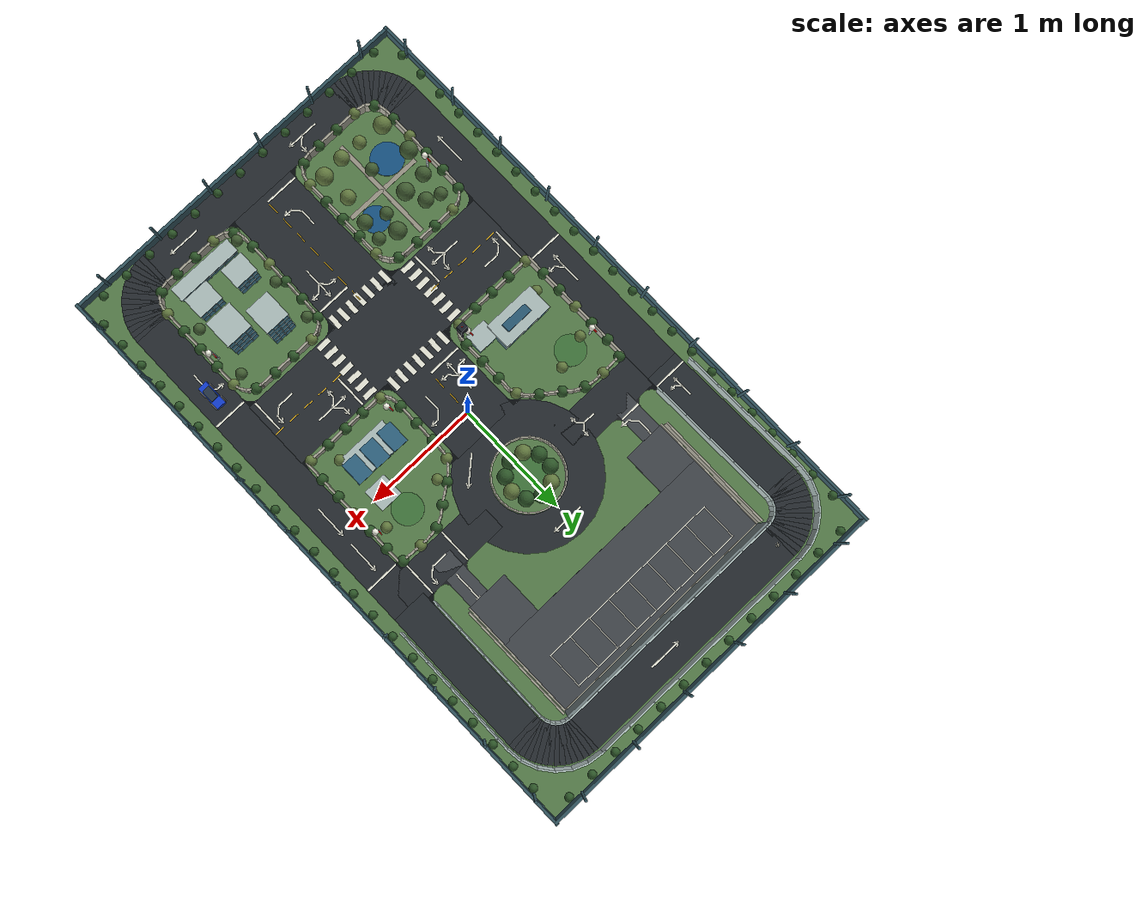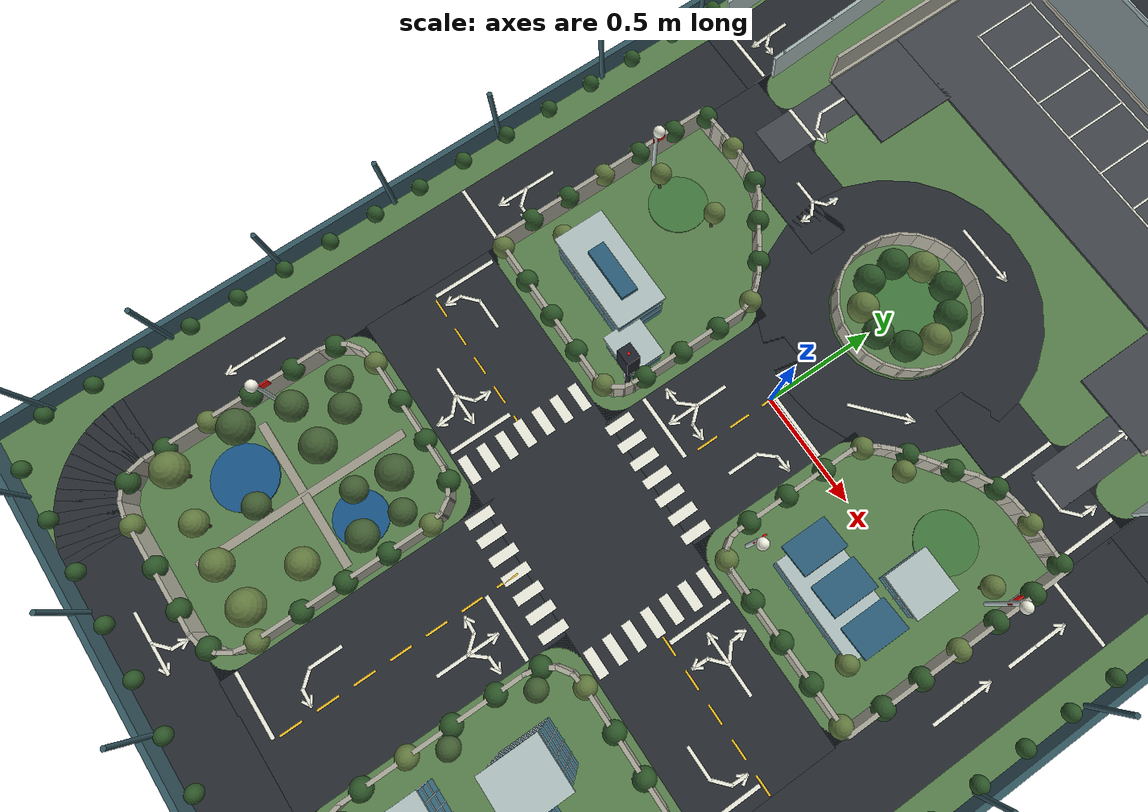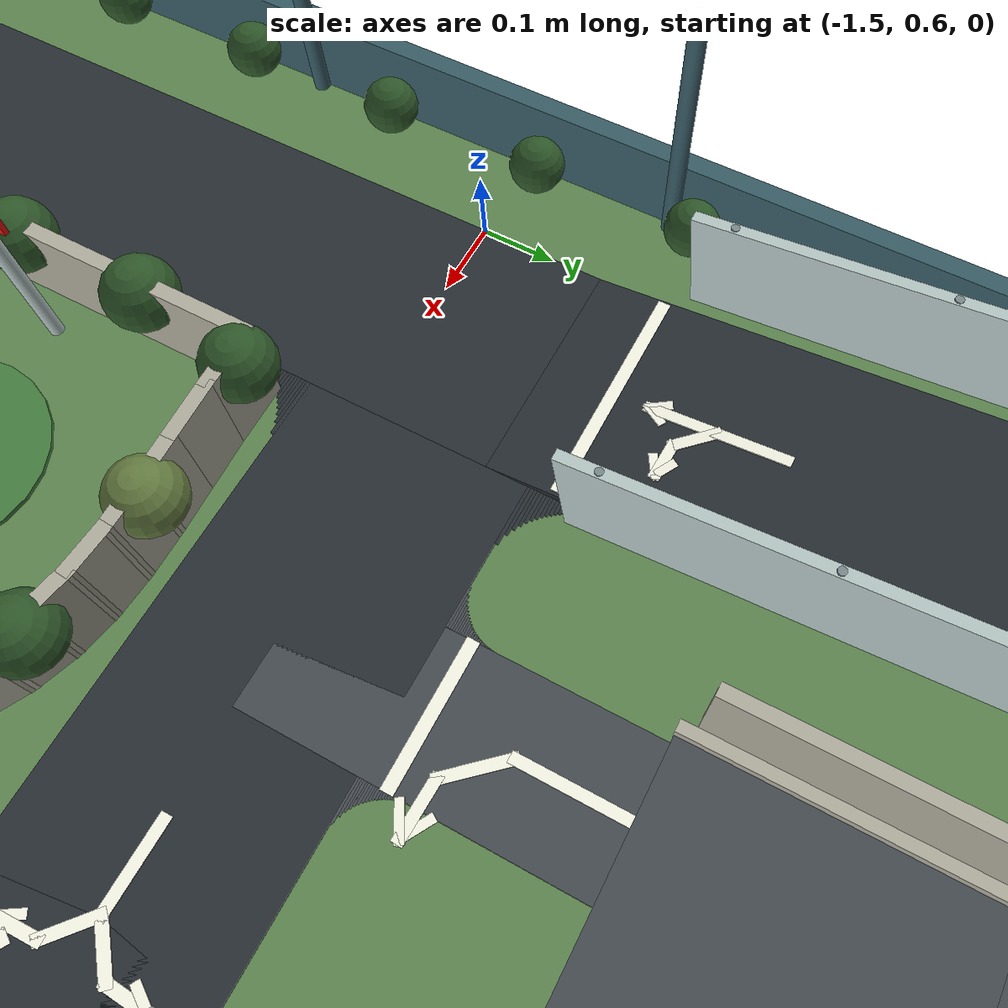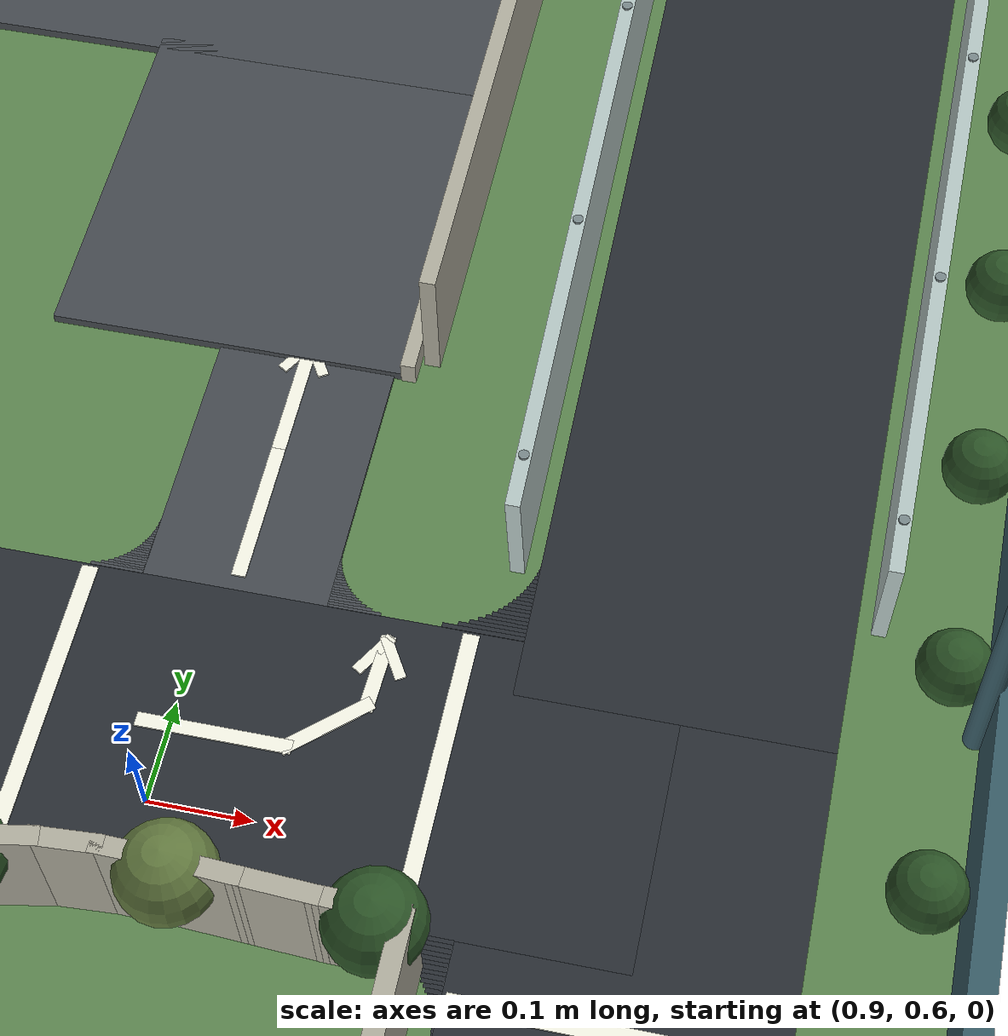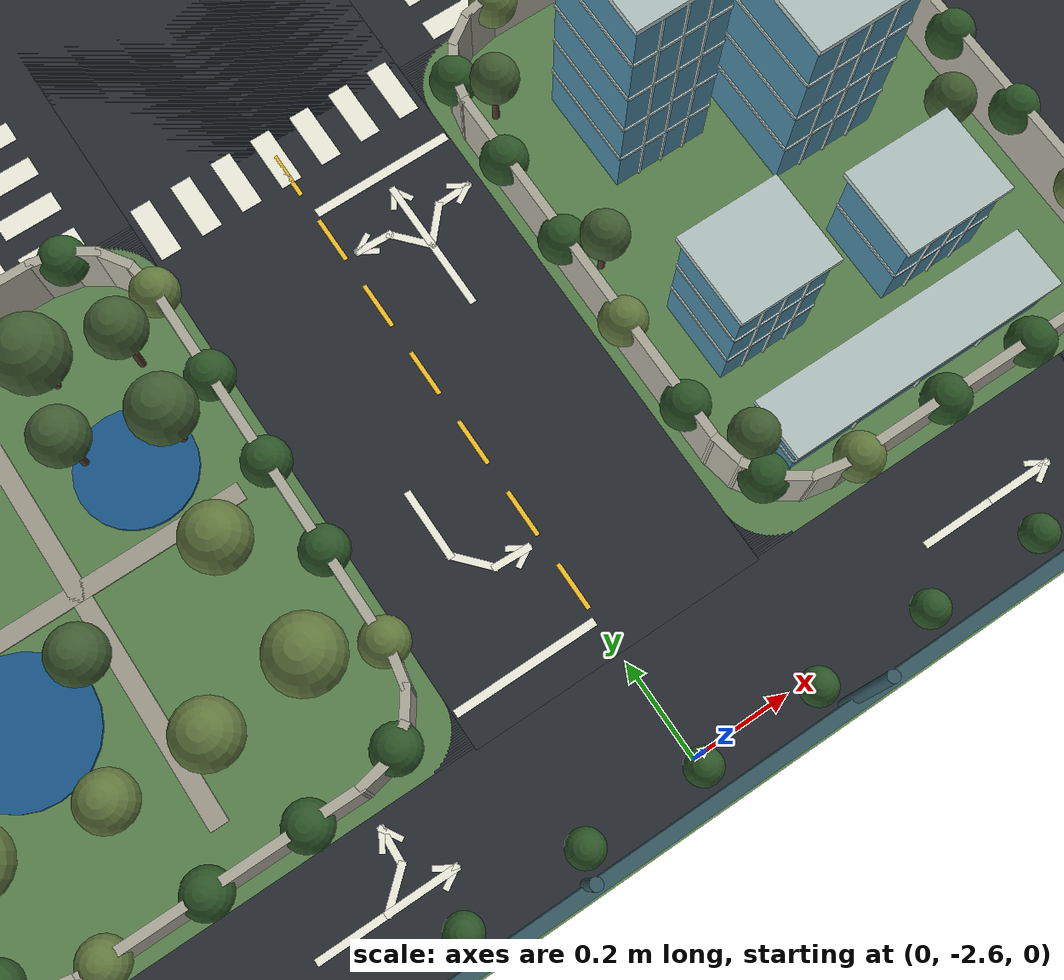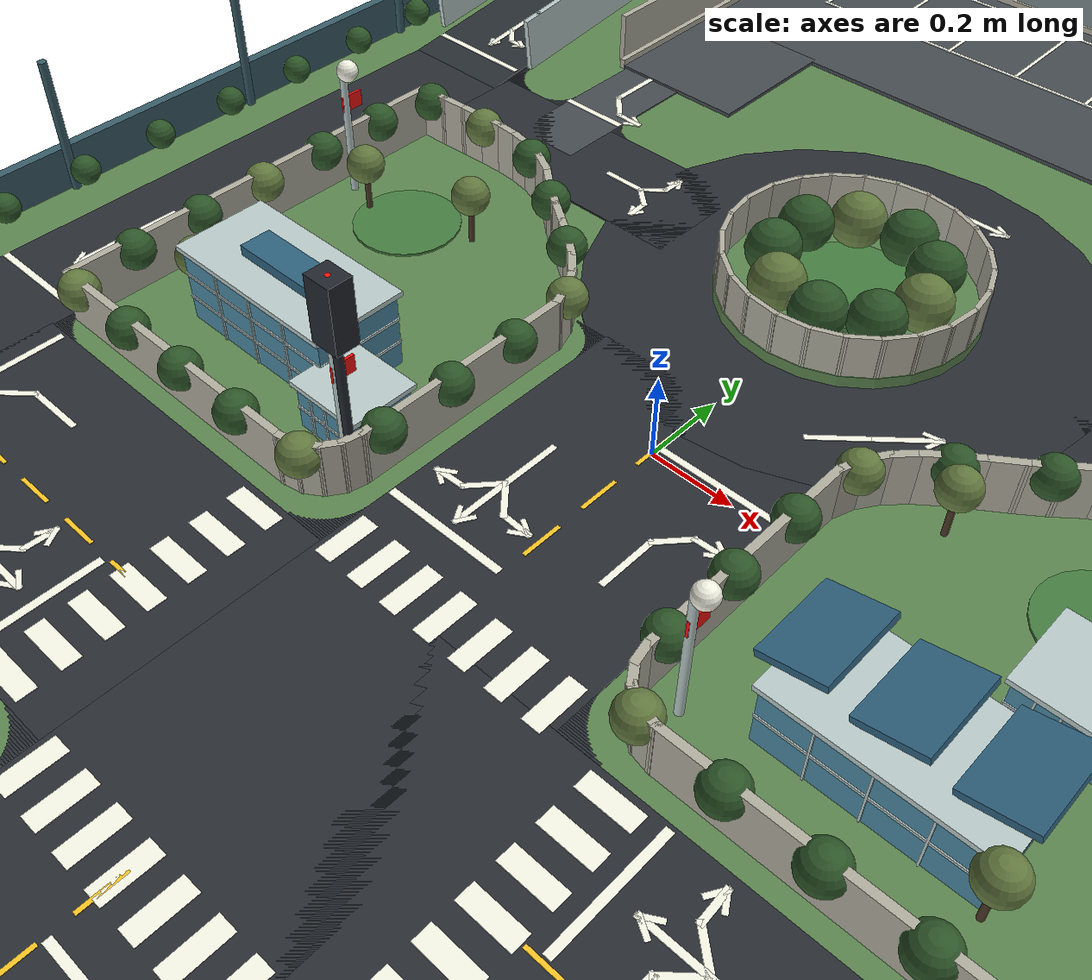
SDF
<?xml version="1.0"?>
<sdf version="1.6"><world name="sandbox">
<gravity>0 0 -9.81</gravity>
<physics type="ode"><max_step_size>.005</max_step_size><real_time_update_rate>200</real_time_update_rate></physics>
<scene><ambient>.78 .78 .78 1</ambient><background>.83 .90 .97 1</background></scene>
<include><uri>model://sun</uri></include>
<plugin name="gazebo_ros_state" filename="libgazebo_ros_state.so"/>
<model name="table"><static>true</static><pose>0.000000 0.000000 -0.045000 0.000000 0.000000 0.000000</pose><link name="body"><collision name="collision"><geometry><box><size>3.300000 5.400000 0.090000</size></box></geometry></collision><visual name="visual"><geometry><box><size>3.300000 5.400000 0.090000</size></box></geometry><material><ambient>0.36 0.52 0.31 1</ambient><diffuse>0.36 0.52 0.31 1</diffuse></material></visual></link></model><model name="fence_north"><static>true</static><pose>0.000000 2.680000 0.055000 0.000000 0.000000 0.000000</pose><link name="body"><collision name="collision"><geometry><box><size>3.300000 0.025000 0.110000</size></box></geometry></collision><visual name="visual"><geometry><box><size>3.300000 0.025000 0.110000</size></box></geometry><material><ambient>0.22 0.36 0.40 1</ambient><diffuse>0.22 0.36 0.40 1</diffuse></material></visual></link></model><model name="fence_south"><static>true</static><pose>0.000000 -2.680000 0.055000 0.000000 0.000000 0.000000</pose><link name="body"><collision name="collision"><geometry><box><size>3.300000 0.025000 0.110000</size></box></geometry></collision><visual name="visual"><geometry><box><size>3.300000 0.025000 0.110000</size></box></geometry><material><ambient>0.22 0.36 0.40 1</ambient><diffuse>0.22 0.36 0.40 1</diffuse></material></visual></link></model><model name="fence_east"><static>true</static><pose>1.638000 0.000000 0.055000 0.000000 0.000000 0.000000</pose><link name="body"><collision name="collision"><geometry><box><size>0.025000 5.400000 0.110000</size></box></geometry></collision><visual name="visual"><geometry><box><size>0.025000 5.400000 0.110000</size></box></geometry><material><ambient>0.22 0.36 0.40 1</ambient><diffuse>0.22 0.36 0.40 1</diffuse></material></visual></link></model><model name="fence_west"><static>true</static><pose>-1.638000 0.000000 0.055000 0.000000 0.000000 0.000000</pose><link name="body"><collision name="collision"><geometry><box><size>0.025000 5.400000 0.110000</size></box></geometry></collision><visual name="visual"><geometry><box><size>0.025000 5.400000 0.110000</size></box></geometry><material><ambient>0.22 0.36 0.40 1</ambient><diffuse>0.22 0.36 0.40 1</diffuse></material></visual></link></model><model name="fence_post_west_0"><static>true</static><pose>-1.620000 -2.430000 0.170000 0.000000 0.000000 0.000000</pose><link name="body"><collision name="collision"><geometry><cylinder><radius>0.011000</radius><length>0.340000</length></cylinder></geometry></collision><visual name="visual"><geometry><cylinder><radius>0.011000</radius><length>0.340000</length></cylinder></geometry><material><ambient>0.22 0.36 0.40 1</ambient><diffuse>0.22 0.36 0.40 1</diffuse></material></visual></link></model><model name="fence_post_west_1"><static>true</static><pose>-1.620000 -1.890000 0.170000 0.000000 0.000000 0.000000</pose><link name="body"><collision name="collision"><geometry><cylinder><radius>0.011000</radius><length>0.340000</length></cylinder></geometry></collision><visual name="visual"><geometry><cylinder><radius>0.011000</radius><length>0.340000</length></cylinder></geometry><material><ambient>0.22 0.36 0.40 1</ambient><diffuse>0.22 0.36 0.40 1</diffuse></material></visual></link></model><model name="fence_post_west_2"><static>true</static><pose>-1.620000 -1.350000 0.170000 0.000000 0.000000 0.000000</pose><link name="body"><collision name="collision"><geometry><cylinder><radius>0.011000</radius><length>0.340000</length></cylinder></geometry></collision><visual name="visual"><geometry><cylinder><radius>0.011000</radius><length>0.340000</length></cylinder></geometry><material><ambient>0.22 0.36 0.40 1</ambient><diffuse>0.22 0.36 0.40 1</diffuse></material></visual></link></model><model name="fence_post_west_3"><static>true</static><pose>-1.620000 -0.810000 0.170000 0.000000 0.000000 0.000000</pose><link name="body"><collision name="collision"><geometry><cylinder><radius>0.011000</radius><length>0.340000</length></cylinder></geometry></collision><visual name="visual"><geometry><cylinder><radius>0.011000</radius><length>0.340000</length></cylinder></geometry><material><ambient>0.22 0.36 0.40 1</ambient><diffuse>0.22 0.36 0.40 1</diffuse></material></visual></link></model><model name="fence_post_west_4"><static>true</static><pose>-1.620000 -0.270000 0.170000 0.000000 0.000000 0.000000</pose><link name="body"><collision name="collision"><geometry><cylinder><radius>0.011000</radius><length>0.340000</length></cylinder></geometry></collision><visual name="visual"><geometry><cylinder><radius>0.011000</radius><length>0.340000</length></cylinder></geometry><material><ambient>0.22 0.36 0.40 1</ambient><diffuse>0.22 0.36 0.40 1</diffuse></material></visual></link></model><model name="fence_post_west_5"><static>true</static><pose>-1.620000 0.270000 0.170000 0.000000 0.000000 0.000000</pose><link name="body"><collision name="collision"><geometry><cylinder><radius>0.011000</radius><length>0.340000</length></cylinder></geometry></collision><visual name="visual"><geometry><cylinder><radius>0.011000</radius><length>0.340000</length></cylinder></geometry><material><ambient>0.22 0.36 0.40 1</ambient><diffuse>0.22 0.36 0.40 1</diffuse></material></visual></link></model><model name="fence_post_west_6"><static>true</static><pose>-1.620000 0.810000 0.170000 0.000000 0.000000 0.000000</pose><link name="body"><collision name="collision"><geometry><cylinder><radius>0.011000</radius><length>0.340000</length></cylinder></geometry></collision><visual name="visual"><geometry><cylinder><radius>0.011000</radius><length>0.340000</length></cylinder></geometry><material><ambient>0.22 0.36 0.40 1</ambient><diffuse>0.22 0.36 0.40 1</diffuse></material></visual></link></model><model name="fence_post_west_7"><static>true</static><pose>-1.620000 1.350000 0.170000 0.000000 0.000000 0.000000</pose><link name="body"><collision name="collision"><geometry><cylinder><radius>0.011000</radius><length>0.340000</length></cylinder></geometry></collision><visual name="visual"><geometry><cylinder><radius>0.011000</radius><length>0.340000</length></cylinder></geometry><material><ambient>0.22 0.36 0.40 1</ambient><diffuse>0.22 0.36 0.40 1</diffuse></material></visual></link></model><model name="fence_post_west_8"><static>true</static><pose>-1.620000 1.890000 0.170000 0.000000 0.000000 0.000000</pose><link name="body"><collision name="collision"><geometry><cylinder><radius>0.011000</radius><length>0.340000</length></cylinder></geometry></collision><visual name="visual"><geometry><cylinder><radius>0.011000</radius><length>0.340000</length></cylinder></geometry><material><ambient>0.22 0.36 0.40 1</ambient><diffuse>0.22 0.36 0.40 1</diffuse></material></visual></link></model><model name="fence_post_west_9"><static>true</static><pose>-1.620000 2.430000 0.170000 0.000000 0.000000 0.000000</pose><link name="body"><collision name="collision"><geometry><cylinder><radius>0.011000</radius><length>0.340000</length></cylinder></geometry></collision><visual name="visual"><geometry><cylinder><radius>0.011000</radius><length>0.340000</length></cylinder></geometry><material><ambient>0.22 0.36 0.40 1</ambient><diffuse>0.22 0.36 0.40 1</diffuse></material></visual></link></model><model name="fence_post_east_0"><static>true</static><pose>1.620000 -2.430000 0.170000 0.000000 0.000000 0.000000</pose><link name="body"><collision name="collision"><geometry><cylinder><radius>0.011000</radius><length>0.340000</length></cylinder></geometry></collision><visual name="visual"><geometry><cylinder><radius>0.011000</radius><length>0.340000</length></cylinder></geometry><material><ambient>0.22 0.36 0.40 1</ambient><diffuse>0.22 0.36 0.40 1</diffuse></material></visual></link></model><model name="fence_post_east_1"><static>true</static><pose>1.620000 -1.890000 0.170000 0.000000 0.000000 0.000000</pose><link name="body"><collision name="collision"><geometry><cylinder><radius>0.011000</radius><length>0.340000</length></cylinder></geometry></collision><visual name="visual"><geometry><cylinder><radius>0.011000</radius><length>0.340000</length></cylinder></geometry><material><ambient>0.22 0.36 0.40 1</ambient><diffuse>0.22 0.36 0.40 1</diffuse></material></visual></link></model><model name="fence_post_east_2"><static>true</static><pose>1.620000 -1.350000 0.170000 0.000000 0.000000 0.000000</pose><link name="body"><collision name="collision"><geometry><cylinder><radius>0.011000</radius><length>0.340000</length></cylinder></geometry></collision><visual name="visual"><geometry><cylinder><radius>0.011000</radius><length>0.340000</length></cylinder></geometry><material><ambient>0.22 0.36 0.40 1</ambient><diffuse>0.22 0.36 0.40 1</diffuse></material></visual></link></model><model name="fence_post_east_3"><static>true</static><pose>1.620000 -0.810000 0.170000 0.000000 0.000000 0.000000</pose><link name="body"><collision name="collision"><geometry><cylinder><radius>0.011000</radius><length>0.340000</length></cylinder></geometry></collision><visual name="visual"><geometry><cylinder><radius>0.011000</radius><length>0.340000</length></cylinder></geometry><material><ambient>0.22 0.36 0.40 1</ambient><diffuse>0.22 0.36 0.40 1</diffuse></material></visual></link></model><model name="fence_post_east_4"><static>true</static><pose>1.620000 -0.270000 0.170000 0.000000 0.000000 0.000000</pose><link name="body"><collision name="collision"><geometry><cylinder><radius>0.011000</radius><length>0.340000</length></cylinder></geometry></collision><visual name="visual"><geometry><cylinder><radius>0.011000</radius><length>0.340000</length></cylinder></geometry><material><ambient>0.22 0.36 0.40 1</ambient><diffuse>0.22 0.36 0.40 1</diffuse></material></visual></link></model><model name="fence_post_east_5"><static>true</static><pose>1.620000 0.270000 0.170000 0.000000 0.000000 0.000000</pose><link name="body"><collision name="collision"><geometry><cylinder><radius>0.011000</radius><length>0.340000</length></cylinder></geometry></collision><visual name="visual"><geometry><cylinder><radius>0.011000</radius><length>0.340000</length></cylinder></geometry><material><ambient>0.22 0.36 0.40 1</ambient><diffuse>0.22 0.36 0.40 1</diffuse></material></visual></link></model><model name="fence_post_east_6"><static>true</static><pose>1.620000 0.810000 0.170000 0.000000 0.000000 0.000000</pose><link name="body"><collision name="collision"><geometry><cylinder><radius>0.011000</radius><length>0.340000</length></cylinder></geometry></collision><visual name="visual"><geometry><cylinder><radius>0.011000</radius><length>0.340000</length></cylinder></geometry><material><ambient>0.22 0.36 0.40 1</ambient><diffuse>0.22 0.36 0.40 1</diffuse></material></visual></link></model><model name="fence_post_east_7"><static>true</static><pose>1.620000 1.350000 0.170000 0.000000 0.000000 0.000000</pose><link name="body"><collision name="collision"><geometry><cylinder><radius>0.011000</radius><length>0.340000</length></cylinder></geometry></collision><visual name="visual"><geometry><cylinder><radius>0.011000</radius><length>0.340000</length></cylinder></geometry><material><ambient>0.22 0.36 0.40 1</ambient><diffuse>0.22 0.36 0.40 1</diffuse></material></visual></link></model><model name="fence_post_east_8"><static>true</static><pose>1.620000 1.890000 0.170000 0.000000 0.000000 0.000000</pose><link name="body"><collision name="collision"><geometry><cylinder><radius>0.011000</radius><length>0.340000</length></cylinder></geometry></collision><visual name="visual"><geometry><cylinder><radius>0.011000</radius><length>0.340000</length></cylinder></geometry><material><ambient>0.22 0.36 0.40 1</ambient><diffuse>0.22 0.36 0.40 1</diffuse></material></visual></link></model><model name="fence_post_east_9"><static>true</static><pose>1.620000 2.430000 0.170000 0.000000 0.000000 0.000000</pose><link name="body"><collision name="collision"><geometry><cylinder><radius>0.011000</radius><length>0.340000</length></cylinder></geometry></collision><visual name="visual"><geometry><cylinder><radius>0.011000</radius><length>0.340000</length></cylinder></geometry><material><ambient>0.22 0.36 0.40 1</ambient><diffuse>0.22 0.36 0.40 1</diffuse></material></visual></link></model><model name="fence_post_south_0"><static>true</static><pose>-1.350000 -2.670000 0.170000 0.000000 0.000000 0.000000</pose><link name="body"><collision name="collision"><geometry><cylinder><radius>0.011000</radius><length>0.340000</length></cylinder></geometry></collision><visual name="visual"><geometry><cylinder><radius>0.011000</radius><length>0.340000</length></cylinder></geometry><material><ambient>0.22 0.36 0.40 1</ambient><diffuse>0.22 0.36 0.40 1</diffuse></material></visual></link></model><model name="fence_post_south_1"><static>true</static><pose>-0.810000 -2.670000 0.170000 0.000000 0.000000 0.000000</pose><link name="body"><collision name="collision"><geometry><cylinder><radius>0.011000</radius><length>0.340000</length></cylinder></geometry></collision><visual name="visual"><geometry><cylinder><radius>0.011000</radius><length>0.340000</length></cylinder></geometry><material><ambient>0.22 0.36 0.40 1</ambient><diffuse>0.22 0.36 0.40 1</diffuse></material></visual></link></model><model name="fence_post_south_2"><static>true</static><pose>-0.270000 -2.670000 0.170000 0.000000 0.000000 0.000000</pose><link name="body"><collision name="collision"><geometry><cylinder><radius>0.011000</radius><length>0.340000</length></cylinder></geometry></collision><visual name="visual"><geometry><cylinder><radius>0.011000</radius><length>0.340000</length></cylinder></geometry><material><ambient>0.22 0.36 0.40 1</ambient><diffuse>0.22 0.36 0.40 1</diffuse></material></visual></link></model><model name="fence_post_south_3"><static>true</static><pose>0.270000 -2.670000 0.170000 0.000000 0.000000 0.000000</pose><link name="body"><collision name="collision"><geometry><cylinder><radius>0.011000</radius><length>0.340000</length></cylinder></geometry></collision><visual name="visual"><geometry><cylinder><radius>0.011000</radius><length>0.340000</length></cylinder></geometry><material><ambient>0.22 0.36 0.40 1</ambient><diffuse>0.22 0.36 0.40 1</diffuse></material></visual></link></model><model name="fence_post_south_4"><static>true</static><pose>0.810000 -2.670000 0.170000 0.000000 0.000000 0.000000</pose><link name="body"><collision name="collision"><geometry><cylinder><radius>0.011000</radius><length>0.340000</length></cylinder></geometry></collision><visual name="visual"><geometry><cylinder><radius>0.011000</radius><length>0.340000</length></cylinder></geometry><material><ambient>0.22 0.36 0.40 1</ambient><diffuse>0.22 0.36 0.40 1</diffuse></material></visual></link></model><model name="fence_post_south_5"><static>true</static><pose>1.350000 -2.670000 0.170000 0.000000 0.000000 0.000000</pose><link name="body"><collision name="collision"><geometry><cylinder><radius>0.011000</radius><length>0.340000</length></cylinder></geometry></collision><visual name="visual"><geometry><cylinder><radius>0.011000</radius><length>0.340000</length></cylinder></geometry><material><ambient>0.22 0.36 0.40 1</ambient><diffuse>0.22 0.36 0.40 1</diffuse></material></visual></link></model><model name="fence_post_north_0"><static>true</static><pose>-1.350000 2.670000 0.170000 0.000000 0.000000 0.000000</pose><link name="body"><collision name="collision"><geometry><cylinder><radius>0.011000</radius><length>0.340000</length></cylinder></geometry></collision><visual name="visual"><geometry><cylinder><radius>0.011000</radius><length>0.340000</length></cylinder></geometry><material><ambient>0.22 0.36 0.40 1</ambient><diffuse>0.22 0.36 0.40 1</diffuse></material></visual></link></model><model name="fence_post_north_1"><static>true</static><pose>-0.810000 2.670000 0.170000 0.000000 0.000000 0.000000</pose><link name="body"><collision name="collision"><geometry><cylinder><radius>0.011000</radius><length>0.340000</length></cylinder></geometry></collision><visual name="visual"><geometry><cylinder><radius>0.011000</radius><length>0.340000</length></cylinder></geometry><material><ambient>0.22 0.36 0.40 1</ambient><diffuse>0.22 0.36 0.40 1</diffuse></material></visual></link></model><model name="fence_post_north_2"><static>true</static><pose>-0.270000 2.670000 0.170000 0.000000 0.000000 0.000000</pose><link name="body"><collision name="collision"><geometry><cylinder><radius>0.011000</radius><length>0.340000</length></cylinder></geometry></collision><visual name="visual"><geometry><cylinder><radius>0.011000</radius><length>0.340000</length></cylinder></geometry><material><ambient>0.22 0.36 0.40 1</ambient><diffuse>0.22 0.36 0.40 1</diffuse></material></visual></link></model><model name="fence_post_north_3"><static>true</static><pose>0.270000 2.670000 0.170000 0.000000 0.000000 0.000000</pose><link name="body"><collision name="collision"><geometry><cylinder><radius>0.011000</radius><length>0.340000</length></cylinder></geometry></collision><visual name="visual"><geometry><cylinder><radius>0.011000</radius><length>0.340000</length></cylinder></geometry><material><ambient>0.22 0.36 0.40 1</ambient><diffuse>0.22 0.36 0.40 1</diffuse></material></visual></link></model><model name="fence_post_north_4"><static>true</static><pose>0.810000 2.670000 0.170000 0.000000 0.000000 0.000000</pose><link name="body"><collision name="collision"><geometry><cylinder><radius>0.011000</radius><length>0.340000</length></cylinder></geometry></collision><visual name="visual"><geometry><cylinder><radius>0.011000</radius><length>0.340000</length></cylinder></geometry><material><ambient>0.22 0.36 0.40 1</ambient><diffuse>0.22 0.36 0.40 1</diffuse></material></visual></link></model><model name="fence_post_north_5"><static>true</static><pose>1.350000 2.670000 0.170000 0.000000 0.000000 0.000000</pose><link name="body"><collision name="collision"><geometry><cylinder><radius>0.011000</radius><length>0.340000</length></cylinder></geometry></collision><visual name="visual"><geometry><cylinder><radius>0.011000</radius><length>0.340000</length></cylinder></geometry><material><ambient>0.22 0.36 0.40 1</ambient><diffuse>0.22 0.36 0.40 1</diffuse></material></visual></link></model><model name="outer_left_flat"><static>true</static><pose>-1.350000 -0.637500 0.000000 0.000000 -0.000000 1.570796</pose><link name="body"><visual name="visual"><geometry><box><size>3.087000 0.300000 0.008000</size></box></geometry><material><ambient>0.16 0.18 0.20 1</ambient><diffuse>0.16 0.18 0.20 1</diffuse></material></visual></link></model><model name="outer_right_flat"><static>true</static><pose>1.350000 -0.637500 0.000000 0.000000 -0.000000 1.570796</pose><link name="body"><visual name="visual"><geometry><box><size>3.087000 0.300000 0.008000</size></box></geometry><material><ambient>0.16 0.18 0.20 1</ambient><diffuse>0.16 0.18 0.20 1</diffuse></material></visual></link></model><model name="left_ramp"><static>true</static><pose>-1.350000 1.362500 0.069000 0.000000 -0.115707 1.570796</pose><link name="body"><collision name="collision"><geometry><box><size>1.337000 0.300000 0.008000</size></box></geometry></collision><visual name="visual"><geometry><box><size>1.337000 0.300000 0.008000</size></box></geometry><material><ambient>0.16 0.18 0.20 1</ambient><diffuse>0.16 0.18 0.20 1</diffuse></material></visual></link></model><model name="right_ramp"><static>true</static><pose>1.350000 1.362500 0.069000 0.000000 -0.115707 1.570796</pose><link name="body"><collision name="collision"><geometry><box><size>1.337000 0.300000 0.008000</size></box></geometry></collision><visual name="visual"><geometry><box><size>1.337000 0.300000 0.008000</size></box></geometry><material><ambient>0.16 0.18 0.20 1</ambient><diffuse>0.16 0.18 0.20 1</diffuse></material></visual></link></model><model name="outer_top"><static>true</static><pose>0.000000 2.350000 0.146000 0.000000 -0.000000 0.000000</pose><link name="body"><collision name="collision"><geometry><box><size>2.062000 0.300000 0.008000</size></box></geometry></collision><visual name="visual"><geometry><box><size>2.062000 0.300000 0.008000</size></box></geometry><material><ambient>0.16 0.18 0.20 1</ambient><diffuse>0.16 0.18 0.20 1</diffuse></material></visual></link></model><model name="outer_bottom"><static>true</static><pose>0.000000 -2.525000 0.000000 0.000000 -0.000000 0.000000</pose><link name="body"><visual name="visual"><geometry><box><size>2.012000 0.300000 0.008000</size></box></geometry><material><ambient>0.16 0.18 0.20 1</ambient><diffuse>0.16 0.18 0.20 1</diffuse></material></visual></link></model><model name="corner_top_left_00"><static>true</static><pose>-1.349218 2.040928 0.146000 0.000000 -0.000000 1.521709</pose><link name="body"><collision name="collision"><geometry><box><size>0.043894 0.300000 0.008000</size></box></geometry></collision><visual name="visual"><geometry><box><size>0.043894 0.300000 0.008000</size></box></geometry><material><ambient>0.16 0.18 0.20 1</ambient><diffuse>0.16 0.18 0.20 1</diffuse></material></visual></link></model><model name="corner_top_left_01"><static>true</static><pose>-1.346095 2.072630 0.146000 0.000000 -0.000000 1.423534</pose><link name="body"><collision name="collision"><geometry><box><size>0.043894 0.300000 0.008000</size></box></geometry></collision><visual name="visual"><geometry><box><size>0.043894 0.300000 0.008000</size></box></geometry><material><ambient>0.16 0.18 0.20 1</ambient><diffuse>0.16 0.18 0.20 1</diffuse></material></visual></link></model><model name="corner_top_left_02"><static>true</static><pose>-1.339880 2.103873 0.146000 0.000000 -0.000000 1.325359</pose><link name="body"><collision name="collision"><geometry><box><size>0.043894 0.300000 0.008000</size></box></geometry></collision><visual name="visual"><geometry><box><size>0.043894 0.300000 0.008000</size></box></geometry><material><ambient>0.16 0.18 0.20 1</ambient><diffuse>0.16 0.18 0.20 1</diffuse></material></visual></link></model><model name="corner_top_left_03"><static>true</static><pose>-1.330633 2.134357 0.146000 0.000000 -0.000000 1.227185</pose><link name="body"><collision name="collision"><geometry><box><size>0.043894 0.300000 0.008000</size></box></geometry></collision><visual name="visual"><geometry><box><size>0.043894 0.300000 0.008000</size></box></geometry><material><ambient>0.16 0.18 0.20 1</ambient><diffuse>0.16 0.18 0.20 1</diffuse></material></visual></link></model><model name="corner_top_left_04"><static>true</static><pose>-1.318443 2.163788 0.146000 0.000000 -0.000000 1.129010</pose><link name="body"><collision name="collision"><geometry><box><size>0.043894 0.300000 0.008000</size></box></geometry></collision><visual name="visual"><geometry><box><size>0.043894 0.300000 0.008000</size></box></geometry><material><ambient>0.16 0.18 0.20 1</ambient><diffuse>0.16 0.18 0.20 1</diffuse></material></visual></link></model><model name="corner_top_left_05"><static>true</static><pose>-1.303426 2.191882 0.146000 0.000000 -0.000000 1.030835</pose><link name="body"><collision name="collision"><geometry><box><size>0.043894 0.300000 0.008000</size></box></geometry></collision><visual name="visual"><geometry><box><size>0.043894 0.300000 0.008000</size></box></geometry><material><ambient>0.16 0.18 0.20 1</ambient><diffuse>0.16 0.18 0.20 1</diffuse></material></visual></link></model><model name="corner_top_left_06"><static>true</static><pose>-1.285728 2.218369 0.146000 0.000000 -0.000000 0.932660</pose><link name="body"><collision name="collision"><geometry><box><size>0.043894 0.300000 0.008000</size></box></geometry></collision><visual name="visual"><geometry><box><size>0.043894 0.300000 0.008000</size></box></geometry><material><ambient>0.16 0.18 0.20 1</ambient><diffuse>0.16 0.18 0.20 1</diffuse></material></visual></link></model><model name="corner_top_left_07"><static>true</static><pose>-1.265519 2.242994 0.146000 0.000000 -0.000000 0.834486</pose><link name="body"><collision name="collision"><geometry><box><size>0.043894 0.300000 0.008000</size></box></geometry></collision><visual name="visual"><geometry><box><size>0.043894 0.300000 0.008000</size></box></geometry><material><ambient>0.16 0.18 0.20 1</ambient><diffuse>0.16 0.18 0.20 1</diffuse></material></visual></link></model><model name="corner_top_left_08"><static>true</static><pose>-1.242994 2.265519 0.146000 0.000000 -0.000000 0.736311</pose><link name="body"><collision name="collision"><geometry><box><size>0.043894 0.300000 0.008000</size></box></geometry></collision><visual name="visual"><geometry><box><size>0.043894 0.300000 0.008000</size></box></geometry><material><ambient>0.16 0.18 0.20 1</ambient><diffuse>0.16 0.18 0.20 1</diffuse></material></visual></link></model><model name="corner_top_left_09"><static>true</static><pose>-1.218369 2.285728 0.146000 0.000000 -0.000000 0.638136</pose><link name="body"><collision name="collision"><geometry><box><size>0.043894 0.300000 0.008000</size></box></geometry></collision><visual name="visual"><geometry><box><size>0.043894 0.300000 0.008000</size></box></geometry><material><ambient>0.16 0.18 0.20 1</ambient><diffuse>0.16 0.18 0.20 1</diffuse></material></visual></link></model><model name="corner_top_left_10"><static>true</static><pose>-1.191882 2.303426 0.146000 0.000000 -0.000000 0.539961</pose><link name="body"><collision name="collision"><geometry><box><size>0.043894 0.300000 0.008000</size></box></geometry></collision><visual name="visual"><geometry><box><size>0.043894 0.300000 0.008000</size></box></geometry><material><ambient>0.16 0.18 0.20 1</ambient><diffuse>0.16 0.18 0.20 1</diffuse></material></visual></link></model><model name="corner_top_left_11"><static>true</static><pose>-1.163788 2.318443 0.146000 0.000000 -0.000000 0.441786</pose><link name="body"><collision name="collision"><geometry><box><size>0.043894 0.300000 0.008000</size></box></geometry></collision><visual name="visual"><geometry><box><size>0.043894 0.300000 0.008000</size></box></geometry><material><ambient>0.16 0.18 0.20 1</ambient><diffuse>0.16 0.18 0.20 1</diffuse></material></visual></link></model><model name="corner_top_left_12"><static>true</static><pose>-1.134357 2.330633 0.146000 0.000000 -0.000000 0.343612</pose><link name="body"><collision name="collision"><geometry><box><size>0.043894 0.300000 0.008000</size></box></geometry></collision><visual name="visual"><geometry><box><size>0.043894 0.300000 0.008000</size></box></geometry><material><ambient>0.16 0.18 0.20 1</ambient><diffuse>0.16 0.18 0.20 1</diffuse></material></visual></link></model><model name="corner_top_left_13"><static>true</static><pose>-1.103873 2.339880 0.146000 0.000000 -0.000000 0.245437</pose><link name="body"><collision name="collision"><geometry><box><size>0.043894 0.300000 0.008000</size></box></geometry></collision><visual name="visual"><geometry><box><size>0.043894 0.300000 0.008000</size></box></geometry><material><ambient>0.16 0.18 0.20 1</ambient><diffuse>0.16 0.18 0.20 1</diffuse></material></visual></link></model><model name="corner_top_left_14"><static>true</static><pose>-1.072630 2.346095 0.146000 0.000000 -0.000000 0.147262</pose><link name="body"><collision name="collision"><geometry><box><size>0.043894 0.300000 0.008000</size></box></geometry></collision><visual name="visual"><geometry><box><size>0.043894 0.300000 0.008000</size></box></geometry><material><ambient>0.16 0.18 0.20 1</ambient><diffuse>0.16 0.18 0.20 1</diffuse></material></visual></link></model><model name="corner_top_left_15"><static>true</static><pose>-1.040928 2.349218 0.146000 0.000000 -0.000000 0.049087</pose><link name="body"><collision name="collision"><geometry><box><size>0.043894 0.300000 0.008000</size></box></geometry></collision><visual name="visual"><geometry><box><size>0.043894 0.300000 0.008000</size></box></geometry><material><ambient>0.16 0.18 0.20 1</ambient><diffuse>0.16 0.18 0.20 1</diffuse></material></visual></link></model><model name="corner_top_right_00"><static>true</static><pose>1.040928 2.349218 0.146000 0.000000 -0.000000 -0.049087</pose><link name="body"><collision name="collision"><geometry><box><size>0.043894 0.300000 0.008000</size></box></geometry></collision><visual name="visual"><geometry><box><size>0.043894 0.300000 0.008000</size></box></geometry><material><ambient>0.16 0.18 0.20 1</ambient><diffuse>0.16 0.18 0.20 1</diffuse></material></visual></link></model><model name="corner_top_right_01"><static>true</static><pose>1.072630 2.346095 0.146000 0.000000 -0.000000 -0.147262</pose><link name="body"><collision name="collision"><geometry><box><size>0.043894 0.300000 0.008000</size></box></geometry></collision><visual name="visual"><geometry><box><size>0.043894 0.300000 0.008000</size></box></geometry><material><ambient>0.16 0.18 0.20 1</ambient><diffuse>0.16 0.18 0.20 1</diffuse></material></visual></link></model><model name="corner_top_right_02"><static>true</static><pose>1.103873 2.339880 0.146000 0.000000 -0.000000 -0.245437</pose><link name="body"><collision name="collision"><geometry><box><size>0.043894 0.300000 0.008000</size></box></geometry></collision><visual name="visual"><geometry><box><size>0.043894 0.300000 0.008000</size></box></geometry><material><ambient>0.16 0.18 0.20 1</ambient><diffuse>0.16 0.18 0.20 1</diffuse></material></visual></link></model><model name="corner_top_right_03"><static>true</static><pose>1.134357 2.330633 0.146000 0.000000 -0.000000 -0.343612</pose><link name="body"><collision name="collision"><geometry><box><size>0.043894 0.300000 0.008000</size></box></geometry></collision><visual name="visual"><geometry><box><size>0.043894 0.300000 0.008000</size></box></geometry><material><ambient>0.16 0.18 0.20 1</ambient><diffuse>0.16 0.18 0.20 1</diffuse></material></visual></link></model><model name="corner_top_right_04"><static>true</static><pose>1.163788 2.318443 0.146000 0.000000 -0.000000 -0.441786</pose><link name="body"><collision name="collision"><geometry><box><size>0.043894 0.300000 0.008000</size></box></geometry></collision><visual name="visual"><geometry><box><size>0.043894 0.300000 0.008000</size></box></geometry><material><ambient>0.16 0.18 0.20 1</ambient><diffuse>0.16 0.18 0.20 1</diffuse></material></visual></link></model><model name="corner_top_right_05"><static>true</static><pose>1.191882 2.303426 0.146000 0.000000 -0.000000 -0.539961</pose><link name="body"><collision name="collision"><geometry><box><size>0.043894 0.300000 0.008000</size></box></geometry></collision><visual name="visual"><geometry><box><size>0.043894 0.300000 0.008000</size></box></geometry><material><ambient>0.16 0.18 0.20 1</ambient><diffuse>0.16 0.18 0.20 1</diffuse></material></visual></link></model><model name="corner_top_right_06"><static>true</static><pose>1.218369 2.285728 0.146000 0.000000 -0.000000 -0.638136</pose><link name="body"><collision name="collision"><geometry><box><size>0.043894 0.300000 0.008000</size></box></geometry></collision><visual name="visual"><geometry><box><size>0.043894 0.300000 0.008000</size></box></geometry><material><ambient>0.16 0.18 0.20 1</ambient><diffuse>0.16 0.18 0.20 1</diffuse></material></visual></link></model><model name="corner_top_right_07"><static>true</static><pose>1.242994 2.265519 0.146000 0.000000 -0.000000 -0.736311</pose><link name="body"><collision name="collision"><geometry><box><size>0.043894 0.300000 0.008000</size></box></geometry></collision><visual name="visual"><geometry><box><size>0.043894 0.300000 0.008000</size></box></geometry><material><ambient>0.16 0.18 0.20 1</ambient><diffuse>0.16 0.18 0.20 1</diffuse></material></visual></link></model><model name="corner_top_right_08"><static>true</static><pose>1.265519 2.242994 0.146000 0.000000 -0.000000 -0.834486</pose><link name="body"><collision name="collision"><geometry><box><size>0.043894 0.300000 0.008000</size></box></geometry></collision><visual name="visual"><geometry><box><size>0.043894 0.300000 0.008000</size></box></geometry><material><ambient>0.16 0.18 0.20 1</ambient><diffuse>0.16 0.18 0.20 1</diffuse></material></visual></link></model><model name="corner_top_right_09"><static>true</static><pose>1.285728 2.218369 0.146000 0.000000 -0.000000 -0.932660</pose><link name="body"><collision name="collision"><geometry><box><size>0.043894 0.300000 0.008000</size></box></geometry></collision><visual name="visual"><geometry><box><size>0.043894 0.300000 0.008000</size></box></geometry><material><ambient>0.16 0.18 0.20 1</ambient><diffuse>0.16 0.18 0.20 1</diffuse></material></visual></link></model><model name="corner_top_right_10"><static>true</static><pose>1.303426 2.191882 0.146000 0.000000 -0.000000 -1.030835</pose><link name="body"><collision name="collision"><geometry><box><size>0.043894 0.300000 0.008000</size></box></geometry></collision><visual name="visual"><geometry><box><size>0.043894 0.300000 0.008000</size></box></geometry><material><ambient>0.16 0.18 0.20 1</ambient><diffuse>0.16 0.18 0.20 1</diffuse></material></visual></link></model><model name="corner_top_right_11"><static>true</static><pose>1.318443 2.163788 0.146000 0.000000 -0.000000 -1.129010</pose><link name="body"><collision name="collision"><geometry><box><size>0.043894 0.300000 0.008000</size></box></geometry></collision><visual name="visual"><geometry><box><size>0.043894 0.300000 0.008000</size></box></geometry><material><ambient>0.16 0.18 0.20 1</ambient><diffuse>0.16 0.18 0.20 1</diffuse></material></visual></link></model><model name="corner_top_right_12"><static>true</static><pose>1.330633 2.134357 0.146000 0.000000 -0.000000 -1.227185</pose><link name="body"><collision name="collision"><geometry><box><size>0.043894 0.300000 0.008000</size></box></geometry></collision><visual name="visual"><geometry><box><size>0.043894 0.300000 0.008000</size></box></geometry><material><ambient>0.16 0.18 0.20 1</ambient><diffuse>0.16 0.18 0.20 1</diffuse></material></visual></link></model><model name="corner_top_right_13"><static>true</static><pose>1.339880 2.103873 0.146000 0.000000 -0.000000 -1.325359</pose><link name="body"><collision name="collision"><geometry><box><size>0.043894 0.300000 0.008000</size></box></geometry></collision><visual name="visual"><geometry><box><size>0.043894 0.300000 0.008000</size></box></geometry><material><ambient>0.16 0.18 0.20 1</ambient><diffuse>0.16 0.18 0.20 1</diffuse></material></visual></link></model><model name="corner_top_right_14"><static>true</static><pose>1.346095 2.072630 0.146000 0.000000 -0.000000 -1.423534</pose><link name="body"><collision name="collision"><geometry><box><size>0.043894 0.300000 0.008000</size></box></geometry></collision><visual name="visual"><geometry><box><size>0.043894 0.300000 0.008000</size></box></geometry><material><ambient>0.16 0.18 0.20 1</ambient><diffuse>0.16 0.18 0.20 1</diffuse></material></visual></link></model><model name="corner_top_right_15"><static>true</static><pose>1.349218 2.040928 0.146000 0.000000 -0.000000 -1.521709</pose><link name="body"><collision name="collision"><geometry><box><size>0.043894 0.300000 0.008000</size></box></geometry></collision><visual name="visual"><geometry><box><size>0.043894 0.300000 0.008000</size></box></geometry><material><ambient>0.16 0.18 0.20 1</ambient><diffuse>0.16 0.18 0.20 1</diffuse></material></visual></link></model><model name="corner_bottom_right_00"><static>true</static><pose>1.349157 -2.192153 0.000000 0.000000 -0.000000 -1.619884</pose><link name="body"><visual name="visual"><geometry><box><size>0.046347 0.300000 0.008000</size></box></geometry><material><ambient>0.16 0.18 0.20 1</ambient><diffuse>0.16 0.18 0.20 1</diffuse></material></visual></link></model><model name="corner_bottom_right_01"><static>true</static><pose>1.345795 -2.226294 0.000000 0.000000 -0.000000 -1.718058</pose><link name="body"><visual name="visual"><geometry><box><size>0.046347 0.300000 0.008000</size></box></geometry><material><ambient>0.16 0.18 0.20 1</ambient><diffuse>0.16 0.18 0.20 1</diffuse></material></visual></link></model><model name="corner_bottom_right_02"><static>true</static><pose>1.339102 -2.259941 0.000000 0.000000 -0.000000 -1.816233</pose><link name="body"><visual name="visual"><geometry><box><size>0.046347 0.300000 0.008000</size></box></geometry><material><ambient>0.16 0.18 0.20 1</ambient><diffuse>0.16 0.18 0.20 1</diffuse></material></visual></link></model><model name="corner_bottom_right_03"><static>true</static><pose>1.329143 -2.292769 0.000000 0.000000 -0.000000 -1.914408</pose><link name="body"><visual name="visual"><geometry><box><size>0.046347 0.300000 0.008000</size></box></geometry><material><ambient>0.16 0.18 0.20 1</ambient><diffuse>0.16 0.18 0.20 1</diffuse></material></visual></link></model><model name="corner_bottom_right_04"><static>true</static><pose>1.316015 -2.324464 0.000000 0.000000 -0.000000 -2.012583</pose><link name="body"><visual name="visual"><geometry><box><size>0.046347 0.300000 0.008000</size></box></geometry><material><ambient>0.16 0.18 0.20 1</ambient><diffuse>0.16 0.18 0.20 1</diffuse></material></visual></link></model><model name="corner_bottom_right_05"><static>true</static><pose>1.299843 -2.354719 0.000000 0.000000 -0.000000 -2.110758</pose><link name="body"><visual name="visual"><geometry><box><size>0.046347 0.300000 0.008000</size></box></geometry><material><ambient>0.16 0.18 0.20 1</ambient><diffuse>0.16 0.18 0.20 1</diffuse></material></visual></link></model><model name="corner_bottom_right_06"><static>true</static><pose>1.280784 -2.383244 0.000000 0.000000 -0.000000 -2.208932</pose><link name="body"><visual name="visual"><geometry><box><size>0.046347 0.300000 0.008000</size></box></geometry><material><ambient>0.16 0.18 0.20 1</ambient><diffuse>0.16 0.18 0.20 1</diffuse></material></visual></link></model><model name="corner_bottom_right_07"><static>true</static><pose>1.259021 -2.409763 0.000000 0.000000 -0.000000 -2.307107</pose><link name="body"><visual name="visual"><geometry><box><size>0.046347 0.300000 0.008000</size></box></geometry><material><ambient>0.16 0.18 0.20 1</ambient><diffuse>0.16 0.18 0.20 1</diffuse></material></visual></link></model><model name="corner_bottom_right_08"><static>true</static><pose>1.234763 -2.434021 0.000000 0.000000 -0.000000 -2.405282</pose><link name="body"><visual name="visual"><geometry><box><size>0.046347 0.300000 0.008000</size></box></geometry><material><ambient>0.16 0.18 0.20 1</ambient><diffuse>0.16 0.18 0.20 1</diffuse></material></visual></link></model><model name="corner_bottom_right_09"><static>true</static><pose>1.208244 -2.455784 0.000000 0.000000 -0.000000 -2.503457</pose><link name="body"><visual name="visual"><geometry><box><size>0.046347 0.300000 0.008000</size></box></geometry><material><ambient>0.16 0.18 0.20 1</ambient><diffuse>0.16 0.18 0.20 1</diffuse></material></visual></link></model><model name="corner_bottom_right_10"><static>true</static><pose>1.179719 -2.474843 0.000000 0.000000 -0.000000 -2.601631</pose><link name="body"><visual name="visual"><geometry><box><size>0.046347 0.300000 0.008000</size></box></geometry><material><ambient>0.16 0.18 0.20 1</ambient><diffuse>0.16 0.18 0.20 1</diffuse></material></visual></link></model><model name="corner_bottom_right_11"><static>true</static><pose>1.149464 -2.491015 0.000000 0.000000 -0.000000 -2.699806</pose><link name="body"><visual name="visual"><geometry><box><size>0.046347 0.300000 0.008000</size></box></geometry><material><ambient>0.16 0.18 0.20 1</ambient><diffuse>0.16 0.18 0.20 1</diffuse></material></visual></link></model><model name="corner_bottom_right_12"><static>true</static><pose>1.117769 -2.504143 0.000000 0.000000 -0.000000 -2.797981</pose><link name="body"><visual name="visual"><geometry><box><size>0.046347 0.300000 0.008000</size></box></geometry><material><ambient>0.16 0.18 0.20 1</ambient><diffuse>0.16 0.18 0.20 1</diffuse></material></visual></link></model><model name="corner_bottom_right_13"><static>true</static><pose>1.084941 -2.514102 0.000000 0.000000 -0.000000 -2.896156</pose><link name="body"><visual name="visual"><geometry><box><size>0.046347 0.300000 0.008000</size></box></geometry><material><ambient>0.16 0.18 0.20 1</ambient><diffuse>0.16 0.18 0.20 1</diffuse></material></visual></link></model><model name="corner_bottom_right_14"><static>true</static><pose>1.051294 -2.520795 0.000000 0.000000 -0.000000 -2.994330</pose><link name="body"><visual name="visual"><geometry><box><size>0.046347 0.300000 0.008000</size></box></geometry><material><ambient>0.16 0.18 0.20 1</ambient><diffuse>0.16 0.18 0.20 1</diffuse></material></visual></link></model><model name="corner_bottom_right_15"><static>true</static><pose>1.017153 -2.524157 0.000000 0.000000 -0.000000 -3.092505</pose><link name="body"><visual name="visual"><geometry><box><size>0.046347 0.300000 0.008000</size></box></geometry><material><ambient>0.16 0.18 0.20 1</ambient><diffuse>0.16 0.18 0.20 1</diffuse></material></visual></link></model><model name="corner_bottom_left_00"><static>true</static><pose>-1.017153 -2.524157 0.000000 0.000000 -0.000000 3.092505</pose><link name="body"><visual name="visual"><geometry><box><size>0.046347 0.300000 0.008000</size></box></geometry><material><ambient>0.16 0.18 0.20 1</ambient><diffuse>0.16 0.18 0.20 1</diffuse></material></visual></link></model><model name="corner_bottom_left_01"><static>true</static><pose>-1.051294 -2.520795 0.000000 0.000000 -0.000000 2.994330</pose><link name="body"><visual name="visual"><geometry><box><size>0.046347 0.300000 0.008000</size></box></geometry><material><ambient>0.16 0.18 0.20 1</ambient><diffuse>0.16 0.18 0.20 1</diffuse></material></visual></link></model><model name="corner_bottom_left_02"><static>true</static><pose>-1.084941 -2.514102 0.000000 0.000000 -0.000000 2.896156</pose><link name="body"><visual name="visual"><geometry><box><size>0.046347 0.300000 0.008000</size></box></geometry><material><ambient>0.16 0.18 0.20 1</ambient><diffuse>0.16 0.18 0.20 1</diffuse></material></visual></link></model><model name="corner_bottom_left_03"><static>true</static><pose>-1.117769 -2.504143 0.000000 0.000000 -0.000000 2.797981</pose><link name="body"><visual name="visual"><geometry><box><size>0.046347 0.300000 0.008000</size></box></geometry><material><ambient>0.16 0.18 0.20 1</ambient><diffuse>0.16 0.18 0.20 1</diffuse></material></visual></link></model><model name="corner_bottom_left_04"><static>true</static><pose>-1.149464 -2.491015 0.000000 0.000000 -0.000000 2.699806</pose><link name="body"><visual name="visual"><geometry><box><size>0.046347 0.300000 0.008000</size></box></geometry><material><ambient>0.16 0.18 0.20 1</ambient><diffuse>0.16 0.18 0.20 1</diffuse></material></visual></link></model><model name="corner_bottom_left_05"><static>true</static><pose>-1.179719 -2.474843 0.000000 0.000000 -0.000000 2.601631</pose><link name="body"><visual name="visual"><geometry><box><size>0.046347 0.300000 0.008000</size></box></geometry><material><ambient>0.16 0.18 0.20 1</ambient><diffuse>0.16 0.18 0.20 1</diffuse></material></visual></link></model><model name="corner_bottom_left_06"><static>true</static><pose>-1.208244 -2.455784 0.000000 0.000000 -0.000000 2.503457</pose><link name="body"><visual name="visual"><geometry><box><size>0.046347 0.300000 0.008000</size></box></geometry><material><ambient>0.16 0.18 0.20 1</ambient><diffuse>0.16 0.18 0.20 1</diffuse></material></visual></link></model><model name="corner_bottom_left_07"><static>true</static><pose>-1.234763 -2.434021 0.000000 0.000000 -0.000000 2.405282</pose><link name="body"><visual name="visual"><geometry><box><size>0.046347 0.300000 0.008000</size></box></geometry><material><ambient>0.16 0.18 0.20 1</ambient><diffuse>0.16 0.18 0.20 1</diffuse></material></visual></link></model><model name="corner_bottom_left_08"><static>true</static><pose>-1.259021 -2.409763 0.000000 0.000000 -0.000000 2.307107</pose><link name="body"><visual name="visual"><geometry><box><size>0.046347 0.300000 0.008000</size></box></geometry><material><ambient>0.16 0.18 0.20 1</ambient><diffuse>0.16 0.18 0.20 1</diffuse></material></visual></link></model><model name="corner_bottom_left_09"><static>true</static><pose>-1.280784 -2.383244 0.000000 0.000000 -0.000000 2.208932</pose><link name="body"><visual name="visual"><geometry><box><size>0.046347 0.300000 0.008000</size></box></geometry><material><ambient>0.16 0.18 0.20 1</ambient><diffuse>0.16 0.18 0.20 1</diffuse></material></visual></link></model><model name="corner_bottom_left_10"><static>true</static><pose>-1.299843 -2.354719 0.000000 0.000000 -0.000000 2.110758</pose><link name="body"><visual name="visual"><geometry><box><size>0.046347 0.300000 0.008000</size></box></geometry><material><ambient>0.16 0.18 0.20 1</ambient><diffuse>0.16 0.18 0.20 1</diffuse></material></visual></link></model><model name="corner_bottom_left_11"><static>true</static><pose>-1.316015 -2.324464 0.000000 0.000000 -0.000000 2.012583</pose><link name="body"><visual name="visual"><geometry><box><size>0.046347 0.300000 0.008000</size></box></geometry><material><ambient>0.16 0.18 0.20 1</ambient><diffuse>0.16 0.18 0.20 1</diffuse></material></visual></link></model><model name="corner_bottom_left_12"><static>true</static><pose>-1.329143 -2.292769 0.000000 0.000000 -0.000000 1.914408</pose><link name="body"><visual name="visual"><geometry><box><size>0.046347 0.300000 0.008000</size></box></geometry><material><ambient>0.16 0.18 0.20 1</ambient><diffuse>0.16 0.18 0.20 1</diffuse></material></visual></link></model><model name="corner_bottom_left_13"><static>true</static><pose>-1.339102 -2.259941 0.000000 0.000000 -0.000000 1.816233</pose><link name="body"><visual name="visual"><geometry><box><size>0.046347 0.300000 0.008000</size></box></geometry><material><ambient>0.16 0.18 0.20 1</ambient><diffuse>0.16 0.18 0.20 1</diffuse></material></visual></link></model><model name="corner_bottom_left_14"><static>true</static><pose>-1.345795 -2.226294 0.000000 0.000000 -0.000000 1.718058</pose><link name="body"><visual name="visual"><geometry><box><size>0.046347 0.300000 0.008000</size></box></geometry><material><ambient>0.16 0.18 0.20 1</ambient><diffuse>0.16 0.18 0.20 1</diffuse></material></visual></link></model><model name="corner_bottom_left_15"><static>true</static><pose>-1.349157 -2.192153 0.000000 0.000000 -0.000000 1.619884</pose><link name="body"><visual name="visual"><geometry><box><size>0.046347 0.300000 0.008000</size></box></geometry><material><ambient>0.16 0.18 0.20 1</ambient><diffuse>0.16 0.18 0.20 1</diffuse></material></visual></link></model><model name="viaduct_post_left"><static>true</static><pose>-1.000000 2.350000 0.075000 0.000000 0.000000 0.000000</pose><link name="body"><collision name="collision"><geometry><cylinder><radius>0.018000</radius><length>0.150000</length></cylinder></geometry></collision><visual name="visual"><geometry><cylinder><radius>0.018000</radius><length>0.150000</length></cylinder></geometry><material><ambient>0.69 0.68 0.62 1</ambient><diffuse>0.69 0.68 0.62 1</diffuse></material></visual></link></model><model name="viaduct_post_right"><static>true</static><pose>1.000000 2.350000 0.075000 0.000000 0.000000 0.000000</pose><link name="body"><collision name="collision"><geometry><cylinder><radius>0.018000</radius><length>0.150000</length></cylinder></geometry></collision><visual name="visual"><geometry><cylinder><radius>0.018000</radius><length>0.150000</length></cylinder></geometry><material><ambient>0.69 0.68 0.62 1</ambient><diffuse>0.69 0.68 0.62 1</diffuse></material></visual></link></model><model name="upper_road_barriers"><static>true</static><link name="body"><collision name="collision_1"><pose>-1.180000 1.452500 0.160960 0.000000 -0.115707 1.570796</pose><geometry><box><size>1.157000 0.014000 0.145000</size></box></geometry></collision><visual name="visual_1"><pose>-1.180000 1.452500 0.160960 0.000000 -0.115707 1.570796</pose><geometry><box><size>1.157000 0.014000 0.145000</size></box></geometry><material><ambient>0.72 0.79 0.78 1</ambient><diffuse>0.72 0.79 0.78 1</diffuse></material></visual><visual name="visual_3"><pose>-1.180000 0.920000 0.098570 0.000000 0.000000 0.000000</pose><geometry><cylinder><radius>0.005000</radius><length>0.150000</length></cylinder></geometry><material><ambient>0.48 0.54 0.55 1</ambient><diffuse>0.48 0.54 0.55 1</diffuse></material></visual><visual name="visual_4"><pose>-1.180000 1.170000 0.127626 0.000000 0.000000 0.000000</pose><geometry><cylinder><radius>0.005000</radius><length>0.150000</length></cylinder></geometry><material><ambient>0.48 0.54 0.55 1</ambient><diffuse>0.48 0.54 0.55 1</diffuse></material></visual><visual name="visual_5"><pose>-1.180000 1.420000 0.156683 0.000000 0.000000 0.000000</pose><geometry><cylinder><radius>0.005000</radius><length>0.150000</length></cylinder></geometry><material><ambient>0.48 0.54 0.55 1</ambient><diffuse>0.48 0.54 0.55 1</diffuse></material></visual><visual name="visual_6"><pose>-1.180000 1.670000 0.185740 0.000000 0.000000 0.000000</pose><geometry><cylinder><radius>0.005000</radius><length>0.150000</length></cylinder></geometry><material><ambient>0.48 0.54 0.55 1</ambient><diffuse>0.48 0.54 0.55 1</diffuse></material></visual><visual name="visual_7"><pose>-1.180000 1.920000 0.214796 0.000000 0.000000 0.000000</pose><geometry><cylinder><radius>0.005000</radius><length>0.150000</length></cylinder></geometry><material><ambient>0.48 0.54 0.55 1</ambient><diffuse>0.48 0.54 0.55 1</diffuse></material></visual><collision name="collision_8"><pose>-1.520000 1.452500 0.160960 0.000000 -0.115707 1.570796</pose><geometry><box><size>1.157000 0.014000 0.145000</size></box></geometry></collision><visual name="visual_8"><pose>-1.520000 1.452500 0.160960 0.000000 -0.115707 1.570796</pose><geometry><box><size>1.157000 0.014000 0.145000</size></box></geometry><material><ambient>0.72 0.79 0.78 1</ambient><diffuse>0.72 0.79 0.78 1</diffuse></material></visual><visual name="visual_10"><pose>-1.520000 0.920000 0.098570 0.000000 0.000000 0.000000</pose><geometry><cylinder><radius>0.005000</radius><length>0.150000</length></cylinder></geometry><material><ambient>0.48 0.54 0.55 1</ambient><diffuse>0.48 0.54 0.55 1</diffuse></material></visual><visual name="visual_11"><pose>-1.520000 1.170000 0.127626 0.000000 0.000000 0.000000</pose><geometry><cylinder><radius>0.005000</radius><length>0.150000</length></cylinder></geometry><material><ambient>0.48 0.54 0.55 1</ambient><diffuse>0.48 0.54 0.55 1</diffuse></material></visual><visual name="visual_12"><pose>-1.520000 1.420000 0.156683 0.000000 0.000000 0.000000</pose><geometry><cylinder><radius>0.005000</radius><length>0.150000</length></cylinder></geometry><material><ambient>0.48 0.54 0.55 1</ambient><diffuse>0.48 0.54 0.55 1</diffuse></material></visual><visual name="visual_13"><pose>-1.520000 1.670000 0.185740 0.000000 0.000000 0.000000</pose><geometry><cylinder><radius>0.005000</radius><length>0.150000</length></cylinder></geometry><material><ambient>0.48 0.54 0.55 1</ambient><diffuse>0.48 0.54 0.55 1</diffuse></material></visual><visual name="visual_14"><pose>-1.520000 1.920000 0.214796 0.000000 0.000000 0.000000</pose><geometry><cylinder><radius>0.005000</radius><length>0.150000</length></cylinder></geometry><material><ambient>0.48 0.54 0.55 1</ambient><diffuse>0.48 0.54 0.55 1</diffuse></material></visual><collision name="collision_15"><pose>1.180000 1.452500 0.160960 0.000000 -0.115707 1.570796</pose><geometry><box><size>1.157000 0.014000 0.145000</size></box></geometry></collision><visual name="visual_15"><pose>1.180000 1.452500 0.160960 0.000000 -0.115707 1.570796</pose><geometry><box><size>1.157000 0.014000 0.145000</size></box></geometry><material><ambient>0.72 0.79 0.78 1</ambient><diffuse>0.72 0.79 0.78 1</diffuse></material></visual><visual name="visual_17"><pose>1.180000 0.920000 0.098570 0.000000 0.000000 0.000000</pose><geometry><cylinder><radius>0.005000</radius><length>0.150000</length></cylinder></geometry><material><ambient>0.48 0.54 0.55 1</ambient><diffuse>0.48 0.54 0.55 1</diffuse></material></visual><visual name="visual_18"><pose>1.180000 1.170000 0.127626 0.000000 0.000000 0.000000</pose><geometry><cylinder><radius>0.005000</radius><length>0.150000</length></cylinder></geometry><material><ambient>0.48 0.54 0.55 1</ambient><diffuse>0.48 0.54 0.55 1</diffuse></material></visual><visual name="visual_19"><pose>1.180000 1.420000 0.156683 0.000000 0.000000 0.000000</pose><geometry><cylinder><radius>0.005000</radius><length>0.150000</length></cylinder></geometry><material><ambient>0.48 0.54 0.55 1</ambient><diffuse>0.48 0.54 0.55 1</diffuse></material></visual><visual name="visual_20"><pose>1.180000 1.670000 0.185740 0.000000 0.000000 0.000000</pose><geometry><cylinder><radius>0.005000</radius><length>0.150000</length></cylinder></geometry><material><ambient>0.48 0.54 0.55 1</ambient><diffuse>0.48 0.54 0.55 1</diffuse></material></visual><visual name="visual_21"><pose>1.180000 1.920000 0.214796 0.000000 0.000000 0.000000</pose><geometry><cylinder><radius>0.005000</radius><length>0.150000</length></cylinder></geometry><material><ambient>0.48 0.54 0.55 1</ambient><diffuse>0.48 0.54 0.55 1</diffuse></material></visual><collision name="collision_22"><pose>1.520000 1.452500 0.160960 0.000000 -0.115707 1.570796</pose><geometry><box><size>1.157000 0.014000 0.145000</size></box></geometry></collision><visual name="visual_22"><pose>1.520000 1.452500 0.160960 0.000000 -0.115707 1.570796</pose><geometry><box><size>1.157000 0.014000 0.145000</size></box></geometry><material><ambient>0.72 0.79 0.78 1</ambient><diffuse>0.72 0.79 0.78 1</diffuse></material></visual><visual name="visual_24"><pose>1.520000 0.920000 0.098570 0.000000 0.000000 0.000000</pose><geometry><cylinder><radius>0.005000</radius><length>0.150000</length></cylinder></geometry><material><ambient>0.48 0.54 0.55 1</ambient><diffuse>0.48 0.54 0.55 1</diffuse></material></visual><visual name="visual_25"><pose>1.520000 1.170000 0.127626 0.000000 0.000000 0.000000</pose><geometry><cylinder><radius>0.005000</radius><length>0.150000</length></cylinder></geometry><material><ambient>0.48 0.54 0.55 1</ambient><diffuse>0.48 0.54 0.55 1</diffuse></material></visual><visual name="visual_26"><pose>1.520000 1.420000 0.156683 0.000000 0.000000 0.000000</pose><geometry><cylinder><radius>0.005000</radius><length>0.150000</length></cylinder></geometry><material><ambient>0.48 0.54 0.55 1</ambient><diffuse>0.48 0.54 0.55 1</diffuse></material></visual><visual name="visual_27"><pose>1.520000 1.670000 0.185740 0.000000 0.000000 0.000000</pose><geometry><cylinder><radius>0.005000</radius><length>0.150000</length></cylinder></geometry><material><ambient>0.48 0.54 0.55 1</ambient><diffuse>0.48 0.54 0.55 1</diffuse></material></visual><visual name="visual_28"><pose>1.520000 1.920000 0.214796 0.000000 0.000000 0.000000</pose><geometry><cylinder><radius>0.005000</radius><length>0.150000</length></cylinder></geometry><material><ambient>0.48 0.54 0.55 1</ambient><diffuse>0.48 0.54 0.55 1</diffuse></material></visual><collision name="collision_29"><pose>1.177359 2.045058 0.227500 0.000000 -0.000000 1.701696</pose><geometry><box><size>0.052463 0.014000 0.145000</size></box></geometry></collision><visual name="visual_29"><pose>1.177359 2.045058 0.227500 0.000000 -0.000000 1.701696</pose><geometry><box><size>0.052463 0.014000 0.145000</size></box></geometry><material><ambient>0.72 0.79 0.78 1</ambient><diffuse>0.72 0.79 0.78 1</diffuse></material></visual><collision name="collision_31"><pose>1.166976 2.083808 0.227500 0.000000 -0.000000 1.963495</pose><geometry><box><size>0.052463 0.014000 0.145000</size></box></geometry></collision><visual name="visual_31"><pose>1.166976 2.083808 0.227500 0.000000 -0.000000 1.963495</pose><geometry><box><size>0.052463 0.014000 0.145000</size></box></geometry><material><ambient>0.72 0.79 0.78 1</ambient><diffuse>0.72 0.79 0.78 1</diffuse></material></visual><collision name="collision_33"><pose>1.146918 2.118551 0.227500 0.000000 -0.000000 2.225295</pose><geometry><box><size>0.052463 0.014000 0.145000</size></box></geometry></collision><visual name="visual_33"><pose>1.146918 2.118551 0.227500 0.000000 -0.000000 2.225295</pose><geometry><box><size>0.052463 0.014000 0.145000</size></box></geometry><material><ambient>0.72 0.79 0.78 1</ambient><diffuse>0.72 0.79 0.78 1</diffuse></material></visual><collision name="collision_35"><pose>1.118551 2.146918 0.227500 0.000000 -0.000000 2.487094</pose><geometry><box><size>0.052463 0.014000 0.145000</size></box></geometry></collision><visual name="visual_35"><pose>1.118551 2.146918 0.227500 0.000000 -0.000000 2.487094</pose><geometry><box><size>0.052463 0.014000 0.145000</size></box></geometry><material><ambient>0.72 0.79 0.78 1</ambient><diffuse>0.72 0.79 0.78 1</diffuse></material></visual><collision name="collision_37"><pose>1.083808 2.166976 0.227500 0.000000 -0.000000 2.748894</pose><geometry><box><size>0.052463 0.014000 0.145000</size></box></geometry></collision><visual name="visual_37"><pose>1.083808 2.166976 0.227500 0.000000 -0.000000 2.748894</pose><geometry><box><size>0.052463 0.014000 0.145000</size></box></geometry><material><ambient>0.72 0.79 0.78 1</ambient><diffuse>0.72 0.79 0.78 1</diffuse></material></visual><collision name="collision_39"><pose>1.045058 2.177359 0.227500 0.000000 -0.000000 3.010693</pose><geometry><box><size>0.052463 0.014000 0.145000</size></box></geometry></collision><visual name="visual_39"><pose>1.045058 2.177359 0.227500 0.000000 -0.000000 3.010693</pose><geometry><box><size>0.052463 0.014000 0.145000</size></box></geometry><material><ambient>0.72 0.79 0.78 1</ambient><diffuse>0.72 0.79 0.78 1</diffuse></material></visual><collision name="collision_41"><pose>1.511567 2.089058 0.227500 0.000000 -0.000000 1.701696</pose><geometry><box><size>0.141221 0.014000 0.145000</size></box></geometry></collision><visual name="visual_41"><pose>1.511567 2.089058 0.227500 0.000000 -0.000000 1.701696</pose><geometry><box><size>0.141221 0.014000 0.145000</size></box></geometry><material><ambient>0.72 0.79 0.78 1</ambient><diffuse>0.72 0.79 0.78 1</diffuse></material></visual><collision name="collision_43"><pose>1.478408 2.212808 0.227500 0.000000 -0.000000 1.963495</pose><geometry><box><size>0.141221 0.014000 0.145000</size></box></geometry></collision><visual name="visual_43"><pose>1.478408 2.212808 0.227500 0.000000 -0.000000 1.963495</pose><geometry><box><size>0.141221 0.014000 0.145000</size></box></geometry><material><ambient>0.72 0.79 0.78 1</ambient><diffuse>0.72 0.79 0.78 1</diffuse></material></visual><collision name="collision_45"><pose>1.414350 2.323759 0.227500 0.000000 -0.000000 2.225295</pose><geometry><box><size>0.141221 0.014000 0.145000</size></box></geometry></collision><visual name="visual_45"><pose>1.414350 2.323759 0.227500 0.000000 -0.000000 2.225295</pose><geometry><box><size>0.141221 0.014000 0.145000</size></box></geometry><material><ambient>0.72 0.79 0.78 1</ambient><diffuse>0.72 0.79 0.78 1</diffuse></material></visual><collision name="collision_47"><pose>1.323759 2.414350 0.227500 0.000000 -0.000000 2.487094</pose><geometry><box><size>0.141221 0.014000 0.145000</size></box></geometry></collision><visual name="visual_47"><pose>1.323759 2.414350 0.227500 0.000000 -0.000000 2.487094</pose><geometry><box><size>0.141221 0.014000 0.145000</size></box></geometry><material><ambient>0.72 0.79 0.78 1</ambient><diffuse>0.72 0.79 0.78 1</diffuse></material></visual><collision name="collision_49"><pose>1.212808 2.478408 0.227500 0.000000 -0.000000 2.748894</pose><geometry><box><size>0.141221 0.014000 0.145000</size></box></geometry></collision><visual name="visual_49"><pose>1.212808 2.478408 0.227500 0.000000 -0.000000 2.748894</pose><geometry><box><size>0.141221 0.014000 0.145000</size></box></geometry><material><ambient>0.72 0.79 0.78 1</ambient><diffuse>0.72 0.79 0.78 1</diffuse></material></visual><collision name="collision_51"><pose>1.089058 2.511567 0.227500 0.000000 -0.000000 3.010693</pose><geometry><box><size>0.141221 0.014000 0.145000</size></box></geometry></collision><visual name="visual_51"><pose>1.089058 2.511567 0.227500 0.000000 -0.000000 3.010693</pose><geometry><box><size>0.141221 0.014000 0.145000</size></box></geometry><material><ambient>0.72 0.79 0.78 1</ambient><diffuse>0.72 0.79 0.78 1</diffuse></material></visual><collision name="collision_53"><pose>-1.045058 2.177359 0.227500 0.000000 -0.000000 -3.010693</pose><geometry><box><size>0.052463 0.014000 0.145000</size></box></geometry></collision><visual name="visual_53"><pose>-1.045058 2.177359 0.227500 0.000000 -0.000000 -3.010693</pose><geometry><box><size>0.052463 0.014000 0.145000</size></box></geometry><material><ambient>0.72 0.79 0.78 1</ambient><diffuse>0.72 0.79 0.78 1</diffuse></material></visual><collision name="collision_55"><pose>-1.083808 2.166976 0.227500 0.000000 -0.000000 -2.748894</pose><geometry><box><size>0.052463 0.014000 0.145000</size></box></geometry></collision><visual name="visual_55"><pose>-1.083808 2.166976 0.227500 0.000000 -0.000000 -2.748894</pose><geometry><box><size>0.052463 0.014000 0.145000</size></box></geometry><material><ambient>0.72 0.79 0.78 1</ambient><diffuse>0.72 0.79 0.78 1</diffuse></material></visual><collision name="collision_57"><pose>-1.118551 2.146918 0.227500 0.000000 -0.000000 -2.487094</pose><geometry><box><size>0.052463 0.014000 0.145000</size></box></geometry></collision><visual name="visual_57"><pose>-1.118551 2.146918 0.227500 0.000000 -0.000000 -2.487094</pose><geometry><box><size>0.052463 0.014000 0.145000</size></box></geometry><material><ambient>0.72 0.79 0.78 1</ambient><diffuse>0.72 0.79 0.78 1</diffuse></material></visual><collision name="collision_59"><pose>-1.146918 2.118551 0.227500 0.000000 -0.000000 -2.225295</pose><geometry><box><size>0.052463 0.014000 0.145000</size></box></geometry></collision><visual name="visual_59"><pose>-1.146918 2.118551 0.227500 0.000000 -0.000000 -2.225295</pose><geometry><box><size>0.052463 0.014000 0.145000</size></box></geometry><material><ambient>0.72 0.79 0.78 1</ambient><diffuse>0.72 0.79 0.78 1</diffuse></material></visual><collision name="collision_61"><pose>-1.166976 2.083808 0.227500 0.000000 -0.000000 -1.963495</pose><geometry><box><size>0.052463 0.014000 0.145000</size></box></geometry></collision><visual name="visual_61"><pose>-1.166976 2.083808 0.227500 0.000000 -0.000000 -1.963495</pose><geometry><box><size>0.052463 0.014000 0.145000</size></box></geometry><material><ambient>0.72 0.79 0.78 1</ambient><diffuse>0.72 0.79 0.78 1</diffuse></material></visual><collision name="collision_63"><pose>-1.177359 2.045058 0.227500 0.000000 -0.000000 -1.701696</pose><geometry><box><size>0.052463 0.014000 0.145000</size></box></geometry></collision><visual name="visual_63"><pose>-1.177359 2.045058 0.227500 0.000000 -0.000000 -1.701696</pose><geometry><box><size>0.052463 0.014000 0.145000</size></box></geometry><material><ambient>0.72 0.79 0.78 1</ambient><diffuse>0.72 0.79 0.78 1</diffuse></material></visual><collision name="collision_65"><pose>-1.089058 2.511567 0.227500 0.000000 -0.000000 -3.010693</pose><geometry><box><size>0.141221 0.014000 0.145000</size></box></geometry></collision><visual name="visual_65"><pose>-1.089058 2.511567 0.227500 0.000000 -0.000000 -3.010693</pose><geometry><box><size>0.141221 0.014000 0.145000</size></box></geometry><material><ambient>0.72 0.79 0.78 1</ambient><diffuse>0.72 0.79 0.78 1</diffuse></material></visual><collision name="collision_67"><pose>-1.212808 2.478408 0.227500 0.000000 -0.000000 -2.748894</pose><geometry><box><size>0.141221 0.014000 0.145000</size></box></geometry></collision><visual name="visual_67"><pose>-1.212808 2.478408 0.227500 0.000000 -0.000000 -2.748894</pose><geometry><box><size>0.141221 0.014000 0.145000</size></box></geometry><material><ambient>0.72 0.79 0.78 1</ambient><diffuse>0.72 0.79 0.78 1</diffuse></material></visual><collision name="collision_69"><pose>-1.323759 2.414350 0.227500 0.000000 -0.000000 -2.487094</pose><geometry><box><size>0.141221 0.014000 0.145000</size></box></geometry></collision><visual name="visual_69"><pose>-1.323759 2.414350 0.227500 0.000000 -0.000000 -2.487094</pose><geometry><box><size>0.141221 0.014000 0.145000</size></box></geometry><material><ambient>0.72 0.79 0.78 1</ambient><diffuse>0.72 0.79 0.78 1</diffuse></material></visual><collision name="collision_71"><pose>-1.414350 2.323759 0.227500 0.000000 -0.000000 -2.225295</pose><geometry><box><size>0.141221 0.014000 0.145000</size></box></geometry></collision><visual name="visual_71"><pose>-1.414350 2.323759 0.227500 0.000000 -0.000000 -2.225295</pose><geometry><box><size>0.141221 0.014000 0.145000</size></box></geometry><material><ambient>0.72 0.79 0.78 1</ambient><diffuse>0.72 0.79 0.78 1</diffuse></material></visual><collision name="collision_73"><pose>-1.478408 2.212808 0.227500 0.000000 -0.000000 -1.963495</pose><geometry><box><size>0.141221 0.014000 0.145000</size></box></geometry></collision><visual name="visual_73"><pose>-1.478408 2.212808 0.227500 0.000000 -0.000000 -1.963495</pose><geometry><box><size>0.141221 0.014000 0.145000</size></box></geometry><material><ambient>0.72 0.79 0.78 1</ambient><diffuse>0.72 0.79 0.78 1</diffuse></material></visual><collision name="collision_75"><pose>-1.511567 2.089058 0.227500 0.000000 -0.000000 -1.701696</pose><geometry><box><size>0.141221 0.014000 0.145000</size></box></geometry></collision><visual name="visual_75"><pose>-1.511567 2.089058 0.227500 0.000000 -0.000000 -1.701696</pose><geometry><box><size>0.141221 0.014000 0.145000</size></box></geometry><material><ambient>0.72 0.79 0.78 1</ambient><diffuse>0.72 0.79 0.78 1</diffuse></material></visual><collision name="collision_77"><pose>0.000000 2.180000 0.227500 0.000000 -0.000000 0.000000</pose><geometry><box><size>2.062000 0.014000 0.145000</size></box></geometry></collision><visual name="visual_77"><pose>0.000000 2.180000 0.227500 0.000000 -0.000000 0.000000</pose><geometry><box><size>2.062000 0.014000 0.145000</size></box></geometry><material><ambient>0.72 0.79 0.78 1</ambient><diffuse>0.72 0.79 0.78 1</diffuse></material></visual><visual name="visual_79"><pose>-1.000000 2.180000 0.225000 0.000000 0.000000 0.000000</pose><geometry><cylinder><radius>0.005000</radius><length>0.150000</length></cylinder></geometry><material><ambient>0.48 0.54 0.55 1</ambient><diffuse>0.48 0.54 0.55 1</diffuse></material></visual><visual name="visual_80"><pose>-0.750000 2.180000 0.225000 0.000000 0.000000 0.000000</pose><geometry><cylinder><radius>0.005000</radius><length>0.150000</length></cylinder></geometry><material><ambient>0.48 0.54 0.55 1</ambient><diffuse>0.48 0.54 0.55 1</diffuse></material></visual><visual name="visual_81"><pose>-0.500000 2.180000 0.225000 0.000000 0.000000 0.000000</pose><geometry><cylinder><radius>0.005000</radius><length>0.150000</length></cylinder></geometry><material><ambient>0.48 0.54 0.55 1</ambient><diffuse>0.48 0.54 0.55 1</diffuse></material></visual><visual name="visual_82"><pose>-0.250000 2.180000 0.225000 0.000000 0.000000 0.000000</pose><geometry><cylinder><radius>0.005000</radius><length>0.150000</length></cylinder></geometry><material><ambient>0.48 0.54 0.55 1</ambient><diffuse>0.48 0.54 0.55 1</diffuse></material></visual><visual name="visual_83"><pose>0.000000 2.180000 0.225000 0.000000 0.000000 0.000000</pose><geometry><cylinder><radius>0.005000</radius><length>0.150000</length></cylinder></geometry><material><ambient>0.48 0.54 0.55 1</ambient><diffuse>0.48 0.54 0.55 1</diffuse></material></visual><visual name="visual_84"><pose>0.250000 2.180000 0.225000 0.000000 0.000000 0.000000</pose><geometry><cylinder><radius>0.005000</radius><length>0.150000</length></cylinder></geometry><material><ambient>0.48 0.54 0.55 1</ambient><diffuse>0.48 0.54 0.55 1</diffuse></material></visual><visual name="visual_85"><pose>0.500000 2.180000 0.225000 0.000000 0.000000 0.000000</pose><geometry><cylinder><radius>0.005000</radius><length>0.150000</length></cylinder></geometry><material><ambient>0.48 0.54 0.55 1</ambient><diffuse>0.48 0.54 0.55 1</diffuse></material></visual><visual name="visual_86"><pose>0.750000 2.180000 0.225000 0.000000 0.000000 0.000000</pose><geometry><cylinder><radius>0.005000</radius><length>0.150000</length></cylinder></geometry><material><ambient>0.48 0.54 0.55 1</ambient><diffuse>0.48 0.54 0.55 1</diffuse></material></visual><visual name="visual_87"><pose>1.000000 2.180000 0.225000 0.000000 0.000000 0.000000</pose><geometry><cylinder><radius>0.005000</radius><length>0.150000</length></cylinder></geometry><material><ambient>0.48 0.54 0.55 1</ambient><diffuse>0.48 0.54 0.55 1</diffuse></material></visual><collision name="collision_88"><pose>0.000000 2.520000 0.227500 0.000000 -0.000000 0.000000</pose><geometry><box><size>2.062000 0.014000 0.145000</size></box></geometry></collision><visual name="visual_88"><pose>0.000000 2.520000 0.227500 0.000000 -0.000000 0.000000</pose><geometry><box><size>2.062000 0.014000 0.145000</size></box></geometry><material><ambient>0.72 0.79 0.78 1</ambient><diffuse>0.72 0.79 0.78 1</diffuse></material></visual><visual name="visual_90"><pose>-1.000000 2.520000 0.225000 0.000000 0.000000 0.000000</pose><geometry><cylinder><radius>0.005000</radius><length>0.150000</length></cylinder></geometry><material><ambient>0.48 0.54 0.55 1</ambient><diffuse>0.48 0.54 0.55 1</diffuse></material></visual><visual name="visual_91"><pose>-0.750000 2.520000 0.225000 0.000000 0.000000 0.000000</pose><geometry><cylinder><radius>0.005000</radius><length>0.150000</length></cylinder></geometry><material><ambient>0.48 0.54 0.55 1</ambient><diffuse>0.48 0.54 0.55 1</diffuse></material></visual><visual name="visual_92"><pose>-0.500000 2.520000 0.225000 0.000000 0.000000 0.000000</pose><geometry><cylinder><radius>0.005000</radius><length>0.150000</length></cylinder></geometry><material><ambient>0.48 0.54 0.55 1</ambient><diffuse>0.48 0.54 0.55 1</diffuse></material></visual><visual name="visual_93"><pose>-0.250000 2.520000 0.225000 0.000000 0.000000 0.000000</pose><geometry><cylinder><radius>0.005000</radius><length>0.150000</length></cylinder></geometry><material><ambient>0.48 0.54 0.55 1</ambient><diffuse>0.48 0.54 0.55 1</diffuse></material></visual><visual name="visual_94"><pose>0.000000 2.520000 0.225000 0.000000 0.000000 0.000000</pose><geometry><cylinder><radius>0.005000</radius><length>0.150000</length></cylinder></geometry><material><ambient>0.48 0.54 0.55 1</ambient><diffuse>0.48 0.54 0.55 1</diffuse></material></visual><visual name="visual_95"><pose>0.250000 2.520000 0.225000 0.000000 0.000000 0.000000</pose><geometry><cylinder><radius>0.005000</radius><length>0.150000</length></cylinder></geometry><material><ambient>0.48 0.54 0.55 1</ambient><diffuse>0.48 0.54 0.55 1</diffuse></material></visual><visual name="visual_96"><pose>0.500000 2.520000 0.225000 0.000000 0.000000 0.000000</pose><geometry><cylinder><radius>0.005000</radius><length>0.150000</length></cylinder></geometry><material><ambient>0.48 0.54 0.55 1</ambient><diffuse>0.48 0.54 0.55 1</diffuse></material></visual><visual name="visual_97"><pose>0.750000 2.520000 0.225000 0.000000 0.000000 0.000000</pose><geometry><cylinder><radius>0.005000</radius><length>0.150000</length></cylinder></geometry><material><ambient>0.48 0.54 0.55 1</ambient><diffuse>0.48 0.54 0.55 1</diffuse></material></visual><visual name="visual_98"><pose>1.000000 2.520000 0.225000 0.000000 0.000000 0.000000</pose><geometry><cylinder><radius>0.005000</radius><length>0.150000</length></cylinder></geometry><material><ambient>0.48 0.54 0.55 1</ambient><diffuse>0.48 0.54 0.55 1</diffuse></material></visual></link></model><model name="fork_ring_road"><static>true</static><pose>0.000000 0.675000 0.000000 0.000000 0.000000 0.000000</pose><link name="body"><visual name="visual"><geometry><cylinder><radius>0.600000</radius><length>0.008000</length></cylinder></geometry><material><ambient>0.16 0.18 0.20 1</ambient><diffuse>0.16 0.18 0.20 1</diffuse></material></visual></link></model><model name="fork_in"><static>true</static><pose>-0.885000 0.675000 0.000000 0.000000 -0.000000 0.000000</pose><link name="body"><visual name="visual"><geometry><box><size>0.942000 0.300000 0.008000</size></box></geometry><material><ambient>0.16 0.18 0.20 1</ambient><diffuse>0.16 0.18 0.20 1</diffuse></material></visual></link></model><model name="fork_out"><static>true</static><pose>0.885000 0.675000 0.000000 0.000000 -0.000000 0.000000</pose><link name="body"><visual name="visual"><geometry><box><size>0.942000 0.300000 0.008000</size></box></geometry><material><ambient>0.16 0.18 0.20 1</ambient><diffuse>0.16 0.18 0.20 1</diffuse></material></visual></link></model><model name="central_island"><static>true</static><pose>0.000000 0.675000 0.016000 0.000000 0.000000 0.000000</pose><link name="body"><collision name="collision"><geometry><cylinder><radius>0.300000</radius><length>0.032000</length></cylinder></geometry></collision><visual name="visual"><geometry><cylinder><radius>0.300000</radius><length>0.032000</length></cylinder></geometry><material><ambient>0.36 0.52 0.31 1</ambient><diffuse>0.36 0.52 0.31 1</diffuse></material></visual></link></model><model name="island_flowerbed"><static>true</static><pose>0.000000 0.675000 0.038000 0.000000 0.000000 0.000000</pose><link name="body"><visual name="visual"><geometry><cylinder><radius>0.155000</radius><length>0.012000</length></cylinder></geometry><material><ambient>0.27 0.49 0.25 1</ambient><diffuse>0.27 0.49 0.25 1</diffuse></material></visual></link></model><model name="central_island_landscape"><static>true</static><link name="body"><collision name="collision_1"><pose>0.287025 0.712788 0.070000 0.000000 -0.000000 1.701696</pose><geometry><box><size>0.088227 0.012000 0.130000</size></box></geometry></collision><visual name="visual_1"><pose>0.287025 0.712788 0.070000 0.000000 -0.000000 1.701696</pose><geometry><box><size>0.088227 0.012000 0.130000</size></box></geometry><material><ambient>0.69 0.68 0.62 1</ambient><diffuse>0.69 0.68 0.62 1</diffuse></material></visual><collision name="collision_3"><pose>0.267465 0.785788 0.070000 0.000000 -0.000000 1.963495</pose><geometry><box><size>0.088227 0.012000 0.130000</size></box></geometry></collision><visual name="visual_3"><pose>0.267465 0.785788 0.070000 0.000000 -0.000000 1.963495</pose><geometry><box><size>0.088227 0.012000 0.130000</size></box></geometry><material><ambient>0.69 0.68 0.62 1</ambient><diffuse>0.69 0.68 0.62 1</diffuse></material></visual><collision name="collision_5"><pose>0.229677 0.851238 0.070000 0.000000 -0.000000 2.225295</pose><geometry><box><size>0.088227 0.012000 0.130000</size></box></geometry></collision><visual name="visual_5"><pose>0.229677 0.851238 0.070000 0.000000 -0.000000 2.225295</pose><geometry><box><size>0.088227 0.012000 0.130000</size></box></geometry><material><ambient>0.69 0.68 0.62 1</ambient><diffuse>0.69 0.68 0.62 1</diffuse></material></visual><collision name="collision_7"><pose>0.176238 0.904677 0.070000 0.000000 -0.000000 2.487094</pose><geometry><box><size>0.088227 0.012000 0.130000</size></box></geometry></collision><visual name="visual_7"><pose>0.176238 0.904677 0.070000 0.000000 -0.000000 2.487094</pose><geometry><box><size>0.088227 0.012000 0.130000</size></box></geometry><material><ambient>0.69 0.68 0.62 1</ambient><diffuse>0.69 0.68 0.62 1</diffuse></material></visual><collision name="collision_9"><pose>0.110788 0.942465 0.070000 0.000000 -0.000000 2.748894</pose><geometry><box><size>0.088227 0.012000 0.130000</size></box></geometry></collision><visual name="visual_9"><pose>0.110788 0.942465 0.070000 0.000000 -0.000000 2.748894</pose><geometry><box><size>0.088227 0.012000 0.130000</size></box></geometry><material><ambient>0.69 0.68 0.62 1</ambient><diffuse>0.69 0.68 0.62 1</diffuse></material></visual><collision name="collision_11"><pose>0.037788 0.962025 0.070000 0.000000 -0.000000 3.010693</pose><geometry><box><size>0.088227 0.012000 0.130000</size></box></geometry></collision><visual name="visual_11"><pose>0.037788 0.962025 0.070000 0.000000 -0.000000 3.010693</pose><geometry><box><size>0.088227 0.012000 0.130000</size></box></geometry><material><ambient>0.69 0.68 0.62 1</ambient><diffuse>0.69 0.68 0.62 1</diffuse></material></visual><collision name="collision_13"><pose>-0.037788 0.962025 0.070000 0.000000 -0.000000 -3.010693</pose><geometry><box><size>0.088227 0.012000 0.130000</size></box></geometry></collision><visual name="visual_13"><pose>-0.037788 0.962025 0.070000 0.000000 -0.000000 -3.010693</pose><geometry><box><size>0.088227 0.012000 0.130000</size></box></geometry><material><ambient>0.69 0.68 0.62 1</ambient><diffuse>0.69 0.68 0.62 1</diffuse></material></visual><collision name="collision_15"><pose>-0.110788 0.942465 0.070000 0.000000 -0.000000 -2.748894</pose><geometry><box><size>0.088227 0.012000 0.130000</size></box></geometry></collision><visual name="visual_15"><pose>-0.110788 0.942465 0.070000 0.000000 -0.000000 -2.748894</pose><geometry><box><size>0.088227 0.012000 0.130000</size></box></geometry><material><ambient>0.69 0.68 0.62 1</ambient><diffuse>0.69 0.68 0.62 1</diffuse></material></visual><collision name="collision_17"><pose>-0.176238 0.904677 0.070000 0.000000 -0.000000 -2.487094</pose><geometry><box><size>0.088227 0.012000 0.130000</size></box></geometry></collision><visual name="visual_17"><pose>-0.176238 0.904677 0.070000 0.000000 -0.000000 -2.487094</pose><geometry><box><size>0.088227 0.012000 0.130000</size></box></geometry><material><ambient>0.69 0.68 0.62 1</ambient><diffuse>0.69 0.68 0.62 1</diffuse></material></visual><collision name="collision_19"><pose>-0.229677 0.851238 0.070000 0.000000 -0.000000 -2.225295</pose><geometry><box><size>0.088227 0.012000 0.130000</size></box></geometry></collision><visual name="visual_19"><pose>-0.229677 0.851238 0.070000 0.000000 -0.000000 -2.225295</pose><geometry><box><size>0.088227 0.012000 0.130000</size></box></geometry><material><ambient>0.69 0.68 0.62 1</ambient><diffuse>0.69 0.68 0.62 1</diffuse></material></visual><collision name="collision_21"><pose>-0.267465 0.785788 0.070000 0.000000 -0.000000 -1.963495</pose><geometry><box><size>0.088227 0.012000 0.130000</size></box></geometry></collision><visual name="visual_21"><pose>-0.267465 0.785788 0.070000 0.000000 -0.000000 -1.963495</pose><geometry><box><size>0.088227 0.012000 0.130000</size></box></geometry><material><ambient>0.69 0.68 0.62 1</ambient><diffuse>0.69 0.68 0.62 1</diffuse></material></visual><collision name="collision_23"><pose>-0.287025 0.712788 0.070000 0.000000 -0.000000 -1.701696</pose><geometry><box><size>0.088227 0.012000 0.130000</size></box></geometry></collision><visual name="visual_23"><pose>-0.287025 0.712788 0.070000 0.000000 -0.000000 -1.701696</pose><geometry><box><size>0.088227 0.012000 0.130000</size></box></geometry><material><ambient>0.69 0.68 0.62 1</ambient><diffuse>0.69 0.68 0.62 1</diffuse></material></visual><collision name="collision_25"><pose>-0.287025 0.637212 0.070000 0.000000 -0.000000 -1.439897</pose><geometry><box><size>0.088227 0.012000 0.130000</size></box></geometry></collision><visual name="visual_25"><pose>-0.287025 0.637212 0.070000 0.000000 -0.000000 -1.439897</pose><geometry><box><size>0.088227 0.012000 0.130000</size></box></geometry><material><ambient>0.69 0.68 0.62 1</ambient><diffuse>0.69 0.68 0.62 1</diffuse></material></visual><collision name="collision_27"><pose>-0.267465 0.564212 0.070000 0.000000 -0.000000 -1.178097</pose><geometry><box><size>0.088227 0.012000 0.130000</size></box></geometry></collision><visual name="visual_27"><pose>-0.267465 0.564212 0.070000 0.000000 -0.000000 -1.178097</pose><geometry><box><size>0.088227 0.012000 0.130000</size></box></geometry><material><ambient>0.69 0.68 0.62 1</ambient><diffuse>0.69 0.68 0.62 1</diffuse></material></visual><collision name="collision_29"><pose>-0.229677 0.498762 0.070000 0.000000 -0.000000 -0.916298</pose><geometry><box><size>0.088227 0.012000 0.130000</size></box></geometry></collision><visual name="visual_29"><pose>-0.229677 0.498762 0.070000 0.000000 -0.000000 -0.916298</pose><geometry><box><size>0.088227 0.012000 0.130000</size></box></geometry><material><ambient>0.69 0.68 0.62 1</ambient><diffuse>0.69 0.68 0.62 1</diffuse></material></visual><collision name="collision_31"><pose>-0.176238 0.445323 0.070000 0.000000 -0.000000 -0.654498</pose><geometry><box><size>0.088227 0.012000 0.130000</size></box></geometry></collision><visual name="visual_31"><pose>-0.176238 0.445323 0.070000 0.000000 -0.000000 -0.654498</pose><geometry><box><size>0.088227 0.012000 0.130000</size></box></geometry><material><ambient>0.69 0.68 0.62 1</ambient><diffuse>0.69 0.68 0.62 1</diffuse></material></visual><collision name="collision_33"><pose>-0.110788 0.407535 0.070000 0.000000 -0.000000 -0.392699</pose><geometry><box><size>0.088227 0.012000 0.130000</size></box></geometry></collision><visual name="visual_33"><pose>-0.110788 0.407535 0.070000 0.000000 -0.000000 -0.392699</pose><geometry><box><size>0.088227 0.012000 0.130000</size></box></geometry><material><ambient>0.69 0.68 0.62 1</ambient><diffuse>0.69 0.68 0.62 1</diffuse></material></visual><collision name="collision_35"><pose>-0.037788 0.387975 0.070000 0.000000 -0.000000 -0.130900</pose><geometry><box><size>0.088227 0.012000 0.130000</size></box></geometry></collision><visual name="visual_35"><pose>-0.037788 0.387975 0.070000 0.000000 -0.000000 -0.130900</pose><geometry><box><size>0.088227 0.012000 0.130000</size></box></geometry><material><ambient>0.69 0.68 0.62 1</ambient><diffuse>0.69 0.68 0.62 1</diffuse></material></visual><collision name="collision_37"><pose>0.037788 0.387975 0.070000 0.000000 -0.000000 0.130900</pose><geometry><box><size>0.088227 0.012000 0.130000</size></box></geometry></collision><visual name="visual_37"><pose>0.037788 0.387975 0.070000 0.000000 -0.000000 0.130900</pose><geometry><box><size>0.088227 0.012000 0.130000</size></box></geometry><material><ambient>0.69 0.68 0.62 1</ambient><diffuse>0.69 0.68 0.62 1</diffuse></material></visual><collision name="collision_39"><pose>0.110788 0.407535 0.070000 0.000000 -0.000000 0.392699</pose><geometry><box><size>0.088227 0.012000 0.130000</size></box></geometry></collision><visual name="visual_39"><pose>0.110788 0.407535 0.070000 0.000000 -0.000000 0.392699</pose><geometry><box><size>0.088227 0.012000 0.130000</size></box></geometry><material><ambient>0.69 0.68 0.62 1</ambient><diffuse>0.69 0.68 0.62 1</diffuse></material></visual><collision name="collision_41"><pose>0.176238 0.445323 0.070000 0.000000 -0.000000 0.654498</pose><geometry><box><size>0.088227 0.012000 0.130000</size></box></geometry></collision><visual name="visual_41"><pose>0.176238 0.445323 0.070000 0.000000 -0.000000 0.654498</pose><geometry><box><size>0.088227 0.012000 0.130000</size></box></geometry><material><ambient>0.69 0.68 0.62 1</ambient><diffuse>0.69 0.68 0.62 1</diffuse></material></visual><collision name="collision_43"><pose>0.229677 0.498762 0.070000 0.000000 -0.000000 0.916298</pose><geometry><box><size>0.088227 0.012000 0.130000</size></box></geometry></collision><visual name="visual_43"><pose>0.229677 0.498762 0.070000 0.000000 -0.000000 0.916298</pose><geometry><box><size>0.088227 0.012000 0.130000</size></box></geometry><material><ambient>0.69 0.68 0.62 1</ambient><diffuse>0.69 0.68 0.62 1</diffuse></material></visual><collision name="collision_45"><pose>0.267465 0.564212 0.070000 0.000000 -0.000000 1.178097</pose><geometry><box><size>0.088227 0.012000 0.130000</size></box></geometry></collision><visual name="visual_45"><pose>0.267465 0.564212 0.070000 0.000000 -0.000000 1.178097</pose><geometry><box><size>0.088227 0.012000 0.130000</size></box></geometry><material><ambient>0.69 0.68 0.62 1</ambient><diffuse>0.69 0.68 0.62 1</diffuse></material></visual><collision name="collision_47"><pose>0.287025 0.637212 0.070000 0.000000 -0.000000 1.439897</pose><geometry><box><size>0.088227 0.012000 0.130000</size></box></geometry></collision><visual name="visual_47"><pose>0.287025 0.637212 0.070000 0.000000 -0.000000 1.439897</pose><geometry><box><size>0.088227 0.012000 0.130000</size></box></geometry><material><ambient>0.69 0.68 0.62 1</ambient><diffuse>0.69 0.68 0.62 1</diffuse></material></visual><visual name="visual_49"><pose>0.180000 0.675000 0.090000 0.000000 0.000000 0.000000</pose><geometry><sphere><radius>0.065000</radius></sphere></geometry><material><ambient>0.39 0.48 0.25 1</ambient><diffuse>0.39 0.48 0.25 1</diffuse></material></visual><visual name="visual_50"><pose>0.137888 0.790702 0.090000 0.000000 0.000000 0.000000</pose><geometry><sphere><radius>0.065000</radius></sphere></geometry><material><ambient>0.18 0.34 0.16 1</ambient><diffuse>0.18 0.34 0.16 1</diffuse></material></visual><visual name="visual_51"><pose>0.031257 0.852265 0.090000 0.000000 0.000000 0.000000</pose><geometry><sphere><radius>0.065000</radius></sphere></geometry><material><ambient>0.18 0.34 0.16 1</ambient><diffuse>0.18 0.34 0.16 1</diffuse></material></visual><visual name="visual_52"><pose>-0.090000 0.830885 0.090000 0.000000 0.000000 0.000000</pose><geometry><sphere><radius>0.065000</radius></sphere></geometry><material><ambient>0.39 0.48 0.25 1</ambient><diffuse>0.39 0.48 0.25 1</diffuse></material></visual><visual name="visual_53"><pose>-0.169145 0.736564 0.090000 0.000000 0.000000 0.000000</pose><geometry><sphere><radius>0.065000</radius></sphere></geometry><material><ambient>0.18 0.34 0.16 1</ambient><diffuse>0.18 0.34 0.16 1</diffuse></material></visual><visual name="visual_54"><pose>-0.169145 0.613436 0.090000 0.000000 0.000000 0.000000</pose><geometry><sphere><radius>0.065000</radius></sphere></geometry><material><ambient>0.18 0.34 0.16 1</ambient><diffuse>0.18 0.34 0.16 1</diffuse></material></visual><visual name="visual_55"><pose>-0.090000 0.519115 0.090000 0.000000 0.000000 0.000000</pose><geometry><sphere><radius>0.065000</radius></sphere></geometry><material><ambient>0.39 0.48 0.25 1</ambient><diffuse>0.39 0.48 0.25 1</diffuse></material></visual><visual name="visual_56"><pose>0.031257 0.497735 0.090000 0.000000 0.000000 0.000000</pose><geometry><sphere><radius>0.065000</radius></sphere></geometry><material><ambient>0.18 0.34 0.16 1</ambient><diffuse>0.18 0.34 0.16 1</diffuse></material></visual><visual name="visual_57"><pose>0.137888 0.559298 0.090000 0.000000 0.000000 0.000000</pose><geometry><sphere><radius>0.065000</radius></sphere></geometry><material><ambient>0.18 0.34 0.16 1</ambient><diffuse>0.18 0.34 0.16 1</diffuse></material></visual></link></model><model name="cross_east_west"><static>true</static><pose>0.000000 -0.900000 0.000000 0.000000 -0.000000 0.000000</pose><link name="body"><visual name="visual"><geometry><box><size>2.412000 0.600000 0.008000</size></box></geometry><material><ambient>0.16 0.18 0.20 1</ambient><diffuse>0.16 0.18 0.20 1</diffuse></material></visual></link></model><model name="cross_north_south"><static>true</static><pose>0.000000 -1.087500 0.000000 0.000000 -0.000000 -1.570796</pose><link name="body"><visual name="visual"><geometry><box><size>2.587000 0.600000 0.008000</size></box></geometry><material><ambient>0.16 0.18 0.20 1</ambient><diffuse>0.16 0.18 0.20 1</diffuse></material></visual></link></model><model name="cross_corner_-0.3_-0.5999999999999999_00"><static>true</static><pose>-0.347817 -0.597500 0.004350 0.000000 0.000000 0.000000</pose><link name="body"><visual name="visual"><geometry><box><size>0.095633 0.005500 0.000700</size></box></geometry><material><ambient>0.16 0.18 0.20 1</ambient><diffuse>0.16 0.18 0.20 1</diffuse></material></visual></link></model><model name="cross_corner_-0.3_-0.5999999999999999_01"><static>true</static><pose>-0.339121 -0.592500 0.004350 0.000000 0.000000 0.000000</pose><link name="body"><visual name="visual"><geometry><box><size>0.078242 0.005500 0.000700</size></box></geometry><material><ambient>0.16 0.18 0.20 1</ambient><diffuse>0.16 0.18 0.20 1</diffuse></material></visual></link></model><model name="cross_corner_-0.3_-0.5999999999999999_02"><static>true</static><pose>-0.333337 -0.587500 0.004350 0.000000 0.000000 0.000000</pose><link name="body"><visual name="visual"><geometry><box><size>0.066673 0.005500 0.000700</size></box></geometry><material><ambient>0.16 0.18 0.20 1</ambient><diffuse>0.16 0.18 0.20 1</diffuse></material></visual></link></model><model name="cross_corner_-0.3_-0.5999999999999999_03"><static>true</static><pose>-0.328800 -0.582500 0.004350 0.000000 0.000000 0.000000</pose><link name="body"><visual name="visual"><geometry><box><size>0.057600 0.005500 0.000700</size></box></geometry><material><ambient>0.16 0.18 0.20 1</ambient><diffuse>0.16 0.18 0.20 1</diffuse></material></visual></link></model><model name="cross_corner_-0.3_-0.5999999999999999_04"><static>true</static><pose>-0.325022 -0.577500 0.004350 0.000000 0.000000 0.000000</pose><link name="body"><visual name="visual"><geometry><box><size>0.050045 0.005500 0.000700</size></box></geometry><material><ambient>0.16 0.18 0.20 1</ambient><diffuse>0.16 0.18 0.20 1</diffuse></material></visual></link></model><model name="cross_corner_-0.3_-0.5999999999999999_05"><static>true</static><pose>-0.321778 -0.572500 0.004350 0.000000 0.000000 0.000000</pose><link name="body"><visual name="visual"><geometry><box><size>0.043556 0.005500 0.000700</size></box></geometry><material><ambient>0.16 0.18 0.20 1</ambient><diffuse>0.16 0.18 0.20 1</diffuse></material></visual></link></model><model name="cross_corner_-0.3_-0.5999999999999999_06"><static>true</static><pose>-0.318940 -0.567500 0.004350 0.000000 0.000000 0.000000</pose><link name="body"><visual name="visual"><geometry><box><size>0.037880 0.005500 0.000700</size></box></geometry><material><ambient>0.16 0.18 0.20 1</ambient><diffuse>0.16 0.18 0.20 1</diffuse></material></visual></link></model><model name="cross_corner_-0.3_-0.5999999999999999_07"><static>true</static><pose>-0.316429 -0.562500 0.004350 0.000000 0.000000 0.000000</pose><link name="body"><visual name="visual"><geometry><box><size>0.032858 0.005500 0.000700</size></box></geometry><material><ambient>0.16 0.18 0.20 1</ambient><diffuse>0.16 0.18 0.20 1</diffuse></material></visual></link></model><model name="cross_corner_-0.3_-0.5999999999999999_08"><static>true</static><pose>-0.314191 -0.557500 0.004350 0.000000 0.000000 0.000000</pose><link name="body"><visual name="visual"><geometry><box><size>0.028383 0.005500 0.000700</size></box></geometry><material><ambient>0.16 0.18 0.20 1</ambient><diffuse>0.16 0.18 0.20 1</diffuse></material></visual></link></model><model name="cross_corner_-0.3_-0.5999999999999999_09"><static>true</static><pose>-0.312189 -0.552500 0.004350 0.000000 0.000000 0.000000</pose><link name="body"><visual name="visual"><geometry><box><size>0.024377 0.005500 0.000700</size></box></geometry><material><ambient>0.16 0.18 0.20 1</ambient><diffuse>0.16 0.18 0.20 1</diffuse></material></visual></link></model><model name="cross_corner_-0.3_-0.5999999999999999_10"><static>true</static><pose>-0.310392 -0.547500 0.004350 0.000000 0.000000 0.000000</pose><link name="body"><visual name="visual"><geometry><box><size>0.020784 0.005500 0.000700</size></box></geometry><material><ambient>0.16 0.18 0.20 1</ambient><diffuse>0.16 0.18 0.20 1</diffuse></material></visual></link></model><model name="cross_corner_-0.3_-0.5999999999999999_11"><static>true</static><pose>-0.308780 -0.542500 0.004350 0.000000 0.000000 0.000000</pose><link name="body"><visual name="visual"><geometry><box><size>0.017561 0.005500 0.000700</size></box></geometry><material><ambient>0.16 0.18 0.20 1</ambient><diffuse>0.16 0.18 0.20 1</diffuse></material></visual></link></model><model name="cross_corner_-0.3_-0.5999999999999999_12"><static>true</static><pose>-0.307337 -0.537500 0.004350 0.000000 0.000000 0.000000</pose><link name="body"><visual name="visual"><geometry><box><size>0.014673 0.005500 0.000700</size></box></geometry><material><ambient>0.16 0.18 0.20 1</ambient><diffuse>0.16 0.18 0.20 1</diffuse></material></visual></link></model><model name="cross_corner_-0.3_-0.5999999999999999_13"><static>true</static><pose>-0.306047 -0.532500 0.004350 0.000000 0.000000 0.000000</pose><link name="body"><visual name="visual"><geometry><box><size>0.012094 0.005500 0.000700</size></box></geometry><material><ambient>0.16 0.18 0.20 1</ambient><diffuse>0.16 0.18 0.20 1</diffuse></material></visual></link></model><model name="cross_corner_-0.3_-0.5999999999999999_14"><static>true</static><pose>-0.304901 -0.527500 0.004350 0.000000 0.000000 0.000000</pose><link name="body"><visual name="visual"><geometry><box><size>0.009801 0.005500 0.000700</size></box></geometry><material><ambient>0.16 0.18 0.20 1</ambient><diffuse>0.16 0.18 0.20 1</diffuse></material></visual></link></model><model name="cross_corner_-0.3_-0.5999999999999999_15"><static>true</static><pose>-0.303889 -0.522500 0.004350 0.000000 0.000000 0.000000</pose><link name="body"><visual name="visual"><geometry><box><size>0.007778 0.005500 0.000700</size></box></geometry><material><ambient>0.16 0.18 0.20 1</ambient><diffuse>0.16 0.18 0.20 1</diffuse></material></visual></link></model><model name="cross_corner_-0.3_-0.5999999999999999_16"><static>true</static><pose>-0.303005 -0.517500 0.004350 0.000000 0.000000 0.000000</pose><link name="body"><visual name="visual"><geometry><box><size>0.006010 0.005500 0.000700</size></box></geometry><material><ambient>0.16 0.18 0.20 1</ambient><diffuse>0.16 0.18 0.20 1</diffuse></material></visual></link></model><model name="cross_corner_-0.3_-0.5999999999999999_17"><static>true</static><pose>-0.302242 -0.512500 0.004350 0.000000 0.000000 0.000000</pose><link name="body"><visual name="visual"><geometry><box><size>0.004485 0.005500 0.000700</size></box></geometry><material><ambient>0.16 0.18 0.20 1</ambient><diffuse>0.16 0.18 0.20 1</diffuse></material></visual></link></model><model name="cross_corner_-0.3_-0.5999999999999999_18"><static>true</static><pose>-0.301597 -0.507500 0.004350 0.000000 0.000000 0.000000</pose><link name="body"><visual name="visual"><geometry><box><size>0.003194 0.005500 0.000700</size></box></geometry><material><ambient>0.16 0.18 0.20 1</ambient><diffuse>0.16 0.18 0.20 1</diffuse></material></visual></link></model><model name="cross_corner_-0.3_-0.5999999999999999_19"><static>true</static><pose>-0.301064 -0.502500 0.004350 0.000000 0.000000 0.000000</pose><link name="body"><visual name="visual"><geometry><box><size>0.002128 0.005500 0.000700</size></box></geometry><material><ambient>0.16 0.18 0.20 1</ambient><diffuse>0.16 0.18 0.20 1</diffuse></material></visual></link></model><model name="cross_corner_-0.3_-0.5999999999999999_20"><static>true</static><pose>-0.300641 -0.497500 0.004350 0.000000 0.000000 0.000000</pose><link name="body"><visual name="visual"><geometry><box><size>0.001283 0.005500 0.000700</size></box></geometry><material><ambient>0.16 0.18 0.20 1</ambient><diffuse>0.16 0.18 0.20 1</diffuse></material></visual></link></model><model name="cross_corner_-0.3_-0.5999999999999999_21"><static>true</static><pose>-0.300326 -0.492500 0.004350 0.000000 0.000000 0.000000</pose><link name="body"><visual name="visual"><geometry><box><size>0.000653 0.005500 0.000700</size></box></geometry><material><ambient>0.16 0.18 0.20 1</ambient><diffuse>0.16 0.18 0.20 1</diffuse></material></visual></link></model><model name="cross_corner_-0.3_-0.5999999999999999_22"><static>true</static><pose>-0.300117 -0.487500 0.004350 0.000000 0.000000 0.000000</pose><link name="body"><visual name="visual"><geometry><box><size>0.000235 0.005500 0.000700</size></box></geometry><material><ambient>0.16 0.18 0.20 1</ambient><diffuse>0.16 0.18 0.20 1</diffuse></material></visual></link></model><model name="cross_corner_-0.3_-1.2_00"><static>true</static><pose>-0.347817 -1.202500 0.004350 0.000000 0.000000 0.000000</pose><link name="body"><visual name="visual"><geometry><box><size>0.095633 0.005500 0.000700</size></box></geometry><material><ambient>0.16 0.18 0.20 1</ambient><diffuse>0.16 0.18 0.20 1</diffuse></material></visual></link></model><model name="cross_corner_-0.3_-1.2_01"><static>true</static><pose>-0.339121 -1.207500 0.004350 0.000000 0.000000 0.000000</pose><link name="body"><visual name="visual"><geometry><box><size>0.078242 0.005500 0.000700</size></box></geometry><material><ambient>0.16 0.18 0.20 1</ambient><diffuse>0.16 0.18 0.20 1</diffuse></material></visual></link></model><model name="cross_corner_-0.3_-1.2_02"><static>true</static><pose>-0.333337 -1.212500 0.004350 0.000000 0.000000 0.000000</pose><link name="body"><visual name="visual"><geometry><box><size>0.066673 0.005500 0.000700</size></box></geometry><material><ambient>0.16 0.18 0.20 1</ambient><diffuse>0.16 0.18 0.20 1</diffuse></material></visual></link></model><model name="cross_corner_-0.3_-1.2_03"><static>true</static><pose>-0.328800 -1.217500 0.004350 0.000000 0.000000 0.000000</pose><link name="body"><visual name="visual"><geometry><box><size>0.057600 0.005500 0.000700</size></box></geometry><material><ambient>0.16 0.18 0.20 1</ambient><diffuse>0.16 0.18 0.20 1</diffuse></material></visual></link></model><model name="cross_corner_-0.3_-1.2_04"><static>true</static><pose>-0.325022 -1.222500 0.004350 0.000000 0.000000 0.000000</pose><link name="body"><visual name="visual"><geometry><box><size>0.050045 0.005500 0.000700</size></box></geometry><material><ambient>0.16 0.18 0.20 1</ambient><diffuse>0.16 0.18 0.20 1</diffuse></material></visual></link></model><model name="cross_corner_-0.3_-1.2_05"><static>true</static><pose>-0.321778 -1.227500 0.004350 0.000000 0.000000 0.000000</pose><link name="body"><visual name="visual"><geometry><box><size>0.043556 0.005500 0.000700</size></box></geometry><material><ambient>0.16 0.18 0.20 1</ambient><diffuse>0.16 0.18 0.20 1</diffuse></material></visual></link></model><model name="cross_corner_-0.3_-1.2_06"><static>true</static><pose>-0.318940 -1.232500 0.004350 0.000000 0.000000 0.000000</pose><link name="body"><visual name="visual"><geometry><box><size>0.037880 0.005500 0.000700</size></box></geometry><material><ambient>0.16 0.18 0.20 1</ambient><diffuse>0.16 0.18 0.20 1</diffuse></material></visual></link></model><model name="cross_corner_-0.3_-1.2_07"><static>true</static><pose>-0.316429 -1.237500 0.004350 0.000000 0.000000 0.000000</pose><link name="body"><visual name="visual"><geometry><box><size>0.032858 0.005500 0.000700</size></box></geometry><material><ambient>0.16 0.18 0.20 1</ambient><diffuse>0.16 0.18 0.20 1</diffuse></material></visual></link></model><model name="cross_corner_-0.3_-1.2_08"><static>true</static><pose>-0.314191 -1.242500 0.004350 0.000000 0.000000 0.000000</pose><link name="body"><visual name="visual"><geometry><box><size>0.028383 0.005500 0.000700</size></box></geometry><material><ambient>0.16 0.18 0.20 1</ambient><diffuse>0.16 0.18 0.20 1</diffuse></material></visual></link></model><model name="cross_corner_-0.3_-1.2_09"><static>true</static><pose>-0.312189 -1.247500 0.004350 0.000000 0.000000 0.000000</pose><link name="body"><visual name="visual"><geometry><box><size>0.024377 0.005500 0.000700</size></box></geometry><material><ambient>0.16 0.18 0.20 1</ambient><diffuse>0.16 0.18 0.20 1</diffuse></material></visual></link></model><model name="cross_corner_-0.3_-1.2_10"><static>true</static><pose>-0.310392 -1.252500 0.004350 0.000000 0.000000 0.000000</pose><link name="body"><visual name="visual"><geometry><box><size>0.020784 0.005500 0.000700</size></box></geometry><material><ambient>0.16 0.18 0.20 1</ambient><diffuse>0.16 0.18 0.20 1</diffuse></material></visual></link></model><model name="cross_corner_-0.3_-1.2_11"><static>true</static><pose>-0.308780 -1.257500 0.004350 0.000000 0.000000 0.000000</pose><link name="body"><visual name="visual"><geometry><box><size>0.017561 0.005500 0.000700</size></box></geometry><material><ambient>0.16 0.18 0.20 1</ambient><diffuse>0.16 0.18 0.20 1</diffuse></material></visual></link></model><model name="cross_corner_-0.3_-1.2_12"><static>true</static><pose>-0.307337 -1.262500 0.004350 0.000000 0.000000 0.000000</pose><link name="body"><visual name="visual"><geometry><box><size>0.014673 0.005500 0.000700</size></box></geometry><material><ambient>0.16 0.18 0.20 1</ambient><diffuse>0.16 0.18 0.20 1</diffuse></material></visual></link></model><model name="cross_corner_-0.3_-1.2_13"><static>true</static><pose>-0.306047 -1.267500 0.004350 0.000000 0.000000 0.000000</pose><link name="body"><visual name="visual"><geometry><box><size>0.012094 0.005500 0.000700</size></box></geometry><material><ambient>0.16 0.18 0.20 1</ambient><diffuse>0.16 0.18 0.20 1</diffuse></material></visual></link></model><model name="cross_corner_-0.3_-1.2_14"><static>true</static><pose>-0.304901 -1.272500 0.004350 0.000000 0.000000 0.000000</pose><link name="body"><visual name="visual"><geometry><box><size>0.009801 0.005500 0.000700</size></box></geometry><material><ambient>0.16 0.18 0.20 1</ambient><diffuse>0.16 0.18 0.20 1</diffuse></material></visual></link></model><model name="cross_corner_-0.3_-1.2_15"><static>true</static><pose>-0.303889 -1.277500 0.004350 0.000000 0.000000 0.000000</pose><link name="body"><visual name="visual"><geometry><box><size>0.007778 0.005500 0.000700</size></box></geometry><material><ambient>0.16 0.18 0.20 1</ambient><diffuse>0.16 0.18 0.20 1</diffuse></material></visual></link></model><model name="cross_corner_-0.3_-1.2_16"><static>true</static><pose>-0.303005 -1.282500 0.004350 0.000000 0.000000 0.000000</pose><link name="body"><visual name="visual"><geometry><box><size>0.006010 0.005500 0.000700</size></box></geometry><material><ambient>0.16 0.18 0.20 1</ambient><diffuse>0.16 0.18 0.20 1</diffuse></material></visual></link></model><model name="cross_corner_-0.3_-1.2_17"><static>true</static><pose>-0.302242 -1.287500 0.004350 0.000000 0.000000 0.000000</pose><link name="body"><visual name="visual"><geometry><box><size>0.004485 0.005500 0.000700</size></box></geometry><material><ambient>0.16 0.18 0.20 1</ambient><diffuse>0.16 0.18 0.20 1</diffuse></material></visual></link></model><model name="cross_corner_-0.3_-1.2_18"><static>true</static><pose>-0.301597 -1.292500 0.004350 0.000000 0.000000 0.000000</pose><link name="body"><visual name="visual"><geometry><box><size>0.003194 0.005500 0.000700</size></box></geometry><material><ambient>0.16 0.18 0.20 1</ambient><diffuse>0.16 0.18 0.20 1</diffuse></material></visual></link></model><model name="cross_corner_-0.3_-1.2_19"><static>true</static><pose>-0.301064 -1.297500 0.004350 0.000000 0.000000 0.000000</pose><link name="body"><visual name="visual"><geometry><box><size>0.002128 0.005500 0.000700</size></box></geometry><material><ambient>0.16 0.18 0.20 1</ambient><diffuse>0.16 0.18 0.20 1</diffuse></material></visual></link></model><model name="cross_corner_-0.3_-1.2_20"><static>true</static><pose>-0.300641 -1.302500 0.004350 0.000000 0.000000 0.000000</pose><link name="body"><visual name="visual"><geometry><box><size>0.001283 0.005500 0.000700</size></box></geometry><material><ambient>0.16 0.18 0.20 1</ambient><diffuse>0.16 0.18 0.20 1</diffuse></material></visual></link></model><model name="cross_corner_-0.3_-1.2_21"><static>true</static><pose>-0.300326 -1.307500 0.004350 0.000000 0.000000 0.000000</pose><link name="body"><visual name="visual"><geometry><box><size>0.000653 0.005500 0.000700</size></box></geometry><material><ambient>0.16 0.18 0.20 1</ambient><diffuse>0.16 0.18 0.20 1</diffuse></material></visual></link></model><model name="cross_corner_-0.3_-1.2_22"><static>true</static><pose>-0.300117 -1.312500 0.004350 0.000000 0.000000 0.000000</pose><link name="body"><visual name="visual"><geometry><box><size>0.000235 0.005500 0.000700</size></box></geometry><material><ambient>0.16 0.18 0.20 1</ambient><diffuse>0.16 0.18 0.20 1</diffuse></material></visual></link></model><model name="cross_corner_0.3_-0.5999999999999999_00"><static>true</static><pose>0.347817 -0.597500 0.004350 0.000000 0.000000 0.000000</pose><link name="body"><visual name="visual"><geometry><box><size>0.095633 0.005500 0.000700</size></box></geometry><material><ambient>0.16 0.18 0.20 1</ambient><diffuse>0.16 0.18 0.20 1</diffuse></material></visual></link></model><model name="cross_corner_0.3_-0.5999999999999999_01"><static>true</static><pose>0.339121 -0.592500 0.004350 0.000000 0.000000 0.000000</pose><link name="body"><visual name="visual"><geometry><box><size>0.078242 0.005500 0.000700</size></box></geometry><material><ambient>0.16 0.18 0.20 1</ambient><diffuse>0.16 0.18 0.20 1</diffuse></material></visual></link></model><model name="cross_corner_0.3_-0.5999999999999999_02"><static>true</static><pose>0.333337 -0.587500 0.004350 0.000000 0.000000 0.000000</pose><link name="body"><visual name="visual"><geometry><box><size>0.066673 0.005500 0.000700</size></box></geometry><material><ambient>0.16 0.18 0.20 1</ambient><diffuse>0.16 0.18 0.20 1</diffuse></material></visual></link></model><model name="cross_corner_0.3_-0.5999999999999999_03"><static>true</static><pose>0.328800 -0.582500 0.004350 0.000000 0.000000 0.000000</pose><link name="body"><visual name="visual"><geometry><box><size>0.057600 0.005500 0.000700</size></box></geometry><material><ambient>0.16 0.18 0.20 1</ambient><diffuse>0.16 0.18 0.20 1</diffuse></material></visual></link></model><model name="cross_corner_0.3_-0.5999999999999999_04"><static>true</static><pose>0.325022 -0.577500 0.004350 0.000000 0.000000 0.000000</pose><link name="body"><visual name="visual"><geometry><box><size>0.050045 0.005500 0.000700</size></box></geometry><material><ambient>0.16 0.18 0.20 1</ambient><diffuse>0.16 0.18 0.20 1</diffuse></material></visual></link></model><model name="cross_corner_0.3_-0.5999999999999999_05"><static>true</static><pose>0.321778 -0.572500 0.004350 0.000000 0.000000 0.000000</pose><link name="body"><visual name="visual"><geometry><box><size>0.043556 0.005500 0.000700</size></box></geometry><material><ambient>0.16 0.18 0.20 1</ambient><diffuse>0.16 0.18 0.20 1</diffuse></material></visual></link></model><model name="cross_corner_0.3_-0.5999999999999999_06"><static>true</static><pose>0.318940 -0.567500 0.004350 0.000000 0.000000 0.000000</pose><link name="body"><visual name="visual"><geometry><box><size>0.037880 0.005500 0.000700</size></box></geometry><material><ambient>0.16 0.18 0.20 1</ambient><diffuse>0.16 0.18 0.20 1</diffuse></material></visual></link></model><model name="cross_corner_0.3_-0.5999999999999999_07"><static>true</static><pose>0.316429 -0.562500 0.004350 0.000000 0.000000 0.000000</pose><link name="body"><visual name="visual"><geometry><box><size>0.032858 0.005500 0.000700</size></box></geometry><material><ambient>0.16 0.18 0.20 1</ambient><diffuse>0.16 0.18 0.20 1</diffuse></material></visual></link></model><model name="cross_corner_0.3_-0.5999999999999999_08"><static>true</static><pose>0.314191 -0.557500 0.004350 0.000000 0.000000 0.000000</pose><link name="body"><visual name="visual"><geometry><box><size>0.028383 0.005500 0.000700</size></box></geometry><material><ambient>0.16 0.18 0.20 1</ambient><diffuse>0.16 0.18 0.20 1</diffuse></material></visual></link></model><model name="cross_corner_0.3_-0.5999999999999999_09"><static>true</static><pose>0.312189 -0.552500 0.004350 0.000000 0.000000 0.000000</pose><link name="body"><visual name="visual"><geometry><box><size>0.024377 0.005500 0.000700</size></box></geometry><material><ambient>0.16 0.18 0.20 1</ambient><diffuse>0.16 0.18 0.20 1</diffuse></material></visual></link></model><model name="cross_corner_0.3_-0.5999999999999999_10"><static>true</static><pose>0.310392 -0.547500 0.004350 0.000000 0.000000 0.000000</pose><link name="body"><visual name="visual"><geometry><box><size>0.020784 0.005500 0.000700</size></box></geometry><material><ambient>0.16 0.18 0.20 1</ambient><diffuse>0.16 0.18 0.20 1</diffuse></material></visual></link></model><model name="cross_corner_0.3_-0.5999999999999999_11"><static>true</static><pose>0.308780 -0.542500 0.004350 0.000000 0.000000 0.000000</pose><link name="body"><visual name="visual"><geometry><box><size>0.017561 0.005500 0.000700</size></box></geometry><material><ambient>0.16 0.18 0.20 1</ambient><diffuse>0.16 0.18 0.20 1</diffuse></material></visual></link></model><model name="cross_corner_0.3_-0.5999999999999999_12"><static>true</static><pose>0.307337 -0.537500 0.004350 0.000000 0.000000 0.000000</pose><link name="body"><visual name="visual"><geometry><box><size>0.014673 0.005500 0.000700</size></box></geometry><material><ambient>0.16 0.18 0.20 1</ambient><diffuse>0.16 0.18 0.20 1</diffuse></material></visual></link></model><model name="cross_corner_0.3_-0.5999999999999999_13"><static>true</static><pose>0.306047 -0.532500 0.004350 0.000000 0.000000 0.000000</pose><link name="body"><visual name="visual"><geometry><box><size>0.012094 0.005500 0.000700</size></box></geometry><material><ambient>0.16 0.18 0.20 1</ambient><diffuse>0.16 0.18 0.20 1</diffuse></material></visual></link></model><model name="cross_corner_0.3_-0.5999999999999999_14"><static>true</static><pose>0.304901 -0.527500 0.004350 0.000000 0.000000 0.000000</pose><link name="body"><visual name="visual"><geometry><box><size>0.009801 0.005500 0.000700</size></box></geometry><material><ambient>0.16 0.18 0.20 1</ambient><diffuse>0.16 0.18 0.20 1</diffuse></material></visual></link></model><model name="cross_corner_0.3_-0.5999999999999999_15"><static>true</static><pose>0.303889 -0.522500 0.004350 0.000000 0.000000 0.000000</pose><link name="body"><visual name="visual"><geometry><box><size>0.007778 0.005500 0.000700</size></box></geometry><material><ambient>0.16 0.18 0.20 1</ambient><diffuse>0.16 0.18 0.20 1</diffuse></material></visual></link></model><model name="cross_corner_0.3_-0.5999999999999999_16"><static>true</static><pose>0.303005 -0.517500 0.004350 0.000000 0.000000 0.000000</pose><link name="body"><visual name="visual"><geometry><box><size>0.006010 0.005500 0.000700</size></box></geometry><material><ambient>0.16 0.18 0.20 1</ambient><diffuse>0.16 0.18 0.20 1</diffuse></material></visual></link></model><model name="cross_corner_0.3_-0.5999999999999999_17"><static>true</static><pose>0.302242 -0.512500 0.004350 0.000000 0.000000 0.000000</pose><link name="body"><visual name="visual"><geometry><box><size>0.004485 0.005500 0.000700</size></box></geometry><material><ambient>0.16 0.18 0.20 1</ambient><diffuse>0.16 0.18 0.20 1</diffuse></material></visual></link></model><model name="cross_corner_0.3_-0.5999999999999999_18"><static>true</static><pose>0.301597 -0.507500 0.004350 0.000000 0.000000 0.000000</pose><link name="body"><visual name="visual"><geometry><box><size>0.003194 0.005500 0.000700</size></box></geometry><material><ambient>0.16 0.18 0.20 1</ambient><diffuse>0.16 0.18 0.20 1</diffuse></material></visual></link></model><model name="cross_corner_0.3_-0.5999999999999999_19"><static>true</static><pose>0.301064 -0.502500 0.004350 0.000000 0.000000 0.000000</pose><link name="body"><visual name="visual"><geometry><box><size>0.002128 0.005500 0.000700</size></box></geometry><material><ambient>0.16 0.18 0.20 1</ambient><diffuse>0.16 0.18 0.20 1</diffuse></material></visual></link></model><model name="cross_corner_0.3_-0.5999999999999999_20"><static>true</static><pose>0.300641 -0.497500 0.004350 0.000000 0.000000 0.000000</pose><link name="body"><visual name="visual"><geometry><box><size>0.001283 0.005500 0.000700</size></box></geometry><material><ambient>0.16 0.18 0.20 1</ambient><diffuse>0.16 0.18 0.20 1</diffuse></material></visual></link></model><model name="cross_corner_0.3_-0.5999999999999999_21"><static>true</static><pose>0.300326 -0.492500 0.004350 0.000000 0.000000 0.000000</pose><link name="body"><visual name="visual"><geometry><box><size>0.000653 0.005500 0.000700</size></box></geometry><material><ambient>0.16 0.18 0.20 1</ambient><diffuse>0.16 0.18 0.20 1</diffuse></material></visual></link></model><model name="cross_corner_0.3_-0.5999999999999999_22"><static>true</static><pose>0.300117 -0.487500 0.004350 0.000000 0.000000 0.000000</pose><link name="body"><visual name="visual"><geometry><box><size>0.000235 0.005500 0.000700</size></box></geometry><material><ambient>0.16 0.18 0.20 1</ambient><diffuse>0.16 0.18 0.20 1</diffuse></material></visual></link></model><model name="cross_corner_0.3_-1.2_00"><static>true</static><pose>0.347817 -1.202500 0.004350 0.000000 0.000000 0.000000</pose><link name="body"><visual name="visual"><geometry><box><size>0.095633 0.005500 0.000700</size></box></geometry><material><ambient>0.16 0.18 0.20 1</ambient><diffuse>0.16 0.18 0.20 1</diffuse></material></visual></link></model><model name="cross_corner_0.3_-1.2_01"><static>true</static><pose>0.339121 -1.207500 0.004350 0.000000 0.000000 0.000000</pose><link name="body"><visual name="visual"><geometry><box><size>0.078242 0.005500 0.000700</size></box></geometry><material><ambient>0.16 0.18 0.20 1</ambient><diffuse>0.16 0.18 0.20 1</diffuse></material></visual></link></model><model name="cross_corner_0.3_-1.2_02"><static>true</static><pose>0.333337 -1.212500 0.004350 0.000000 0.000000 0.000000</pose><link name="body"><visual name="visual"><geometry><box><size>0.066673 0.005500 0.000700</size></box></geometry><material><ambient>0.16 0.18 0.20 1</ambient><diffuse>0.16 0.18 0.20 1</diffuse></material></visual></link></model><model name="cross_corner_0.3_-1.2_03"><static>true</static><pose>0.328800 -1.217500 0.004350 0.000000 0.000000 0.000000</pose><link name="body"><visual name="visual"><geometry><box><size>0.057600 0.005500 0.000700</size></box></geometry><material><ambient>0.16 0.18 0.20 1</ambient><diffuse>0.16 0.18 0.20 1</diffuse></material></visual></link></model><model name="cross_corner_0.3_-1.2_04"><static>true</static><pose>0.325022 -1.222500 0.004350 0.000000 0.000000 0.000000</pose><link name="body"><visual name="visual"><geometry><box><size>0.050045 0.005500 0.000700</size></box></geometry><material><ambient>0.16 0.18 0.20 1</ambient><diffuse>0.16 0.18 0.20 1</diffuse></material></visual></link></model><model name="cross_corner_0.3_-1.2_05"><static>true</static><pose>0.321778 -1.227500 0.004350 0.000000 0.000000 0.000000</pose><link name="body"><visual name="visual"><geometry><box><size>0.043556 0.005500 0.000700</size></box></geometry><material><ambient>0.16 0.18 0.20 1</ambient><diffuse>0.16 0.18 0.20 1</diffuse></material></visual></link></model><model name="cross_corner_0.3_-1.2_06"><static>true</static><pose>0.318940 -1.232500 0.004350 0.000000 0.000000 0.000000</pose><link name="body"><visual name="visual"><geometry><box><size>0.037880 0.005500 0.000700</size></box></geometry><material><ambient>0.16 0.18 0.20 1</ambient><diffuse>0.16 0.18 0.20 1</diffuse></material></visual></link></model><model name="cross_corner_0.3_-1.2_07"><static>true</static><pose>0.316429 -1.237500 0.004350 0.000000 0.000000 0.000000</pose><link name="body"><visual name="visual"><geometry><box><size>0.032858 0.005500 0.000700</size></box></geometry><material><ambient>0.16 0.18 0.20 1</ambient><diffuse>0.16 0.18 0.20 1</diffuse></material></visual></link></model><model name="cross_corner_0.3_-1.2_08"><static>true</static><pose>0.314191 -1.242500 0.004350 0.000000 0.000000 0.000000</pose><link name="body"><visual name="visual"><geometry><box><size>0.028383 0.005500 0.000700</size></box></geometry><material><ambient>0.16 0.18 0.20 1</ambient><diffuse>0.16 0.18 0.20 1</diffuse></material></visual></link></model><model name="cross_corner_0.3_-1.2_09"><static>true</static><pose>0.312189 -1.247500 0.004350 0.000000 0.000000 0.000000</pose><link name="body"><visual name="visual"><geometry><box><size>0.024377 0.005500 0.000700</size></box></geometry><material><ambient>0.16 0.18 0.20 1</ambient><diffuse>0.16 0.18 0.20 1</diffuse></material></visual></link></model><model name="cross_corner_0.3_-1.2_10"><static>true</static><pose>0.310392 -1.252500 0.004350 0.000000 0.000000 0.000000</pose><link name="body"><visual name="visual"><geometry><box><size>0.020784 0.005500 0.000700</size></box></geometry><material><ambient>0.16 0.18 0.20 1</ambient><diffuse>0.16 0.18 0.20 1</diffuse></material></visual></link></model><model name="cross_corner_0.3_-1.2_11"><static>true</static><pose>0.308780 -1.257500 0.004350 0.000000 0.000000 0.000000</pose><link name="body"><visual name="visual"><geometry><box><size>0.017561 0.005500 0.000700</size></box></geometry><material><ambient>0.16 0.18 0.20 1</ambient><diffuse>0.16 0.18 0.20 1</diffuse></material></visual></link></model><model name="cross_corner_0.3_-1.2_12"><static>true</static><pose>0.307337 -1.262500 0.004350 0.000000 0.000000 0.000000</pose><link name="body"><visual name="visual"><geometry><box><size>0.014673 0.005500 0.000700</size></box></geometry><material><ambient>0.16 0.18 0.20 1</ambient><diffuse>0.16 0.18 0.20 1</diffuse></material></visual></link></model><model name="cross_corner_0.3_-1.2_13"><static>true</static><pose>0.306047 -1.267500 0.004350 0.000000 0.000000 0.000000</pose><link name="body"><visual name="visual"><geometry><box><size>0.012094 0.005500 0.000700</size></box></geometry><material><ambient>0.16 0.18 0.20 1</ambient><diffuse>0.16 0.18 0.20 1</diffuse></material></visual></link></model><model name="cross_corner_0.3_-1.2_14"><static>true</static><pose>0.304901 -1.272500 0.004350 0.000000 0.000000 0.000000</pose><link name="body"><visual name="visual"><geometry><box><size>0.009801 0.005500 0.000700</size></box></geometry><material><ambient>0.16 0.18 0.20 1</ambient><diffuse>0.16 0.18 0.20 1</diffuse></material></visual></link></model><model name="cross_corner_0.3_-1.2_15"><static>true</static><pose>0.303889 -1.277500 0.004350 0.000000 0.000000 0.000000</pose><link name="body"><visual name="visual"><geometry><box><size>0.007778 0.005500 0.000700</size></box></geometry><material><ambient>0.16 0.18 0.20 1</ambient><diffuse>0.16 0.18 0.20 1</diffuse></material></visual></link></model><model name="cross_corner_0.3_-1.2_16"><static>true</static><pose>0.303005 -1.282500 0.004350 0.000000 0.000000 0.000000</pose><link name="body"><visual name="visual"><geometry><box><size>0.006010 0.005500 0.000700</size></box></geometry><material><ambient>0.16 0.18 0.20 1</ambient><diffuse>0.16 0.18 0.20 1</diffuse></material></visual></link></model><model name="cross_corner_0.3_-1.2_17"><static>true</static><pose>0.302242 -1.287500 0.004350 0.000000 0.000000 0.000000</pose><link name="body"><visual name="visual"><geometry><box><size>0.004485 0.005500 0.000700</size></box></geometry><material><ambient>0.16 0.18 0.20 1</ambient><diffuse>0.16 0.18 0.20 1</diffuse></material></visual></link></model><model name="cross_corner_0.3_-1.2_18"><static>true</static><pose>0.301597 -1.292500 0.004350 0.000000 0.000000 0.000000</pose><link name="body"><visual name="visual"><geometry><box><size>0.003194 0.005500 0.000700</size></box></geometry><material><ambient>0.16 0.18 0.20 1</ambient><diffuse>0.16 0.18 0.20 1</diffuse></material></visual></link></model><model name="cross_corner_0.3_-1.2_19"><static>true</static><pose>0.301064 -1.297500 0.004350 0.000000 0.000000 0.000000</pose><link name="body"><visual name="visual"><geometry><box><size>0.002128 0.005500 0.000700</size></box></geometry><material><ambient>0.16 0.18 0.20 1</ambient><diffuse>0.16 0.18 0.20 1</diffuse></material></visual></link></model><model name="cross_corner_0.3_-1.2_20"><static>true</static><pose>0.300641 -1.302500 0.004350 0.000000 0.000000 0.000000</pose><link name="body"><visual name="visual"><geometry><box><size>0.001283 0.005500 0.000700</size></box></geometry><material><ambient>0.16 0.18 0.20 1</ambient><diffuse>0.16 0.18 0.20 1</diffuse></material></visual></link></model><model name="cross_corner_0.3_-1.2_21"><static>true</static><pose>0.300326 -1.307500 0.004350 0.000000 0.000000 0.000000</pose><link name="body"><visual name="visual"><geometry><box><size>0.000653 0.005500 0.000700</size></box></geometry><material><ambient>0.16 0.18 0.20 1</ambient><diffuse>0.16 0.18 0.20 1</diffuse></material></visual></link></model><model name="cross_corner_0.3_-1.2_22"><static>true</static><pose>0.300117 -1.312500 0.004350 0.000000 0.000000 0.000000</pose><link name="body"><visual name="visual"><geometry><box><size>0.000235 0.005500 0.000700</size></box></geometry><material><ambient>0.16 0.18 0.20 1</ambient><diffuse>0.16 0.18 0.20 1</diffuse></material></visual></link></model><model name="outer_junction_-1.2_-0.5999999999999999_00"><static>true</static><pose>-1.160153 -0.597917 0.004350 0.000000 0.000000 0.000000</pose><link name="body"><visual name="visual"><geometry><box><size>0.079694 0.004667 0.000700</size></box></geometry><material><ambient>0.16 0.18 0.20 1</ambient><diffuse>0.16 0.18 0.20 1</diffuse></material></visual></link></model><model name="outer_junction_-1.2_-0.5999999999999999_01"><static>true</static><pose>-1.167399 -0.593750 0.004350 0.000000 0.000000 0.000000</pose><link name="body"><visual name="visual"><geometry><box><size>0.065201 0.004667 0.000700</size></box></geometry><material><ambient>0.16 0.18 0.20 1</ambient><diffuse>0.16 0.18 0.20 1</diffuse></material></visual></link></model><model name="outer_junction_-1.2_-0.5999999999999999_02"><static>true</static><pose>-1.172220 -0.589583 0.004350 0.000000 0.000000 0.000000</pose><link name="body"><visual name="visual"><geometry><box><size>0.055561 0.004667 0.000700</size></box></geometry><material><ambient>0.16 0.18 0.20 1</ambient><diffuse>0.16 0.18 0.20 1</diffuse></material></visual></link></model><model name="outer_junction_-1.2_-0.5999999999999999_03"><static>true</static><pose>-1.176000 -0.585417 0.004350 0.000000 0.000000 0.000000</pose><link name="body"><visual name="visual"><geometry><box><size>0.048000 0.004667 0.000700</size></box></geometry><material><ambient>0.16 0.18 0.20 1</ambient><diffuse>0.16 0.18 0.20 1</diffuse></material></visual></link></model><model name="outer_junction_-1.2_-0.5999999999999999_04"><static>true</static><pose>-1.179148 -0.581250 0.004350 0.000000 0.000000 0.000000</pose><link name="body"><visual name="visual"><geometry><box><size>0.041704 0.004667 0.000700</size></box></geometry><material><ambient>0.16 0.18 0.20 1</ambient><diffuse>0.16 0.18 0.20 1</diffuse></material></visual></link></model><model name="outer_junction_-1.2_-0.5999999999999999_05"><static>true</static><pose>-1.181852 -0.577083 0.004350 0.000000 0.000000 0.000000</pose><link name="body"><visual name="visual"><geometry><box><size>0.036296 0.004667 0.000700</size></box></geometry><material><ambient>0.16 0.18 0.20 1</ambient><diffuse>0.16 0.18 0.20 1</diffuse></material></visual></link></model><model name="outer_junction_-1.2_-0.5999999999999999_06"><static>true</static><pose>-1.184217 -0.572917 0.004350 0.000000 0.000000 0.000000</pose><link name="body"><visual name="visual"><geometry><box><size>0.031566 0.004667 0.000700</size></box></geometry><material><ambient>0.16 0.18 0.20 1</ambient><diffuse>0.16 0.18 0.20 1</diffuse></material></visual></link></model><model name="outer_junction_-1.2_-0.5999999999999999_07"><static>true</static><pose>-1.186309 -0.568750 0.004350 0.000000 0.000000 0.000000</pose><link name="body"><visual name="visual"><geometry><box><size>0.027382 0.004667 0.000700</size></box></geometry><material><ambient>0.16 0.18 0.20 1</ambient><diffuse>0.16 0.18 0.20 1</diffuse></material></visual></link></model><model name="outer_junction_-1.2_-0.5999999999999999_08"><static>true</static><pose>-1.188174 -0.564583 0.004350 0.000000 0.000000 0.000000</pose><link name="body"><visual name="visual"><geometry><box><size>0.023652 0.004667 0.000700</size></box></geometry><material><ambient>0.16 0.18 0.20 1</ambient><diffuse>0.16 0.18 0.20 1</diffuse></material></visual></link></model><model name="outer_junction_-1.2_-0.5999999999999999_09"><static>true</static><pose>-1.189843 -0.560417 0.004350 0.000000 0.000000 0.000000</pose><link name="body"><visual name="visual"><geometry><box><size>0.020314 0.004667 0.000700</size></box></geometry><material><ambient>0.16 0.18 0.20 1</ambient><diffuse>0.16 0.18 0.20 1</diffuse></material></visual></link></model><model name="outer_junction_-1.2_-0.5999999999999999_10"><static>true</static><pose>-1.191340 -0.556250 0.004350 0.000000 0.000000 0.000000</pose><link name="body"><visual name="visual"><geometry><box><size>0.017320 0.004667 0.000700</size></box></geometry><material><ambient>0.16 0.18 0.20 1</ambient><diffuse>0.16 0.18 0.20 1</diffuse></material></visual></link></model><model name="outer_junction_-1.2_-0.5999999999999999_11"><static>true</static><pose>-1.192683 -0.552083 0.004350 0.000000 0.000000 0.000000</pose><link name="body"><visual name="visual"><geometry><box><size>0.014634 0.004667 0.000700</size></box></geometry><material><ambient>0.16 0.18 0.20 1</ambient><diffuse>0.16 0.18 0.20 1</diffuse></material></visual></link></model><model name="outer_junction_-1.2_-0.5999999999999999_12"><static>true</static><pose>-1.193886 -0.547917 0.004350 0.000000 0.000000 0.000000</pose><link name="body"><visual name="visual"><geometry><box><size>0.012228 0.004667 0.000700</size></box></geometry><material><ambient>0.16 0.18 0.20 1</ambient><diffuse>0.16 0.18 0.20 1</diffuse></material></visual></link></model><model name="outer_junction_-1.2_-0.5999999999999999_13"><static>true</static><pose>-1.194961 -0.543750 0.004350 0.000000 0.000000 0.000000</pose><link name="body"><visual name="visual"><geometry><box><size>0.010078 0.004667 0.000700</size></box></geometry><material><ambient>0.16 0.18 0.20 1</ambient><diffuse>0.16 0.18 0.20 1</diffuse></material></visual></link></model><model name="outer_junction_-1.2_-0.5999999999999999_14"><static>true</static><pose>-1.195916 -0.539583 0.004350 0.000000 0.000000 0.000000</pose><link name="body"><visual name="visual"><geometry><box><size>0.008168 0.004667 0.000700</size></box></geometry><material><ambient>0.16 0.18 0.20 1</ambient><diffuse>0.16 0.18 0.20 1</diffuse></material></visual></link></model><model name="outer_junction_-1.2_-0.5999999999999999_15"><static>true</static><pose>-1.196759 -0.535417 0.004350 0.000000 0.000000 0.000000</pose><link name="body"><visual name="visual"><geometry><box><size>0.006482 0.004667 0.000700</size></box></geometry><material><ambient>0.16 0.18 0.20 1</ambient><diffuse>0.16 0.18 0.20 1</diffuse></material></visual></link></model><model name="outer_junction_-1.2_-0.5999999999999999_16"><static>true</static><pose>-1.197496 -0.531250 0.004350 0.000000 0.000000 0.000000</pose><link name="body"><visual name="visual"><geometry><box><size>0.005008 0.004667 0.000700</size></box></geometry><material><ambient>0.16 0.18 0.20 1</ambient><diffuse>0.16 0.18 0.20 1</diffuse></material></visual></link></model><model name="outer_junction_-1.2_-0.5999999999999999_17"><static>true</static><pose>-1.198131 -0.527083 0.004350 0.000000 0.000000 0.000000</pose><link name="body"><visual name="visual"><geometry><box><size>0.003737 0.004667 0.000700</size></box></geometry><material><ambient>0.16 0.18 0.20 1</ambient><diffuse>0.16 0.18 0.20 1</diffuse></material></visual></link></model><model name="outer_junction_-1.2_-0.5999999999999999_18"><static>true</static><pose>-1.198669 -0.522917 0.004350 0.000000 0.000000 0.000000</pose><link name="body"><visual name="visual"><geometry><box><size>0.002661 0.004667 0.000700</size></box></geometry><material><ambient>0.16 0.18 0.20 1</ambient><diffuse>0.16 0.18 0.20 1</diffuse></material></visual></link></model><model name="outer_junction_-1.2_-0.5999999999999999_19"><static>true</static><pose>-1.199113 -0.518750 0.004350 0.000000 0.000000 0.000000</pose><link name="body"><visual name="visual"><geometry><box><size>0.001774 0.004667 0.000700</size></box></geometry><material><ambient>0.16 0.18 0.20 1</ambient><diffuse>0.16 0.18 0.20 1</diffuse></material></visual></link></model><model name="outer_junction_-1.2_-0.5999999999999999_20"><static>true</static><pose>-1.199465 -0.514583 0.004350 0.000000 0.000000 0.000000</pose><link name="body"><visual name="visual"><geometry><box><size>0.001069 0.004667 0.000700</size></box></geometry><material><ambient>0.16 0.18 0.20 1</ambient><diffuse>0.16 0.18 0.20 1</diffuse></material></visual></link></model><model name="outer_junction_-1.2_-0.5999999999999999_21"><static>true</static><pose>-1.199728 -0.510417 0.004350 0.000000 0.000000 0.000000</pose><link name="body"><visual name="visual"><geometry><box><size>0.000544 0.004667 0.000700</size></box></geometry><material><ambient>0.16 0.18 0.20 1</ambient><diffuse>0.16 0.18 0.20 1</diffuse></material></visual></link></model><model name="outer_junction_-1.2_-1.2_00"><static>true</static><pose>-1.160153 -1.202083 0.004350 0.000000 0.000000 0.000000</pose><link name="body"><visual name="visual"><geometry><box><size>0.079694 0.004667 0.000700</size></box></geometry><material><ambient>0.16 0.18 0.20 1</ambient><diffuse>0.16 0.18 0.20 1</diffuse></material></visual></link></model><model name="outer_junction_-1.2_-1.2_01"><static>true</static><pose>-1.167399 -1.206250 0.004350 0.000000 0.000000 0.000000</pose><link name="body"><visual name="visual"><geometry><box><size>0.065201 0.004667 0.000700</size></box></geometry><material><ambient>0.16 0.18 0.20 1</ambient><diffuse>0.16 0.18 0.20 1</diffuse></material></visual></link></model><model name="outer_junction_-1.2_-1.2_02"><static>true</static><pose>-1.172220 -1.210417 0.004350 0.000000 0.000000 0.000000</pose><link name="body"><visual name="visual"><geometry><box><size>0.055561 0.004667 0.000700</size></box></geometry><material><ambient>0.16 0.18 0.20 1</ambient><diffuse>0.16 0.18 0.20 1</diffuse></material></visual></link></model><model name="outer_junction_-1.2_-1.2_03"><static>true</static><pose>-1.176000 -1.214583 0.004350 0.000000 0.000000 0.000000</pose><link name="body"><visual name="visual"><geometry><box><size>0.048000 0.004667 0.000700</size></box></geometry><material><ambient>0.16 0.18 0.20 1</ambient><diffuse>0.16 0.18 0.20 1</diffuse></material></visual></link></model><model name="outer_junction_-1.2_-1.2_04"><static>true</static><pose>-1.179148 -1.218750 0.004350 0.000000 0.000000 0.000000</pose><link name="body"><visual name="visual"><geometry><box><size>0.041704 0.004667 0.000700</size></box></geometry><material><ambient>0.16 0.18 0.20 1</ambient><diffuse>0.16 0.18 0.20 1</diffuse></material></visual></link></model><model name="outer_junction_-1.2_-1.2_05"><static>true</static><pose>-1.181852 -1.222917 0.004350 0.000000 0.000000 0.000000</pose><link name="body"><visual name="visual"><geometry><box><size>0.036296 0.004667 0.000700</size></box></geometry><material><ambient>0.16 0.18 0.20 1</ambient><diffuse>0.16 0.18 0.20 1</diffuse></material></visual></link></model><model name="outer_junction_-1.2_-1.2_06"><static>true</static><pose>-1.184217 -1.227083 0.004350 0.000000 0.000000 0.000000</pose><link name="body"><visual name="visual"><geometry><box><size>0.031566 0.004667 0.000700</size></box></geometry><material><ambient>0.16 0.18 0.20 1</ambient><diffuse>0.16 0.18 0.20 1</diffuse></material></visual></link></model><model name="outer_junction_-1.2_-1.2_07"><static>true</static><pose>-1.186309 -1.231250 0.004350 0.000000 0.000000 0.000000</pose><link name="body"><visual name="visual"><geometry><box><size>0.027382 0.004667 0.000700</size></box></geometry><material><ambient>0.16 0.18 0.20 1</ambient><diffuse>0.16 0.18 0.20 1</diffuse></material></visual></link></model><model name="outer_junction_-1.2_-1.2_08"><static>true</static><pose>-1.188174 -1.235417 0.004350 0.000000 0.000000 0.000000</pose><link name="body"><visual name="visual"><geometry><box><size>0.023652 0.004667 0.000700</size></box></geometry><material><ambient>0.16 0.18 0.20 1</ambient><diffuse>0.16 0.18 0.20 1</diffuse></material></visual></link></model><model name="outer_junction_-1.2_-1.2_09"><static>true</static><pose>-1.189843 -1.239583 0.004350 0.000000 0.000000 0.000000</pose><link name="body"><visual name="visual"><geometry><box><size>0.020314 0.004667 0.000700</size></box></geometry><material><ambient>0.16 0.18 0.20 1</ambient><diffuse>0.16 0.18 0.20 1</diffuse></material></visual></link></model><model name="outer_junction_-1.2_-1.2_10"><static>true</static><pose>-1.191340 -1.243750 0.004350 0.000000 0.000000 0.000000</pose><link name="body"><visual name="visual"><geometry><box><size>0.017320 0.004667 0.000700</size></box></geometry><material><ambient>0.16 0.18 0.20 1</ambient><diffuse>0.16 0.18 0.20 1</diffuse></material></visual></link></model><model name="outer_junction_-1.2_-1.2_11"><static>true</static><pose>-1.192683 -1.247917 0.004350 0.000000 0.000000 0.000000</pose><link name="body"><visual name="visual"><geometry><box><size>0.014634 0.004667 0.000700</size></box></geometry><material><ambient>0.16 0.18 0.20 1</ambient><diffuse>0.16 0.18 0.20 1</diffuse></material></visual></link></model><model name="outer_junction_-1.2_-1.2_12"><static>true</static><pose>-1.193886 -1.252083 0.004350 0.000000 0.000000 0.000000</pose><link name="body"><visual name="visual"><geometry><box><size>0.012228 0.004667 0.000700</size></box></geometry><material><ambient>0.16 0.18 0.20 1</ambient><diffuse>0.16 0.18 0.20 1</diffuse></material></visual></link></model><model name="outer_junction_-1.2_-1.2_13"><static>true</static><pose>-1.194961 -1.256250 0.004350 0.000000 0.000000 0.000000</pose><link name="body"><visual name="visual"><geometry><box><size>0.010078 0.004667 0.000700</size></box></geometry><material><ambient>0.16 0.18 0.20 1</ambient><diffuse>0.16 0.18 0.20 1</diffuse></material></visual></link></model><model name="outer_junction_-1.2_-1.2_14"><static>true</static><pose>-1.195916 -1.260417 0.004350 0.000000 0.000000 0.000000</pose><link name="body"><visual name="visual"><geometry><box><size>0.008168 0.004667 0.000700</size></box></geometry><material><ambient>0.16 0.18 0.20 1</ambient><diffuse>0.16 0.18 0.20 1</diffuse></material></visual></link></model><model name="outer_junction_-1.2_-1.2_15"><static>true</static><pose>-1.196759 -1.264583 0.004350 0.000000 0.000000 0.000000</pose><link name="body"><visual name="visual"><geometry><box><size>0.006482 0.004667 0.000700</size></box></geometry><material><ambient>0.16 0.18 0.20 1</ambient><diffuse>0.16 0.18 0.20 1</diffuse></material></visual></link></model><model name="outer_junction_-1.2_-1.2_16"><static>true</static><pose>-1.197496 -1.268750 0.004350 0.000000 0.000000 0.000000</pose><link name="body"><visual name="visual"><geometry><box><size>0.005008 0.004667 0.000700</size></box></geometry><material><ambient>0.16 0.18 0.20 1</ambient><diffuse>0.16 0.18 0.20 1</diffuse></material></visual></link></model><model name="outer_junction_-1.2_-1.2_17"><static>true</static><pose>-1.198131 -1.272917 0.004350 0.000000 0.000000 0.000000</pose><link name="body"><visual name="visual"><geometry><box><size>0.003737 0.004667 0.000700</size></box></geometry><material><ambient>0.16 0.18 0.20 1</ambient><diffuse>0.16 0.18 0.20 1</diffuse></material></visual></link></model><model name="outer_junction_-1.2_-1.2_18"><static>true</static><pose>-1.198669 -1.277083 0.004350 0.000000 0.000000 0.000000</pose><link name="body"><visual name="visual"><geometry><box><size>0.002661 0.004667 0.000700</size></box></geometry><material><ambient>0.16 0.18 0.20 1</ambient><diffuse>0.16 0.18 0.20 1</diffuse></material></visual></link></model><model name="outer_junction_-1.2_-1.2_19"><static>true</static><pose>-1.199113 -1.281250 0.004350 0.000000 0.000000 0.000000</pose><link name="body"><visual name="visual"><geometry><box><size>0.001774 0.004667 0.000700</size></box></geometry><material><ambient>0.16 0.18 0.20 1</ambient><diffuse>0.16 0.18 0.20 1</diffuse></material></visual></link></model><model name="outer_junction_-1.2_-1.2_20"><static>true</static><pose>-1.199465 -1.285417 0.004350 0.000000 0.000000 0.000000</pose><link name="body"><visual name="visual"><geometry><box><size>0.001069 0.004667 0.000700</size></box></geometry><material><ambient>0.16 0.18 0.20 1</ambient><diffuse>0.16 0.18 0.20 1</diffuse></material></visual></link></model><model name="outer_junction_-1.2_-1.2_21"><static>true</static><pose>-1.199728 -1.289583 0.004350 0.000000 0.000000 0.000000</pose><link name="body"><visual name="visual"><geometry><box><size>0.000544 0.004667 0.000700</size></box></geometry><material><ambient>0.16 0.18 0.20 1</ambient><diffuse>0.16 0.18 0.20 1</diffuse></material></visual></link></model><model name="outer_junction_-1.2_0.525_00"><static>true</static><pose>-1.160153 0.522917 0.004350 0.000000 0.000000 0.000000</pose><link name="body"><visual name="visual"><geometry><box><size>0.079694 0.004667 0.000700</size></box></geometry><material><ambient>0.16 0.18 0.20 1</ambient><diffuse>0.16 0.18 0.20 1</diffuse></material></visual></link></model><model name="outer_junction_-1.2_0.525_01"><static>true</static><pose>-1.167399 0.518750 0.004350 0.000000 0.000000 0.000000</pose><link name="body"><visual name="visual"><geometry><box><size>0.065201 0.004667 0.000700</size></box></geometry><material><ambient>0.16 0.18 0.20 1</ambient><diffuse>0.16 0.18 0.20 1</diffuse></material></visual></link></model><model name="outer_junction_-1.2_0.525_02"><static>true</static><pose>-1.172220 0.514583 0.004350 0.000000 0.000000 0.000000</pose><link name="body"><visual name="visual"><geometry><box><size>0.055561 0.004667 0.000700</size></box></geometry><material><ambient>0.16 0.18 0.20 1</ambient><diffuse>0.16 0.18 0.20 1</diffuse></material></visual></link></model><model name="outer_junction_-1.2_0.525_03"><static>true</static><pose>-1.176000 0.510417 0.004350 0.000000 0.000000 0.000000</pose><link name="body"><visual name="visual"><geometry><box><size>0.048000 0.004667 0.000700</size></box></geometry><material><ambient>0.16 0.18 0.20 1</ambient><diffuse>0.16 0.18 0.20 1</diffuse></material></visual></link></model><model name="outer_junction_-1.2_0.525_04"><static>true</static><pose>-1.179148 0.506250 0.004350 0.000000 0.000000 0.000000</pose><link name="body"><visual name="visual"><geometry><box><size>0.041704 0.004667 0.000700</size></box></geometry><material><ambient>0.16 0.18 0.20 1</ambient><diffuse>0.16 0.18 0.20 1</diffuse></material></visual></link></model><model name="outer_junction_-1.2_0.525_05"><static>true</static><pose>-1.181852 0.502083 0.004350 0.000000 0.000000 0.000000</pose><link name="body"><visual name="visual"><geometry><box><size>0.036296 0.004667 0.000700</size></box></geometry><material><ambient>0.16 0.18 0.20 1</ambient><diffuse>0.16 0.18 0.20 1</diffuse></material></visual></link></model><model name="outer_junction_-1.2_0.525_06"><static>true</static><pose>-1.184217 0.497917 0.004350 0.000000 0.000000 0.000000</pose><link name="body"><visual name="visual"><geometry><box><size>0.031566 0.004667 0.000700</size></box></geometry><material><ambient>0.16 0.18 0.20 1</ambient><diffuse>0.16 0.18 0.20 1</diffuse></material></visual></link></model><model name="outer_junction_-1.2_0.525_07"><static>true</static><pose>-1.186309 0.493750 0.004350 0.000000 0.000000 0.000000</pose><link name="body"><visual name="visual"><geometry><box><size>0.027382 0.004667 0.000700</size></box></geometry><material><ambient>0.16 0.18 0.20 1</ambient><diffuse>0.16 0.18 0.20 1</diffuse></material></visual></link></model><model name="outer_junction_-1.2_0.525_08"><static>true</static><pose>-1.188174 0.489583 0.004350 0.000000 0.000000 0.000000</pose><link name="body"><visual name="visual"><geometry><box><size>0.023652 0.004667 0.000700</size></box></geometry><material><ambient>0.16 0.18 0.20 1</ambient><diffuse>0.16 0.18 0.20 1</diffuse></material></visual></link></model><model name="outer_junction_-1.2_0.525_09"><static>true</static><pose>-1.189843 0.485417 0.004350 0.000000 0.000000 0.000000</pose><link name="body"><visual name="visual"><geometry><box><size>0.020314 0.004667 0.000700</size></box></geometry><material><ambient>0.16 0.18 0.20 1</ambient><diffuse>0.16 0.18 0.20 1</diffuse></material></visual></link></model><model name="outer_junction_-1.2_0.525_10"><static>true</static><pose>-1.191340 0.481250 0.004350 0.000000 0.000000 0.000000</pose><link name="body"><visual name="visual"><geometry><box><size>0.017320 0.004667 0.000700</size></box></geometry><material><ambient>0.16 0.18 0.20 1</ambient><diffuse>0.16 0.18 0.20 1</diffuse></material></visual></link></model><model name="outer_junction_-1.2_0.525_11"><static>true</static><pose>-1.192683 0.477083 0.004350 0.000000 0.000000 0.000000</pose><link name="body"><visual name="visual"><geometry><box><size>0.014634 0.004667 0.000700</size></box></geometry><material><ambient>0.16 0.18 0.20 1</ambient><diffuse>0.16 0.18 0.20 1</diffuse></material></visual></link></model><model name="outer_junction_-1.2_0.525_12"><static>true</static><pose>-1.193886 0.472917 0.004350 0.000000 0.000000 0.000000</pose><link name="body"><visual name="visual"><geometry><box><size>0.012228 0.004667 0.000700</size></box></geometry><material><ambient>0.16 0.18 0.20 1</ambient><diffuse>0.16 0.18 0.20 1</diffuse></material></visual></link></model><model name="outer_junction_-1.2_0.525_13"><static>true</static><pose>-1.194961 0.468750 0.004350 0.000000 0.000000 0.000000</pose><link name="body"><visual name="visual"><geometry><box><size>0.010078 0.004667 0.000700</size></box></geometry><material><ambient>0.16 0.18 0.20 1</ambient><diffuse>0.16 0.18 0.20 1</diffuse></material></visual></link></model><model name="outer_junction_-1.2_0.525_14"><static>true</static><pose>-1.195916 0.464583 0.004350 0.000000 0.000000 0.000000</pose><link name="body"><visual name="visual"><geometry><box><size>0.008168 0.004667 0.000700</size></box></geometry><material><ambient>0.16 0.18 0.20 1</ambient><diffuse>0.16 0.18 0.20 1</diffuse></material></visual></link></model><model name="outer_junction_-1.2_0.525_15"><static>true</static><pose>-1.196759 0.460417 0.004350 0.000000 0.000000 0.000000</pose><link name="body"><visual name="visual"><geometry><box><size>0.006482 0.004667 0.000700</size></box></geometry><material><ambient>0.16 0.18 0.20 1</ambient><diffuse>0.16 0.18 0.20 1</diffuse></material></visual></link></model><model name="outer_junction_-1.2_0.525_16"><static>true</static><pose>-1.197496 0.456250 0.004350 0.000000 0.000000 0.000000</pose><link name="body"><visual name="visual"><geometry><box><size>0.005008 0.004667 0.000700</size></box></geometry><material><ambient>0.16 0.18 0.20 1</ambient><diffuse>0.16 0.18 0.20 1</diffuse></material></visual></link></model><model name="outer_junction_-1.2_0.525_17"><static>true</static><pose>-1.198131 0.452083 0.004350 0.000000 0.000000 0.000000</pose><link name="body"><visual name="visual"><geometry><box><size>0.003737 0.004667 0.000700</size></box></geometry><material><ambient>0.16 0.18 0.20 1</ambient><diffuse>0.16 0.18 0.20 1</diffuse></material></visual></link></model><model name="outer_junction_-1.2_0.525_18"><static>true</static><pose>-1.198669 0.447917 0.004350 0.000000 0.000000 0.000000</pose><link name="body"><visual name="visual"><geometry><box><size>0.002661 0.004667 0.000700</size></box></geometry><material><ambient>0.16 0.18 0.20 1</ambient><diffuse>0.16 0.18 0.20 1</diffuse></material></visual></link></model><model name="outer_junction_-1.2_0.525_19"><static>true</static><pose>-1.199113 0.443750 0.004350 0.000000 0.000000 0.000000</pose><link name="body"><visual name="visual"><geometry><box><size>0.001774 0.004667 0.000700</size></box></geometry><material><ambient>0.16 0.18 0.20 1</ambient><diffuse>0.16 0.18 0.20 1</diffuse></material></visual></link></model><model name="outer_junction_-1.2_0.525_20"><static>true</static><pose>-1.199465 0.439583 0.004350 0.000000 0.000000 0.000000</pose><link name="body"><visual name="visual"><geometry><box><size>0.001069 0.004667 0.000700</size></box></geometry><material><ambient>0.16 0.18 0.20 1</ambient><diffuse>0.16 0.18 0.20 1</diffuse></material></visual></link></model><model name="outer_junction_-1.2_0.525_21"><static>true</static><pose>-1.199728 0.435417 0.004350 0.000000 0.000000 0.000000</pose><link name="body"><visual name="visual"><geometry><box><size>0.000544 0.004667 0.000700</size></box></geometry><material><ambient>0.16 0.18 0.20 1</ambient><diffuse>0.16 0.18 0.20 1</diffuse></material></visual></link></model><model name="outer_junction_-1.2_0.825_00"><static>true</static><pose>-1.160153 0.827083 0.004350 0.000000 0.000000 0.000000</pose><link name="body"><visual name="visual"><geometry><box><size>0.079694 0.004667 0.000700</size></box></geometry><material><ambient>0.16 0.18 0.20 1</ambient><diffuse>0.16 0.18 0.20 1</diffuse></material></visual></link></model><model name="outer_junction_-1.2_0.825_01"><static>true</static><pose>-1.167399 0.831250 0.004350 0.000000 0.000000 0.000000</pose><link name="body"><visual name="visual"><geometry><box><size>0.065201 0.004667 0.000700</size></box></geometry><material><ambient>0.16 0.18 0.20 1</ambient><diffuse>0.16 0.18 0.20 1</diffuse></material></visual></link></model><model name="outer_junction_-1.2_0.825_02"><static>true</static><pose>-1.172220 0.835417 0.004350 0.000000 0.000000 0.000000</pose><link name="body"><visual name="visual"><geometry><box><size>0.055561 0.004667 0.000700</size></box></geometry><material><ambient>0.16 0.18 0.20 1</ambient><diffuse>0.16 0.18 0.20 1</diffuse></material></visual></link></model><model name="outer_junction_-1.2_0.825_03"><static>true</static><pose>-1.176000 0.839583 0.004350 0.000000 0.000000 0.000000</pose><link name="body"><visual name="visual"><geometry><box><size>0.048000 0.004667 0.000700</size></box></geometry><material><ambient>0.16 0.18 0.20 1</ambient><diffuse>0.16 0.18 0.20 1</diffuse></material></visual></link></model><model name="outer_junction_-1.2_0.825_04"><static>true</static><pose>-1.179148 0.843750 0.004350 0.000000 0.000000 0.000000</pose><link name="body"><visual name="visual"><geometry><box><size>0.041704 0.004667 0.000700</size></box></geometry><material><ambient>0.16 0.18 0.20 1</ambient><diffuse>0.16 0.18 0.20 1</diffuse></material></visual></link></model><model name="outer_junction_-1.2_0.825_05"><static>true</static><pose>-1.181852 0.847917 0.004350 0.000000 0.000000 0.000000</pose><link name="body"><visual name="visual"><geometry><box><size>0.036296 0.004667 0.000700</size></box></geometry><material><ambient>0.16 0.18 0.20 1</ambient><diffuse>0.16 0.18 0.20 1</diffuse></material></visual></link></model><model name="outer_junction_-1.2_0.825_06"><static>true</static><pose>-1.184217 0.852083 0.004350 0.000000 0.000000 0.000000</pose><link name="body"><visual name="visual"><geometry><box><size>0.031566 0.004667 0.000700</size></box></geometry><material><ambient>0.16 0.18 0.20 1</ambient><diffuse>0.16 0.18 0.20 1</diffuse></material></visual></link></model><model name="outer_junction_-1.2_0.825_07"><static>true</static><pose>-1.186309 0.856250 0.004350 0.000000 0.000000 0.000000</pose><link name="body"><visual name="visual"><geometry><box><size>0.027382 0.004667 0.000700</size></box></geometry><material><ambient>0.16 0.18 0.20 1</ambient><diffuse>0.16 0.18 0.20 1</diffuse></material></visual></link></model><model name="outer_junction_-1.2_0.825_08"><static>true</static><pose>-1.188174 0.860417 0.004350 0.000000 0.000000 0.000000</pose><link name="body"><visual name="visual"><geometry><box><size>0.023652 0.004667 0.000700</size></box></geometry><material><ambient>0.16 0.18 0.20 1</ambient><diffuse>0.16 0.18 0.20 1</diffuse></material></visual></link></model><model name="outer_junction_-1.2_0.825_09"><static>true</static><pose>-1.189843 0.864583 0.004350 0.000000 0.000000 0.000000</pose><link name="body"><visual name="visual"><geometry><box><size>0.020314 0.004667 0.000700</size></box></geometry><material><ambient>0.16 0.18 0.20 1</ambient><diffuse>0.16 0.18 0.20 1</diffuse></material></visual></link></model><model name="outer_junction_-1.2_0.825_10"><static>true</static><pose>-1.191340 0.868750 0.004350 0.000000 0.000000 0.000000</pose><link name="body"><visual name="visual"><geometry><box><size>0.017320 0.004667 0.000700</size></box></geometry><material><ambient>0.16 0.18 0.20 1</ambient><diffuse>0.16 0.18 0.20 1</diffuse></material></visual></link></model><model name="outer_junction_-1.2_0.825_11"><static>true</static><pose>-1.192683 0.872917 0.004350 0.000000 0.000000 0.000000</pose><link name="body"><visual name="visual"><geometry><box><size>0.014634 0.004667 0.000700</size></box></geometry><material><ambient>0.16 0.18 0.20 1</ambient><diffuse>0.16 0.18 0.20 1</diffuse></material></visual></link></model><model name="outer_junction_-1.2_0.825_12"><static>true</static><pose>-1.193886 0.877083 0.004350 0.000000 0.000000 0.000000</pose><link name="body"><visual name="visual"><geometry><box><size>0.012228 0.004667 0.000700</size></box></geometry><material><ambient>0.16 0.18 0.20 1</ambient><diffuse>0.16 0.18 0.20 1</diffuse></material></visual></link></model><model name="outer_junction_-1.2_0.825_13"><static>true</static><pose>-1.194961 0.881250 0.004350 0.000000 0.000000 0.000000</pose><link name="body"><visual name="visual"><geometry><box><size>0.010078 0.004667 0.000700</size></box></geometry><material><ambient>0.16 0.18 0.20 1</ambient><diffuse>0.16 0.18 0.20 1</diffuse></material></visual></link></model><model name="outer_junction_-1.2_0.825_14"><static>true</static><pose>-1.195916 0.885417 0.004350 0.000000 0.000000 0.000000</pose><link name="body"><visual name="visual"><geometry><box><size>0.008168 0.004667 0.000700</size></box></geometry><material><ambient>0.16 0.18 0.20 1</ambient><diffuse>0.16 0.18 0.20 1</diffuse></material></visual></link></model><model name="outer_junction_-1.2_0.825_15"><static>true</static><pose>-1.196759 0.889583 0.004350 0.000000 0.000000 0.000000</pose><link name="body"><visual name="visual"><geometry><box><size>0.006482 0.004667 0.000700</size></box></geometry><material><ambient>0.16 0.18 0.20 1</ambient><diffuse>0.16 0.18 0.20 1</diffuse></material></visual></link></model><model name="outer_junction_-1.2_0.825_16"><static>true</static><pose>-1.197496 0.893750 0.004350 0.000000 0.000000 0.000000</pose><link name="body"><visual name="visual"><geometry><box><size>0.005008 0.004667 0.000700</size></box></geometry><material><ambient>0.16 0.18 0.20 1</ambient><diffuse>0.16 0.18 0.20 1</diffuse></material></visual></link></model><model name="outer_junction_-1.2_0.825_17"><static>true</static><pose>-1.198131 0.897917 0.004350 0.000000 0.000000 0.000000</pose><link name="body"><visual name="visual"><geometry><box><size>0.003737 0.004667 0.000700</size></box></geometry><material><ambient>0.16 0.18 0.20 1</ambient><diffuse>0.16 0.18 0.20 1</diffuse></material></visual></link></model><model name="outer_junction_-1.2_0.825_18"><static>true</static><pose>-1.198669 0.902083 0.004350 0.000000 0.000000 0.000000</pose><link name="body"><visual name="visual"><geometry><box><size>0.002661 0.004667 0.000700</size></box></geometry><material><ambient>0.16 0.18 0.20 1</ambient><diffuse>0.16 0.18 0.20 1</diffuse></material></visual></link></model><model name="outer_junction_-1.2_0.825_19"><static>true</static><pose>-1.199113 0.906250 0.004350 0.000000 0.000000 0.000000</pose><link name="body"><visual name="visual"><geometry><box><size>0.001774 0.004667 0.000700</size></box></geometry><material><ambient>0.16 0.18 0.20 1</ambient><diffuse>0.16 0.18 0.20 1</diffuse></material></visual></link></model><model name="outer_junction_-1.2_0.825_20"><static>true</static><pose>-1.199465 0.910417 0.004350 0.000000 0.000000 0.000000</pose><link name="body"><visual name="visual"><geometry><box><size>0.001069 0.004667 0.000700</size></box></geometry><material><ambient>0.16 0.18 0.20 1</ambient><diffuse>0.16 0.18 0.20 1</diffuse></material></visual></link></model><model name="outer_junction_-1.2_0.825_21"><static>true</static><pose>-1.199728 0.914583 0.004350 0.000000 0.000000 0.000000</pose><link name="body"><visual name="visual"><geometry><box><size>0.000544 0.004667 0.000700</size></box></geometry><material><ambient>0.16 0.18 0.20 1</ambient><diffuse>0.16 0.18 0.20 1</diffuse></material></visual></link></model><model name="outer_junction_1.2_-0.5999999999999999_00"><static>true</static><pose>1.160153 -0.597917 0.004350 0.000000 0.000000 0.000000</pose><link name="body"><visual name="visual"><geometry><box><size>0.079694 0.004667 0.000700</size></box></geometry><material><ambient>0.16 0.18 0.20 1</ambient><diffuse>0.16 0.18 0.20 1</diffuse></material></visual></link></model><model name="outer_junction_1.2_-0.5999999999999999_01"><static>true</static><pose>1.167399 -0.593750 0.004350 0.000000 0.000000 0.000000</pose><link name="body"><visual name="visual"><geometry><box><size>0.065201 0.004667 0.000700</size></box></geometry><material><ambient>0.16 0.18 0.20 1</ambient><diffuse>0.16 0.18 0.20 1</diffuse></material></visual></link></model><model name="outer_junction_1.2_-0.5999999999999999_02"><static>true</static><pose>1.172220 -0.589583 0.004350 0.000000 0.000000 0.000000</pose><link name="body"><visual name="visual"><geometry><box><size>0.055561 0.004667 0.000700</size></box></geometry><material><ambient>0.16 0.18 0.20 1</ambient><diffuse>0.16 0.18 0.20 1</diffuse></material></visual></link></model><model name="outer_junction_1.2_-0.5999999999999999_03"><static>true</static><pose>1.176000 -0.585417 0.004350 0.000000 0.000000 0.000000</pose><link name="body"><visual name="visual"><geometry><box><size>0.048000 0.004667 0.000700</size></box></geometry><material><ambient>0.16 0.18 0.20 1</ambient><diffuse>0.16 0.18 0.20 1</diffuse></material></visual></link></model><model name="outer_junction_1.2_-0.5999999999999999_04"><static>true</static><pose>1.179148 -0.581250 0.004350 0.000000 0.000000 0.000000</pose><link name="body"><visual name="visual"><geometry><box><size>0.041704 0.004667 0.000700</size></box></geometry><material><ambient>0.16 0.18 0.20 1</ambient><diffuse>0.16 0.18 0.20 1</diffuse></material></visual></link></model><model name="outer_junction_1.2_-0.5999999999999999_05"><static>true</static><pose>1.181852 -0.577083 0.004350 0.000000 0.000000 0.000000</pose><link name="body"><visual name="visual"><geometry><box><size>0.036296 0.004667 0.000700</size></box></geometry><material><ambient>0.16 0.18 0.20 1</ambient><diffuse>0.16 0.18 0.20 1</diffuse></material></visual></link></model><model name="outer_junction_1.2_-0.5999999999999999_06"><static>true</static><pose>1.184217 -0.572917 0.004350 0.000000 0.000000 0.000000</pose><link name="body"><visual name="visual"><geometry><box><size>0.031566 0.004667 0.000700</size></box></geometry><material><ambient>0.16 0.18 0.20 1</ambient><diffuse>0.16 0.18 0.20 1</diffuse></material></visual></link></model><model name="outer_junction_1.2_-0.5999999999999999_07"><static>true</static><pose>1.186309 -0.568750 0.004350 0.000000 0.000000 0.000000</pose><link name="body"><visual name="visual"><geometry><box><size>0.027382 0.004667 0.000700</size></box></geometry><material><ambient>0.16 0.18 0.20 1</ambient><diffuse>0.16 0.18 0.20 1</diffuse></material></visual></link></model><model name="outer_junction_1.2_-0.5999999999999999_08"><static>true</static><pose>1.188174 -0.564583 0.004350 0.000000 0.000000 0.000000</pose><link name="body"><visual name="visual"><geometry><box><size>0.023652 0.004667 0.000700</size></box></geometry><material><ambient>0.16 0.18 0.20 1</ambient><diffuse>0.16 0.18 0.20 1</diffuse></material></visual></link></model><model name="outer_junction_1.2_-0.5999999999999999_09"><static>true</static><pose>1.189843 -0.560417 0.004350 0.000000 0.000000 0.000000</pose><link name="body"><visual name="visual"><geometry><box><size>0.020314 0.004667 0.000700</size></box></geometry><material><ambient>0.16 0.18 0.20 1</ambient><diffuse>0.16 0.18 0.20 1</diffuse></material></visual></link></model><model name="outer_junction_1.2_-0.5999999999999999_10"><static>true</static><pose>1.191340 -0.556250 0.004350 0.000000 0.000000 0.000000</pose><link name="body"><visual name="visual"><geometry><box><size>0.017320 0.004667 0.000700</size></box></geometry><material><ambient>0.16 0.18 0.20 1</ambient><diffuse>0.16 0.18 0.20 1</diffuse></material></visual></link></model><model name="outer_junction_1.2_-0.5999999999999999_11"><static>true</static><pose>1.192683 -0.552083 0.004350 0.000000 0.000000 0.000000</pose><link name="body"><visual name="visual"><geometry><box><size>0.014634 0.004667 0.000700</size></box></geometry><material><ambient>0.16 0.18 0.20 1</ambient><diffuse>0.16 0.18 0.20 1</diffuse></material></visual></link></model><model name="outer_junction_1.2_-0.5999999999999999_12"><static>true</static><pose>1.193886 -0.547917 0.004350 0.000000 0.000000 0.000000</pose><link name="body"><visual name="visual"><geometry><box><size>0.012228 0.004667 0.000700</size></box></geometry><material><ambient>0.16 0.18 0.20 1</ambient><diffuse>0.16 0.18 0.20 1</diffuse></material></visual></link></model><model name="outer_junction_1.2_-0.5999999999999999_13"><static>true</static><pose>1.194961 -0.543750 0.004350 0.000000 0.000000 0.000000</pose><link name="body"><visual name="visual"><geometry><box><size>0.010078 0.004667 0.000700</size></box></geometry><material><ambient>0.16 0.18 0.20 1</ambient><diffuse>0.16 0.18 0.20 1</diffuse></material></visual></link></model><model name="outer_junction_1.2_-0.5999999999999999_14"><static>true</static><pose>1.195916 -0.539583 0.004350 0.000000 0.000000 0.000000</pose><link name="body"><visual name="visual"><geometry><box><size>0.008168 0.004667 0.000700</size></box></geometry><material><ambient>0.16 0.18 0.20 1</ambient><diffuse>0.16 0.18 0.20 1</diffuse></material></visual></link></model><model name="outer_junction_1.2_-0.5999999999999999_15"><static>true</static><pose>1.196759 -0.535417 0.004350 0.000000 0.000000 0.000000</pose><link name="body"><visual name="visual"><geometry><box><size>0.006482 0.004667 0.000700</size></box></geometry><material><ambient>0.16 0.18 0.20 1</ambient><diffuse>0.16 0.18 0.20 1</diffuse></material></visual></link></model><model name="outer_junction_1.2_-0.5999999999999999_16"><static>true</static><pose>1.197496 -0.531250 0.004350 0.000000 0.000000 0.000000</pose><link name="body"><visual name="visual"><geometry><box><size>0.005008 0.004667 0.000700</size></box></geometry><material><ambient>0.16 0.18 0.20 1</ambient><diffuse>0.16 0.18 0.20 1</diffuse></material></visual></link></model><model name="outer_junction_1.2_-0.5999999999999999_17"><static>true</static><pose>1.198131 -0.527083 0.004350 0.000000 0.000000 0.000000</pose><link name="body"><visual name="visual"><geometry><box><size>0.003737 0.004667 0.000700</size></box></geometry><material><ambient>0.16 0.18 0.20 1</ambient><diffuse>0.16 0.18 0.20 1</diffuse></material></visual></link></model><model name="outer_junction_1.2_-0.5999999999999999_18"><static>true</static><pose>1.198669 -0.522917 0.004350 0.000000 0.000000 0.000000</pose><link name="body"><visual name="visual"><geometry><box><size>0.002661 0.004667 0.000700</size></box></geometry><material><ambient>0.16 0.18 0.20 1</ambient><diffuse>0.16 0.18 0.20 1</diffuse></material></visual></link></model><model name="outer_junction_1.2_-0.5999999999999999_19"><static>true</static><pose>1.199113 -0.518750 0.004350 0.000000 0.000000 0.000000</pose><link name="body"><visual name="visual"><geometry><box><size>0.001774 0.004667 0.000700</size></box></geometry><material><ambient>0.16 0.18 0.20 1</ambient><diffuse>0.16 0.18 0.20 1</diffuse></material></visual></link></model><model name="outer_junction_1.2_-0.5999999999999999_20"><static>true</static><pose>1.199465 -0.514583 0.004350 0.000000 0.000000 0.000000</pose><link name="body"><visual name="visual"><geometry><box><size>0.001069 0.004667 0.000700</size></box></geometry><material><ambient>0.16 0.18 0.20 1</ambient><diffuse>0.16 0.18 0.20 1</diffuse></material></visual></link></model><model name="outer_junction_1.2_-0.5999999999999999_21"><static>true</static><pose>1.199728 -0.510417 0.004350 0.000000 0.000000 0.000000</pose><link name="body"><visual name="visual"><geometry><box><size>0.000544 0.004667 0.000700</size></box></geometry><material><ambient>0.16 0.18 0.20 1</ambient><diffuse>0.16 0.18 0.20 1</diffuse></material></visual></link></model><model name="outer_junction_1.2_-1.2_00"><static>true</static><pose>1.160153 -1.202083 0.004350 0.000000 0.000000 0.000000</pose><link name="body"><visual name="visual"><geometry><box><size>0.079694 0.004667 0.000700</size></box></geometry><material><ambient>0.16 0.18 0.20 1</ambient><diffuse>0.16 0.18 0.20 1</diffuse></material></visual></link></model><model name="outer_junction_1.2_-1.2_01"><static>true</static><pose>1.167399 -1.206250 0.004350 0.000000 0.000000 0.000000</pose><link name="body"><visual name="visual"><geometry><box><size>0.065201 0.004667 0.000700</size></box></geometry><material><ambient>0.16 0.18 0.20 1</ambient><diffuse>0.16 0.18 0.20 1</diffuse></material></visual></link></model><model name="outer_junction_1.2_-1.2_02"><static>true</static><pose>1.172220 -1.210417 0.004350 0.000000 0.000000 0.000000</pose><link name="body"><visual name="visual"><geometry><box><size>0.055561 0.004667 0.000700</size></box></geometry><material><ambient>0.16 0.18 0.20 1</ambient><diffuse>0.16 0.18 0.20 1</diffuse></material></visual></link></model><model name="outer_junction_1.2_-1.2_03"><static>true</static><pose>1.176000 -1.214583 0.004350 0.000000 0.000000 0.000000</pose><link name="body"><visual name="visual"><geometry><box><size>0.048000 0.004667 0.000700</size></box></geometry><material><ambient>0.16 0.18 0.20 1</ambient><diffuse>0.16 0.18 0.20 1</diffuse></material></visual></link></model><model name="outer_junction_1.2_-1.2_04"><static>true</static><pose>1.179148 -1.218750 0.004350 0.000000 0.000000 0.000000</pose><link name="body"><visual name="visual"><geometry><box><size>0.041704 0.004667 0.000700</size></box></geometry><material><ambient>0.16 0.18 0.20 1</ambient><diffuse>0.16 0.18 0.20 1</diffuse></material></visual></link></model><model name="outer_junction_1.2_-1.2_05"><static>true</static><pose>1.181852 -1.222917 0.004350 0.000000 0.000000 0.000000</pose><link name="body"><visual name="visual"><geometry><box><size>0.036296 0.004667 0.000700</size></box></geometry><material><ambient>0.16 0.18 0.20 1</ambient><diffuse>0.16 0.18 0.20 1</diffuse></material></visual></link></model><model name="outer_junction_1.2_-1.2_06"><static>true</static><pose>1.184217 -1.227083 0.004350 0.000000 0.000000 0.000000</pose><link name="body"><visual name="visual"><geometry><box><size>0.031566 0.004667 0.000700</size></box></geometry><material><ambient>0.16 0.18 0.20 1</ambient><diffuse>0.16 0.18 0.20 1</diffuse></material></visual></link></model><model name="outer_junction_1.2_-1.2_07"><static>true</static><pose>1.186309 -1.231250 0.004350 0.000000 0.000000 0.000000</pose><link name="body"><visual name="visual"><geometry><box><size>0.027382 0.004667 0.000700</size></box></geometry><material><ambient>0.16 0.18 0.20 1</ambient><diffuse>0.16 0.18 0.20 1</diffuse></material></visual></link></model><model name="outer_junction_1.2_-1.2_08"><static>true</static><pose>1.188174 -1.235417 0.004350 0.000000 0.000000 0.000000</pose><link name="body"><visual name="visual"><geometry><box><size>0.023652 0.004667 0.000700</size></box></geometry><material><ambient>0.16 0.18 0.20 1</ambient><diffuse>0.16 0.18 0.20 1</diffuse></material></visual></link></model><model name="outer_junction_1.2_-1.2_09"><static>true</static><pose>1.189843 -1.239583 0.004350 0.000000 0.000000 0.000000</pose><link name="body"><visual name="visual"><geometry><box><size>0.020314 0.004667 0.000700</size></box></geometry><material><ambient>0.16 0.18 0.20 1</ambient><diffuse>0.16 0.18 0.20 1</diffuse></material></visual></link></model><model name="outer_junction_1.2_-1.2_10"><static>true</static><pose>1.191340 -1.243750 0.004350 0.000000 0.000000 0.000000</pose><link name="body"><visual name="visual"><geometry><box><size>0.017320 0.004667 0.000700</size></box></geometry><material><ambient>0.16 0.18 0.20 1</ambient><diffuse>0.16 0.18 0.20 1</diffuse></material></visual></link></model><model name="outer_junction_1.2_-1.2_11"><static>true</static><pose>1.192683 -1.247917 0.004350 0.000000 0.000000 0.000000</pose><link name="body"><visual name="visual"><geometry><box><size>0.014634 0.004667 0.000700</size></box></geometry><material><ambient>0.16 0.18 0.20 1</ambient><diffuse>0.16 0.18 0.20 1</diffuse></material></visual></link></model><model name="outer_junction_1.2_-1.2_12"><static>true</static><pose>1.193886 -1.252083 0.004350 0.000000 0.000000 0.000000</pose><link name="body"><visual name="visual"><geometry><box><size>0.012228 0.004667 0.000700</size></box></geometry><material><ambient>0.16 0.18 0.20 1</ambient><diffuse>0.16 0.18 0.20 1</diffuse></material></visual></link></model><model name="outer_junction_1.2_-1.2_13"><static>true</static><pose>1.194961 -1.256250 0.004350 0.000000 0.000000 0.000000</pose><link name="body"><visual name="visual"><geometry><box><size>0.010078 0.004667 0.000700</size></box></geometry><material><ambient>0.16 0.18 0.20 1</ambient><diffuse>0.16 0.18 0.20 1</diffuse></material></visual></link></model><model name="outer_junction_1.2_-1.2_14"><static>true</static><pose>1.195916 -1.260417 0.004350 0.000000 0.000000 0.000000</pose><link name="body"><visual name="visual"><geometry><box><size>0.008168 0.004667 0.000700</size></box></geometry><material><ambient>0.16 0.18 0.20 1</ambient><diffuse>0.16 0.18 0.20 1</diffuse></material></visual></link></model><model name="outer_junction_1.2_-1.2_15"><static>true</static><pose>1.196759 -1.264583 0.004350 0.000000 0.000000 0.000000</pose><link name="body"><visual name="visual"><geometry><box><size>0.006482 0.004667 0.000700</size></box></geometry><material><ambient>0.16 0.18 0.20 1</ambient><diffuse>0.16 0.18 0.20 1</diffuse></material></visual></link></model><model name="outer_junction_1.2_-1.2_16"><static>true</static><pose>1.197496 -1.268750 0.004350 0.000000 0.000000 0.000000</pose><link name="body"><visual name="visual"><geometry><box><size>0.005008 0.004667 0.000700</size></box></geometry><material><ambient>0.16 0.18 0.20 1</ambient><diffuse>0.16 0.18 0.20 1</diffuse></material></visual></link></model><model name="outer_junction_1.2_-1.2_17"><static>true</static><pose>1.198131 -1.272917 0.004350 0.000000 0.000000 0.000000</pose><link name="body"><visual name="visual"><geometry><box><size>0.003737 0.004667 0.000700</size></box></geometry><material><ambient>0.16 0.18 0.20 1</ambient><diffuse>0.16 0.18 0.20 1</diffuse></material></visual></link></model><model name="outer_junction_1.2_-1.2_18"><static>true</static><pose>1.198669 -1.277083 0.004350 0.000000 0.000000 0.000000</pose><link name="body"><visual name="visual"><geometry><box><size>0.002661 0.004667 0.000700</size></box></geometry><material><ambient>0.16 0.18 0.20 1</ambient><diffuse>0.16 0.18 0.20 1</diffuse></material></visual></link></model><model name="outer_junction_1.2_-1.2_19"><static>true</static><pose>1.199113 -1.281250 0.004350 0.000000 0.000000 0.000000</pose><link name="body"><visual name="visual"><geometry><box><size>0.001774 0.004667 0.000700</size></box></geometry><material><ambient>0.16 0.18 0.20 1</ambient><diffuse>0.16 0.18 0.20 1</diffuse></material></visual></link></model><model name="outer_junction_1.2_-1.2_20"><static>true</static><pose>1.199465 -1.285417 0.004350 0.000000 0.000000 0.000000</pose><link name="body"><visual name="visual"><geometry><box><size>0.001069 0.004667 0.000700</size></box></geometry><material><ambient>0.16 0.18 0.20 1</ambient><diffuse>0.16 0.18 0.20 1</diffuse></material></visual></link></model><model name="outer_junction_1.2_-1.2_21"><static>true</static><pose>1.199728 -1.289583 0.004350 0.000000 0.000000 0.000000</pose><link name="body"><visual name="visual"><geometry><box><size>0.000544 0.004667 0.000700</size></box></geometry><material><ambient>0.16 0.18 0.20 1</ambient><diffuse>0.16 0.18 0.20 1</diffuse></material></visual></link></model><model name="outer_junction_1.2_0.525_00"><static>true</static><pose>1.160153 0.522917 0.004350 0.000000 0.000000 0.000000</pose><link name="body"><visual name="visual"><geometry><box><size>0.079694 0.004667 0.000700</size></box></geometry><material><ambient>0.16 0.18 0.20 1</ambient><diffuse>0.16 0.18 0.20 1</diffuse></material></visual></link></model><model name="outer_junction_1.2_0.525_01"><static>true</static><pose>1.167399 0.518750 0.004350 0.000000 0.000000 0.000000</pose><link name="body"><visual name="visual"><geometry><box><size>0.065201 0.004667 0.000700</size></box></geometry><material><ambient>0.16 0.18 0.20 1</ambient><diffuse>0.16 0.18 0.20 1</diffuse></material></visual></link></model><model name="outer_junction_1.2_0.525_02"><static>true</static><pose>1.172220 0.514583 0.004350 0.000000 0.000000 0.000000</pose><link name="body"><visual name="visual"><geometry><box><size>0.055561 0.004667 0.000700</size></box></geometry><material><ambient>0.16 0.18 0.20 1</ambient><diffuse>0.16 0.18 0.20 1</diffuse></material></visual></link></model><model name="outer_junction_1.2_0.525_03"><static>true</static><pose>1.176000 0.510417 0.004350 0.000000 0.000000 0.000000</pose><link name="body"><visual name="visual"><geometry><box><size>0.048000 0.004667 0.000700</size></box></geometry><material><ambient>0.16 0.18 0.20 1</ambient><diffuse>0.16 0.18 0.20 1</diffuse></material></visual></link></model><model name="outer_junction_1.2_0.525_04"><static>true</static><pose>1.179148 0.506250 0.004350 0.000000 0.000000 0.000000</pose><link name="body"><visual name="visual"><geometry><box><size>0.041704 0.004667 0.000700</size></box></geometry><material><ambient>0.16 0.18 0.20 1</ambient><diffuse>0.16 0.18 0.20 1</diffuse></material></visual></link></model><model name="outer_junction_1.2_0.525_05"><static>true</static><pose>1.181852 0.502083 0.004350 0.000000 0.000000 0.000000</pose><link name="body"><visual name="visual"><geometry><box><size>0.036296 0.004667 0.000700</size></box></geometry><material><ambient>0.16 0.18 0.20 1</ambient><diffuse>0.16 0.18 0.20 1</diffuse></material></visual></link></model><model name="outer_junction_1.2_0.525_06"><static>true</static><pose>1.184217 0.497917 0.004350 0.000000 0.000000 0.000000</pose><link name="body"><visual name="visual"><geometry><box><size>0.031566 0.004667 0.000700</size></box></geometry><material><ambient>0.16 0.18 0.20 1</ambient><diffuse>0.16 0.18 0.20 1</diffuse></material></visual></link></model><model name="outer_junction_1.2_0.525_07"><static>true</static><pose>1.186309 0.493750 0.004350 0.000000 0.000000 0.000000</pose><link name="body"><visual name="visual"><geometry><box><size>0.027382 0.004667 0.000700</size></box></geometry><material><ambient>0.16 0.18 0.20 1</ambient><diffuse>0.16 0.18 0.20 1</diffuse></material></visual></link></model><model name="outer_junction_1.2_0.525_08"><static>true</static><pose>1.188174 0.489583 0.004350 0.000000 0.000000 0.000000</pose><link name="body"><visual name="visual"><geometry><box><size>0.023652 0.004667 0.000700</size></box></geometry><material><ambient>0.16 0.18 0.20 1</ambient><diffuse>0.16 0.18 0.20 1</diffuse></material></visual></link></model><model name="outer_junction_1.2_0.525_09"><static>true</static><pose>1.189843 0.485417 0.004350 0.000000 0.000000 0.000000</pose><link name="body"><visual name="visual"><geometry><box><size>0.020314 0.004667 0.000700</size></box></geometry><material><ambient>0.16 0.18 0.20 1</ambient><diffuse>0.16 0.18 0.20 1</diffuse></material></visual></link></model><model name="outer_junction_1.2_0.525_10"><static>true</static><pose>1.191340 0.481250 0.004350 0.000000 0.000000 0.000000</pose><link name="body"><visual name="visual"><geometry><box><size>0.017320 0.004667 0.000700</size></box></geometry><material><ambient>0.16 0.18 0.20 1</ambient><diffuse>0.16 0.18 0.20 1</diffuse></material></visual></link></model><model name="outer_junction_1.2_0.525_11"><static>true</static><pose>1.192683 0.477083 0.004350 0.000000 0.000000 0.000000</pose><link name="body"><visual name="visual"><geometry><box><size>0.014634 0.004667 0.000700</size></box></geometry><material><ambient>0.16 0.18 0.20 1</ambient><diffuse>0.16 0.18 0.20 1</diffuse></material></visual></link></model><model name="outer_junction_1.2_0.525_12"><static>true</static><pose>1.193886 0.472917 0.004350 0.000000 0.000000 0.000000</pose><link name="body"><visual name="visual"><geometry><box><size>0.012228 0.004667 0.000700</size></box></geometry><material><ambient>0.16 0.18 0.20 1</ambient><diffuse>0.16 0.18 0.20 1</diffuse></material></visual></link></model><model name="outer_junction_1.2_0.525_13"><static>true</static><pose>1.194961 0.468750 0.004350 0.000000 0.000000 0.000000</pose><link name="body"><visual name="visual"><geometry><box><size>0.010078 0.004667 0.000700</size></box></geometry><material><ambient>0.16 0.18 0.20 1</ambient><diffuse>0.16 0.18 0.20 1</diffuse></material></visual></link></model><model name="outer_junction_1.2_0.525_14"><static>true</static><pose>1.195916 0.464583 0.004350 0.000000 0.000000 0.000000</pose><link name="body"><visual name="visual"><geometry><box><size>0.008168 0.004667 0.000700</size></box></geometry><material><ambient>0.16 0.18 0.20 1</ambient><diffuse>0.16 0.18 0.20 1</diffuse></material></visual></link></model><model name="outer_junction_1.2_0.525_15"><static>true</static><pose>1.196759 0.460417 0.004350 0.000000 0.000000 0.000000</pose><link name="body"><visual name="visual"><geometry><box><size>0.006482 0.004667 0.000700</size></box></geometry><material><ambient>0.16 0.18 0.20 1</ambient><diffuse>0.16 0.18 0.20 1</diffuse></material></visual></link></model><model name="outer_junction_1.2_0.525_16"><static>true</static><pose>1.197496 0.456250 0.004350 0.000000 0.000000 0.000000</pose><link name="body"><visual name="visual"><geometry><box><size>0.005008 0.004667 0.000700</size></box></geometry><material><ambient>0.16 0.18 0.20 1</ambient><diffuse>0.16 0.18 0.20 1</diffuse></material></visual></link></model><model name="outer_junction_1.2_0.525_17"><static>true</static><pose>1.198131 0.452083 0.004350 0.000000 0.000000 0.000000</pose><link name="body"><visual name="visual"><geometry><box><size>0.003737 0.004667 0.000700</size></box></geometry><material><ambient>0.16 0.18 0.20 1</ambient><diffuse>0.16 0.18 0.20 1</diffuse></material></visual></link></model><model name="outer_junction_1.2_0.525_18"><static>true</static><pose>1.198669 0.447917 0.004350 0.000000 0.000000 0.000000</pose><link name="body"><visual name="visual"><geometry><box><size>0.002661 0.004667 0.000700</size></box></geometry><material><ambient>0.16 0.18 0.20 1</ambient><diffuse>0.16 0.18 0.20 1</diffuse></material></visual></link></model><model name="outer_junction_1.2_0.525_19"><static>true</static><pose>1.199113 0.443750 0.004350 0.000000 0.000000 0.000000</pose><link name="body"><visual name="visual"><geometry><box><size>0.001774 0.004667 0.000700</size></box></geometry><material><ambient>0.16 0.18 0.20 1</ambient><diffuse>0.16 0.18 0.20 1</diffuse></material></visual></link></model><model name="outer_junction_1.2_0.525_20"><static>true</static><pose>1.199465 0.439583 0.004350 0.000000 0.000000 0.000000</pose><link name="body"><visual name="visual"><geometry><box><size>0.001069 0.004667 0.000700</size></box></geometry><material><ambient>0.16 0.18 0.20 1</ambient><diffuse>0.16 0.18 0.20 1</diffuse></material></visual></link></model><model name="outer_junction_1.2_0.525_21"><static>true</static><pose>1.199728 0.435417 0.004350 0.000000 0.000000 0.000000</pose><link name="body"><visual name="visual"><geometry><box><size>0.000544 0.004667 0.000700</size></box></geometry><material><ambient>0.16 0.18 0.20 1</ambient><diffuse>0.16 0.18 0.20 1</diffuse></material></visual></link></model><model name="outer_junction_1.2_0.825_00"><static>true</static><pose>1.160153 0.827083 0.004350 0.000000 0.000000 0.000000</pose><link name="body"><visual name="visual"><geometry><box><size>0.079694 0.004667 0.000700</size></box></geometry><material><ambient>0.16 0.18 0.20 1</ambient><diffuse>0.16 0.18 0.20 1</diffuse></material></visual></link></model><model name="outer_junction_1.2_0.825_01"><static>true</static><pose>1.167399 0.831250 0.004350 0.000000 0.000000 0.000000</pose><link name="body"><visual name="visual"><geometry><box><size>0.065201 0.004667 0.000700</size></box></geometry><material><ambient>0.16 0.18 0.20 1</ambient><diffuse>0.16 0.18 0.20 1</diffuse></material></visual></link></model><model name="outer_junction_1.2_0.825_02"><static>true</static><pose>1.172220 0.835417 0.004350 0.000000 0.000000 0.000000</pose><link name="body"><visual name="visual"><geometry><box><size>0.055561 0.004667 0.000700</size></box></geometry><material><ambient>0.16 0.18 0.20 1</ambient><diffuse>0.16 0.18 0.20 1</diffuse></material></visual></link></model><model name="outer_junction_1.2_0.825_03"><static>true</static><pose>1.176000 0.839583 0.004350 0.000000 0.000000 0.000000</pose><link name="body"><visual name="visual"><geometry><box><size>0.048000 0.004667 0.000700</size></box></geometry><material><ambient>0.16 0.18 0.20 1</ambient><diffuse>0.16 0.18 0.20 1</diffuse></material></visual></link></model><model name="outer_junction_1.2_0.825_04"><static>true</static><pose>1.179148 0.843750 0.004350 0.000000 0.000000 0.000000</pose><link name="body"><visual name="visual"><geometry><box><size>0.041704 0.004667 0.000700</size></box></geometry><material><ambient>0.16 0.18 0.20 1</ambient><diffuse>0.16 0.18 0.20 1</diffuse></material></visual></link></model><model name="outer_junction_1.2_0.825_05"><static>true</static><pose>1.181852 0.847917 0.004350 0.000000 0.000000 0.000000</pose><link name="body"><visual name="visual"><geometry><box><size>0.036296 0.004667 0.000700</size></box></geometry><material><ambient>0.16 0.18 0.20 1</ambient><diffuse>0.16 0.18 0.20 1</diffuse></material></visual></link></model><model name="outer_junction_1.2_0.825_06"><static>true</static><pose>1.184217 0.852083 0.004350 0.000000 0.000000 0.000000</pose><link name="body"><visual name="visual"><geometry><box><size>0.031566 0.004667 0.000700</size></box></geometry><material><ambient>0.16 0.18 0.20 1</ambient><diffuse>0.16 0.18 0.20 1</diffuse></material></visual></link></model><model name="outer_junction_1.2_0.825_07"><static>true</static><pose>1.186309 0.856250 0.004350 0.000000 0.000000 0.000000</pose><link name="body"><visual name="visual"><geometry><box><size>0.027382 0.004667 0.000700</size></box></geometry><material><ambient>0.16 0.18 0.20 1</ambient><diffuse>0.16 0.18 0.20 1</diffuse></material></visual></link></model><model name="outer_junction_1.2_0.825_08"><static>true</static><pose>1.188174 0.860417 0.004350 0.000000 0.000000 0.000000</pose><link name="body"><visual name="visual"><geometry><box><size>0.023652 0.004667 0.000700</size></box></geometry><material><ambient>0.16 0.18 0.20 1</ambient><diffuse>0.16 0.18 0.20 1</diffuse></material></visual></link></model><model name="outer_junction_1.2_0.825_09"><static>true</static><pose>1.189843 0.864583 0.004350 0.000000 0.000000 0.000000</pose><link name="body"><visual name="visual"><geometry><box><size>0.020314 0.004667 0.000700</size></box></geometry><material><ambient>0.16 0.18 0.20 1</ambient><diffuse>0.16 0.18 0.20 1</diffuse></material></visual></link></model><model name="outer_junction_1.2_0.825_10"><static>true</static><pose>1.191340 0.868750 0.004350 0.000000 0.000000 0.000000</pose><link name="body"><visual name="visual"><geometry><box><size>0.017320 0.004667 0.000700</size></box></geometry><material><ambient>0.16 0.18 0.20 1</ambient><diffuse>0.16 0.18 0.20 1</diffuse></material></visual></link></model><model name="outer_junction_1.2_0.825_11"><static>true</static><pose>1.192683 0.872917 0.004350 0.000000 0.000000 0.000000</pose><link name="body"><visual name="visual"><geometry><box><size>0.014634 0.004667 0.000700</size></box></geometry><material><ambient>0.16 0.18 0.20 1</ambient><diffuse>0.16 0.18 0.20 1</diffuse></material></visual></link></model><model name="outer_junction_1.2_0.825_12"><static>true</static><pose>1.193886 0.877083 0.004350 0.000000 0.000000 0.000000</pose><link name="body"><visual name="visual"><geometry><box><size>0.012228 0.004667 0.000700</size></box></geometry><material><ambient>0.16 0.18 0.20 1</ambient><diffuse>0.16 0.18 0.20 1</diffuse></material></visual></link></model><model name="outer_junction_1.2_0.825_13"><static>true</static><pose>1.194961 0.881250 0.004350 0.000000 0.000000 0.000000</pose><link name="body"><visual name="visual"><geometry><box><size>0.010078 0.004667 0.000700</size></box></geometry><material><ambient>0.16 0.18 0.20 1</ambient><diffuse>0.16 0.18 0.20 1</diffuse></material></visual></link></model><model name="outer_junction_1.2_0.825_14"><static>true</static><pose>1.195916 0.885417 0.004350 0.000000 0.000000 0.000000</pose><link name="body"><visual name="visual"><geometry><box><size>0.008168 0.004667 0.000700</size></box></geometry><material><ambient>0.16 0.18 0.20 1</ambient><diffuse>0.16 0.18 0.20 1</diffuse></material></visual></link></model><model name="outer_junction_1.2_0.825_15"><static>true</static><pose>1.196759 0.889583 0.004350 0.000000 0.000000 0.000000</pose><link name="body"><visual name="visual"><geometry><box><size>0.006482 0.004667 0.000700</size></box></geometry><material><ambient>0.16 0.18 0.20 1</ambient><diffuse>0.16 0.18 0.20 1</diffuse></material></visual></link></model><model name="outer_junction_1.2_0.825_16"><static>true</static><pose>1.197496 0.893750 0.004350 0.000000 0.000000 0.000000</pose><link name="body"><visual name="visual"><geometry><box><size>0.005008 0.004667 0.000700</size></box></geometry><material><ambient>0.16 0.18 0.20 1</ambient><diffuse>0.16 0.18 0.20 1</diffuse></material></visual></link></model><model name="outer_junction_1.2_0.825_17"><static>true</static><pose>1.198131 0.897917 0.004350 0.000000 0.000000 0.000000</pose><link name="body"><visual name="visual"><geometry><box><size>0.003737 0.004667 0.000700</size></box></geometry><material><ambient>0.16 0.18 0.20 1</ambient><diffuse>0.16 0.18 0.20 1</diffuse></material></visual></link></model><model name="outer_junction_1.2_0.825_18"><static>true</static><pose>1.198669 0.902083 0.004350 0.000000 0.000000 0.000000</pose><link name="body"><visual name="visual"><geometry><box><size>0.002661 0.004667 0.000700</size></box></geometry><material><ambient>0.16 0.18 0.20 1</ambient><diffuse>0.16 0.18 0.20 1</diffuse></material></visual></link></model><model name="outer_junction_1.2_0.825_19"><static>true</static><pose>1.199113 0.906250 0.004350 0.000000 0.000000 0.000000</pose><link name="body"><visual name="visual"><geometry><box><size>0.001774 0.004667 0.000700</size></box></geometry><material><ambient>0.16 0.18 0.20 1</ambient><diffuse>0.16 0.18 0.20 1</diffuse></material></visual></link></model><model name="outer_junction_1.2_0.825_20"><static>true</static><pose>1.199465 0.910417 0.004350 0.000000 0.000000 0.000000</pose><link name="body"><visual name="visual"><geometry><box><size>0.001069 0.004667 0.000700</size></box></geometry><material><ambient>0.16 0.18 0.20 1</ambient><diffuse>0.16 0.18 0.20 1</diffuse></material></visual></link></model><model name="outer_junction_1.2_0.825_21"><static>true</static><pose>1.199728 0.914583 0.004350 0.000000 0.000000 0.000000</pose><link name="body"><visual name="visual"><geometry><box><size>0.000544 0.004667 0.000700</size></box></geometry><material><ambient>0.16 0.18 0.20 1</ambient><diffuse>0.16 0.18 0.20 1</diffuse></material></visual></link></model><model name="fork_north_arm_-0.3_00"><static>true</static><pose>-0.339847 0.197917 0.004350 0.000000 0.000000 0.000000</pose><link name="body"><visual name="visual"><geometry><box><size>0.079694 0.004667 0.000700</size></box></geometry><material><ambient>0.16 0.18 0.20 1</ambient><diffuse>0.16 0.18 0.20 1</diffuse></material></visual></link></model><model name="fork_north_arm_-0.3_01"><static>true</static><pose>-0.332601 0.193750 0.004350 0.000000 0.000000 0.000000</pose><link name="body"><visual name="visual"><geometry><box><size>0.065201 0.004667 0.000700</size></box></geometry><material><ambient>0.16 0.18 0.20 1</ambient><diffuse>0.16 0.18 0.20 1</diffuse></material></visual></link></model><model name="fork_north_arm_-0.3_02"><static>true</static><pose>-0.327780 0.189583 0.004350 0.000000 0.000000 0.000000</pose><link name="body"><visual name="visual"><geometry><box><size>0.055561 0.004667 0.000700</size></box></geometry><material><ambient>0.16 0.18 0.20 1</ambient><diffuse>0.16 0.18 0.20 1</diffuse></material></visual></link></model><model name="fork_north_arm_-0.3_03"><static>true</static><pose>-0.324000 0.185417 0.004350 0.000000 0.000000 0.000000</pose><link name="body"><visual name="visual"><geometry><box><size>0.048000 0.004667 0.000700</size></box></geometry><material><ambient>0.16 0.18 0.20 1</ambient><diffuse>0.16 0.18 0.20 1</diffuse></material></visual></link></model><model name="fork_north_arm_-0.3_04"><static>true</static><pose>-0.320852 0.181250 0.004350 0.000000 0.000000 0.000000</pose><link name="body"><visual name="visual"><geometry><box><size>0.041704 0.004667 0.000700</size></box></geometry><material><ambient>0.16 0.18 0.20 1</ambient><diffuse>0.16 0.18 0.20 1</diffuse></material></visual></link></model><model name="fork_north_arm_-0.3_05"><static>true</static><pose>-0.318148 0.177083 0.004350 0.000000 0.000000 0.000000</pose><link name="body"><visual name="visual"><geometry><box><size>0.036296 0.004667 0.000700</size></box></geometry><material><ambient>0.16 0.18 0.20 1</ambient><diffuse>0.16 0.18 0.20 1</diffuse></material></visual></link></model><model name="fork_north_arm_-0.3_06"><static>true</static><pose>-0.315783 0.172917 0.004350 0.000000 0.000000 0.000000</pose><link name="body"><visual name="visual"><geometry><box><size>0.031566 0.004667 0.000700</size></box></geometry><material><ambient>0.16 0.18 0.20 1</ambient><diffuse>0.16 0.18 0.20 1</diffuse></material></visual></link></model><model name="fork_north_arm_-0.3_07"><static>true</static><pose>-0.313691 0.168750 0.004350 0.000000 0.000000 0.000000</pose><link name="body"><visual name="visual"><geometry><box><size>0.027382 0.004667 0.000700</size></box></geometry><material><ambient>0.16 0.18 0.20 1</ambient><diffuse>0.16 0.18 0.20 1</diffuse></material></visual></link></model><model name="fork_north_arm_-0.3_08"><static>true</static><pose>-0.311826 0.164583 0.004350 0.000000 0.000000 0.000000</pose><link name="body"><visual name="visual"><geometry><box><size>0.023652 0.004667 0.000700</size></box></geometry><material><ambient>0.16 0.18 0.20 1</ambient><diffuse>0.16 0.18 0.20 1</diffuse></material></visual></link></model><model name="fork_north_arm_-0.3_09"><static>true</static><pose>-0.310157 0.160417 0.004350 0.000000 0.000000 0.000000</pose><link name="body"><visual name="visual"><geometry><box><size>0.020314 0.004667 0.000700</size></box></geometry><material><ambient>0.16 0.18 0.20 1</ambient><diffuse>0.16 0.18 0.20 1</diffuse></material></visual></link></model><model name="fork_north_arm_-0.3_10"><static>true</static><pose>-0.308660 0.156250 0.004350 0.000000 0.000000 0.000000</pose><link name="body"><visual name="visual"><geometry><box><size>0.017320 0.004667 0.000700</size></box></geometry><material><ambient>0.16 0.18 0.20 1</ambient><diffuse>0.16 0.18 0.20 1</diffuse></material></visual></link></model><model name="fork_north_arm_-0.3_11"><static>true</static><pose>-0.307317 0.152083 0.004350 0.000000 0.000000 0.000000</pose><link name="body"><visual name="visual"><geometry><box><size>0.014634 0.004667 0.000700</size></box></geometry><material><ambient>0.16 0.18 0.20 1</ambient><diffuse>0.16 0.18 0.20 1</diffuse></material></visual></link></model><model name="fork_north_arm_-0.3_12"><static>true</static><pose>-0.306114 0.147917 0.004350 0.000000 0.000000 0.000000</pose><link name="body"><visual name="visual"><geometry><box><size>0.012228 0.004667 0.000700</size></box></geometry><material><ambient>0.16 0.18 0.20 1</ambient><diffuse>0.16 0.18 0.20 1</diffuse></material></visual></link></model><model name="fork_north_arm_-0.3_13"><static>true</static><pose>-0.305039 0.143750 0.004350 0.000000 0.000000 0.000000</pose><link name="body"><visual name="visual"><geometry><box><size>0.010078 0.004667 0.000700</size></box></geometry><material><ambient>0.16 0.18 0.20 1</ambient><diffuse>0.16 0.18 0.20 1</diffuse></material></visual></link></model><model name="fork_north_arm_-0.3_14"><static>true</static><pose>-0.304084 0.139583 0.004350 0.000000 0.000000 0.000000</pose><link name="body"><visual name="visual"><geometry><box><size>0.008168 0.004667 0.000700</size></box></geometry><material><ambient>0.16 0.18 0.20 1</ambient><diffuse>0.16 0.18 0.20 1</diffuse></material></visual></link></model><model name="fork_north_arm_-0.3_15"><static>true</static><pose>-0.303241 0.135417 0.004350 0.000000 0.000000 0.000000</pose><link name="body"><visual name="visual"><geometry><box><size>0.006482 0.004667 0.000700</size></box></geometry><material><ambient>0.16 0.18 0.20 1</ambient><diffuse>0.16 0.18 0.20 1</diffuse></material></visual></link></model><model name="fork_north_arm_-0.3_16"><static>true</static><pose>-0.302504 0.131250 0.004350 0.000000 0.000000 0.000000</pose><link name="body"><visual name="visual"><geometry><box><size>0.005008 0.004667 0.000700</size></box></geometry><material><ambient>0.16 0.18 0.20 1</ambient><diffuse>0.16 0.18 0.20 1</diffuse></material></visual></link></model><model name="fork_north_arm_-0.3_17"><static>true</static><pose>-0.301869 0.127083 0.004350 0.000000 0.000000 0.000000</pose><link name="body"><visual name="visual"><geometry><box><size>0.003737 0.004667 0.000700</size></box></geometry><material><ambient>0.16 0.18 0.20 1</ambient><diffuse>0.16 0.18 0.20 1</diffuse></material></visual></link></model><model name="fork_north_arm_-0.3_18"><static>true</static><pose>-0.301331 0.122917 0.004350 0.000000 0.000000 0.000000</pose><link name="body"><visual name="visual"><geometry><box><size>0.002661 0.004667 0.000700</size></box></geometry><material><ambient>0.16 0.18 0.20 1</ambient><diffuse>0.16 0.18 0.20 1</diffuse></material></visual></link></model><model name="fork_north_arm_-0.3_19"><static>true</static><pose>-0.300887 0.118750 0.004350 0.000000 0.000000 0.000000</pose><link name="body"><visual name="visual"><geometry><box><size>0.001774 0.004667 0.000700</size></box></geometry><material><ambient>0.16 0.18 0.20 1</ambient><diffuse>0.16 0.18 0.20 1</diffuse></material></visual></link></model><model name="fork_north_arm_-0.3_20"><static>true</static><pose>-0.300535 0.114583 0.004350 0.000000 0.000000 0.000000</pose><link name="body"><visual name="visual"><geometry><box><size>0.001069 0.004667 0.000700</size></box></geometry><material><ambient>0.16 0.18 0.20 1</ambient><diffuse>0.16 0.18 0.20 1</diffuse></material></visual></link></model><model name="fork_north_arm_-0.3_21"><static>true</static><pose>-0.300272 0.110417 0.004350 0.000000 0.000000 0.000000</pose><link name="body"><visual name="visual"><geometry><box><size>0.000544 0.004667 0.000700</size></box></geometry><material><ambient>0.16 0.18 0.20 1</ambient><diffuse>0.16 0.18 0.20 1</diffuse></material></visual></link></model><model name="bottom_outer_arm_-0.3_00"><static>true</static><pose>-0.339847 -2.372917 0.004350 0.000000 0.000000 0.000000</pose><link name="body"><visual name="visual"><geometry><box><size>0.079694 0.004667 0.000700</size></box></geometry><material><ambient>0.16 0.18 0.20 1</ambient><diffuse>0.16 0.18 0.20 1</diffuse></material></visual></link></model><model name="bottom_outer_arm_-0.3_01"><static>true</static><pose>-0.332601 -2.368750 0.004350 0.000000 0.000000 0.000000</pose><link name="body"><visual name="visual"><geometry><box><size>0.065201 0.004667 0.000700</size></box></geometry><material><ambient>0.16 0.18 0.20 1</ambient><diffuse>0.16 0.18 0.20 1</diffuse></material></visual></link></model><model name="bottom_outer_arm_-0.3_02"><static>true</static><pose>-0.327780 -2.364583 0.004350 0.000000 0.000000 0.000000</pose><link name="body"><visual name="visual"><geometry><box><size>0.055561 0.004667 0.000700</size></box></geometry><material><ambient>0.16 0.18 0.20 1</ambient><diffuse>0.16 0.18 0.20 1</diffuse></material></visual></link></model><model name="bottom_outer_arm_-0.3_03"><static>true</static><pose>-0.324000 -2.360417 0.004350 0.000000 0.000000 0.000000</pose><link name="body"><visual name="visual"><geometry><box><size>0.048000 0.004667 0.000700</size></box></geometry><material><ambient>0.16 0.18 0.20 1</ambient><diffuse>0.16 0.18 0.20 1</diffuse></material></visual></link></model><model name="bottom_outer_arm_-0.3_04"><static>true</static><pose>-0.320852 -2.356250 0.004350 0.000000 0.000000 0.000000</pose><link name="body"><visual name="visual"><geometry><box><size>0.041704 0.004667 0.000700</size></box></geometry><material><ambient>0.16 0.18 0.20 1</ambient><diffuse>0.16 0.18 0.20 1</diffuse></material></visual></link></model><model name="bottom_outer_arm_-0.3_05"><static>true</static><pose>-0.318148 -2.352083 0.004350 0.000000 0.000000 0.000000</pose><link name="body"><visual name="visual"><geometry><box><size>0.036296 0.004667 0.000700</size></box></geometry><material><ambient>0.16 0.18 0.20 1</ambient><diffuse>0.16 0.18 0.20 1</diffuse></material></visual></link></model><model name="bottom_outer_arm_-0.3_06"><static>true</static><pose>-0.315783 -2.347917 0.004350 0.000000 0.000000 0.000000</pose><link name="body"><visual name="visual"><geometry><box><size>0.031566 0.004667 0.000700</size></box></geometry><material><ambient>0.16 0.18 0.20 1</ambient><diffuse>0.16 0.18 0.20 1</diffuse></material></visual></link></model><model name="bottom_outer_arm_-0.3_07"><static>true</static><pose>-0.313691 -2.343750 0.004350 0.000000 0.000000 0.000000</pose><link name="body"><visual name="visual"><geometry><box><size>0.027382 0.004667 0.000700</size></box></geometry><material><ambient>0.16 0.18 0.20 1</ambient><diffuse>0.16 0.18 0.20 1</diffuse></material></visual></link></model><model name="bottom_outer_arm_-0.3_08"><static>true</static><pose>-0.311826 -2.339583 0.004350 0.000000 0.000000 0.000000</pose><link name="body"><visual name="visual"><geometry><box><size>0.023652 0.004667 0.000700</size></box></geometry><material><ambient>0.16 0.18 0.20 1</ambient><diffuse>0.16 0.18 0.20 1</diffuse></material></visual></link></model><model name="bottom_outer_arm_-0.3_09"><static>true</static><pose>-0.310157 -2.335417 0.004350 0.000000 0.000000 0.000000</pose><link name="body"><visual name="visual"><geometry><box><size>0.020314 0.004667 0.000700</size></box></geometry><material><ambient>0.16 0.18 0.20 1</ambient><diffuse>0.16 0.18 0.20 1</diffuse></material></visual></link></model><model name="bottom_outer_arm_-0.3_10"><static>true</static><pose>-0.308660 -2.331250 0.004350 0.000000 0.000000 0.000000</pose><link name="body"><visual name="visual"><geometry><box><size>0.017320 0.004667 0.000700</size></box></geometry><material><ambient>0.16 0.18 0.20 1</ambient><diffuse>0.16 0.18 0.20 1</diffuse></material></visual></link></model><model name="bottom_outer_arm_-0.3_11"><static>true</static><pose>-0.307317 -2.327083 0.004350 0.000000 0.000000 0.000000</pose><link name="body"><visual name="visual"><geometry><box><size>0.014634 0.004667 0.000700</size></box></geometry><material><ambient>0.16 0.18 0.20 1</ambient><diffuse>0.16 0.18 0.20 1</diffuse></material></visual></link></model><model name="bottom_outer_arm_-0.3_12"><static>true</static><pose>-0.306114 -2.322917 0.004350 0.000000 0.000000 0.000000</pose><link name="body"><visual name="visual"><geometry><box><size>0.012228 0.004667 0.000700</size></box></geometry><material><ambient>0.16 0.18 0.20 1</ambient><diffuse>0.16 0.18 0.20 1</diffuse></material></visual></link></model><model name="bottom_outer_arm_-0.3_13"><static>true</static><pose>-0.305039 -2.318750 0.004350 0.000000 0.000000 0.000000</pose><link name="body"><visual name="visual"><geometry><box><size>0.010078 0.004667 0.000700</size></box></geometry><material><ambient>0.16 0.18 0.20 1</ambient><diffuse>0.16 0.18 0.20 1</diffuse></material></visual></link></model><model name="bottom_outer_arm_-0.3_14"><static>true</static><pose>-0.304084 -2.314583 0.004350 0.000000 0.000000 0.000000</pose><link name="body"><visual name="visual"><geometry><box><size>0.008168 0.004667 0.000700</size></box></geometry><material><ambient>0.16 0.18 0.20 1</ambient><diffuse>0.16 0.18 0.20 1</diffuse></material></visual></link></model><model name="bottom_outer_arm_-0.3_15"><static>true</static><pose>-0.303241 -2.310417 0.004350 0.000000 0.000000 0.000000</pose><link name="body"><visual name="visual"><geometry><box><size>0.006482 0.004667 0.000700</size></box></geometry><material><ambient>0.16 0.18 0.20 1</ambient><diffuse>0.16 0.18 0.20 1</diffuse></material></visual></link></model><model name="bottom_outer_arm_-0.3_16"><static>true</static><pose>-0.302504 -2.306250 0.004350 0.000000 0.000000 0.000000</pose><link name="body"><visual name="visual"><geometry><box><size>0.005008 0.004667 0.000700</size></box></geometry><material><ambient>0.16 0.18 0.20 1</ambient><diffuse>0.16 0.18 0.20 1</diffuse></material></visual></link></model><model name="bottom_outer_arm_-0.3_17"><static>true</static><pose>-0.301869 -2.302083 0.004350 0.000000 0.000000 0.000000</pose><link name="body"><visual name="visual"><geometry><box><size>0.003737 0.004667 0.000700</size></box></geometry><material><ambient>0.16 0.18 0.20 1</ambient><diffuse>0.16 0.18 0.20 1</diffuse></material></visual></link></model><model name="bottom_outer_arm_-0.3_18"><static>true</static><pose>-0.301331 -2.297917 0.004350 0.000000 0.000000 0.000000</pose><link name="body"><visual name="visual"><geometry><box><size>0.002661 0.004667 0.000700</size></box></geometry><material><ambient>0.16 0.18 0.20 1</ambient><diffuse>0.16 0.18 0.20 1</diffuse></material></visual></link></model><model name="bottom_outer_arm_-0.3_19"><static>true</static><pose>-0.300887 -2.293750 0.004350 0.000000 0.000000 0.000000</pose><link name="body"><visual name="visual"><geometry><box><size>0.001774 0.004667 0.000700</size></box></geometry><material><ambient>0.16 0.18 0.20 1</ambient><diffuse>0.16 0.18 0.20 1</diffuse></material></visual></link></model><model name="bottom_outer_arm_-0.3_20"><static>true</static><pose>-0.300535 -2.289583 0.004350 0.000000 0.000000 0.000000</pose><link name="body"><visual name="visual"><geometry><box><size>0.001069 0.004667 0.000700</size></box></geometry><material><ambient>0.16 0.18 0.20 1</ambient><diffuse>0.16 0.18 0.20 1</diffuse></material></visual></link></model><model name="bottom_outer_arm_-0.3_21"><static>true</static><pose>-0.300272 -2.285417 0.004350 0.000000 0.000000 0.000000</pose><link name="body"><visual name="visual"><geometry><box><size>0.000544 0.004667 0.000700</size></box></geometry><material><ambient>0.16 0.18 0.20 1</ambient><diffuse>0.16 0.18 0.20 1</diffuse></material></visual></link></model><model name="fork_north_arm_0.3_00"><static>true</static><pose>0.339847 0.197917 0.004350 0.000000 0.000000 0.000000</pose><link name="body"><visual name="visual"><geometry><box><size>0.079694 0.004667 0.000700</size></box></geometry><material><ambient>0.16 0.18 0.20 1</ambient><diffuse>0.16 0.18 0.20 1</diffuse></material></visual></link></model><model name="fork_north_arm_0.3_01"><static>true</static><pose>0.332601 0.193750 0.004350 0.000000 0.000000 0.000000</pose><link name="body"><visual name="visual"><geometry><box><size>0.065201 0.004667 0.000700</size></box></geometry><material><ambient>0.16 0.18 0.20 1</ambient><diffuse>0.16 0.18 0.20 1</diffuse></material></visual></link></model><model name="fork_north_arm_0.3_02"><static>true</static><pose>0.327780 0.189583 0.004350 0.000000 0.000000 0.000000</pose><link name="body"><visual name="visual"><geometry><box><size>0.055561 0.004667 0.000700</size></box></geometry><material><ambient>0.16 0.18 0.20 1</ambient><diffuse>0.16 0.18 0.20 1</diffuse></material></visual></link></model><model name="fork_north_arm_0.3_03"><static>true</static><pose>0.324000 0.185417 0.004350 0.000000 0.000000 0.000000</pose><link name="body"><visual name="visual"><geometry><box><size>0.048000 0.004667 0.000700</size></box></geometry><material><ambient>0.16 0.18 0.20 1</ambient><diffuse>0.16 0.18 0.20 1</diffuse></material></visual></link></model><model name="fork_north_arm_0.3_04"><static>true</static><pose>0.320852 0.181250 0.004350 0.000000 0.000000 0.000000</pose><link name="body"><visual name="visual"><geometry><box><size>0.041704 0.004667 0.000700</size></box></geometry><material><ambient>0.16 0.18 0.20 1</ambient><diffuse>0.16 0.18 0.20 1</diffuse></material></visual></link></model><model name="fork_north_arm_0.3_05"><static>true</static><pose>0.318148 0.177083 0.004350 0.000000 0.000000 0.000000</pose><link name="body"><visual name="visual"><geometry><box><size>0.036296 0.004667 0.000700</size></box></geometry><material><ambient>0.16 0.18 0.20 1</ambient><diffuse>0.16 0.18 0.20 1</diffuse></material></visual></link></model><model name="fork_north_arm_0.3_06"><static>true</static><pose>0.315783 0.172917 0.004350 0.000000 0.000000 0.000000</pose><link name="body"><visual name="visual"><geometry><box><size>0.031566 0.004667 0.000700</size></box></geometry><material><ambient>0.16 0.18 0.20 1</ambient><diffuse>0.16 0.18 0.20 1</diffuse></material></visual></link></model><model name="fork_north_arm_0.3_07"><static>true</static><pose>0.313691 0.168750 0.004350 0.000000 0.000000 0.000000</pose><link name="body"><visual name="visual"><geometry><box><size>0.027382 0.004667 0.000700</size></box></geometry><material><ambient>0.16 0.18 0.20 1</ambient><diffuse>0.16 0.18 0.20 1</diffuse></material></visual></link></model><model name="fork_north_arm_0.3_08"><static>true</static><pose>0.311826 0.164583 0.004350 0.000000 0.000000 0.000000</pose><link name="body"><visual name="visual"><geometry><box><size>0.023652 0.004667 0.000700</size></box></geometry><material><ambient>0.16 0.18 0.20 1</ambient><diffuse>0.16 0.18 0.20 1</diffuse></material></visual></link></model><model name="fork_north_arm_0.3_09"><static>true</static><pose>0.310157 0.160417 0.004350 0.000000 0.000000 0.000000</pose><link name="body"><visual name="visual"><geometry><box><size>0.020314 0.004667 0.000700</size></box></geometry><material><ambient>0.16 0.18 0.20 1</ambient><diffuse>0.16 0.18 0.20 1</diffuse></material></visual></link></model><model name="fork_north_arm_0.3_10"><static>true</static><pose>0.308660 0.156250 0.004350 0.000000 0.000000 0.000000</pose><link name="body"><visual name="visual"><geometry><box><size>0.017320 0.004667 0.000700</size></box></geometry><material><ambient>0.16 0.18 0.20 1</ambient><diffuse>0.16 0.18 0.20 1</diffuse></material></visual></link></model><model name="fork_north_arm_0.3_11"><static>true</static><pose>0.307317 0.152083 0.004350 0.000000 0.000000 0.000000</pose><link name="body"><visual name="visual"><geometry><box><size>0.014634 0.004667 0.000700</size></box></geometry><material><ambient>0.16 0.18 0.20 1</ambient><diffuse>0.16 0.18 0.20 1</diffuse></material></visual></link></model><model name="fork_north_arm_0.3_12"><static>true</static><pose>0.306114 0.147917 0.004350 0.000000 0.000000 0.000000</pose><link name="body"><visual name="visual"><geometry><box><size>0.012228 0.004667 0.000700</size></box></geometry><material><ambient>0.16 0.18 0.20 1</ambient><diffuse>0.16 0.18 0.20 1</diffuse></material></visual></link></model><model name="fork_north_arm_0.3_13"><static>true</static><pose>0.305039 0.143750 0.004350 0.000000 0.000000 0.000000</pose><link name="body"><visual name="visual"><geometry><box><size>0.010078 0.004667 0.000700</size></box></geometry><material><ambient>0.16 0.18 0.20 1</ambient><diffuse>0.16 0.18 0.20 1</diffuse></material></visual></link></model><model name="fork_north_arm_0.3_14"><static>true</static><pose>0.304084 0.139583 0.004350 0.000000 0.000000 0.000000</pose><link name="body"><visual name="visual"><geometry><box><size>0.008168 0.004667 0.000700</size></box></geometry><material><ambient>0.16 0.18 0.20 1</ambient><diffuse>0.16 0.18 0.20 1</diffuse></material></visual></link></model><model name="fork_north_arm_0.3_15"><static>true</static><pose>0.303241 0.135417 0.004350 0.000000 0.000000 0.000000</pose><link name="body"><visual name="visual"><geometry><box><size>0.006482 0.004667 0.000700</size></box></geometry><material><ambient>0.16 0.18 0.20 1</ambient><diffuse>0.16 0.18 0.20 1</diffuse></material></visual></link></model><model name="fork_north_arm_0.3_16"><static>true</static><pose>0.302504 0.131250 0.004350 0.000000 0.000000 0.000000</pose><link name="body"><visual name="visual"><geometry><box><size>0.005008 0.004667 0.000700</size></box></geometry><material><ambient>0.16 0.18 0.20 1</ambient><diffuse>0.16 0.18 0.20 1</diffuse></material></visual></link></model><model name="fork_north_arm_0.3_17"><static>true</static><pose>0.301869 0.127083 0.004350 0.000000 0.000000 0.000000</pose><link name="body"><visual name="visual"><geometry><box><size>0.003737 0.004667 0.000700</size></box></geometry><material><ambient>0.16 0.18 0.20 1</ambient><diffuse>0.16 0.18 0.20 1</diffuse></material></visual></link></model><model name="fork_north_arm_0.3_18"><static>true</static><pose>0.301331 0.122917 0.004350 0.000000 0.000000 0.000000</pose><link name="body"><visual name="visual"><geometry><box><size>0.002661 0.004667 0.000700</size></box></geometry><material><ambient>0.16 0.18 0.20 1</ambient><diffuse>0.16 0.18 0.20 1</diffuse></material></visual></link></model><model name="fork_north_arm_0.3_19"><static>true</static><pose>0.300887 0.118750 0.004350 0.000000 0.000000 0.000000</pose><link name="body"><visual name="visual"><geometry><box><size>0.001774 0.004667 0.000700</size></box></geometry><material><ambient>0.16 0.18 0.20 1</ambient><diffuse>0.16 0.18 0.20 1</diffuse></material></visual></link></model><model name="fork_north_arm_0.3_20"><static>true</static><pose>0.300535 0.114583 0.004350 0.000000 0.000000 0.000000</pose><link name="body"><visual name="visual"><geometry><box><size>0.001069 0.004667 0.000700</size></box></geometry><material><ambient>0.16 0.18 0.20 1</ambient><diffuse>0.16 0.18 0.20 1</diffuse></material></visual></link></model><model name="fork_north_arm_0.3_21"><static>true</static><pose>0.300272 0.110417 0.004350 0.000000 0.000000 0.000000</pose><link name="body"><visual name="visual"><geometry><box><size>0.000544 0.004667 0.000700</size></box></geometry><material><ambient>0.16 0.18 0.20 1</ambient><diffuse>0.16 0.18 0.20 1</diffuse></material></visual></link></model><model name="bottom_outer_arm_0.3_00"><static>true</static><pose>0.339847 -2.372917 0.004350 0.000000 0.000000 0.000000</pose><link name="body"><visual name="visual"><geometry><box><size>0.079694 0.004667 0.000700</size></box></geometry><material><ambient>0.16 0.18 0.20 1</ambient><diffuse>0.16 0.18 0.20 1</diffuse></material></visual></link></model><model name="bottom_outer_arm_0.3_01"><static>true</static><pose>0.332601 -2.368750 0.004350 0.000000 0.000000 0.000000</pose><link name="body"><visual name="visual"><geometry><box><size>0.065201 0.004667 0.000700</size></box></geometry><material><ambient>0.16 0.18 0.20 1</ambient><diffuse>0.16 0.18 0.20 1</diffuse></material></visual></link></model><model name="bottom_outer_arm_0.3_02"><static>true</static><pose>0.327780 -2.364583 0.004350 0.000000 0.000000 0.000000</pose><link name="body"><visual name="visual"><geometry><box><size>0.055561 0.004667 0.000700</size></box></geometry><material><ambient>0.16 0.18 0.20 1</ambient><diffuse>0.16 0.18 0.20 1</diffuse></material></visual></link></model><model name="bottom_outer_arm_0.3_03"><static>true</static><pose>0.324000 -2.360417 0.004350 0.000000 0.000000 0.000000</pose><link name="body"><visual name="visual"><geometry><box><size>0.048000 0.004667 0.000700</size></box></geometry><material><ambient>0.16 0.18 0.20 1</ambient><diffuse>0.16 0.18 0.20 1</diffuse></material></visual></link></model><model name="bottom_outer_arm_0.3_04"><static>true</static><pose>0.320852 -2.356250 0.004350 0.000000 0.000000 0.000000</pose><link name="body"><visual name="visual"><geometry><box><size>0.041704 0.004667 0.000700</size></box></geometry><material><ambient>0.16 0.18 0.20 1</ambient><diffuse>0.16 0.18 0.20 1</diffuse></material></visual></link></model><model name="bottom_outer_arm_0.3_05"><static>true</static><pose>0.318148 -2.352083 0.004350 0.000000 0.000000 0.000000</pose><link name="body"><visual name="visual"><geometry><box><size>0.036296 0.004667 0.000700</size></box></geometry><material><ambient>0.16 0.18 0.20 1</ambient><diffuse>0.16 0.18 0.20 1</diffuse></material></visual></link></model><model name="bottom_outer_arm_0.3_06"><static>true</static><pose>0.315783 -2.347917 0.004350 0.000000 0.000000 0.000000</pose><link name="body"><visual name="visual"><geometry><box><size>0.031566 0.004667 0.000700</size></box></geometry><material><ambient>0.16 0.18 0.20 1</ambient><diffuse>0.16 0.18 0.20 1</diffuse></material></visual></link></model><model name="bottom_outer_arm_0.3_07"><static>true</static><pose>0.313691 -2.343750 0.004350 0.000000 0.000000 0.000000</pose><link name="body"><visual name="visual"><geometry><box><size>0.027382 0.004667 0.000700</size></box></geometry><material><ambient>0.16 0.18 0.20 1</ambient><diffuse>0.16 0.18 0.20 1</diffuse></material></visual></link></model><model name="bottom_outer_arm_0.3_08"><static>true</static><pose>0.311826 -2.339583 0.004350 0.000000 0.000000 0.000000</pose><link name="body"><visual name="visual"><geometry><box><size>0.023652 0.004667 0.000700</size></box></geometry><material><ambient>0.16 0.18 0.20 1</ambient><diffuse>0.16 0.18 0.20 1</diffuse></material></visual></link></model><model name="bottom_outer_arm_0.3_09"><static>true</static><pose>0.310157 -2.335417 0.004350 0.000000 0.000000 0.000000</pose><link name="body"><visual name="visual"><geometry><box><size>0.020314 0.004667 0.000700</size></box></geometry><material><ambient>0.16 0.18 0.20 1</ambient><diffuse>0.16 0.18 0.20 1</diffuse></material></visual></link></model><model name="bottom_outer_arm_0.3_10"><static>true</static><pose>0.308660 -2.331250 0.004350 0.000000 0.000000 0.000000</pose><link name="body"><visual name="visual"><geometry><box><size>0.017320 0.004667 0.000700</size></box></geometry><material><ambient>0.16 0.18 0.20 1</ambient><diffuse>0.16 0.18 0.20 1</diffuse></material></visual></link></model><model name="bottom_outer_arm_0.3_11"><static>true</static><pose>0.307317 -2.327083 0.004350 0.000000 0.000000 0.000000</pose><link name="body"><visual name="visual"><geometry><box><size>0.014634 0.004667 0.000700</size></box></geometry><material><ambient>0.16 0.18 0.20 1</ambient><diffuse>0.16 0.18 0.20 1</diffuse></material></visual></link></model><model name="bottom_outer_arm_0.3_12"><static>true</static><pose>0.306114 -2.322917 0.004350 0.000000 0.000000 0.000000</pose><link name="body"><visual name="visual"><geometry><box><size>0.012228 0.004667 0.000700</size></box></geometry><material><ambient>0.16 0.18 0.20 1</ambient><diffuse>0.16 0.18 0.20 1</diffuse></material></visual></link></model><model name="bottom_outer_arm_0.3_13"><static>true</static><pose>0.305039 -2.318750 0.004350 0.000000 0.000000 0.000000</pose><link name="body"><visual name="visual"><geometry><box><size>0.010078 0.004667 0.000700</size></box></geometry><material><ambient>0.16 0.18 0.20 1</ambient><diffuse>0.16 0.18 0.20 1</diffuse></material></visual></link></model><model name="bottom_outer_arm_0.3_14"><static>true</static><pose>0.304084 -2.314583 0.004350 0.000000 0.000000 0.000000</pose><link name="body"><visual name="visual"><geometry><box><size>0.008168 0.004667 0.000700</size></box></geometry><material><ambient>0.16 0.18 0.20 1</ambient><diffuse>0.16 0.18 0.20 1</diffuse></material></visual></link></model><model name="bottom_outer_arm_0.3_15"><static>true</static><pose>0.303241 -2.310417 0.004350 0.000000 0.000000 0.000000</pose><link name="body"><visual name="visual"><geometry><box><size>0.006482 0.004667 0.000700</size></box></geometry><material><ambient>0.16 0.18 0.20 1</ambient><diffuse>0.16 0.18 0.20 1</diffuse></material></visual></link></model><model name="bottom_outer_arm_0.3_16"><static>true</static><pose>0.302504 -2.306250 0.004350 0.000000 0.000000 0.000000</pose><link name="body"><visual name="visual"><geometry><box><size>0.005008 0.004667 0.000700</size></box></geometry><material><ambient>0.16 0.18 0.20 1</ambient><diffuse>0.16 0.18 0.20 1</diffuse></material></visual></link></model><model name="bottom_outer_arm_0.3_17"><static>true</static><pose>0.301869 -2.302083 0.004350 0.000000 0.000000 0.000000</pose><link name="body"><visual name="visual"><geometry><box><size>0.003737 0.004667 0.000700</size></box></geometry><material><ambient>0.16 0.18 0.20 1</ambient><diffuse>0.16 0.18 0.20 1</diffuse></material></visual></link></model><model name="bottom_outer_arm_0.3_18"><static>true</static><pose>0.301331 -2.297917 0.004350 0.000000 0.000000 0.000000</pose><link name="body"><visual name="visual"><geometry><box><size>0.002661 0.004667 0.000700</size></box></geometry><material><ambient>0.16 0.18 0.20 1</ambient><diffuse>0.16 0.18 0.20 1</diffuse></material></visual></link></model><model name="bottom_outer_arm_0.3_19"><static>true</static><pose>0.300887 -2.293750 0.004350 0.000000 0.000000 0.000000</pose><link name="body"><visual name="visual"><geometry><box><size>0.001774 0.004667 0.000700</size></box></geometry><material><ambient>0.16 0.18 0.20 1</ambient><diffuse>0.16 0.18 0.20 1</diffuse></material></visual></link></model><model name="bottom_outer_arm_0.3_20"><static>true</static><pose>0.300535 -2.289583 0.004350 0.000000 0.000000 0.000000</pose><link name="body"><visual name="visual"><geometry><box><size>0.001069 0.004667 0.000700</size></box></geometry><material><ambient>0.16 0.18 0.20 1</ambient><diffuse>0.16 0.18 0.20 1</diffuse></material></visual></link></model><model name="bottom_outer_arm_0.3_21"><static>true</static><pose>0.300272 -2.285417 0.004350 0.000000 0.000000 0.000000</pose><link name="body"><visual name="visual"><geometry><box><size>0.000544 0.004667 0.000700</size></box></geometry><material><ambient>0.16 0.18 0.20 1</ambient><diffuse>0.16 0.18 0.20 1</diffuse></material></visual></link></model><model name="parking_upper"><static>true</static><pose>0.000000 1.810000 0.005000 0.000000 0.000000 0.000000</pose><link name="body"><visual name="visual"><geometry><box><size>2.050000 0.680000 0.010000</size></box></geometry><material><ambient>0.27 0.29 0.31 1</ambient><diffuse>0.27 0.29 0.31 1</diffuse></material></visual></link></model><model name="parking_wing_left"><static>true</static><pose>-0.840000 1.290000 0.005000 0.000000 0.000000 0.000000</pose><link name="body"><visual name="visual"><geometry><box><size>0.370000 0.390000 0.010000</size></box></geometry><material><ambient>0.27 0.29 0.31 1</ambient><diffuse>0.27 0.29 0.31 1</diffuse></material></visual></link></model><model name="parking_wing_right"><static>true</static><pose>0.840000 1.290000 0.005000 0.000000 0.000000 0.000000</pose><link name="body"><visual name="visual"><geometry><box><size>0.370000 0.390000 0.010000</size></box></geometry><material><ambient>0.27 0.29 0.31 1</ambient><diffuse>0.27 0.29 0.31 1</diffuse></material></visual></link></model><model name="parking_A_exit_connector"><static>true</static><pose>-0.920000 0.887500 0.000000 0.000000 -0.000000 -1.570796</pose><link name="body"><visual name="visual"><geometry><box><size>0.437000 0.180000 0.008000</size></box></geometry><material><ambient>0.27 0.29 0.31 1</ambient><diffuse>0.27 0.29 0.31 1</diffuse></material></visual></link></model><model name="parking_A_exit_mouth_-1_00"><static>true</static><pose>-1.035901 0.826354 0.004350 0.000000 0.000000 0.000000</pose><link name="body"><visual name="visual"><geometry><box><size>0.051801 0.003208 0.000700</size></box></geometry><material><ambient>0.27 0.29 0.31 1</ambient><diffuse>0.27 0.29 0.31 1</diffuse></material></visual></link></model><model name="parking_A_exit_mouth_-1_01"><static>true</static><pose>-1.031190 0.829062 0.004350 0.000000 0.000000 0.000000</pose><link name="body"><visual name="visual"><geometry><box><size>0.042381 0.003208 0.000700</size></box></geometry><material><ambient>0.27 0.29 0.31 1</ambient><diffuse>0.27 0.29 0.31 1</diffuse></material></visual></link></model><model name="parking_A_exit_mouth_-1_02"><static>true</static><pose>-1.028057 0.831771 0.004350 0.000000 0.000000 0.000000</pose><link name="body"><visual name="visual"><geometry><box><size>0.036115 0.003208 0.000700</size></box></geometry><material><ambient>0.27 0.29 0.31 1</ambient><diffuse>0.27 0.29 0.31 1</diffuse></material></visual></link></model><model name="parking_A_exit_mouth_-1_03"><static>true</static><pose>-1.025600 0.834479 0.004350 0.000000 0.000000 0.000000</pose><link name="body"><visual name="visual"><geometry><box><size>0.031200 0.003208 0.000700</size></box></geometry><material><ambient>0.27 0.29 0.31 1</ambient><diffuse>0.27 0.29 0.31 1</diffuse></material></visual></link></model><model name="parking_A_exit_mouth_-1_04"><static>true</static><pose>-1.023554 0.837187 0.004350 0.000000 0.000000 0.000000</pose><link name="body"><visual name="visual"><geometry><box><size>0.027108 0.003208 0.000700</size></box></geometry><material><ambient>0.27 0.29 0.31 1</ambient><diffuse>0.27 0.29 0.31 1</diffuse></material></visual></link></model><model name="parking_A_exit_mouth_-1_05"><static>true</static><pose>-1.021796 0.839896 0.004350 0.000000 0.000000 0.000000</pose><link name="body"><visual name="visual"><geometry><box><size>0.023593 0.003208 0.000700</size></box></geometry><material><ambient>0.27 0.29 0.31 1</ambient><diffuse>0.27 0.29 0.31 1</diffuse></material></visual></link></model><model name="parking_A_exit_mouth_-1_06"><static>true</static><pose>-1.020259 0.842604 0.004350 0.000000 0.000000 0.000000</pose><link name="body"><visual name="visual"><geometry><box><size>0.020518 0.003208 0.000700</size></box></geometry><material><ambient>0.27 0.29 0.31 1</ambient><diffuse>0.27 0.29 0.31 1</diffuse></material></visual></link></model><model name="parking_A_exit_mouth_-1_07"><static>true</static><pose>-1.018899 0.845312 0.004350 0.000000 0.000000 0.000000</pose><link name="body"><visual name="visual"><geometry><box><size>0.017798 0.003208 0.000700</size></box></geometry><material><ambient>0.27 0.29 0.31 1</ambient><diffuse>0.27 0.29 0.31 1</diffuse></material></visual></link></model><model name="parking_A_exit_mouth_-1_08"><static>true</static><pose>-1.017687 0.848021 0.004350 0.000000 0.000000 0.000000</pose><link name="body"><visual name="visual"><geometry><box><size>0.015374 0.003208 0.000700</size></box></geometry><material><ambient>0.27 0.29 0.31 1</ambient><diffuse>0.27 0.29 0.31 1</diffuse></material></visual></link></model><model name="parking_A_exit_mouth_-1_09"><static>true</static><pose>-1.016602 0.850729 0.004350 0.000000 0.000000 0.000000</pose><link name="body"><visual name="visual"><geometry><box><size>0.013204 0.003208 0.000700</size></box></geometry><material><ambient>0.27 0.29 0.31 1</ambient><diffuse>0.27 0.29 0.31 1</diffuse></material></visual></link></model><model name="parking_A_exit_mouth_-1_10"><static>true</static><pose>-1.015629 0.853437 0.004350 0.000000 0.000000 0.000000</pose><link name="body"><visual name="visual"><geometry><box><size>0.011258 0.003208 0.000700</size></box></geometry><material><ambient>0.27 0.29 0.31 1</ambient><diffuse>0.27 0.29 0.31 1</diffuse></material></visual></link></model><model name="parking_A_exit_mouth_-1_11"><static>true</static><pose>-1.014756 0.856146 0.004350 0.000000 0.000000 0.000000</pose><link name="body"><visual name="visual"><geometry><box><size>0.009512 0.003208 0.000700</size></box></geometry><material><ambient>0.27 0.29 0.31 1</ambient><diffuse>0.27 0.29 0.31 1</diffuse></material></visual></link></model><model name="parking_A_exit_mouth_-1_12"><static>true</static><pose>-1.013974 0.858854 0.004350 0.000000 0.000000 0.000000</pose><link name="body"><visual name="visual"><geometry><box><size>0.007948 0.003208 0.000700</size></box></geometry><material><ambient>0.27 0.29 0.31 1</ambient><diffuse>0.27 0.29 0.31 1</diffuse></material></visual></link></model><model name="parking_A_exit_mouth_-1_13"><static>true</static><pose>-1.013275 0.861563 0.004350 0.000000 0.000000 0.000000</pose><link name="body"><visual name="visual"><geometry><box><size>0.006551 0.003208 0.000700</size></box></geometry><material><ambient>0.27 0.29 0.31 1</ambient><diffuse>0.27 0.29 0.31 1</diffuse></material></visual></link></model><model name="parking_A_exit_mouth_-1_14"><static>true</static><pose>-1.012655 0.864271 0.004350 0.000000 0.000000 0.000000</pose><link name="body"><visual name="visual"><geometry><box><size>0.005309 0.003208 0.000700</size></box></geometry><material><ambient>0.27 0.29 0.31 1</ambient><diffuse>0.27 0.29 0.31 1</diffuse></material></visual></link></model><model name="parking_A_exit_mouth_-1_15"><static>true</static><pose>-1.012107 0.866979 0.004350 0.000000 0.000000 0.000000</pose><link name="body"><visual name="visual"><geometry><box><size>0.004213 0.003208 0.000700</size></box></geometry><material><ambient>0.27 0.29 0.31 1</ambient><diffuse>0.27 0.29 0.31 1</diffuse></material></visual></link></model><model name="parking_A_exit_mouth_-1_16"><static>true</static><pose>-1.011628 0.869687 0.004350 0.000000 0.000000 0.000000</pose><link name="body"><visual name="visual"><geometry><box><size>0.003255 0.003208 0.000700</size></box></geometry><material><ambient>0.27 0.29 0.31 1</ambient><diffuse>0.27 0.29 0.31 1</diffuse></material></visual></link></model><model name="parking_A_exit_mouth_-1_17"><static>true</static><pose>-1.011215 0.872396 0.004350 0.000000 0.000000 0.000000</pose><link name="body"><visual name="visual"><geometry><box><size>0.002429 0.003208 0.000700</size></box></geometry><material><ambient>0.27 0.29 0.31 1</ambient><diffuse>0.27 0.29 0.31 1</diffuse></material></visual></link></model><model name="parking_A_exit_mouth_-1_18"><static>true</static><pose>-1.010865 0.875104 0.004350 0.000000 0.000000 0.000000</pose><link name="body"><visual name="visual"><geometry><box><size>0.001730 0.003208 0.000700</size></box></geometry><material><ambient>0.27 0.29 0.31 1</ambient><diffuse>0.27 0.29 0.31 1</diffuse></material></visual></link></model><model name="parking_A_exit_mouth_-1_19"><static>true</static><pose>-1.010576 0.877812 0.004350 0.000000 0.000000 0.000000</pose><link name="body"><visual name="visual"><geometry><box><size>0.001153 0.003208 0.000700</size></box></geometry><material><ambient>0.27 0.29 0.31 1</ambient><diffuse>0.27 0.29 0.31 1</diffuse></material></visual></link></model><model name="parking_A_exit_mouth_-1_20"><static>true</static><pose>-1.010347 0.880521 0.004350 0.000000 0.000000 0.000000</pose><link name="body"><visual name="visual"><geometry><box><size>0.000695 0.003208 0.000700</size></box></geometry><material><ambient>0.27 0.29 0.31 1</ambient><diffuse>0.27 0.29 0.31 1</diffuse></material></visual></link></model><model name="parking_A_exit_mouth_-1_21"><static>true</static><pose>-1.010177 0.883229 0.004350 0.000000 0.000000 0.000000</pose><link name="body"><visual name="visual"><geometry><box><size>0.000354 0.003208 0.000700</size></box></geometry><material><ambient>0.27 0.29 0.31 1</ambient><diffuse>0.27 0.29 0.31 1</diffuse></material></visual></link></model><model name="parking_A_exit_mouth_1_00"><static>true</static><pose>-0.804099 0.826354 0.004350 0.000000 0.000000 0.000000</pose><link name="body"><visual name="visual"><geometry><box><size>0.051801 0.003208 0.000700</size></box></geometry><material><ambient>0.27 0.29 0.31 1</ambient><diffuse>0.27 0.29 0.31 1</diffuse></material></visual></link></model><model name="parking_A_exit_mouth_1_01"><static>true</static><pose>-0.808810 0.829062 0.004350 0.000000 0.000000 0.000000</pose><link name="body"><visual name="visual"><geometry><box><size>0.042381 0.003208 0.000700</size></box></geometry><material><ambient>0.27 0.29 0.31 1</ambient><diffuse>0.27 0.29 0.31 1</diffuse></material></visual></link></model><model name="parking_A_exit_mouth_1_02"><static>true</static><pose>-0.811943 0.831771 0.004350 0.000000 0.000000 0.000000</pose><link name="body"><visual name="visual"><geometry><box><size>0.036115 0.003208 0.000700</size></box></geometry><material><ambient>0.27 0.29 0.31 1</ambient><diffuse>0.27 0.29 0.31 1</diffuse></material></visual></link></model><model name="parking_A_exit_mouth_1_03"><static>true</static><pose>-0.814400 0.834479 0.004350 0.000000 0.000000 0.000000</pose><link name="body"><visual name="visual"><geometry><box><size>0.031200 0.003208 0.000700</size></box></geometry><material><ambient>0.27 0.29 0.31 1</ambient><diffuse>0.27 0.29 0.31 1</diffuse></material></visual></link></model><model name="parking_A_exit_mouth_1_04"><static>true</static><pose>-0.816446 0.837187 0.004350 0.000000 0.000000 0.000000</pose><link name="body"><visual name="visual"><geometry><box><size>0.027108 0.003208 0.000700</size></box></geometry><material><ambient>0.27 0.29 0.31 1</ambient><diffuse>0.27 0.29 0.31 1</diffuse></material></visual></link></model><model name="parking_A_exit_mouth_1_05"><static>true</static><pose>-0.818204 0.839896 0.004350 0.000000 0.000000 0.000000</pose><link name="body"><visual name="visual"><geometry><box><size>0.023593 0.003208 0.000700</size></box></geometry><material><ambient>0.27 0.29 0.31 1</ambient><diffuse>0.27 0.29 0.31 1</diffuse></material></visual></link></model><model name="parking_A_exit_mouth_1_06"><static>true</static><pose>-0.819741 0.842604 0.004350 0.000000 0.000000 0.000000</pose><link name="body"><visual name="visual"><geometry><box><size>0.020518 0.003208 0.000700</size></box></geometry><material><ambient>0.27 0.29 0.31 1</ambient><diffuse>0.27 0.29 0.31 1</diffuse></material></visual></link></model><model name="parking_A_exit_mouth_1_07"><static>true</static><pose>-0.821101 0.845312 0.004350 0.000000 0.000000 0.000000</pose><link name="body"><visual name="visual"><geometry><box><size>0.017798 0.003208 0.000700</size></box></geometry><material><ambient>0.27 0.29 0.31 1</ambient><diffuse>0.27 0.29 0.31 1</diffuse></material></visual></link></model><model name="parking_A_exit_mouth_1_08"><static>true</static><pose>-0.822313 0.848021 0.004350 0.000000 0.000000 0.000000</pose><link name="body"><visual name="visual"><geometry><box><size>0.015374 0.003208 0.000700</size></box></geometry><material><ambient>0.27 0.29 0.31 1</ambient><diffuse>0.27 0.29 0.31 1</diffuse></material></visual></link></model><model name="parking_A_exit_mouth_1_09"><static>true</static><pose>-0.823398 0.850729 0.004350 0.000000 0.000000 0.000000</pose><link name="body"><visual name="visual"><geometry><box><size>0.013204 0.003208 0.000700</size></box></geometry><material><ambient>0.27 0.29 0.31 1</ambient><diffuse>0.27 0.29 0.31 1</diffuse></material></visual></link></model><model name="parking_A_exit_mouth_1_10"><static>true</static><pose>-0.824371 0.853437 0.004350 0.000000 0.000000 0.000000</pose><link name="body"><visual name="visual"><geometry><box><size>0.011258 0.003208 0.000700</size></box></geometry><material><ambient>0.27 0.29 0.31 1</ambient><diffuse>0.27 0.29 0.31 1</diffuse></material></visual></link></model><model name="parking_A_exit_mouth_1_11"><static>true</static><pose>-0.825244 0.856146 0.004350 0.000000 0.000000 0.000000</pose><link name="body"><visual name="visual"><geometry><box><size>0.009512 0.003208 0.000700</size></box></geometry><material><ambient>0.27 0.29 0.31 1</ambient><diffuse>0.27 0.29 0.31 1</diffuse></material></visual></link></model><model name="parking_A_exit_mouth_1_12"><static>true</static><pose>-0.826026 0.858854 0.004350 0.000000 0.000000 0.000000</pose><link name="body"><visual name="visual"><geometry><box><size>0.007948 0.003208 0.000700</size></box></geometry><material><ambient>0.27 0.29 0.31 1</ambient><diffuse>0.27 0.29 0.31 1</diffuse></material></visual></link></model><model name="parking_A_exit_mouth_1_13"><static>true</static><pose>-0.826725 0.861563 0.004350 0.000000 0.000000 0.000000</pose><link name="body"><visual name="visual"><geometry><box><size>0.006551 0.003208 0.000700</size></box></geometry><material><ambient>0.27 0.29 0.31 1</ambient><diffuse>0.27 0.29 0.31 1</diffuse></material></visual></link></model><model name="parking_A_exit_mouth_1_14"><static>true</static><pose>-0.827345 0.864271 0.004350 0.000000 0.000000 0.000000</pose><link name="body"><visual name="visual"><geometry><box><size>0.005309 0.003208 0.000700</size></box></geometry><material><ambient>0.27 0.29 0.31 1</ambient><diffuse>0.27 0.29 0.31 1</diffuse></material></visual></link></model><model name="parking_A_exit_mouth_1_15"><static>true</static><pose>-0.827893 0.866979 0.004350 0.000000 0.000000 0.000000</pose><link name="body"><visual name="visual"><geometry><box><size>0.004213 0.003208 0.000700</size></box></geometry><material><ambient>0.27 0.29 0.31 1</ambient><diffuse>0.27 0.29 0.31 1</diffuse></material></visual></link></model><model name="parking_A_exit_mouth_1_16"><static>true</static><pose>-0.828372 0.869687 0.004350 0.000000 0.000000 0.000000</pose><link name="body"><visual name="visual"><geometry><box><size>0.003255 0.003208 0.000700</size></box></geometry><material><ambient>0.27 0.29 0.31 1</ambient><diffuse>0.27 0.29 0.31 1</diffuse></material></visual></link></model><model name="parking_A_exit_mouth_1_17"><static>true</static><pose>-0.828785 0.872396 0.004350 0.000000 0.000000 0.000000</pose><link name="body"><visual name="visual"><geometry><box><size>0.002429 0.003208 0.000700</size></box></geometry><material><ambient>0.27 0.29 0.31 1</ambient><diffuse>0.27 0.29 0.31 1</diffuse></material></visual></link></model><model name="parking_A_exit_mouth_1_18"><static>true</static><pose>-0.829135 0.875104 0.004350 0.000000 0.000000 0.000000</pose><link name="body"><visual name="visual"><geometry><box><size>0.001730 0.003208 0.000700</size></box></geometry><material><ambient>0.27 0.29 0.31 1</ambient><diffuse>0.27 0.29 0.31 1</diffuse></material></visual></link></model><model name="parking_A_exit_mouth_1_19"><static>true</static><pose>-0.829424 0.877812 0.004350 0.000000 0.000000 0.000000</pose><link name="body"><visual name="visual"><geometry><box><size>0.001153 0.003208 0.000700</size></box></geometry><material><ambient>0.27 0.29 0.31 1</ambient><diffuse>0.27 0.29 0.31 1</diffuse></material></visual></link></model><model name="parking_A_exit_mouth_1_20"><static>true</static><pose>-0.829653 0.880521 0.004350 0.000000 0.000000 0.000000</pose><link name="body"><visual name="visual"><geometry><box><size>0.000695 0.003208 0.000700</size></box></geometry><material><ambient>0.27 0.29 0.31 1</ambient><diffuse>0.27 0.29 0.31 1</diffuse></material></visual></link></model><model name="parking_A_exit_mouth_1_21"><static>true</static><pose>-0.829823 0.883229 0.004350 0.000000 0.000000 0.000000</pose><link name="body"><visual name="visual"><geometry><box><size>0.000354 0.003208 0.000700</size></box></geometry><material><ambient>0.27 0.29 0.31 1</ambient><diffuse>0.27 0.29 0.31 1</diffuse></material></visual></link></model><model name="parking_B_entry_connector"><static>true</static><pose>0.920000 0.887500 0.000000 0.000000 -0.000000 -1.570796</pose><link name="body"><visual name="visual"><geometry><box><size>0.437000 0.180000 0.008000</size></box></geometry><material><ambient>0.27 0.29 0.31 1</ambient><diffuse>0.27 0.29 0.31 1</diffuse></material></visual></link></model><model name="parking_B_entry_mouth_-1_00"><static>true</static><pose>0.804099 0.826354 0.004350 0.000000 0.000000 0.000000</pose><link name="body"><visual name="visual"><geometry><box><size>0.051801 0.003208 0.000700</size></box></geometry><material><ambient>0.27 0.29 0.31 1</ambient><diffuse>0.27 0.29 0.31 1</diffuse></material></visual></link></model><model name="parking_B_entry_mouth_-1_01"><static>true</static><pose>0.808810 0.829062 0.004350 0.000000 0.000000 0.000000</pose><link name="body"><visual name="visual"><geometry><box><size>0.042381 0.003208 0.000700</size></box></geometry><material><ambient>0.27 0.29 0.31 1</ambient><diffuse>0.27 0.29 0.31 1</diffuse></material></visual></link></model><model name="parking_B_entry_mouth_-1_02"><static>true</static><pose>0.811943 0.831771 0.004350 0.000000 0.000000 0.000000</pose><link name="body"><visual name="visual"><geometry><box><size>0.036115 0.003208 0.000700</size></box></geometry><material><ambient>0.27 0.29 0.31 1</ambient><diffuse>0.27 0.29 0.31 1</diffuse></material></visual></link></model><model name="parking_B_entry_mouth_-1_03"><static>true</static><pose>0.814400 0.834479 0.004350 0.000000 0.000000 0.000000</pose><link name="body"><visual name="visual"><geometry><box><size>0.031200 0.003208 0.000700</size></box></geometry><material><ambient>0.27 0.29 0.31 1</ambient><diffuse>0.27 0.29 0.31 1</diffuse></material></visual></link></model><model name="parking_B_entry_mouth_-1_04"><static>true</static><pose>0.816446 0.837187 0.004350 0.000000 0.000000 0.000000</pose><link name="body"><visual name="visual"><geometry><box><size>0.027108 0.003208 0.000700</size></box></geometry><material><ambient>0.27 0.29 0.31 1</ambient><diffuse>0.27 0.29 0.31 1</diffuse></material></visual></link></model><model name="parking_B_entry_mouth_-1_05"><static>true</static><pose>0.818204 0.839896 0.004350 0.000000 0.000000 0.000000</pose><link name="body"><visual name="visual"><geometry><box><size>0.023593 0.003208 0.000700</size></box></geometry><material><ambient>0.27 0.29 0.31 1</ambient><diffuse>0.27 0.29 0.31 1</diffuse></material></visual></link></model><model name="parking_B_entry_mouth_-1_06"><static>true</static><pose>0.819741 0.842604 0.004350 0.000000 0.000000 0.000000</pose><link name="body"><visual name="visual"><geometry><box><size>0.020518 0.003208 0.000700</size></box></geometry><material><ambient>0.27 0.29 0.31 1</ambient><diffuse>0.27 0.29 0.31 1</diffuse></material></visual></link></model><model name="parking_B_entry_mouth_-1_07"><static>true</static><pose>0.821101 0.845312 0.004350 0.000000 0.000000 0.000000</pose><link name="body"><visual name="visual"><geometry><box><size>0.017798 0.003208 0.000700</size></box></geometry><material><ambient>0.27 0.29 0.31 1</ambient><diffuse>0.27 0.29 0.31 1</diffuse></material></visual></link></model><model name="parking_B_entry_mouth_-1_08"><static>true</static><pose>0.822313 0.848021 0.004350 0.000000 0.000000 0.000000</pose><link name="body"><visual name="visual"><geometry><box><size>0.015374 0.003208 0.000700</size></box></geometry><material><ambient>0.27 0.29 0.31 1</ambient><diffuse>0.27 0.29 0.31 1</diffuse></material></visual></link></model><model name="parking_B_entry_mouth_-1_09"><static>true</static><pose>0.823398 0.850729 0.004350 0.000000 0.000000 0.000000</pose><link name="body"><visual name="visual"><geometry><box><size>0.013204 0.003208 0.000700</size></box></geometry><material><ambient>0.27 0.29 0.31 1</ambient><diffuse>0.27 0.29 0.31 1</diffuse></material></visual></link></model><model name="parking_B_entry_mouth_-1_10"><static>true</static><pose>0.824371 0.853437 0.004350 0.000000 0.000000 0.000000</pose><link name="body"><visual name="visual"><geometry><box><size>0.011258 0.003208 0.000700</size></box></geometry><material><ambient>0.27 0.29 0.31 1</ambient><diffuse>0.27 0.29 0.31 1</diffuse></material></visual></link></model><model name="parking_B_entry_mouth_-1_11"><static>true</static><pose>0.825244 0.856146 0.004350 0.000000 0.000000 0.000000</pose><link name="body"><visual name="visual"><geometry><box><size>0.009512 0.003208 0.000700</size></box></geometry><material><ambient>0.27 0.29 0.31 1</ambient><diffuse>0.27 0.29 0.31 1</diffuse></material></visual></link></model><model name="parking_B_entry_mouth_-1_12"><static>true</static><pose>0.826026 0.858854 0.004350 0.000000 0.000000 0.000000</pose><link name="body"><visual name="visual"><geometry><box><size>0.007948 0.003208 0.000700</size></box></geometry><material><ambient>0.27 0.29 0.31 1</ambient><diffuse>0.27 0.29 0.31 1</diffuse></material></visual></link></model><model name="parking_B_entry_mouth_-1_13"><static>true</static><pose>0.826725 0.861563 0.004350 0.000000 0.000000 0.000000</pose><link name="body"><visual name="visual"><geometry><box><size>0.006551 0.003208 0.000700</size></box></geometry><material><ambient>0.27 0.29 0.31 1</ambient><diffuse>0.27 0.29 0.31 1</diffuse></material></visual></link></model><model name="parking_B_entry_mouth_-1_14"><static>true</static><pose>0.827345 0.864271 0.004350 0.000000 0.000000 0.000000</pose><link name="body"><visual name="visual"><geometry><box><size>0.005309 0.003208 0.000700</size></box></geometry><material><ambient>0.27 0.29 0.31 1</ambient><diffuse>0.27 0.29 0.31 1</diffuse></material></visual></link></model><model name="parking_B_entry_mouth_-1_15"><static>true</static><pose>0.827893 0.866979 0.004350 0.000000 0.000000 0.000000</pose><link name="body"><visual name="visual"><geometry><box><size>0.004213 0.003208 0.000700</size></box></geometry><material><ambient>0.27 0.29 0.31 1</ambient><diffuse>0.27 0.29 0.31 1</diffuse></material></visual></link></model><model name="parking_B_entry_mouth_-1_16"><static>true</static><pose>0.828372 0.869687 0.004350 0.000000 0.000000 0.000000</pose><link name="body"><visual name="visual"><geometry><box><size>0.003255 0.003208 0.000700</size></box></geometry><material><ambient>0.27 0.29 0.31 1</ambient><diffuse>0.27 0.29 0.31 1</diffuse></material></visual></link></model><model name="parking_B_entry_mouth_-1_17"><static>true</static><pose>0.828785 0.872396 0.004350 0.000000 0.000000 0.000000</pose><link name="body"><visual name="visual"><geometry><box><size>0.002429 0.003208 0.000700</size></box></geometry><material><ambient>0.27 0.29 0.31 1</ambient><diffuse>0.27 0.29 0.31 1</diffuse></material></visual></link></model><model name="parking_B_entry_mouth_-1_18"><static>true</static><pose>0.829135 0.875104 0.004350 0.000000 0.000000 0.000000</pose><link name="body"><visual name="visual"><geometry><box><size>0.001730 0.003208 0.000700</size></box></geometry><material><ambient>0.27 0.29 0.31 1</ambient><diffuse>0.27 0.29 0.31 1</diffuse></material></visual></link></model><model name="parking_B_entry_mouth_-1_19"><static>true</static><pose>0.829424 0.877812 0.004350 0.000000 0.000000 0.000000</pose><link name="body"><visual name="visual"><geometry><box><size>0.001153 0.003208 0.000700</size></box></geometry><material><ambient>0.27 0.29 0.31 1</ambient><diffuse>0.27 0.29 0.31 1</diffuse></material></visual></link></model><model name="parking_B_entry_mouth_-1_20"><static>true</static><pose>0.829653 0.880521 0.004350 0.000000 0.000000 0.000000</pose><link name="body"><visual name="visual"><geometry><box><size>0.000695 0.003208 0.000700</size></box></geometry><material><ambient>0.27 0.29 0.31 1</ambient><diffuse>0.27 0.29 0.31 1</diffuse></material></visual></link></model><model name="parking_B_entry_mouth_-1_21"><static>true</static><pose>0.829823 0.883229 0.004350 0.000000 0.000000 0.000000</pose><link name="body"><visual name="visual"><geometry><box><size>0.000354 0.003208 0.000700</size></box></geometry><material><ambient>0.27 0.29 0.31 1</ambient><diffuse>0.27 0.29 0.31 1</diffuse></material></visual></link></model><model name="parking_B_entry_mouth_1_00"><static>true</static><pose>1.035901 0.826354 0.004350 0.000000 0.000000 0.000000</pose><link name="body"><visual name="visual"><geometry><box><size>0.051801 0.003208 0.000700</size></box></geometry><material><ambient>0.27 0.29 0.31 1</ambient><diffuse>0.27 0.29 0.31 1</diffuse></material></visual></link></model><model name="parking_B_entry_mouth_1_01"><static>true</static><pose>1.031190 0.829062 0.004350 0.000000 0.000000 0.000000</pose><link name="body"><visual name="visual"><geometry><box><size>0.042381 0.003208 0.000700</size></box></geometry><material><ambient>0.27 0.29 0.31 1</ambient><diffuse>0.27 0.29 0.31 1</diffuse></material></visual></link></model><model name="parking_B_entry_mouth_1_02"><static>true</static><pose>1.028057 0.831771 0.004350 0.000000 0.000000 0.000000</pose><link name="body"><visual name="visual"><geometry><box><size>0.036115 0.003208 0.000700</size></box></geometry><material><ambient>0.27 0.29 0.31 1</ambient><diffuse>0.27 0.29 0.31 1</diffuse></material></visual></link></model><model name="parking_B_entry_mouth_1_03"><static>true</static><pose>1.025600 0.834479 0.004350 0.000000 0.000000 0.000000</pose><link name="body"><visual name="visual"><geometry><box><size>0.031200 0.003208 0.000700</size></box></geometry><material><ambient>0.27 0.29 0.31 1</ambient><diffuse>0.27 0.29 0.31 1</diffuse></material></visual></link></model><model name="parking_B_entry_mouth_1_04"><static>true</static><pose>1.023554 0.837187 0.004350 0.000000 0.000000 0.000000</pose><link name="body"><visual name="visual"><geometry><box><size>0.027108 0.003208 0.000700</size></box></geometry><material><ambient>0.27 0.29 0.31 1</ambient><diffuse>0.27 0.29 0.31 1</diffuse></material></visual></link></model><model name="parking_B_entry_mouth_1_05"><static>true</static><pose>1.021796 0.839896 0.004350 0.000000 0.000000 0.000000</pose><link name="body"><visual name="visual"><geometry><box><size>0.023593 0.003208 0.000700</size></box></geometry><material><ambient>0.27 0.29 0.31 1</ambient><diffuse>0.27 0.29 0.31 1</diffuse></material></visual></link></model><model name="parking_B_entry_mouth_1_06"><static>true</static><pose>1.020259 0.842604 0.004350 0.000000 0.000000 0.000000</pose><link name="body"><visual name="visual"><geometry><box><size>0.020518 0.003208 0.000700</size></box></geometry><material><ambient>0.27 0.29 0.31 1</ambient><diffuse>0.27 0.29 0.31 1</diffuse></material></visual></link></model><model name="parking_B_entry_mouth_1_07"><static>true</static><pose>1.018899 0.845312 0.004350 0.000000 0.000000 0.000000</pose><link name="body"><visual name="visual"><geometry><box><size>0.017798 0.003208 0.000700</size></box></geometry><material><ambient>0.27 0.29 0.31 1</ambient><diffuse>0.27 0.29 0.31 1</diffuse></material></visual></link></model><model name="parking_B_entry_mouth_1_08"><static>true</static><pose>1.017687 0.848021 0.004350 0.000000 0.000000 0.000000</pose><link name="body"><visual name="visual"><geometry><box><size>0.015374 0.003208 0.000700</size></box></geometry><material><ambient>0.27 0.29 0.31 1</ambient><diffuse>0.27 0.29 0.31 1</diffuse></material></visual></link></model><model name="parking_B_entry_mouth_1_09"><static>true</static><pose>1.016602 0.850729 0.004350 0.000000 0.000000 0.000000</pose><link name="body"><visual name="visual"><geometry><box><size>0.013204 0.003208 0.000700</size></box></geometry><material><ambient>0.27 0.29 0.31 1</ambient><diffuse>0.27 0.29 0.31 1</diffuse></material></visual></link></model><model name="parking_B_entry_mouth_1_10"><static>true</static><pose>1.015629 0.853437 0.004350 0.000000 0.000000 0.000000</pose><link name="body"><visual name="visual"><geometry><box><size>0.011258 0.003208 0.000700</size></box></geometry><material><ambient>0.27 0.29 0.31 1</ambient><diffuse>0.27 0.29 0.31 1</diffuse></material></visual></link></model><model name="parking_B_entry_mouth_1_11"><static>true</static><pose>1.014756 0.856146 0.004350 0.000000 0.000000 0.000000</pose><link name="body"><visual name="visual"><geometry><box><size>0.009512 0.003208 0.000700</size></box></geometry><material><ambient>0.27 0.29 0.31 1</ambient><diffuse>0.27 0.29 0.31 1</diffuse></material></visual></link></model><model name="parking_B_entry_mouth_1_12"><static>true</static><pose>1.013974 0.858854 0.004350 0.000000 0.000000 0.000000</pose><link name="body"><visual name="visual"><geometry><box><size>0.007948 0.003208 0.000700</size></box></geometry><material><ambient>0.27 0.29 0.31 1</ambient><diffuse>0.27 0.29 0.31 1</diffuse></material></visual></link></model><model name="parking_B_entry_mouth_1_13"><static>true</static><pose>1.013275 0.861563 0.004350 0.000000 0.000000 0.000000</pose><link name="body"><visual name="visual"><geometry><box><size>0.006551 0.003208 0.000700</size></box></geometry><material><ambient>0.27 0.29 0.31 1</ambient><diffuse>0.27 0.29 0.31 1</diffuse></material></visual></link></model><model name="parking_B_entry_mouth_1_14"><static>true</static><pose>1.012655 0.864271 0.004350 0.000000 0.000000 0.000000</pose><link name="body"><visual name="visual"><geometry><box><size>0.005309 0.003208 0.000700</size></box></geometry><material><ambient>0.27 0.29 0.31 1</ambient><diffuse>0.27 0.29 0.31 1</diffuse></material></visual></link></model><model name="parking_B_entry_mouth_1_15"><static>true</static><pose>1.012107 0.866979 0.004350 0.000000 0.000000 0.000000</pose><link name="body"><visual name="visual"><geometry><box><size>0.004213 0.003208 0.000700</size></box></geometry><material><ambient>0.27 0.29 0.31 1</ambient><diffuse>0.27 0.29 0.31 1</diffuse></material></visual></link></model><model name="parking_B_entry_mouth_1_16"><static>true</static><pose>1.011628 0.869687 0.004350 0.000000 0.000000 0.000000</pose><link name="body"><visual name="visual"><geometry><box><size>0.003255 0.003208 0.000700</size></box></geometry><material><ambient>0.27 0.29 0.31 1</ambient><diffuse>0.27 0.29 0.31 1</diffuse></material></visual></link></model><model name="parking_B_entry_mouth_1_17"><static>true</static><pose>1.011215 0.872396 0.004350 0.000000 0.000000 0.000000</pose><link name="body"><visual name="visual"><geometry><box><size>0.002429 0.003208 0.000700</size></box></geometry><material><ambient>0.27 0.29 0.31 1</ambient><diffuse>0.27 0.29 0.31 1</diffuse></material></visual></link></model><model name="parking_B_entry_mouth_1_18"><static>true</static><pose>1.010865 0.875104 0.004350 0.000000 0.000000 0.000000</pose><link name="body"><visual name="visual"><geometry><box><size>0.001730 0.003208 0.000700</size></box></geometry><material><ambient>0.27 0.29 0.31 1</ambient><diffuse>0.27 0.29 0.31 1</diffuse></material></visual></link></model><model name="parking_B_entry_mouth_1_19"><static>true</static><pose>1.010576 0.877812 0.004350 0.000000 0.000000 0.000000</pose><link name="body"><visual name="visual"><geometry><box><size>0.001153 0.003208 0.000700</size></box></geometry><material><ambient>0.27 0.29 0.31 1</ambient><diffuse>0.27 0.29 0.31 1</diffuse></material></visual></link></model><model name="parking_B_entry_mouth_1_20"><static>true</static><pose>1.010347 0.880521 0.004350 0.000000 0.000000 0.000000</pose><link name="body"><visual name="visual"><geometry><box><size>0.000695 0.003208 0.000700</size></box></geometry><material><ambient>0.27 0.29 0.31 1</ambient><diffuse>0.27 0.29 0.31 1</diffuse></material></visual></link></model><model name="parking_B_entry_mouth_1_21"><static>true</static><pose>1.010177 0.883229 0.004350 0.000000 0.000000 0.000000</pose><link name="body"><visual name="visual"><geometry><box><size>0.000354 0.003208 0.000700</size></box></geometry><material><ambient>0.27 0.29 0.31 1</ambient><diffuse>0.27 0.29 0.31 1</diffuse></material></visual></link></model><model name="parking_edge_top"><static>true</static><pose>0.000000 2.150000 0.011000 0.000000 -0.000000 0.000000</pose><link name="body"><collision name="collision"><geometry><box><size>2.062000 0.015000 0.030000</size></box></geometry></collision><visual name="visual"><geometry><box><size>2.062000 0.015000 0.030000</size></box></geometry><material><ambient>0.69 0.68 0.62 1</ambient><diffuse>0.69 0.68 0.62 1</diffuse></material></visual></link></model><model name="parking_edge_left"><static>true</static><pose>-1.025000 1.625000 0.011000 0.000000 -0.000000 -1.570796</pose><link name="body"><collision name="collision"><geometry><box><size>1.062000 0.015000 0.030000</size></box></geometry></collision><visual name="visual"><geometry><box><size>1.062000 0.015000 0.030000</size></box></geometry><material><ambient>0.69 0.68 0.62 1</ambient><diffuse>0.69 0.68 0.62 1</diffuse></material></visual></link></model><model name="parking_edge_right"><static>true</static><pose>1.025000 1.625000 0.011000 0.000000 -0.000000 -1.570796</pose><link name="body"><collision name="collision"><geometry><box><size>1.062000 0.015000 0.030000</size></box></geometry></collision><visual name="visual"><geometry><box><size>1.062000 0.015000 0.030000</size></box></geometry><material><ambient>0.69 0.68 0.62 1</ambient><diffuse>0.69 0.68 0.62 1</diffuse></material></visual></link></model><model name="parking_lidar_edges"><static>true</static><link name="body"><collision name="collision_1"><pose>0.000000 2.160000 0.155000 0.000000 -0.000000 0.000000</pose><geometry><box><size>2.062000 0.018000 0.310000</size></box></geometry></collision><visual name="visual_1"><pose>0.000000 2.160000 0.155000 0.000000 -0.000000 0.000000</pose><geometry><box><size>2.062000 0.018000 0.310000</size></box></geometry><material><ambient>0.48 0.54 0.55 1</ambient><diffuse>0.48 0.54 0.55 1</diffuse></material></visual><collision name="collision_3"><pose>-1.045000 1.630000 0.072500 0.000000 -0.000000 1.570796</pose><geometry><box><size>1.032000 0.016000 0.135000</size></box></geometry></collision><visual name="visual_3"><pose>-1.045000 1.630000 0.072500 0.000000 -0.000000 1.570796</pose><geometry><box><size>1.032000 0.016000 0.135000</size></box></geometry><material><ambient>0.69 0.68 0.62 1</ambient><diffuse>0.69 0.68 0.62 1</diffuse></material></visual><collision name="collision_5"><pose>1.045000 1.630000 0.072500 0.000000 -0.000000 1.570796</pose><geometry><box><size>1.032000 0.016000 0.135000</size></box></geometry></collision><visual name="visual_5"><pose>1.045000 1.630000 0.072500 0.000000 -0.000000 1.570796</pose><geometry><box><size>1.032000 0.016000 0.135000</size></box></geometry><material><ambient>0.69 0.68 0.62 1</ambient><diffuse>0.69 0.68 0.62 1</diffuse></material></visual></link></model><model name="bay_divider_0"><static>true</static><pose>-0.820000 1.935000 0.013000 0.000000 -0.000000 1.570796</pose><link name="body"><visual name="visual"><geometry><box><size>0.322000 0.009000 0.002000</size></box></geometry><material><ambient>0.96 0.96 0.90 1</ambient><diffuse>0.96 0.96 0.90 1</diffuse></material></visual></link></model><model name="bay_divider_1"><static>true</static><pose>-0.615000 1.935000 0.013000 0.000000 -0.000000 1.570796</pose><link name="body"><visual name="visual"><geometry><box><size>0.322000 0.009000 0.002000</size></box></geometry><material><ambient>0.96 0.96 0.90 1</ambient><diffuse>0.96 0.96 0.90 1</diffuse></material></visual></link></model><model name="bay_divider_2"><static>true</static><pose>-0.410000 1.935000 0.013000 0.000000 -0.000000 1.570796</pose><link name="body"><visual name="visual"><geometry><box><size>0.322000 0.009000 0.002000</size></box></geometry><material><ambient>0.96 0.96 0.90 1</ambient><diffuse>0.96 0.96 0.90 1</diffuse></material></visual></link></model><model name="bay_divider_3"><static>true</static><pose>-0.205000 1.935000 0.013000 0.000000 -0.000000 1.570796</pose><link name="body"><visual name="visual"><geometry><box><size>0.322000 0.009000 0.002000</size></box></geometry><material><ambient>0.96 0.96 0.90 1</ambient><diffuse>0.96 0.96 0.90 1</diffuse></material></visual></link></model><model name="bay_divider_4"><static>true</static><pose>0.000000 1.935000 0.013000 0.000000 -0.000000 1.570796</pose><link name="body"><visual name="visual"><geometry><box><size>0.322000 0.009000 0.002000</size></box></geometry><material><ambient>0.96 0.96 0.90 1</ambient><diffuse>0.96 0.96 0.90 1</diffuse></material></visual></link></model><model name="bay_divider_5"><static>true</static><pose>0.205000 1.935000 0.013000 0.000000 -0.000000 1.570796</pose><link name="body"><visual name="visual"><geometry><box><size>0.322000 0.009000 0.002000</size></box></geometry><material><ambient>0.96 0.96 0.90 1</ambient><diffuse>0.96 0.96 0.90 1</diffuse></material></visual></link></model><model name="bay_divider_6"><static>true</static><pose>0.410000 1.935000 0.013000 0.000000 -0.000000 1.570796</pose><link name="body"><visual name="visual"><geometry><box><size>0.322000 0.009000 0.002000</size></box></geometry><material><ambient>0.96 0.96 0.90 1</ambient><diffuse>0.96 0.96 0.90 1</diffuse></material></visual></link></model><model name="bay_divider_7"><static>true</static><pose>0.615000 1.935000 0.013000 0.000000 -0.000000 1.570796</pose><link name="body"><visual name="visual"><geometry><box><size>0.322000 0.009000 0.002000</size></box></geometry><material><ambient>0.96 0.96 0.90 1</ambient><diffuse>0.96 0.96 0.90 1</diffuse></material></visual></link></model><model name="bay_divider_8"><static>true</static><pose>0.820000 1.935000 0.013000 0.000000 -0.000000 1.570796</pose><link name="body"><visual name="visual"><geometry><box><size>0.322000 0.009000 0.002000</size></box></geometry><material><ambient>0.96 0.96 0.90 1</ambient><diffuse>0.96 0.96 0.90 1</diffuse></material></visual></link></model><model name="bay_rear_line"><static>true</static><pose>0.000000 2.090000 0.013000 0.000000 -0.000000 0.000000</pose><link name="body"><visual name="visual"><geometry><box><size>1.652000 0.009000 0.002000</size></box></geometry><material><ambient>0.96 0.96 0.90 1</ambient><diffuse>0.96 0.96 0.90 1</diffuse></material></visual></link></model><model name="bay_front_line"><static>true</static><pose>0.000000 1.780000 0.013000 0.000000 -0.000000 0.000000</pose><link name="body"><visual name="visual"><geometry><box><size>1.652000 0.009000 0.002000</size></box></geometry><material><ambient>0.96 0.96 0.90 1</ambient><diffuse>0.96 0.96 0.90 1</diffuse></material></visual></link></model><model name="photographic_landscape"><static>true</static><link name="body"><collision name="collision_1"><pose>-0.750000 -2.340000 0.072000 0.000000 -0.000000 0.000000</pose><geometry><box><size>0.532000 0.018000 0.130000</size></box></geometry></collision><visual name="visual_1"><pose>-0.750000 -2.340000 0.072000 0.000000 -0.000000 0.000000</pose><geometry><box><size>0.532000 0.018000 0.130000</size></box></geometry><material><ambient>0.69 0.68 0.62 1</ambient><diffuse>0.69 0.68 0.62 1</diffuse></material></visual><collision name="collision_3"><pose>-0.459385 -2.333910 0.072000 0.000000 -0.000000 0.196350</pose><geometry><box><size>0.074429 0.018000 0.130000</size></box></geometry></collision><visual name="visual_3"><pose>-0.459385 -2.333910 0.072000 0.000000 -0.000000 0.196350</pose><geometry><box><size>0.074429 0.018000 0.130000</size></box></geometry><material><ambient>0.69 0.68 0.62 1</ambient><diffuse>0.69 0.68 0.62 1</diffuse></material></visual><collision name="collision_5"><pose>-0.402817 -2.310479 0.072000 0.000000 -0.000000 0.589049</pose><geometry><box><size>0.074429 0.018000 0.130000</size></box></geometry></collision><visual name="visual_5"><pose>-0.402817 -2.310479 0.072000 0.000000 -0.000000 0.589049</pose><geometry><box><size>0.074429 0.018000 0.130000</size></box></geometry><material><ambient>0.69 0.68 0.62 1</ambient><diffuse>0.69 0.68 0.62 1</diffuse></material></visual><collision name="collision_7"><pose>-0.359521 -2.267183 0.072000 0.000000 -0.000000 0.981748</pose><geometry><box><size>0.074429 0.018000 0.130000</size></box></geometry></collision><visual name="visual_7"><pose>-0.359521 -2.267183 0.072000 0.000000 -0.000000 0.981748</pose><geometry><box><size>0.074429 0.018000 0.130000</size></box></geometry><material><ambient>0.69 0.68 0.62 1</ambient><diffuse>0.69 0.68 0.62 1</diffuse></material></visual><collision name="collision_9"><pose>-0.336090 -2.210615 0.072000 0.000000 -0.000000 1.374447</pose><geometry><box><size>0.074429 0.018000 0.130000</size></box></geometry></collision><visual name="visual_9"><pose>-0.336090 -2.210615 0.072000 0.000000 -0.000000 1.374447</pose><geometry><box><size>0.074429 0.018000 0.130000</size></box></geometry><material><ambient>0.69 0.68 0.62 1</ambient><diffuse>0.69 0.68 0.62 1</diffuse></material></visual><collision name="collision_11"><pose>-0.330000 -1.790000 0.072000 0.000000 -0.000000 1.570796</pose><geometry><box><size>0.792000 0.018000 0.130000</size></box></geometry></collision><visual name="visual_11"><pose>-0.330000 -1.790000 0.072000 0.000000 -0.000000 1.570796</pose><geometry><box><size>0.792000 0.018000 0.130000</size></box></geometry><material><ambient>0.69 0.68 0.62 1</ambient><diffuse>0.69 0.68 0.62 1</diffuse></material></visual><collision name="collision_13"><pose>-0.336090 -1.369385 0.072000 0.000000 -0.000000 1.767146</pose><geometry><box><size>0.074429 0.018000 0.130000</size></box></geometry></collision><visual name="visual_13"><pose>-0.336090 -1.369385 0.072000 0.000000 -0.000000 1.767146</pose><geometry><box><size>0.074429 0.018000 0.130000</size></box></geometry><material><ambient>0.69 0.68 0.62 1</ambient><diffuse>0.69 0.68 0.62 1</diffuse></material></visual><collision name="collision_15"><pose>-0.359521 -1.312817 0.072000 0.000000 -0.000000 2.159845</pose><geometry><box><size>0.074429 0.018000 0.130000</size></box></geometry></collision><visual name="visual_15"><pose>-0.359521 -1.312817 0.072000 0.000000 -0.000000 2.159845</pose><geometry><box><size>0.074429 0.018000 0.130000</size></box></geometry><material><ambient>0.69 0.68 0.62 1</ambient><diffuse>0.69 0.68 0.62 1</diffuse></material></visual><collision name="collision_17"><pose>-0.402817 -1.269521 0.072000 0.000000 -0.000000 2.552544</pose><geometry><box><size>0.074429 0.018000 0.130000</size></box></geometry></collision><visual name="visual_17"><pose>-0.402817 -1.269521 0.072000 0.000000 -0.000000 2.552544</pose><geometry><box><size>0.074429 0.018000 0.130000</size></box></geometry><material><ambient>0.69 0.68 0.62 1</ambient><diffuse>0.69 0.68 0.62 1</diffuse></material></visual><collision name="collision_19"><pose>-0.459385 -1.246090 0.072000 0.000000 -0.000000 2.945243</pose><geometry><box><size>0.074429 0.018000 0.130000</size></box></geometry></collision><visual name="visual_19"><pose>-0.459385 -1.246090 0.072000 0.000000 -0.000000 2.945243</pose><geometry><box><size>0.074429 0.018000 0.130000</size></box></geometry><material><ambient>0.69 0.68 0.62 1</ambient><diffuse>0.69 0.68 0.62 1</diffuse></material></visual><collision name="collision_21"><pose>-0.750000 -1.240000 0.072000 0.000000 -0.000000 3.141593</pose><geometry><box><size>0.532000 0.018000 0.130000</size></box></geometry></collision><visual name="visual_21"><pose>-0.750000 -1.240000 0.072000 0.000000 -0.000000 3.141593</pose><geometry><box><size>0.532000 0.018000 0.130000</size></box></geometry><material><ambient>0.69 0.68 0.62 1</ambient><diffuse>0.69 0.68 0.62 1</diffuse></material></visual><collision name="collision_23"><pose>-1.040615 -1.246090 0.072000 0.000000 -0.000000 -2.945243</pose><geometry><box><size>0.074429 0.018000 0.130000</size></box></geometry></collision><visual name="visual_23"><pose>-1.040615 -1.246090 0.072000 0.000000 -0.000000 -2.945243</pose><geometry><box><size>0.074429 0.018000 0.130000</size></box></geometry><material><ambient>0.69 0.68 0.62 1</ambient><diffuse>0.69 0.68 0.62 1</diffuse></material></visual><collision name="collision_25"><pose>-1.097183 -1.269521 0.072000 0.000000 -0.000000 -2.552544</pose><geometry><box><size>0.074429 0.018000 0.130000</size></box></geometry></collision><visual name="visual_25"><pose>-1.097183 -1.269521 0.072000 0.000000 -0.000000 -2.552544</pose><geometry><box><size>0.074429 0.018000 0.130000</size></box></geometry><material><ambient>0.69 0.68 0.62 1</ambient><diffuse>0.69 0.68 0.62 1</diffuse></material></visual><collision name="collision_27"><pose>-1.140479 -1.312817 0.072000 0.000000 -0.000000 -2.159845</pose><geometry><box><size>0.074429 0.018000 0.130000</size></box></geometry></collision><visual name="visual_27"><pose>-1.140479 -1.312817 0.072000 0.000000 -0.000000 -2.159845</pose><geometry><box><size>0.074429 0.018000 0.130000</size></box></geometry><material><ambient>0.69 0.68 0.62 1</ambient><diffuse>0.69 0.68 0.62 1</diffuse></material></visual><collision name="collision_29"><pose>-1.163910 -1.369385 0.072000 0.000000 -0.000000 -1.767146</pose><geometry><box><size>0.074429 0.018000 0.130000</size></box></geometry></collision><visual name="visual_29"><pose>-1.163910 -1.369385 0.072000 0.000000 -0.000000 -1.767146</pose><geometry><box><size>0.074429 0.018000 0.130000</size></box></geometry><material><ambient>0.69 0.68 0.62 1</ambient><diffuse>0.69 0.68 0.62 1</diffuse></material></visual><collision name="collision_31"><pose>-1.170000 -1.790000 0.072000 0.000000 -0.000000 -1.570796</pose><geometry><box><size>0.792000 0.018000 0.130000</size></box></geometry></collision><visual name="visual_31"><pose>-1.170000 -1.790000 0.072000 0.000000 -0.000000 -1.570796</pose><geometry><box><size>0.792000 0.018000 0.130000</size></box></geometry><material><ambient>0.69 0.68 0.62 1</ambient><diffuse>0.69 0.68 0.62 1</diffuse></material></visual><collision name="collision_33"><pose>-1.163910 -2.210615 0.072000 0.000000 -0.000000 -1.374447</pose><geometry><box><size>0.074429 0.018000 0.130000</size></box></geometry></collision><visual name="visual_33"><pose>-1.163910 -2.210615 0.072000 0.000000 -0.000000 -1.374447</pose><geometry><box><size>0.074429 0.018000 0.130000</size></box></geometry><material><ambient>0.69 0.68 0.62 1</ambient><diffuse>0.69 0.68 0.62 1</diffuse></material></visual><collision name="collision_35"><pose>-1.140479 -2.267183 0.072000 0.000000 -0.000000 -0.981748</pose><geometry><box><size>0.074429 0.018000 0.130000</size></box></geometry></collision><visual name="visual_35"><pose>-1.140479 -2.267183 0.072000 0.000000 -0.000000 -0.981748</pose><geometry><box><size>0.074429 0.018000 0.130000</size></box></geometry><material><ambient>0.69 0.68 0.62 1</ambient><diffuse>0.69 0.68 0.62 1</diffuse></material></visual><collision name="collision_37"><pose>-1.097183 -2.310479 0.072000 0.000000 -0.000000 -0.589049</pose><geometry><box><size>0.074429 0.018000 0.130000</size></box></geometry></collision><visual name="visual_37"><pose>-1.097183 -2.310479 0.072000 0.000000 -0.000000 -0.589049</pose><geometry><box><size>0.074429 0.018000 0.130000</size></box></geometry><material><ambient>0.69 0.68 0.62 1</ambient><diffuse>0.69 0.68 0.62 1</diffuse></material></visual><collision name="collision_39"><pose>-1.040615 -2.333910 0.072000 0.000000 -0.000000 -0.196350</pose><geometry><box><size>0.074429 0.018000 0.130000</size></box></geometry></collision><visual name="visual_39"><pose>-1.040615 -2.333910 0.072000 0.000000 -0.000000 -0.196350</pose><geometry><box><size>0.074429 0.018000 0.130000</size></box></geometry><material><ambient>0.69 0.68 0.62 1</ambient><diffuse>0.69 0.68 0.62 1</diffuse></material></visual><visual name="visual_41"><pose>-0.975000 -2.340000 0.105000 0.000000 0.000000 0.000000</pose><geometry><sphere><radius>0.046000</radius></sphere></geometry><material><ambient>0.39 0.48 0.25 1</ambient><diffuse>0.39 0.48 0.25 1</diffuse></material></visual><visual name="visual_42"><pose>-0.785000 -2.340000 0.105000 0.000000 0.000000 0.000000</pose><geometry><sphere><radius>0.046000</radius></sphere></geometry><material><ambient>0.18 0.34 0.16 1</ambient><diffuse>0.18 0.34 0.16 1</diffuse></material></visual><visual name="visual_43"><pose>-0.595000 -2.340000 0.105000 0.000000 0.000000 0.000000</pose><geometry><sphere><radius>0.046000</radius></sphere></geometry><material><ambient>0.18 0.34 0.16 1</ambient><diffuse>0.18 0.34 0.16 1</diffuse></material></visual><visual name="visual_44"><pose>-0.410003 -2.315281 0.105000 0.000000 0.000000 0.000000</pose><geometry><sphere><radius>0.046000</radius></sphere></geometry><material><ambient>0.18 0.34 0.16 1</ambient><diffuse>0.18 0.34 0.16 1</diffuse></material></visual><visual name="visual_45"><pose>-0.330000 -2.154716 0.105000 0.000000 0.000000 0.000000</pose><geometry><sphere><radius>0.046000</radius></sphere></geometry><material><ambient>0.39 0.48 0.25 1</ambient><diffuse>0.39 0.48 0.25 1</diffuse></material></visual><visual name="visual_46"><pose>-0.330000 -1.964716 0.105000 0.000000 0.000000 0.000000</pose><geometry><sphere><radius>0.046000</radius></sphere></geometry><material><ambient>0.18 0.34 0.16 1</ambient><diffuse>0.18 0.34 0.16 1</diffuse></material></visual><visual name="visual_47"><pose>-0.330000 -1.774716 0.105000 0.000000 0.000000 0.000000</pose><geometry><sphere><radius>0.046000</radius></sphere></geometry><material><ambient>0.18 0.34 0.16 1</ambient><diffuse>0.18 0.34 0.16 1</diffuse></material></visual><visual name="visual_48"><pose>-0.330000 -1.584716 0.105000 0.000000 0.000000 0.000000</pose><geometry><sphere><radius>0.046000</radius></sphere></geometry><material><ambient>0.18 0.34 0.16 1</ambient><diffuse>0.18 0.34 0.16 1</diffuse></material></visual><visual name="visual_49"><pose>-0.331031 -1.394817 0.105000 0.000000 0.000000 0.000000</pose><geometry><sphere><radius>0.046000</radius></sphere></geometry><material><ambient>0.39 0.48 0.25 1</ambient><diffuse>0.39 0.48 0.25 1</diffuse></material></visual><visual name="visual_50"><pose>-0.436615 -1.250619 0.105000 0.000000 0.000000 0.000000</pose><geometry><sphere><radius>0.046000</radius></sphere></geometry><material><ambient>0.18 0.34 0.16 1</ambient><diffuse>0.18 0.34 0.16 1</diffuse></material></visual><visual name="visual_51"><pose>-0.625569 -1.240000 0.105000 0.000000 0.000000 0.000000</pose><geometry><sphere><radius>0.046000</radius></sphere></geometry><material><ambient>0.18 0.34 0.16 1</ambient><diffuse>0.18 0.34 0.16 1</diffuse></material></visual><visual name="visual_52"><pose>-0.815569 -1.240000 0.105000 0.000000 0.000000 0.000000</pose><geometry><sphere><radius>0.046000</radius></sphere></geometry><material><ambient>0.18 0.34 0.16 1</ambient><diffuse>0.18 0.34 0.16 1</diffuse></material></visual><visual name="visual_53"><pose>-1.005569 -1.240000 0.105000 0.000000 0.000000 0.000000</pose><geometry><sphere><radius>0.046000</radius></sphere></geometry><material><ambient>0.39 0.48 0.25 1</ambient><diffuse>0.39 0.48 0.25 1</diffuse></material></visual><visual name="visual_54"><pose>-1.156866 -1.337342 0.105000 0.000000 0.000000 0.000000</pose><geometry><sphere><radius>0.046000</radius></sphere></geometry><material><ambient>0.18 0.34 0.16 1</ambient><diffuse>0.18 0.34 0.16 1</diffuse></material></visual><visual name="visual_55"><pose>-1.170000 -1.525853 0.105000 0.000000 0.000000 0.000000</pose><geometry><sphere><radius>0.046000</radius></sphere></geometry><material><ambient>0.18 0.34 0.16 1</ambient><diffuse>0.18 0.34 0.16 1</diffuse></material></visual><visual name="visual_56"><pose>-1.170000 -1.715853 0.105000 0.000000 0.000000 0.000000</pose><geometry><sphere><radius>0.046000</radius></sphere></geometry><material><ambient>0.18 0.34 0.16 1</ambient><diffuse>0.18 0.34 0.16 1</diffuse></material></visual><visual name="visual_57"><pose>-1.170000 -1.905853 0.105000 0.000000 0.000000 0.000000</pose><geometry><sphere><radius>0.046000</radius></sphere></geometry><material><ambient>0.39 0.48 0.25 1</ambient><diffuse>0.39 0.48 0.25 1</diffuse></material></visual><visual name="visual_58"><pose>-1.170000 -2.095853 0.105000 0.000000 0.000000 0.000000</pose><geometry><sphere><radius>0.046000</radius></sphere></geometry><material><ambient>0.18 0.34 0.16 1</ambient><diffuse>0.18 0.34 0.16 1</diffuse></material></visual><visual name="visual_59"><pose>-1.133695 -2.277335 0.105000 0.000000 0.000000 0.000000</pose><geometry><sphere><radius>0.046000</radius></sphere></geometry><material><ambient>0.18 0.34 0.16 1</ambient><diffuse>0.18 0.34 0.16 1</diffuse></material></visual><collision name="collision_60"><pose>0.750000 -2.340000 0.072000 0.000000 -0.000000 0.000000</pose><geometry><box><size>0.532000 0.018000 0.130000</size></box></geometry></collision><visual name="visual_60"><pose>0.750000 -2.340000 0.072000 0.000000 -0.000000 0.000000</pose><geometry><box><size>0.532000 0.018000 0.130000</size></box></geometry><material><ambient>0.69 0.68 0.62 1</ambient><diffuse>0.69 0.68 0.62 1</diffuse></material></visual><collision name="collision_62"><pose>1.040615 -2.333910 0.072000 0.000000 -0.000000 0.196350</pose><geometry><box><size>0.074429 0.018000 0.130000</size></box></geometry></collision><visual name="visual_62"><pose>1.040615 -2.333910 0.072000 0.000000 -0.000000 0.196350</pose><geometry><box><size>0.074429 0.018000 0.130000</size></box></geometry><material><ambient>0.69 0.68 0.62 1</ambient><diffuse>0.69 0.68 0.62 1</diffuse></material></visual><collision name="collision_64"><pose>1.097183 -2.310479 0.072000 0.000000 -0.000000 0.589049</pose><geometry><box><size>0.074429 0.018000 0.130000</size></box></geometry></collision><visual name="visual_64"><pose>1.097183 -2.310479 0.072000 0.000000 -0.000000 0.589049</pose><geometry><box><size>0.074429 0.018000 0.130000</size></box></geometry><material><ambient>0.69 0.68 0.62 1</ambient><diffuse>0.69 0.68 0.62 1</diffuse></material></visual><collision name="collision_66"><pose>1.140479 -2.267183 0.072000 0.000000 -0.000000 0.981748</pose><geometry><box><size>0.074429 0.018000 0.130000</size></box></geometry></collision><visual name="visual_66"><pose>1.140479 -2.267183 0.072000 0.000000 -0.000000 0.981748</pose><geometry><box><size>0.074429 0.018000 0.130000</size></box></geometry><material><ambient>0.69 0.68 0.62 1</ambient><diffuse>0.69 0.68 0.62 1</diffuse></material></visual><collision name="collision_68"><pose>1.163910 -2.210615 0.072000 0.000000 -0.000000 1.374447</pose><geometry><box><size>0.074429 0.018000 0.130000</size></box></geometry></collision><visual name="visual_68"><pose>1.163910 -2.210615 0.072000 0.000000 -0.000000 1.374447</pose><geometry><box><size>0.074429 0.018000 0.130000</size></box></geometry><material><ambient>0.69 0.68 0.62 1</ambient><diffuse>0.69 0.68 0.62 1</diffuse></material></visual><collision name="collision_70"><pose>1.170000 -1.790000 0.072000 0.000000 -0.000000 1.570796</pose><geometry><box><size>0.792000 0.018000 0.130000</size></box></geometry></collision><visual name="visual_70"><pose>1.170000 -1.790000 0.072000 0.000000 -0.000000 1.570796</pose><geometry><box><size>0.792000 0.018000 0.130000</size></box></geometry><material><ambient>0.69 0.68 0.62 1</ambient><diffuse>0.69 0.68 0.62 1</diffuse></material></visual><collision name="collision_72"><pose>1.163910 -1.369385 0.072000 0.000000 -0.000000 1.767146</pose><geometry><box><size>0.074429 0.018000 0.130000</size></box></geometry></collision><visual name="visual_72"><pose>1.163910 -1.369385 0.072000 0.000000 -0.000000 1.767146</pose><geometry><box><size>0.074429 0.018000 0.130000</size></box></geometry><material><ambient>0.69 0.68 0.62 1</ambient><diffuse>0.69 0.68 0.62 1</diffuse></material></visual><collision name="collision_74"><pose>1.140479 -1.312817 0.072000 0.000000 -0.000000 2.159845</pose><geometry><box><size>0.074429 0.018000 0.130000</size></box></geometry></collision><visual name="visual_74"><pose>1.140479 -1.312817 0.072000 0.000000 -0.000000 2.159845</pose><geometry><box><size>0.074429 0.018000 0.130000</size></box></geometry><material><ambient>0.69 0.68 0.62 1</ambient><diffuse>0.69 0.68 0.62 1</diffuse></material></visual><collision name="collision_76"><pose>1.097183 -1.269521 0.072000 0.000000 -0.000000 2.552544</pose><geometry><box><size>0.074429 0.018000 0.130000</size></box></geometry></collision><visual name="visual_76"><pose>1.097183 -1.269521 0.072000 0.000000 -0.000000 2.552544</pose><geometry><box><size>0.074429 0.018000 0.130000</size></box></geometry><material><ambient>0.69 0.68 0.62 1</ambient><diffuse>0.69 0.68 0.62 1</diffuse></material></visual><collision name="collision_78"><pose>1.040615 -1.246090 0.072000 0.000000 -0.000000 2.945243</pose><geometry><box><size>0.074429 0.018000 0.130000</size></box></geometry></collision><visual name="visual_78"><pose>1.040615 -1.246090 0.072000 0.000000 -0.000000 2.945243</pose><geometry><box><size>0.074429 0.018000 0.130000</size></box></geometry><material><ambient>0.69 0.68 0.62 1</ambient><diffuse>0.69 0.68 0.62 1</diffuse></material></visual><collision name="collision_80"><pose>0.750000 -1.240000 0.072000 0.000000 -0.000000 3.141593</pose><geometry><box><size>0.532000 0.018000 0.130000</size></box></geometry></collision><visual name="visual_80"><pose>0.750000 -1.240000 0.072000 0.000000 -0.000000 3.141593</pose><geometry><box><size>0.532000 0.018000 0.130000</size></box></geometry><material><ambient>0.69 0.68 0.62 1</ambient><diffuse>0.69 0.68 0.62 1</diffuse></material></visual><collision name="collision_82"><pose>0.459385 -1.246090 0.072000 0.000000 -0.000000 -2.945243</pose><geometry><box><size>0.074429 0.018000 0.130000</size></box></geometry></collision><visual name="visual_82"><pose>0.459385 -1.246090 0.072000 0.000000 -0.000000 -2.945243</pose><geometry><box><size>0.074429 0.018000 0.130000</size></box></geometry><material><ambient>0.69 0.68 0.62 1</ambient><diffuse>0.69 0.68 0.62 1</diffuse></material></visual><collision name="collision_84"><pose>0.402817 -1.269521 0.072000 0.000000 -0.000000 -2.552544</pose><geometry><box><size>0.074429 0.018000 0.130000</size></box></geometry></collision><visual name="visual_84"><pose>0.402817 -1.269521 0.072000 0.000000 -0.000000 -2.552544</pose><geometry><box><size>0.074429 0.018000 0.130000</size></box></geometry><material><ambient>0.69 0.68 0.62 1</ambient><diffuse>0.69 0.68 0.62 1</diffuse></material></visual><collision name="collision_86"><pose>0.359521 -1.312817 0.072000 0.000000 -0.000000 -2.159845</pose><geometry><box><size>0.074429 0.018000 0.130000</size></box></geometry></collision><visual name="visual_86"><pose>0.359521 -1.312817 0.072000 0.000000 -0.000000 -2.159845</pose><geometry><box><size>0.074429 0.018000 0.130000</size></box></geometry><material><ambient>0.69 0.68 0.62 1</ambient><diffuse>0.69 0.68 0.62 1</diffuse></material></visual><collision name="collision_88"><pose>0.336090 -1.369385 0.072000 0.000000 -0.000000 -1.767146</pose><geometry><box><size>0.074429 0.018000 0.130000</size></box></geometry></collision><visual name="visual_88"><pose>0.336090 -1.369385 0.072000 0.000000 -0.000000 -1.767146</pose><geometry><box><size>0.074429 0.018000 0.130000</size></box></geometry><material><ambient>0.69 0.68 0.62 1</ambient><diffuse>0.69 0.68 0.62 1</diffuse></material></visual><collision name="collision_90"><pose>0.330000 -1.790000 0.072000 0.000000 -0.000000 -1.570796</pose><geometry><box><size>0.792000 0.018000 0.130000</size></box></geometry></collision><visual name="visual_90"><pose>0.330000 -1.790000 0.072000 0.000000 -0.000000 -1.570796</pose><geometry><box><size>0.792000 0.018000 0.130000</size></box></geometry><material><ambient>0.69 0.68 0.62 1</ambient><diffuse>0.69 0.68 0.62 1</diffuse></material></visual><collision name="collision_92"><pose>0.336090 -2.210615 0.072000 0.000000 -0.000000 -1.374447</pose><geometry><box><size>0.074429 0.018000 0.130000</size></box></geometry></collision><visual name="visual_92"><pose>0.336090 -2.210615 0.072000 0.000000 -0.000000 -1.374447</pose><geometry><box><size>0.074429 0.018000 0.130000</size></box></geometry><material><ambient>0.69 0.68 0.62 1</ambient><diffuse>0.69 0.68 0.62 1</diffuse></material></visual><collision name="collision_94"><pose>0.359521 -2.267183 0.072000 0.000000 -0.000000 -0.981748</pose><geometry><box><size>0.074429 0.018000 0.130000</size></box></geometry></collision><visual name="visual_94"><pose>0.359521 -2.267183 0.072000 0.000000 -0.000000 -0.981748</pose><geometry><box><size>0.074429 0.018000 0.130000</size></box></geometry><material><ambient>0.69 0.68 0.62 1</ambient><diffuse>0.69 0.68 0.62 1</diffuse></material></visual><collision name="collision_96"><pose>0.402817 -2.310479 0.072000 0.000000 -0.000000 -0.589049</pose><geometry><box><size>0.074429 0.018000 0.130000</size></box></geometry></collision><visual name="visual_96"><pose>0.402817 -2.310479 0.072000 0.000000 -0.000000 -0.589049</pose><geometry><box><size>0.074429 0.018000 0.130000</size></box></geometry><material><ambient>0.69 0.68 0.62 1</ambient><diffuse>0.69 0.68 0.62 1</diffuse></material></visual><collision name="collision_98"><pose>0.459385 -2.333910 0.072000 0.000000 -0.000000 -0.196350</pose><geometry><box><size>0.074429 0.018000 0.130000</size></box></geometry></collision><visual name="visual_98"><pose>0.459385 -2.333910 0.072000 0.000000 -0.000000 -0.196350</pose><geometry><box><size>0.074429 0.018000 0.130000</size></box></geometry><material><ambient>0.69 0.68 0.62 1</ambient><diffuse>0.69 0.68 0.62 1</diffuse></material></visual><visual name="visual_100"><pose>0.525000 -2.340000 0.105000 0.000000 0.000000 0.000000</pose><geometry><sphere><radius>0.046000</radius></sphere></geometry><material><ambient>0.39 0.48 0.25 1</ambient><diffuse>0.39 0.48 0.25 1</diffuse></material></visual><visual name="visual_101"><pose>0.715000 -2.340000 0.105000 0.000000 0.000000 0.000000</pose><geometry><sphere><radius>0.046000</radius></sphere></geometry><material><ambient>0.18 0.34 0.16 1</ambient><diffuse>0.18 0.34 0.16 1</diffuse></material></visual><visual name="visual_102"><pose>0.905000 -2.340000 0.105000 0.000000 0.000000 0.000000</pose><geometry><sphere><radius>0.046000</radius></sphere></geometry><material><ambient>0.18 0.34 0.16 1</ambient><diffuse>0.18 0.34 0.16 1</diffuse></material></visual><visual name="visual_103"><pose>1.089997 -2.315281 0.105000 0.000000 0.000000 0.000000</pose><geometry><sphere><radius>0.046000</radius></sphere></geometry><material><ambient>0.18 0.34 0.16 1</ambient><diffuse>0.18 0.34 0.16 1</diffuse></material></visual><visual name="visual_104"><pose>1.170000 -2.154716 0.105000 0.000000 0.000000 0.000000</pose><geometry><sphere><radius>0.046000</radius></sphere></geometry><material><ambient>0.39 0.48 0.25 1</ambient><diffuse>0.39 0.48 0.25 1</diffuse></material></visual><visual name="visual_105"><pose>1.170000 -1.964716 0.105000 0.000000 0.000000 0.000000</pose><geometry><sphere><radius>0.046000</radius></sphere></geometry><material><ambient>0.18 0.34 0.16 1</ambient><diffuse>0.18 0.34 0.16 1</diffuse></material></visual><visual name="visual_106"><pose>1.170000 -1.774716 0.105000 0.000000 0.000000 0.000000</pose><geometry><sphere><radius>0.046000</radius></sphere></geometry><material><ambient>0.18 0.34 0.16 1</ambient><diffuse>0.18 0.34 0.16 1</diffuse></material></visual><visual name="visual_107"><pose>1.170000 -1.584716 0.105000 0.000000 0.000000 0.000000</pose><geometry><sphere><radius>0.046000</radius></sphere></geometry><material><ambient>0.18 0.34 0.16 1</ambient><diffuse>0.18 0.34 0.16 1</diffuse></material></visual><visual name="visual_108"><pose>1.168969 -1.394817 0.105000 0.000000 0.000000 0.000000</pose><geometry><sphere><radius>0.046000</radius></sphere></geometry><material><ambient>0.39 0.48 0.25 1</ambient><diffuse>0.39 0.48 0.25 1</diffuse></material></visual><visual name="visual_109"><pose>1.063385 -1.250619 0.105000 0.000000 0.000000 0.000000</pose><geometry><sphere><radius>0.046000</radius></sphere></geometry><material><ambient>0.18 0.34 0.16 1</ambient><diffuse>0.18 0.34 0.16 1</diffuse></material></visual><visual name="visual_110"><pose>0.874431 -1.240000 0.105000 0.000000 0.000000 0.000000</pose><geometry><sphere><radius>0.046000</radius></sphere></geometry><material><ambient>0.18 0.34 0.16 1</ambient><diffuse>0.18 0.34 0.16 1</diffuse></material></visual><visual name="visual_111"><pose>0.684431 -1.240000 0.105000 0.000000 0.000000 0.000000</pose><geometry><sphere><radius>0.046000</radius></sphere></geometry><material><ambient>0.18 0.34 0.16 1</ambient><diffuse>0.18 0.34 0.16 1</diffuse></material></visual><visual name="visual_112"><pose>0.494431 -1.240000 0.105000 0.000000 0.000000 0.000000</pose><geometry><sphere><radius>0.046000</radius></sphere></geometry><material><ambient>0.39 0.48 0.25 1</ambient><diffuse>0.39 0.48 0.25 1</diffuse></material></visual><visual name="visual_113"><pose>0.343134 -1.337342 0.105000 0.000000 0.000000 0.000000</pose><geometry><sphere><radius>0.046000</radius></sphere></geometry><material><ambient>0.18 0.34 0.16 1</ambient><diffuse>0.18 0.34 0.16 1</diffuse></material></visual><visual name="visual_114"><pose>0.330000 -1.525853 0.105000 0.000000 0.000000 0.000000</pose><geometry><sphere><radius>0.046000</radius></sphere></geometry><material><ambient>0.18 0.34 0.16 1</ambient><diffuse>0.18 0.34 0.16 1</diffuse></material></visual><visual name="visual_115"><pose>0.330000 -1.715853 0.105000 0.000000 0.000000 0.000000</pose><geometry><sphere><radius>0.046000</radius></sphere></geometry><material><ambient>0.18 0.34 0.16 1</ambient><diffuse>0.18 0.34 0.16 1</diffuse></material></visual><visual name="visual_116"><pose>0.330000 -1.905853 0.105000 0.000000 0.000000 0.000000</pose><geometry><sphere><radius>0.046000</radius></sphere></geometry><material><ambient>0.39 0.48 0.25 1</ambient><diffuse>0.39 0.48 0.25 1</diffuse></material></visual><visual name="visual_117"><pose>0.330000 -2.095853 0.105000 0.000000 0.000000 0.000000</pose><geometry><sphere><radius>0.046000</radius></sphere></geometry><material><ambient>0.18 0.34 0.16 1</ambient><diffuse>0.18 0.34 0.16 1</diffuse></material></visual><visual name="visual_118"><pose>0.366305 -2.277335 0.105000 0.000000 0.000000 0.000000</pose><geometry><sphere><radius>0.046000</radius></sphere></geometry><material><ambient>0.18 0.34 0.16 1</ambient><diffuse>0.18 0.34 0.16 1</diffuse></material></visual><collision name="collision_119"><pose>-0.815000 -0.550000 0.072000 0.000000 -0.000000 0.000000</pose><geometry><box><size>0.722000 0.018000 0.130000</size></box></geometry></collision><visual name="visual_119"><pose>-0.815000 -0.550000 0.072000 0.000000 -0.000000 0.000000</pose><geometry><box><size>0.722000 0.018000 0.130000</size></box></geometry><material><ambient>0.69 0.68 0.62 1</ambient><diffuse>0.69 0.68 0.62 1</diffuse></material></visual><collision name="collision_121"><pose>-0.438952 -0.545813 0.072000 0.000000 -0.000000 0.196350</pose><geometry><box><size>0.054920 0.018000 0.130000</size></box></geometry></collision><visual name="visual_121"><pose>-0.438952 -0.545813 0.072000 0.000000 -0.000000 0.196350</pose><geometry><box><size>0.054920 0.018000 0.130000</size></box></geometry><material><ambient>0.69 0.68 0.62 1</ambient><diffuse>0.69 0.68 0.62 1</diffuse></material></visual><collision name="collision_123"><pose>-0.400062 -0.529704 0.072000 0.000000 -0.000000 0.589049</pose><geometry><box><size>0.054920 0.018000 0.130000</size></box></geometry></collision><visual name="visual_123"><pose>-0.400062 -0.529704 0.072000 0.000000 -0.000000 0.589049</pose><geometry><box><size>0.054920 0.018000 0.130000</size></box></geometry><material><ambient>0.69 0.68 0.62 1</ambient><diffuse>0.69 0.68 0.62 1</diffuse></material></visual><collision name="collision_125"><pose>-0.370296 -0.499938 0.072000 0.000000 -0.000000 0.981748</pose><geometry><box><size>0.054920 0.018000 0.130000</size></box></geometry></collision><visual name="visual_125"><pose>-0.370296 -0.499938 0.072000 0.000000 -0.000000 0.981748</pose><geometry><box><size>0.054920 0.018000 0.130000</size></box></geometry><material><ambient>0.69 0.68 0.62 1</ambient><diffuse>0.69 0.68 0.62 1</diffuse></material></visual><collision name="collision_127"><pose>-0.354187 -0.461048 0.072000 0.000000 -0.000000 1.374447</pose><geometry><box><size>0.054920 0.018000 0.130000</size></box></geometry></collision><visual name="visual_127"><pose>-0.354187 -0.461048 0.072000 0.000000 -0.000000 1.374447</pose><geometry><box><size>0.054920 0.018000 0.130000</size></box></geometry><material><ambient>0.69 0.68 0.62 1</ambient><diffuse>0.69 0.68 0.62 1</diffuse></material></visual><collision name="collision_129"><pose>-0.350000 -0.170000 0.072000 0.000000 -0.000000 1.570796</pose><geometry><box><size>0.552000 0.018000 0.130000</size></box></geometry></collision><visual name="visual_129"><pose>-0.350000 -0.170000 0.072000 0.000000 -0.000000 1.570796</pose><geometry><box><size>0.552000 0.018000 0.130000</size></box></geometry><material><ambient>0.69 0.68 0.62 1</ambient><diffuse>0.69 0.68 0.62 1</diffuse></material></visual><collision name="collision_131"><pose>-0.358955 0.126172 0.072000 0.000000 -0.000000 1.900473</pose><geometry><box><size>0.067323 0.018000 0.130000</size></box></geometry></collision><visual name="visual_131"><pose>-0.358955 0.126172 0.072000 0.000000 -0.000000 1.900473</pose><geometry><box><size>0.067323 0.018000 0.130000</size></box></geometry><material><ambient>0.69 0.68 0.62 1</ambient><diffuse>0.69 0.68 0.62 1</diffuse></material></visual><collision name="collision_133"><pose>-0.382783 0.175234 0.072000 0.000000 -0.000000 2.146992</pose><geometry><box><size>0.066596 0.018000 0.130000</size></box></geometry></collision><visual name="visual_133"><pose>-0.382783 0.175234 0.072000 0.000000 -0.000000 2.146992</pose><geometry><box><size>0.066596 0.018000 0.130000</size></box></geometry><material><ambient>0.69 0.68 0.62 1</ambient><diffuse>0.69 0.68 0.62 1</diffuse></material></visual><collision name="collision_135"><pose>-0.417334 0.218672 0.072000 0.000000 -0.000000 2.334591</pose><geometry><box><size>0.068899 0.018000 0.130000</size></box></geometry></collision><visual name="visual_135"><pose>-0.417334 0.218672 0.072000 0.000000 -0.000000 2.334591</pose><geometry><box><size>0.068899 0.018000 0.130000</size></box></geometry><material><ambient>0.69 0.68 0.62 1</ambient><diffuse>0.69 0.68 0.62 1</diffuse></material></visual><collision name="collision_137"><pose>-0.460381 0.258359 0.072000 0.000000 -0.000000 2.455340</pose><geometry><box><size>0.072415 0.018000 0.130000</size></box></geometry></collision><visual name="visual_137"><pose>-0.460381 0.258359 0.072000 0.000000 -0.000000 2.455340</pose><geometry><box><size>0.072415 0.018000 0.130000</size></box></geometry><material><ambient>0.69 0.68 0.62 1</ambient><diffuse>0.69 0.68 0.62 1</diffuse></material></visual><collision name="collision_139"><pose>-0.509697 0.296172 0.072000 0.000000 -0.000000 2.517827</pose><geometry><box><size>0.075934 0.018000 0.130000</size></box></geometry></collision><visual name="visual_139"><pose>-0.509697 0.296172 0.072000 0.000000 -0.000000 2.517827</pose><geometry><box><size>0.075934 0.018000 0.130000</size></box></geometry><material><ambient>0.69 0.68 0.62 1</ambient><diffuse>0.69 0.68 0.62 1</diffuse></material></visual><collision name="collision_141"><pose>-0.563057 0.333984 0.072000 0.000000 -0.000000 2.532039</pose><geometry><box><size>0.078867 0.018000 0.130000</size></box></geometry></collision><visual name="visual_141"><pose>-0.563057 0.333984 0.072000 0.000000 -0.000000 2.532039</pose><geometry><box><size>0.078867 0.018000 0.130000</size></box></geometry><material><ambient>0.69 0.68 0.62 1</ambient><diffuse>0.69 0.68 0.62 1</diffuse></material></visual><collision name="collision_143"><pose>-0.618232 0.373672 0.072000 0.000000 -0.000000 2.504481</pose><geometry><box><size>0.081080 0.018000 0.130000</size></box></geometry></collision><visual name="visual_143"><pose>-0.618232 0.373672 0.072000 0.000000 -0.000000 2.504481</pose><geometry><box><size>0.081080 0.018000 0.130000</size></box></geometry><material><ambient>0.69 0.68 0.62 1</ambient><diffuse>0.69 0.68 0.62 1</diffuse></material></visual><collision name="collision_145"><pose>-0.672998 0.417109 0.072000 0.000000 -0.000000 2.438412</pose><geometry><box><size>0.082798 0.018000 0.130000</size></box></geometry></collision><visual name="visual_145"><pose>-0.672998 0.417109 0.072000 0.000000 -0.000000 2.438412</pose><geometry><box><size>0.082798 0.018000 0.130000</size></box></geometry><material><ambient>0.69 0.68 0.62 1</ambient><diffuse>0.69 0.68 0.62 1</diffuse></material></visual><collision name="collision_147"><pose>-0.725889 0.453994 0.072000 0.000000 -0.000000 2.646033</pose><geometry><box><size>0.070858 0.018000 0.130000</size></box></geometry></collision><visual name="visual_147"><pose>-0.725889 0.453994 0.072000 0.000000 -0.000000 2.646033</pose><geometry><box><size>0.070858 0.018000 0.130000</size></box></geometry><material><ambient>0.69 0.68 0.62 1</ambient><diffuse>0.69 0.68 0.62 1</diffuse></material></visual><collision name="collision_149"><pose>-0.777373 0.476885 0.072000 0.000000 -0.000000 2.807078</pose><geometry><box><size>0.066195 0.018000 0.130000</size></box></geometry></collision><visual name="visual_149"><pose>-0.777373 0.476885 0.072000 0.000000 -0.000000 2.807078</pose><geometry><box><size>0.066195 0.018000 0.130000</size></box></geometry><material><ambient>0.69 0.68 0.62 1</ambient><diffuse>0.69 0.68 0.62 1</diffuse></material></visual><collision name="collision_151"><pose>-0.828916 0.490576 0.072000 0.000000 -0.000000 2.958859</pose><geometry><box><size>0.064773 0.018000 0.130000</size></box></geometry></collision><visual name="visual_151"><pose>-0.828916 0.490576 0.072000 0.000000 -0.000000 2.958859</pose><geometry><box><size>0.064773 0.018000 0.130000</size></box></geometry><material><ambient>0.69 0.68 0.62 1</ambient><diffuse>0.69 0.68 0.62 1</diffuse></material></visual><collision name="collision_153"><pose>-0.881807 0.497061 0.072000 0.000000 -0.000000 3.078971</pose><geometry><box><size>0.065993 0.018000 0.130000</size></box></geometry></collision><visual name="visual_153"><pose>-0.881807 0.497061 0.072000 0.000000 -0.000000 3.078971</pose><geometry><box><size>0.065993 0.018000 0.130000</size></box></geometry><material><ambient>0.69 0.68 0.62 1</ambient><diffuse>0.69 0.68 0.62 1</diffuse></material></visual><collision name="collision_155"><pose>-0.937334 0.498330 0.072000 0.000000 -0.000000 -3.126903</pose><geometry><box><size>0.069174 0.018000 0.130000</size></box></geometry></collision><visual name="visual_155"><pose>-0.937334 0.498330 0.072000 0.000000 -0.000000 -3.126903</pose><geometry><box><size>0.069174 0.018000 0.130000</size></box></geometry><material><ambient>0.69 0.68 0.62 1</ambient><diffuse>0.69 0.68 0.62 1</diffuse></material></visual><collision name="collision_157"><pose>-0.996787 0.496377 0.072000 0.000000 -0.000000 -3.091966</pose><geometry><box><size>0.073814 0.018000 0.130000</size></box></geometry></collision><visual name="visual_157"><pose>-0.996787 0.496377 0.072000 0.000000 -0.000000 -3.091966</pose><geometry><box><size>0.073814 0.018000 0.130000</size></box></geometry><material><ambient>0.69 0.68 0.62 1</ambient><diffuse>0.69 0.68 0.62 1</diffuse></material></visual><collision name="collision_159"><pose>-1.061455 0.493193 0.072000 0.000000 -0.000000 -3.092802</pose><geometry><box><size>0.079678 0.018000 0.130000</size></box></geometry></collision><visual name="visual_159"><pose>-1.061455 0.493193 0.072000 0.000000 -0.000000 -3.092802</pose><geometry><box><size>0.079678 0.018000 0.130000</size></box></geometry><material><ambient>0.69 0.68 0.62 1</ambient><diffuse>0.69 0.68 0.62 1</diffuse></material></visual><collision name="collision_161"><pose>-1.132627 0.490771 0.072000 0.000000 -0.000000 -3.120953</pose><geometry><box><size>0.086762 0.018000 0.130000</size></box></geometry></collision><visual name="visual_161"><pose>-1.132627 0.490771 0.072000 0.000000 -0.000000 -3.120953</pose><geometry><box><size>0.086762 0.018000 0.130000</size></box></geometry><material><ambient>0.69 0.68 0.62 1</ambient><diffuse>0.69 0.68 0.62 1</diffuse></material></visual><collision name="collision_163"><pose>-1.170000 -0.030000 0.072000 0.000000 -0.000000 -1.570796</pose><geometry><box><size>1.052000 0.018000 0.130000</size></box></geometry></collision><visual name="visual_163"><pose>-1.170000 -0.030000 0.072000 0.000000 -0.000000 -1.570796</pose><geometry><box><size>1.052000 0.018000 0.130000</size></box></geometry><material><ambient>0.69 0.68 0.62 1</ambient><diffuse>0.69 0.68 0.62 1</diffuse></material></visual><visual name="visual_165"><pose>-1.135000 -0.550000 0.105000 0.000000 0.000000 0.000000</pose><geometry><sphere><radius>0.046000</radius></sphere></geometry><material><ambient>0.39 0.48 0.25 1</ambient><diffuse>0.39 0.48 0.25 1</diffuse></material></visual><visual name="visual_166"><pose>-0.955000 -0.550000 0.105000 0.000000 0.000000 0.000000</pose><geometry><sphere><radius>0.046000</radius></sphere></geometry><material><ambient>0.18 0.34 0.16 1</ambient><diffuse>0.18 0.34 0.16 1</diffuse></material></visual><visual name="visual_167"><pose>-0.775000 -0.550000 0.105000 0.000000 0.000000 0.000000</pose><geometry><sphere><radius>0.046000</radius></sphere></geometry><material><ambient>0.18 0.34 0.16 1</ambient><diffuse>0.18 0.34 0.16 1</diffuse></material></visual><visual name="visual_168"><pose>-0.595000 -0.550000 0.105000 0.000000 0.000000 0.000000</pose><geometry><sphere><radius>0.046000</radius></sphere></geometry><material><ambient>0.18 0.34 0.16 1</ambient><diffuse>0.18 0.34 0.16 1</diffuse></material></visual><visual name="visual_169"><pose>-0.416175 -0.540471 0.105000 0.000000 0.000000 0.000000</pose><geometry><sphere><radius>0.046000</radius></sphere></geometry><material><ambient>0.39 0.48 0.25 1</ambient><diffuse>0.39 0.48 0.25 1</diffuse></material></visual><visual name="visual_170"><pose>-0.350000 -0.386679 0.105000 0.000000 0.000000 0.000000</pose><geometry><sphere><radius>0.046000</radius></sphere></geometry><material><ambient>0.18 0.34 0.16 1</ambient><diffuse>0.18 0.34 0.16 1</diffuse></material></visual><visual name="visual_171"><pose>-0.350000 -0.206679 0.105000 0.000000 0.000000 0.000000</pose><geometry><sphere><radius>0.046000</radius></sphere></geometry><material><ambient>0.18 0.34 0.16 1</ambient><diffuse>0.18 0.34 0.16 1</diffuse></material></visual><visual name="visual_172"><pose>-0.350000 -0.026679 0.105000 0.000000 0.000000 0.000000</pose><geometry><sphere><radius>0.046000</radius></sphere></geometry><material><ambient>0.18 0.34 0.16 1</ambient><diffuse>0.18 0.34 0.16 1</diffuse></material></visual><visual name="visual_173"><pose>-0.367262 0.150449 0.105000 0.000000 0.000000 0.000000</pose><geometry><sphere><radius>0.046000</radius></sphere></geometry><material><ambient>0.39 0.48 0.25 1</ambient><diffuse>0.39 0.48 0.25 1</diffuse></material></visual><visual name="visual_174"><pose>-0.488691 0.281055 0.105000 0.000000 0.000000 0.000000</pose><geometry><sphere><radius>0.046000</radius></sphere></geometry><material><ambient>0.18 0.34 0.16 1</ambient><diffuse>0.18 0.34 0.16 1</diffuse></material></visual><visual name="visual_175"><pose>-0.634909 0.386013 0.105000 0.000000 0.000000 0.000000</pose><geometry><sphere><radius>0.046000</radius></sphere></geometry><material><ambient>0.18 0.34 0.16 1</ambient><diffuse>0.18 0.34 0.16 1</diffuse></material></visual><visual name="visual_176"><pose>-0.786302 0.479988 0.105000 0.000000 0.000000 0.000000</pose><geometry><sphere><radius>0.046000</radius></sphere></geometry><material><ambient>0.18 0.34 0.16 1</ambient><diffuse>0.18 0.34 0.16 1</diffuse></material></visual><visual name="visual_177"><pose>-0.964334 0.497933 0.105000 0.000000 0.000000 0.000000</pose><geometry><sphere><radius>0.046000</radius></sphere></geometry><material><ambient>0.39 0.48 0.25 1</ambient><diffuse>0.39 0.48 0.25 1</diffuse></material></visual><visual name="visual_178"><pose>-1.144167 0.490533 0.105000 0.000000 0.000000 0.000000</pose><geometry><sphere><radius>0.046000</radius></sphere></geometry><material><ambient>0.18 0.34 0.16 1</ambient><diffuse>0.18 0.34 0.16 1</diffuse></material></visual><visual name="visual_179"><pose>-1.170000 0.335839 0.105000 0.000000 0.000000 0.000000</pose><geometry><sphere><radius>0.046000</radius></sphere></geometry><material><ambient>0.18 0.34 0.16 1</ambient><diffuse>0.18 0.34 0.16 1</diffuse></material></visual><visual name="visual_180"><pose>-1.170000 0.155839 0.105000 0.000000 0.000000 0.000000</pose><geometry><sphere><radius>0.046000</radius></sphere></geometry><material><ambient>0.18 0.34 0.16 1</ambient><diffuse>0.18 0.34 0.16 1</diffuse></material></visual><visual name="visual_181"><pose>-1.170000 -0.024161 0.105000 0.000000 0.000000 0.000000</pose><geometry><sphere><radius>0.046000</radius></sphere></geometry><material><ambient>0.39 0.48 0.25 1</ambient><diffuse>0.39 0.48 0.25 1</diffuse></material></visual><visual name="visual_182"><pose>-1.170000 -0.204161 0.105000 0.000000 0.000000 0.000000</pose><geometry><sphere><radius>0.046000</radius></sphere></geometry><material><ambient>0.18 0.34 0.16 1</ambient><diffuse>0.18 0.34 0.16 1</diffuse></material></visual><visual name="visual_183"><pose>-1.170000 -0.384161 0.105000 0.000000 0.000000 0.000000</pose><geometry><sphere><radius>0.046000</radius></sphere></geometry><material><ambient>0.18 0.34 0.16 1</ambient><diffuse>0.18 0.34 0.16 1</diffuse></material></visual><collision name="collision_184"><pose>0.815000 -0.550000 0.072000 0.000000 -0.000000 3.141593</pose><geometry><box><size>0.722000 0.018000 0.130000</size></box></geometry></collision><visual name="visual_184"><pose>0.815000 -0.550000 0.072000 0.000000 -0.000000 3.141593</pose><geometry><box><size>0.722000 0.018000 0.130000</size></box></geometry><material><ambient>0.69 0.68 0.62 1</ambient><diffuse>0.69 0.68 0.62 1</diffuse></material></visual><collision name="collision_186"><pose>0.438952 -0.545813 0.072000 0.000000 -0.000000 2.945243</pose><geometry><box><size>0.054920 0.018000 0.130000</size></box></geometry></collision><visual name="visual_186"><pose>0.438952 -0.545813 0.072000 0.000000 -0.000000 2.945243</pose><geometry><box><size>0.054920 0.018000 0.130000</size></box></geometry><material><ambient>0.69 0.68 0.62 1</ambient><diffuse>0.69 0.68 0.62 1</diffuse></material></visual><collision name="collision_188"><pose>0.400062 -0.529704 0.072000 0.000000 -0.000000 2.552544</pose><geometry><box><size>0.054920 0.018000 0.130000</size></box></geometry></collision><visual name="visual_188"><pose>0.400062 -0.529704 0.072000 0.000000 -0.000000 2.552544</pose><geometry><box><size>0.054920 0.018000 0.130000</size></box></geometry><material><ambient>0.69 0.68 0.62 1</ambient><diffuse>0.69 0.68 0.62 1</diffuse></material></visual><collision name="collision_190"><pose>0.370296 -0.499938 0.072000 0.000000 -0.000000 2.159845</pose><geometry><box><size>0.054920 0.018000 0.130000</size></box></geometry></collision><visual name="visual_190"><pose>0.370296 -0.499938 0.072000 0.000000 -0.000000 2.159845</pose><geometry><box><size>0.054920 0.018000 0.130000</size></box></geometry><material><ambient>0.69 0.68 0.62 1</ambient><diffuse>0.69 0.68 0.62 1</diffuse></material></visual><collision name="collision_192"><pose>0.354187 -0.461048 0.072000 0.000000 -0.000000 1.767146</pose><geometry><box><size>0.054920 0.018000 0.130000</size></box></geometry></collision><visual name="visual_192"><pose>0.354187 -0.461048 0.072000 0.000000 -0.000000 1.767146</pose><geometry><box><size>0.054920 0.018000 0.130000</size></box></geometry><material><ambient>0.69 0.68 0.62 1</ambient><diffuse>0.69 0.68 0.62 1</diffuse></material></visual><collision name="collision_194"><pose>0.350000 -0.170000 0.072000 0.000000 -0.000000 1.570796</pose><geometry><box><size>0.552000 0.018000 0.130000</size></box></geometry></collision><visual name="visual_194"><pose>0.350000 -0.170000 0.072000 0.000000 -0.000000 1.570796</pose><geometry><box><size>0.552000 0.018000 0.130000</size></box></geometry><material><ambient>0.69 0.68 0.62 1</ambient><diffuse>0.69 0.68 0.62 1</diffuse></material></visual><collision name="collision_196"><pose>0.358955 0.126172 0.072000 0.000000 -0.000000 1.241119</pose><geometry><box><size>0.067323 0.018000 0.130000</size></box></geometry></collision><visual name="visual_196"><pose>0.358955 0.126172 0.072000 0.000000 -0.000000 1.241119</pose><geometry><box><size>0.067323 0.018000 0.130000</size></box></geometry><material><ambient>0.69 0.68 0.62 1</ambient><diffuse>0.69 0.68 0.62 1</diffuse></material></visual><collision name="collision_198"><pose>0.382783 0.175234 0.072000 0.000000 -0.000000 0.994601</pose><geometry><box><size>0.066596 0.018000 0.130000</size></box></geometry></collision><visual name="visual_198"><pose>0.382783 0.175234 0.072000 0.000000 -0.000000 0.994601</pose><geometry><box><size>0.066596 0.018000 0.130000</size></box></geometry><material><ambient>0.69 0.68 0.62 1</ambient><diffuse>0.69 0.68 0.62 1</diffuse></material></visual><collision name="collision_200"><pose>0.417334 0.218672 0.072000 0.000000 -0.000000 0.807002</pose><geometry><box><size>0.068899 0.018000 0.130000</size></box></geometry></collision><visual name="visual_200"><pose>0.417334 0.218672 0.072000 0.000000 -0.000000 0.807002</pose><geometry><box><size>0.068899 0.018000 0.130000</size></box></geometry><material><ambient>0.69 0.68 0.62 1</ambient><diffuse>0.69 0.68 0.62 1</diffuse></material></visual><collision name="collision_202"><pose>0.460381 0.258359 0.072000 0.000000 -0.000000 0.686253</pose><geometry><box><size>0.072415 0.018000 0.130000</size></box></geometry></collision><visual name="visual_202"><pose>0.460381 0.258359 0.072000 0.000000 -0.000000 0.686253</pose><geometry><box><size>0.072415 0.018000 0.130000</size></box></geometry><material><ambient>0.69 0.68 0.62 1</ambient><diffuse>0.69 0.68 0.62 1</diffuse></material></visual><collision name="collision_204"><pose>0.509697 0.296172 0.072000 0.000000 -0.000000 0.623765</pose><geometry><box><size>0.075934 0.018000 0.130000</size></box></geometry></collision><visual name="visual_204"><pose>0.509697 0.296172 0.072000 0.000000 -0.000000 0.623765</pose><geometry><box><size>0.075934 0.018000 0.130000</size></box></geometry><material><ambient>0.69 0.68 0.62 1</ambient><diffuse>0.69 0.68 0.62 1</diffuse></material></visual><collision name="collision_206"><pose>0.563057 0.333984 0.072000 0.000000 -0.000000 0.609553</pose><geometry><box><size>0.078867 0.018000 0.130000</size></box></geometry></collision><visual name="visual_206"><pose>0.563057 0.333984 0.072000 0.000000 -0.000000 0.609553</pose><geometry><box><size>0.078867 0.018000 0.130000</size></box></geometry><material><ambient>0.69 0.68 0.62 1</ambient><diffuse>0.69 0.68 0.62 1</diffuse></material></visual><collision name="collision_208"><pose>0.618232 0.373672 0.072000 0.000000 -0.000000 0.637111</pose><geometry><box><size>0.081080 0.018000 0.130000</size></box></geometry></collision><visual name="visual_208"><pose>0.618232 0.373672 0.072000 0.000000 -0.000000 0.637111</pose><geometry><box><size>0.081080 0.018000 0.130000</size></box></geometry><material><ambient>0.69 0.68 0.62 1</ambient><diffuse>0.69 0.68 0.62 1</diffuse></material></visual><collision name="collision_210"><pose>0.672998 0.417109 0.072000 0.000000 -0.000000 0.703180</pose><geometry><box><size>0.082798 0.018000 0.130000</size></box></geometry></collision><visual name="visual_210"><pose>0.672998 0.417109 0.072000 0.000000 -0.000000 0.703180</pose><geometry><box><size>0.082798 0.018000 0.130000</size></box></geometry><material><ambient>0.69 0.68 0.62 1</ambient><diffuse>0.69 0.68 0.62 1</diffuse></material></visual><collision name="collision_212"><pose>0.725889 0.453994 0.072000 0.000000 -0.000000 0.495560</pose><geometry><box><size>0.070858 0.018000 0.130000</size></box></geometry></collision><visual name="visual_212"><pose>0.725889 0.453994 0.072000 0.000000 -0.000000 0.495560</pose><geometry><box><size>0.070858 0.018000 0.130000</size></box></geometry><material><ambient>0.69 0.68 0.62 1</ambient><diffuse>0.69 0.68 0.62 1</diffuse></material></visual><collision name="collision_214"><pose>0.777373 0.476885 0.072000 0.000000 -0.000000 0.334515</pose><geometry><box><size>0.066195 0.018000 0.130000</size></box></geometry></collision><visual name="visual_214"><pose>0.777373 0.476885 0.072000 0.000000 -0.000000 0.334515</pose><geometry><box><size>0.066195 0.018000 0.130000</size></box></geometry><material><ambient>0.69 0.68 0.62 1</ambient><diffuse>0.69 0.68 0.62 1</diffuse></material></visual><collision name="collision_216"><pose>0.828916 0.490576 0.072000 0.000000 -0.000000 0.182733</pose><geometry><box><size>0.064773 0.018000 0.130000</size></box></geometry></collision><visual name="visual_216"><pose>0.828916 0.490576 0.072000 0.000000 -0.000000 0.182733</pose><geometry><box><size>0.064773 0.018000 0.130000</size></box></geometry><material><ambient>0.69 0.68 0.62 1</ambient><diffuse>0.69 0.68 0.62 1</diffuse></material></visual><collision name="collision_218"><pose>0.881807 0.497061 0.072000 0.000000 -0.000000 0.062622</pose><geometry><box><size>0.065993 0.018000 0.130000</size></box></geometry></collision><visual name="visual_218"><pose>0.881807 0.497061 0.072000 0.000000 -0.000000 0.062622</pose><geometry><box><size>0.065993 0.018000 0.130000</size></box></geometry><material><ambient>0.69 0.68 0.62 1</ambient><diffuse>0.69 0.68 0.62 1</diffuse></material></visual><collision name="collision_220"><pose>0.937334 0.498330 0.072000 0.000000 -0.000000 -0.014690</pose><geometry><box><size>0.069174 0.018000 0.130000</size></box></geometry></collision><visual name="visual_220"><pose>0.937334 0.498330 0.072000 0.000000 -0.000000 -0.014690</pose><geometry><box><size>0.069174 0.018000 0.130000</size></box></geometry><material><ambient>0.69 0.68 0.62 1</ambient><diffuse>0.69 0.68 0.62 1</diffuse></material></visual><collision name="collision_222"><pose>0.996787 0.496377 0.072000 0.000000 -0.000000 -0.049627</pose><geometry><box><size>0.073814 0.018000 0.130000</size></box></geometry></collision><visual name="visual_222"><pose>0.996787 0.496377 0.072000 0.000000 -0.000000 -0.049627</pose><geometry><box><size>0.073814 0.018000 0.130000</size></box></geometry><material><ambient>0.69 0.68 0.62 1</ambient><diffuse>0.69 0.68 0.62 1</diffuse></material></visual><collision name="collision_224"><pose>1.061455 0.493193 0.072000 0.000000 -0.000000 -0.048791</pose><geometry><box><size>0.079678 0.018000 0.130000</size></box></geometry></collision><visual name="visual_224"><pose>1.061455 0.493193 0.072000 0.000000 -0.000000 -0.048791</pose><geometry><box><size>0.079678 0.018000 0.130000</size></box></geometry><material><ambient>0.69 0.68 0.62 1</ambient><diffuse>0.69 0.68 0.62 1</diffuse></material></visual><collision name="collision_226"><pose>1.132627 0.490771 0.072000 0.000000 -0.000000 -0.020640</pose><geometry><box><size>0.086762 0.018000 0.130000</size></box></geometry></collision><visual name="visual_226"><pose>1.132627 0.490771 0.072000 0.000000 -0.000000 -0.020640</pose><geometry><box><size>0.086762 0.018000 0.130000</size></box></geometry><material><ambient>0.69 0.68 0.62 1</ambient><diffuse>0.69 0.68 0.62 1</diffuse></material></visual><collision name="collision_228"><pose>1.170000 -0.030000 0.072000 0.000000 -0.000000 -1.570796</pose><geometry><box><size>1.052000 0.018000 0.130000</size></box></geometry></collision><visual name="visual_228"><pose>1.170000 -0.030000 0.072000 0.000000 -0.000000 -1.570796</pose><geometry><box><size>1.052000 0.018000 0.130000</size></box></geometry><material><ambient>0.69 0.68 0.62 1</ambient><diffuse>0.69 0.68 0.62 1</diffuse></material></visual><visual name="visual_230"><pose>1.135000 -0.550000 0.105000 0.000000 0.000000 0.000000</pose><geometry><sphere><radius>0.046000</radius></sphere></geometry><material><ambient>0.39 0.48 0.25 1</ambient><diffuse>0.39 0.48 0.25 1</diffuse></material></visual><visual name="visual_231"><pose>0.955000 -0.550000 0.105000 0.000000 0.000000 0.000000</pose><geometry><sphere><radius>0.046000</radius></sphere></geometry><material><ambient>0.18 0.34 0.16 1</ambient><diffuse>0.18 0.34 0.16 1</diffuse></material></visual><visual name="visual_232"><pose>0.775000 -0.550000 0.105000 0.000000 0.000000 0.000000</pose><geometry><sphere><radius>0.046000</radius></sphere></geometry><material><ambient>0.18 0.34 0.16 1</ambient><diffuse>0.18 0.34 0.16 1</diffuse></material></visual><visual name="visual_233"><pose>0.595000 -0.550000 0.105000 0.000000 0.000000 0.000000</pose><geometry><sphere><radius>0.046000</radius></sphere></geometry><material><ambient>0.18 0.34 0.16 1</ambient><diffuse>0.18 0.34 0.16 1</diffuse></material></visual><visual name="visual_234"><pose>0.416175 -0.540471 0.105000 0.000000 0.000000 0.000000</pose><geometry><sphere><radius>0.046000</radius></sphere></geometry><material><ambient>0.39 0.48 0.25 1</ambient><diffuse>0.39 0.48 0.25 1</diffuse></material></visual><visual name="visual_235"><pose>0.350000 -0.386679 0.105000 0.000000 0.000000 0.000000</pose><geometry><sphere><radius>0.046000</radius></sphere></geometry><material><ambient>0.18 0.34 0.16 1</ambient><diffuse>0.18 0.34 0.16 1</diffuse></material></visual><visual name="visual_236"><pose>0.350000 -0.206679 0.105000 0.000000 0.000000 0.000000</pose><geometry><sphere><radius>0.046000</radius></sphere></geometry><material><ambient>0.18 0.34 0.16 1</ambient><diffuse>0.18 0.34 0.16 1</diffuse></material></visual><visual name="visual_237"><pose>0.350000 -0.026679 0.105000 0.000000 0.000000 0.000000</pose><geometry><sphere><radius>0.046000</radius></sphere></geometry><material><ambient>0.18 0.34 0.16 1</ambient><diffuse>0.18 0.34 0.16 1</diffuse></material></visual><visual name="visual_238"><pose>0.367262 0.150449 0.105000 0.000000 0.000000 0.000000</pose><geometry><sphere><radius>0.046000</radius></sphere></geometry><material><ambient>0.39 0.48 0.25 1</ambient><diffuse>0.39 0.48 0.25 1</diffuse></material></visual><visual name="visual_239"><pose>0.488691 0.281055 0.105000 0.000000 0.000000 0.000000</pose><geometry><sphere><radius>0.046000</radius></sphere></geometry><material><ambient>0.18 0.34 0.16 1</ambient><diffuse>0.18 0.34 0.16 1</diffuse></material></visual><visual name="visual_240"><pose>0.634909 0.386013 0.105000 0.000000 0.000000 0.000000</pose><geometry><sphere><radius>0.046000</radius></sphere></geometry><material><ambient>0.18 0.34 0.16 1</ambient><diffuse>0.18 0.34 0.16 1</diffuse></material></visual><visual name="visual_241"><pose>0.786302 0.479988 0.105000 0.000000 0.000000 0.000000</pose><geometry><sphere><radius>0.046000</radius></sphere></geometry><material><ambient>0.18 0.34 0.16 1</ambient><diffuse>0.18 0.34 0.16 1</diffuse></material></visual><visual name="visual_242"><pose>0.964334 0.497933 0.105000 0.000000 0.000000 0.000000</pose><geometry><sphere><radius>0.046000</radius></sphere></geometry><material><ambient>0.39 0.48 0.25 1</ambient><diffuse>0.39 0.48 0.25 1</diffuse></material></visual><visual name="visual_243"><pose>1.144167 0.490533 0.105000 0.000000 0.000000 0.000000</pose><geometry><sphere><radius>0.046000</radius></sphere></geometry><material><ambient>0.18 0.34 0.16 1</ambient><diffuse>0.18 0.34 0.16 1</diffuse></material></visual><visual name="visual_244"><pose>1.170000 0.335839 0.105000 0.000000 0.000000 0.000000</pose><geometry><sphere><radius>0.046000</radius></sphere></geometry><material><ambient>0.18 0.34 0.16 1</ambient><diffuse>0.18 0.34 0.16 1</diffuse></material></visual><visual name="visual_245"><pose>1.170000 0.155839 0.105000 0.000000 0.000000 0.000000</pose><geometry><sphere><radius>0.046000</radius></sphere></geometry><material><ambient>0.18 0.34 0.16 1</ambient><diffuse>0.18 0.34 0.16 1</diffuse></material></visual><visual name="visual_246"><pose>1.170000 -0.024161 0.105000 0.000000 0.000000 0.000000</pose><geometry><sphere><radius>0.046000</radius></sphere></geometry><material><ambient>0.39 0.48 0.25 1</ambient><diffuse>0.39 0.48 0.25 1</diffuse></material></visual><visual name="visual_247"><pose>1.170000 -0.204161 0.105000 0.000000 0.000000 0.000000</pose><geometry><sphere><radius>0.046000</radius></sphere></geometry><material><ambient>0.18 0.34 0.16 1</ambient><diffuse>0.18 0.34 0.16 1</diffuse></material></visual><visual name="visual_248"><pose>1.170000 -0.384161 0.105000 0.000000 0.000000 0.000000</pose><geometry><sphere><radius>0.046000</radius></sphere></geometry><material><ambient>0.18 0.34 0.16 1</ambient><diffuse>0.18 0.34 0.16 1</diffuse></material></visual><visual name="visual_249"><pose>-0.930000 -1.920000 0.004000 0.000000 0.000000 0.000000</pose><geometry><cylinder><radius>0.140000</radius><length>0.008000</length></cylinder></geometry><material><ambient>0.10 0.35 0.55 1</ambient><diffuse>0.10 0.35 0.55 1</diffuse></material></visual><visual name="visual_250"><pose>-0.530000 -1.620000 0.004000 0.000000 0.000000 0.000000</pose><geometry><cylinder><radius>0.115000</radius><length>0.008000</length></cylinder></geometry><material><ambient>0.10 0.35 0.55 1</ambient><diffuse>0.10 0.35 0.55 1</diffuse></material></visual><visual name="visual_251"><pose>-0.730000 -1.775000 0.000000 0.000000 -0.000000 -1.570796</pose><geometry><box><size>0.942000 0.037000 0.008000</size></box></geometry><material><ambient>0.64 0.62 0.56 1</ambient><diffuse>0.64 0.62 0.56 1</diffuse></material></visual><visual name="visual_252"><pose>-0.740000 -1.760000 0.000000 0.000000 -0.000000 0.000000</pose><geometry><box><size>0.692000 0.037000 0.008000</size></box></geometry><material><ambient>0.64 0.62 0.56 1</ambient><diffuse>0.64 0.62 0.56 1</diffuse></material></visual><collision name="collision_253"><pose>-1.020000 -1.390000 0.055000 0.000000 0.000000 0.000000</pose><geometry><cylinder><radius>0.007000</radius><length>0.110000</length></cylinder></geometry></collision><visual name="visual_253"><pose>-1.020000 -1.390000 0.055000 0.000000 0.000000 0.000000</pose><geometry><cylinder><radius>0.007000</radius><length>0.110000</length></cylinder></geometry><material><ambient>0.29 0.22 0.15 1</ambient><diffuse>0.29 0.22 0.15 1</diffuse></material></visual><visual name="visual_255"><pose>-1.020000 -1.390000 0.135000 0.000000 0.000000 0.000000</pose><geometry><sphere><radius>0.055000</radius></sphere></geometry><material><ambient>0.26 0.37 0.20 1</ambient><diffuse>0.26 0.37 0.20 1</diffuse></material></visual><collision name="collision_256"><pose>-0.900000 -1.430000 0.061000 0.000000 0.000000 0.000000</pose><geometry><cylinder><radius>0.007000</radius><length>0.122000</length></cylinder></geometry></collision><visual name="visual_256"><pose>-0.900000 -1.430000 0.061000 0.000000 0.000000 0.000000</pose><geometry><cylinder><radius>0.007000</radius><length>0.122000</length></cylinder></geometry><material><ambient>0.29 0.22 0.15 1</ambient><diffuse>0.29 0.22 0.15 1</diffuse></material></visual><visual name="visual_258"><pose>-0.900000 -1.430000 0.147000 0.000000 0.000000 0.000000</pose><geometry><sphere><radius>0.064000</radius></sphere></geometry><material><ambient>0.26 0.37 0.20 1</ambient><diffuse>0.26 0.37 0.20 1</diffuse></material></visual><collision name="collision_259"><pose>-0.570000 -1.400000 0.067000 0.000000 0.000000 0.000000</pose><geometry><cylinder><radius>0.007000</radius><length>0.134000</length></cylinder></geometry></collision><visual name="visual_259"><pose>-0.570000 -1.400000 0.067000 0.000000 0.000000 0.000000</pose><geometry><cylinder><radius>0.007000</radius><length>0.134000</length></cylinder></geometry><material><ambient>0.29 0.22 0.15 1</ambient><diffuse>0.29 0.22 0.15 1</diffuse></material></visual><visual name="visual_261"><pose>-0.570000 -1.400000 0.159000 0.000000 0.000000 0.000000</pose><geometry><sphere><radius>0.073000</radius></sphere></geometry><material><ambient>0.26 0.37 0.20 1</ambient><diffuse>0.26 0.37 0.20 1</diffuse></material></visual><collision name="collision_262"><pose>-0.420000 -1.450000 0.073000 0.000000 0.000000 0.000000</pose><geometry><cylinder><radius>0.007000</radius><length>0.146000</length></cylinder></geometry></collision><visual name="visual_262"><pose>-0.420000 -1.450000 0.073000 0.000000 0.000000 0.000000</pose><geometry><cylinder><radius>0.007000</radius><length>0.146000</length></cylinder></geometry><material><ambient>0.29 0.22 0.15 1</ambient><diffuse>0.29 0.22 0.15 1</diffuse></material></visual><visual name="visual_264"><pose>-0.420000 -1.450000 0.171000 0.000000 0.000000 0.000000</pose><geometry><sphere><radius>0.055000</radius></sphere></geometry><material><ambient>0.26 0.37 0.20 1</ambient><diffuse>0.26 0.37 0.20 1</diffuse></material></visual><collision name="collision_265"><pose>-1.030000 -1.600000 0.055000 0.000000 0.000000 0.000000</pose><geometry><cylinder><radius>0.007000</radius><length>0.110000</length></cylinder></geometry></collision><visual name="visual_265"><pose>-1.030000 -1.600000 0.055000 0.000000 0.000000 0.000000</pose><geometry><cylinder><radius>0.007000</radius><length>0.110000</length></cylinder></geometry><material><ambient>0.29 0.22 0.15 1</ambient><diffuse>0.29 0.22 0.15 1</diffuse></material></visual><visual name="visual_267"><pose>-1.030000 -1.600000 0.135000 0.000000 0.000000 0.000000</pose><geometry><sphere><radius>0.064000</radius></sphere></geometry><material><ambient>0.26 0.37 0.20 1</ambient><diffuse>0.26 0.37 0.20 1</diffuse></material></visual><collision name="collision_268"><pose>-0.830000 -1.590000 0.061000 0.000000 0.000000 0.000000</pose><geometry><cylinder><radius>0.007000</radius><length>0.122000</length></cylinder></geometry></collision><visual name="visual_268"><pose>-0.830000 -1.590000 0.061000 0.000000 0.000000 0.000000</pose><geometry><cylinder><radius>0.007000</radius><length>0.122000</length></cylinder></geometry><material><ambient>0.29 0.22 0.15 1</ambient><diffuse>0.29 0.22 0.15 1</diffuse></material></visual><visual name="visual_270"><pose>-0.830000 -1.590000 0.147000 0.000000 0.000000 0.000000</pose><geometry><sphere><radius>0.073000</radius></sphere></geometry><material><ambient>0.26 0.37 0.20 1</ambient><diffuse>0.26 0.37 0.20 1</diffuse></material></visual><collision name="collision_271"><pose>-0.600000 -1.560000 0.067000 0.000000 0.000000 0.000000</pose><geometry><cylinder><radius>0.007000</radius><length>0.134000</length></cylinder></geometry></collision><visual name="visual_271"><pose>-0.600000 -1.560000 0.067000 0.000000 0.000000 0.000000</pose><geometry><cylinder><radius>0.007000</radius><length>0.134000</length></cylinder></geometry><material><ambient>0.29 0.22 0.15 1</ambient><diffuse>0.29 0.22 0.15 1</diffuse></material></visual><visual name="visual_273"><pose>-0.600000 -1.560000 0.159000 0.000000 0.000000 0.000000</pose><geometry><sphere><radius>0.055000</radius></sphere></geometry><material><ambient>0.26 0.37 0.20 1</ambient><diffuse>0.26 0.37 0.20 1</diffuse></material></visual><collision name="collision_274"><pose>-0.430000 -1.620000 0.073000 0.000000 0.000000 0.000000</pose><geometry><cylinder><radius>0.007000</radius><length>0.146000</length></cylinder></geometry></collision><visual name="visual_274"><pose>-0.430000 -1.620000 0.073000 0.000000 0.000000 0.000000</pose><geometry><cylinder><radius>0.007000</radius><length>0.146000</length></cylinder></geometry><material><ambient>0.29 0.22 0.15 1</ambient><diffuse>0.29 0.22 0.15 1</diffuse></material></visual><visual name="visual_276"><pose>-0.430000 -1.620000 0.171000 0.000000 0.000000 0.000000</pose><geometry><sphere><radius>0.064000</radius></sphere></geometry><material><ambient>0.26 0.37 0.20 1</ambient><diffuse>0.26 0.37 0.20 1</diffuse></material></visual><collision name="collision_277"><pose>-1.080000 -1.820000 0.055000 0.000000 0.000000 0.000000</pose><geometry><cylinder><radius>0.007000</radius><length>0.110000</length></cylinder></geometry></collision><visual name="visual_277"><pose>-1.080000 -1.820000 0.055000 0.000000 0.000000 0.000000</pose><geometry><cylinder><radius>0.007000</radius><length>0.110000</length></cylinder></geometry><material><ambient>0.29 0.22 0.15 1</ambient><diffuse>0.29 0.22 0.15 1</diffuse></material></visual><visual name="visual_279"><pose>-1.080000 -1.820000 0.135000 0.000000 0.000000 0.000000</pose><geometry><sphere><radius>0.073000</radius></sphere></geometry><material><ambient>0.26 0.37 0.20 1</ambient><diffuse>0.26 0.37 0.20 1</diffuse></material></visual><collision name="collision_280"><pose>-0.760000 -1.900000 0.061000 0.000000 0.000000 0.000000</pose><geometry><cylinder><radius>0.007000</radius><length>0.122000</length></cylinder></geometry></collision><visual name="visual_280"><pose>-0.760000 -1.900000 0.061000 0.000000 0.000000 0.000000</pose><geometry><cylinder><radius>0.007000</radius><length>0.122000</length></cylinder></geometry><material><ambient>0.29 0.22 0.15 1</ambient><diffuse>0.29 0.22 0.15 1</diffuse></material></visual><visual name="visual_282"><pose>-0.760000 -1.900000 0.147000 0.000000 0.000000 0.000000</pose><geometry><sphere><radius>0.055000</radius></sphere></geometry><material><ambient>0.26 0.37 0.20 1</ambient><diffuse>0.26 0.37 0.20 1</diffuse></material></visual><collision name="collision_283"><pose>-0.470000 -1.860000 0.067000 0.000000 0.000000 0.000000</pose><geometry><cylinder><radius>0.007000</radius><length>0.134000</length></cylinder></geometry></collision><visual name="visual_283"><pose>-0.470000 -1.860000 0.067000 0.000000 0.000000 0.000000</pose><geometry><cylinder><radius>0.007000</radius><length>0.134000</length></cylinder></geometry><material><ambient>0.29 0.22 0.15 1</ambient><diffuse>0.29 0.22 0.15 1</diffuse></material></visual><visual name="visual_285"><pose>-0.470000 -1.860000 0.159000 0.000000 0.000000 0.000000</pose><geometry><sphere><radius>0.064000</radius></sphere></geometry><material><ambient>0.39 0.48 0.25 1</ambient><diffuse>0.39 0.48 0.25 1</diffuse></material></visual><collision name="collision_286"><pose>-1.060000 -2.100000 0.073000 0.000000 0.000000 0.000000</pose><geometry><cylinder><radius>0.007000</radius><length>0.146000</length></cylinder></geometry></collision><visual name="visual_286"><pose>-1.060000 -2.100000 0.073000 0.000000 0.000000 0.000000</pose><geometry><cylinder><radius>0.007000</radius><length>0.146000</length></cylinder></geometry><material><ambient>0.29 0.22 0.15 1</ambient><diffuse>0.29 0.22 0.15 1</diffuse></material></visual><visual name="visual_288"><pose>-1.060000 -2.100000 0.171000 0.000000 0.000000 0.000000</pose><geometry><sphere><radius>0.073000</radius></sphere></geometry><material><ambient>0.39 0.48 0.25 1</ambient><diffuse>0.39 0.48 0.25 1</diffuse></material></visual><collision name="collision_289"><pose>-0.840000 -2.130000 0.055000 0.000000 0.000000 0.000000</pose><geometry><cylinder><radius>0.007000</radius><length>0.110000</length></cylinder></geometry></collision><visual name="visual_289"><pose>-0.840000 -2.130000 0.055000 0.000000 0.000000 0.000000</pose><geometry><cylinder><radius>0.007000</radius><length>0.110000</length></cylinder></geometry><material><ambient>0.29 0.22 0.15 1</ambient><diffuse>0.29 0.22 0.15 1</diffuse></material></visual><visual name="visual_291"><pose>-0.840000 -2.130000 0.135000 0.000000 0.000000 0.000000</pose><geometry><sphere><radius>0.055000</radius></sphere></geometry><material><ambient>0.39 0.48 0.25 1</ambient><diffuse>0.39 0.48 0.25 1</diffuse></material></visual><collision name="collision_292"><pose>-0.650000 -2.130000 0.061000 0.000000 0.000000 0.000000</pose><geometry><cylinder><radius>0.007000</radius><length>0.122000</length></cylinder></geometry></collision><visual name="visual_292"><pose>-0.650000 -2.130000 0.061000 0.000000 0.000000 0.000000</pose><geometry><cylinder><radius>0.007000</radius><length>0.122000</length></cylinder></geometry><material><ambient>0.29 0.22 0.15 1</ambient><diffuse>0.29 0.22 0.15 1</diffuse></material></visual><visual name="visual_294"><pose>-0.650000 -2.130000 0.147000 0.000000 0.000000 0.000000</pose><geometry><sphere><radius>0.064000</radius></sphere></geometry><material><ambient>0.39 0.48 0.25 1</ambient><diffuse>0.39 0.48 0.25 1</diffuse></material></visual><collision name="collision_295"><pose>-0.450000 -2.110000 0.067000 0.000000 0.000000 0.000000</pose><geometry><cylinder><radius>0.007000</radius><length>0.134000</length></cylinder></geometry></collision><visual name="visual_295"><pose>-0.450000 -2.110000 0.067000 0.000000 0.000000 0.000000</pose><geometry><cylinder><radius>0.007000</radius><length>0.134000</length></cylinder></geometry><material><ambient>0.29 0.22 0.15 1</ambient><diffuse>0.29 0.22 0.15 1</diffuse></material></visual><visual name="visual_297"><pose>-0.450000 -2.110000 0.159000 0.000000 0.000000 0.000000</pose><geometry><sphere><radius>0.073000</radius></sphere></geometry><material><ambient>0.39 0.48 0.25 1</ambient><diffuse>0.39 0.48 0.25 1</diffuse></material></visual><collision name="collision_298"><pose>0.610000 -1.530000 0.250000 0.000000 0.000000 0.000000</pose><geometry><box><size>0.200000 0.220000 0.500000</size></box></geometry></collision><visual name="visual_298"><pose>0.610000 -1.530000 0.250000 0.000000 0.000000 0.000000</pose><geometry><box><size>0.200000 0.220000 0.500000</size></box></geometry><material><ambient>0.29 0.53 0.63 1</ambient><diffuse>0.29 0.53 0.63 1</diffuse></material></visual><visual name="visual_300"><pose>0.610000 -1.530000 0.506000 0.000000 0.000000 0.000000</pose><geometry><box><size>0.218000 0.238000 0.012000</size></box></geometry><material><ambient>0.72 0.79 0.78 1</ambient><diffuse>0.72 0.79 0.78 1</diffuse></material></visual><visual name="visual_301"><pose>0.610000 -1.419000 0.100000 0.000000 0.000000 0.000000</pose><geometry><box><size>0.200000 0.004000 0.006000</size></box></geometry><material><ambient>0.72 0.79 0.78 1</ambient><diffuse>0.72 0.79 0.78 1</diffuse></material></visual><visual name="visual_302"><pose>0.610000 -1.641000 0.100000 0.000000 0.000000 0.000000</pose><geometry><box><size>0.200000 0.004000 0.006000</size></box></geometry><material><ambient>0.72 0.79 0.78 1</ambient><diffuse>0.72 0.79 0.78 1</diffuse></material></visual><visual name="visual_303"><pose>0.711000 -1.530000 0.100000 0.000000 0.000000 0.000000</pose><geometry><box><size>0.004000 0.220000 0.006000</size></box></geometry><material><ambient>0.72 0.79 0.78 1</ambient><diffuse>0.72 0.79 0.78 1</diffuse></material></visual><visual name="visual_304"><pose>0.509000 -1.530000 0.100000 0.000000 0.000000 0.000000</pose><geometry><box><size>0.004000 0.220000 0.006000</size></box></geometry><material><ambient>0.72 0.79 0.78 1</ambient><diffuse>0.72 0.79 0.78 1</diffuse></material></visual><visual name="visual_305"><pose>0.610000 -1.419000 0.200000 0.000000 0.000000 0.000000</pose><geometry><box><size>0.200000 0.004000 0.006000</size></box></geometry><material><ambient>0.72 0.79 0.78 1</ambient><diffuse>0.72 0.79 0.78 1</diffuse></material></visual><visual name="visual_306"><pose>0.610000 -1.641000 0.200000 0.000000 0.000000 0.000000</pose><geometry><box><size>0.200000 0.004000 0.006000</size></box></geometry><material><ambient>0.72 0.79 0.78 1</ambient><diffuse>0.72 0.79 0.78 1</diffuse></material></visual><visual name="visual_307"><pose>0.711000 -1.530000 0.200000 0.000000 0.000000 0.000000</pose><geometry><box><size>0.004000 0.220000 0.006000</size></box></geometry><material><ambient>0.72 0.79 0.78 1</ambient><diffuse>0.72 0.79 0.78 1</diffuse></material></visual><visual name="visual_308"><pose>0.509000 -1.530000 0.200000 0.000000 0.000000 0.000000</pose><geometry><box><size>0.004000 0.220000 0.006000</size></box></geometry><material><ambient>0.72 0.79 0.78 1</ambient><diffuse>0.72 0.79 0.78 1</diffuse></material></visual><visual name="visual_309"><pose>0.610000 -1.419000 0.300000 0.000000 0.000000 0.000000</pose><geometry><box><size>0.200000 0.004000 0.006000</size></box></geometry><material><ambient>0.72 0.79 0.78 1</ambient><diffuse>0.72 0.79 0.78 1</diffuse></material></visual><visual name="visual_310"><pose>0.610000 -1.641000 0.300000 0.000000 0.000000 0.000000</pose><geometry><box><size>0.200000 0.004000 0.006000</size></box></geometry><material><ambient>0.72 0.79 0.78 1</ambient><diffuse>0.72 0.79 0.78 1</diffuse></material></visual><visual name="visual_311"><pose>0.711000 -1.530000 0.300000 0.000000 0.000000 0.000000</pose><geometry><box><size>0.004000 0.220000 0.006000</size></box></geometry><material><ambient>0.72 0.79 0.78 1</ambient><diffuse>0.72 0.79 0.78 1</diffuse></material></visual><visual name="visual_312"><pose>0.509000 -1.530000 0.300000 0.000000 0.000000 0.000000</pose><geometry><box><size>0.004000 0.220000 0.006000</size></box></geometry><material><ambient>0.72 0.79 0.78 1</ambient><diffuse>0.72 0.79 0.78 1</diffuse></material></visual><visual name="visual_313"><pose>0.610000 -1.419000 0.400000 0.000000 0.000000 0.000000</pose><geometry><box><size>0.200000 0.004000 0.006000</size></box></geometry><material><ambient>0.72 0.79 0.78 1</ambient><diffuse>0.72 0.79 0.78 1</diffuse></material></visual><visual name="visual_314"><pose>0.610000 -1.641000 0.400000 0.000000 0.000000 0.000000</pose><geometry><box><size>0.200000 0.004000 0.006000</size></box></geometry><material><ambient>0.72 0.79 0.78 1</ambient><diffuse>0.72 0.79 0.78 1</diffuse></material></visual><visual name="visual_315"><pose>0.711000 -1.530000 0.400000 0.000000 0.000000 0.000000</pose><geometry><box><size>0.004000 0.220000 0.006000</size></box></geometry><material><ambient>0.72 0.79 0.78 1</ambient><diffuse>0.72 0.79 0.78 1</diffuse></material></visual><visual name="visual_316"><pose>0.509000 -1.530000 0.400000 0.000000 0.000000 0.000000</pose><geometry><box><size>0.004000 0.220000 0.006000</size></box></geometry><material><ambient>0.72 0.79 0.78 1</ambient><diffuse>0.72 0.79 0.78 1</diffuse></material></visual><visual name="visual_317"><pose>0.560000 -1.418000 0.250000 0.000000 0.000000 0.000000</pose><geometry><box><size>0.004000 0.004000 0.500000</size></box></geometry><material><ambient>0.72 0.79 0.78 1</ambient><diffuse>0.72 0.79 0.78 1</diffuse></material></visual><visual name="visual_318"><pose>0.560000 -1.642000 0.250000 0.000000 0.000000 0.000000</pose><geometry><box><size>0.004000 0.004000 0.500000</size></box></geometry><material><ambient>0.72 0.79 0.78 1</ambient><diffuse>0.72 0.79 0.78 1</diffuse></material></visual><visual name="visual_319"><pose>0.610000 -1.418000 0.250000 0.000000 0.000000 0.000000</pose><geometry><box><size>0.004000 0.004000 0.500000</size></box></geometry><material><ambient>0.72 0.79 0.78 1</ambient><diffuse>0.72 0.79 0.78 1</diffuse></material></visual><visual name="visual_320"><pose>0.610000 -1.642000 0.250000 0.000000 0.000000 0.000000</pose><geometry><box><size>0.004000 0.004000 0.500000</size></box></geometry><material><ambient>0.72 0.79 0.78 1</ambient><diffuse>0.72 0.79 0.78 1</diffuse></material></visual><visual name="visual_321"><pose>0.660000 -1.418000 0.250000 0.000000 0.000000 0.000000</pose><geometry><box><size>0.004000 0.004000 0.500000</size></box></geometry><material><ambient>0.72 0.79 0.78 1</ambient><diffuse>0.72 0.79 0.78 1</diffuse></material></visual><visual name="visual_322"><pose>0.660000 -1.642000 0.250000 0.000000 0.000000 0.000000</pose><geometry><box><size>0.004000 0.004000 0.500000</size></box></geometry><material><ambient>0.72 0.79 0.78 1</ambient><diffuse>0.72 0.79 0.78 1</diffuse></material></visual><collision name="collision_323"><pose>0.880000 -1.680000 0.210000 0.000000 0.000000 0.000000</pose><geometry><box><size>0.220000 0.230000 0.420000</size></box></geometry></collision><visual name="visual_323"><pose>0.880000 -1.680000 0.210000 0.000000 0.000000 0.000000</pose><geometry><box><size>0.220000 0.230000 0.420000</size></box></geometry><material><ambient>0.29 0.53 0.63 1</ambient><diffuse>0.29 0.53 0.63 1</diffuse></material></visual><visual name="visual_325"><pose>0.880000 -1.680000 0.426000 0.000000 0.000000 0.000000</pose><geometry><box><size>0.238000 0.248000 0.012000</size></box></geometry><material><ambient>0.72 0.79 0.78 1</ambient><diffuse>0.72 0.79 0.78 1</diffuse></material></visual><visual name="visual_326"><pose>0.880000 -1.564000 0.105000 0.000000 0.000000 0.000000</pose><geometry><box><size>0.220000 0.004000 0.006000</size></box></geometry><material><ambient>0.72 0.79 0.78 1</ambient><diffuse>0.72 0.79 0.78 1</diffuse></material></visual><visual name="visual_327"><pose>0.880000 -1.796000 0.105000 0.000000 0.000000 0.000000</pose><geometry><box><size>0.220000 0.004000 0.006000</size></box></geometry><material><ambient>0.72 0.79 0.78 1</ambient><diffuse>0.72 0.79 0.78 1</diffuse></material></visual><visual name="visual_328"><pose>0.991000 -1.680000 0.105000 0.000000 0.000000 0.000000</pose><geometry><box><size>0.004000 0.230000 0.006000</size></box></geometry><material><ambient>0.72 0.79 0.78 1</ambient><diffuse>0.72 0.79 0.78 1</diffuse></material></visual><visual name="visual_329"><pose>0.769000 -1.680000 0.105000 0.000000 0.000000 0.000000</pose><geometry><box><size>0.004000 0.230000 0.006000</size></box></geometry><material><ambient>0.72 0.79 0.78 1</ambient><diffuse>0.72 0.79 0.78 1</diffuse></material></visual><visual name="visual_330"><pose>0.880000 -1.564000 0.210000 0.000000 0.000000 0.000000</pose><geometry><box><size>0.220000 0.004000 0.006000</size></box></geometry><material><ambient>0.72 0.79 0.78 1</ambient><diffuse>0.72 0.79 0.78 1</diffuse></material></visual><visual name="visual_331"><pose>0.880000 -1.796000 0.210000 0.000000 0.000000 0.000000</pose><geometry><box><size>0.220000 0.004000 0.006000</size></box></geometry><material><ambient>0.72 0.79 0.78 1</ambient><diffuse>0.72 0.79 0.78 1</diffuse></material></visual><visual name="visual_332"><pose>0.991000 -1.680000 0.210000 0.000000 0.000000 0.000000</pose><geometry><box><size>0.004000 0.230000 0.006000</size></box></geometry><material><ambient>0.72 0.79 0.78 1</ambient><diffuse>0.72 0.79 0.78 1</diffuse></material></visual><visual name="visual_333"><pose>0.769000 -1.680000 0.210000 0.000000 0.000000 0.000000</pose><geometry><box><size>0.004000 0.230000 0.006000</size></box></geometry><material><ambient>0.72 0.79 0.78 1</ambient><diffuse>0.72 0.79 0.78 1</diffuse></material></visual><visual name="visual_334"><pose>0.880000 -1.564000 0.315000 0.000000 0.000000 0.000000</pose><geometry><box><size>0.220000 0.004000 0.006000</size></box></geometry><material><ambient>0.72 0.79 0.78 1</ambient><diffuse>0.72 0.79 0.78 1</diffuse></material></visual><visual name="visual_335"><pose>0.880000 -1.796000 0.315000 0.000000 0.000000 0.000000</pose><geometry><box><size>0.220000 0.004000 0.006000</size></box></geometry><material><ambient>0.72 0.79 0.78 1</ambient><diffuse>0.72 0.79 0.78 1</diffuse></material></visual><visual name="visual_336"><pose>0.991000 -1.680000 0.315000 0.000000 0.000000 0.000000</pose><geometry><box><size>0.004000 0.230000 0.006000</size></box></geometry><material><ambient>0.72 0.79 0.78 1</ambient><diffuse>0.72 0.79 0.78 1</diffuse></material></visual><visual name="visual_337"><pose>0.769000 -1.680000 0.315000 0.000000 0.000000 0.000000</pose><geometry><box><size>0.004000 0.230000 0.006000</size></box></geometry><material><ambient>0.72 0.79 0.78 1</ambient><diffuse>0.72 0.79 0.78 1</diffuse></material></visual><visual name="visual_338"><pose>0.825000 -1.563000 0.210000 0.000000 0.000000 0.000000</pose><geometry><box><size>0.004000 0.004000 0.420000</size></box></geometry><material><ambient>0.72 0.79 0.78 1</ambient><diffuse>0.72 0.79 0.78 1</diffuse></material></visual><visual name="visual_339"><pose>0.825000 -1.797000 0.210000 0.000000 0.000000 0.000000</pose><geometry><box><size>0.004000 0.004000 0.420000</size></box></geometry><material><ambient>0.72 0.79 0.78 1</ambient><diffuse>0.72 0.79 0.78 1</diffuse></material></visual><visual name="visual_340"><pose>0.880000 -1.563000 0.210000 0.000000 0.000000 0.000000</pose><geometry><box><size>0.004000 0.004000 0.420000</size></box></geometry><material><ambient>0.72 0.79 0.78 1</ambient><diffuse>0.72 0.79 0.78 1</diffuse></material></visual><visual name="visual_341"><pose>0.880000 -1.797000 0.210000 0.000000 0.000000 0.000000</pose><geometry><box><size>0.004000 0.004000 0.420000</size></box></geometry><material><ambient>0.72 0.79 0.78 1</ambient><diffuse>0.72 0.79 0.78 1</diffuse></material></visual><visual name="visual_342"><pose>0.935000 -1.563000 0.210000 0.000000 0.000000 0.000000</pose><geometry><box><size>0.004000 0.004000 0.420000</size></box></geometry><material><ambient>0.72 0.79 0.78 1</ambient><diffuse>0.72 0.79 0.78 1</diffuse></material></visual><visual name="visual_343"><pose>0.935000 -1.797000 0.210000 0.000000 0.000000 0.000000</pose><geometry><box><size>0.004000 0.004000 0.420000</size></box></geometry><material><ambient>0.72 0.79 0.78 1</ambient><diffuse>0.72 0.79 0.78 1</diffuse></material></visual><collision name="collision_344"><pose>0.540000 -1.980000 0.135000 0.000000 0.000000 0.000000</pose><geometry><box><size>0.190000 0.170000 0.270000</size></box></geometry></collision><visual name="visual_344"><pose>0.540000 -1.980000 0.135000 0.000000 0.000000 0.000000</pose><geometry><box><size>0.190000 0.170000 0.270000</size></box></geometry><material><ambient>0.29 0.53 0.63 1</ambient><diffuse>0.29 0.53 0.63 1</diffuse></material></visual><visual name="visual_346"><pose>0.540000 -1.980000 0.276000 0.000000 0.000000 0.000000</pose><geometry><box><size>0.208000 0.188000 0.012000</size></box></geometry><material><ambient>0.72 0.79 0.78 1</ambient><diffuse>0.72 0.79 0.78 1</diffuse></material></visual><visual name="visual_347"><pose>0.540000 -1.894000 0.090000 0.000000 0.000000 0.000000</pose><geometry><box><size>0.190000 0.004000 0.006000</size></box></geometry><material><ambient>0.72 0.79 0.78 1</ambient><diffuse>0.72 0.79 0.78 1</diffuse></material></visual><visual name="visual_348"><pose>0.540000 -2.066000 0.090000 0.000000 0.000000 0.000000</pose><geometry><box><size>0.190000 0.004000 0.006000</size></box></geometry><material><ambient>0.72 0.79 0.78 1</ambient><diffuse>0.72 0.79 0.78 1</diffuse></material></visual><visual name="visual_349"><pose>0.636000 -1.980000 0.090000 0.000000 0.000000 0.000000</pose><geometry><box><size>0.004000 0.170000 0.006000</size></box></geometry><material><ambient>0.72 0.79 0.78 1</ambient><diffuse>0.72 0.79 0.78 1</diffuse></material></visual><visual name="visual_350"><pose>0.444000 -1.980000 0.090000 0.000000 0.000000 0.000000</pose><geometry><box><size>0.004000 0.170000 0.006000</size></box></geometry><material><ambient>0.72 0.79 0.78 1</ambient><diffuse>0.72 0.79 0.78 1</diffuse></material></visual><visual name="visual_351"><pose>0.540000 -1.894000 0.180000 0.000000 0.000000 0.000000</pose><geometry><box><size>0.190000 0.004000 0.006000</size></box></geometry><material><ambient>0.72 0.79 0.78 1</ambient><diffuse>0.72 0.79 0.78 1</diffuse></material></visual><visual name="visual_352"><pose>0.540000 -2.066000 0.180000 0.000000 0.000000 0.000000</pose><geometry><box><size>0.190000 0.004000 0.006000</size></box></geometry><material><ambient>0.72 0.79 0.78 1</ambient><diffuse>0.72 0.79 0.78 1</diffuse></material></visual><visual name="visual_353"><pose>0.636000 -1.980000 0.180000 0.000000 0.000000 0.000000</pose><geometry><box><size>0.004000 0.170000 0.006000</size></box></geometry><material><ambient>0.72 0.79 0.78 1</ambient><diffuse>0.72 0.79 0.78 1</diffuse></material></visual><visual name="visual_354"><pose>0.444000 -1.980000 0.180000 0.000000 0.000000 0.000000</pose><geometry><box><size>0.004000 0.170000 0.006000</size></box></geometry><material><ambient>0.72 0.79 0.78 1</ambient><diffuse>0.72 0.79 0.78 1</diffuse></material></visual><visual name="visual_355"><pose>0.492500 -1.893000 0.135000 0.000000 0.000000 0.000000</pose><geometry><box><size>0.004000 0.004000 0.270000</size></box></geometry><material><ambient>0.72 0.79 0.78 1</ambient><diffuse>0.72 0.79 0.78 1</diffuse></material></visual><visual name="visual_356"><pose>0.492500 -2.067000 0.135000 0.000000 0.000000 0.000000</pose><geometry><box><size>0.004000 0.004000 0.270000</size></box></geometry><material><ambient>0.72 0.79 0.78 1</ambient><diffuse>0.72 0.79 0.78 1</diffuse></material></visual><visual name="visual_357"><pose>0.540000 -1.893000 0.135000 0.000000 0.000000 0.000000</pose><geometry><box><size>0.004000 0.004000 0.270000</size></box></geometry><material><ambient>0.72 0.79 0.78 1</ambient><diffuse>0.72 0.79 0.78 1</diffuse></material></visual><visual name="visual_358"><pose>0.540000 -2.067000 0.135000 0.000000 0.000000 0.000000</pose><geometry><box><size>0.004000 0.004000 0.270000</size></box></geometry><material><ambient>0.72 0.79 0.78 1</ambient><diffuse>0.72 0.79 0.78 1</diffuse></material></visual><visual name="visual_359"><pose>0.587500 -1.893000 0.135000 0.000000 0.000000 0.000000</pose><geometry><box><size>0.004000 0.004000 0.270000</size></box></geometry><material><ambient>0.72 0.79 0.78 1</ambient><diffuse>0.72 0.79 0.78 1</diffuse></material></visual><visual name="visual_360"><pose>0.587500 -2.067000 0.135000 0.000000 0.000000 0.000000</pose><geometry><box><size>0.004000 0.004000 0.270000</size></box></geometry><material><ambient>0.72 0.79 0.78 1</ambient><diffuse>0.72 0.79 0.78 1</diffuse></material></visual><collision name="collision_361"><pose>0.890000 -2.020000 0.100000 0.000000 0.000000 0.000000</pose><geometry><box><size>0.210000 0.170000 0.200000</size></box></geometry></collision><visual name="visual_361"><pose>0.890000 -2.020000 0.100000 0.000000 0.000000 0.000000</pose><geometry><box><size>0.210000 0.170000 0.200000</size></box></geometry><material><ambient>0.29 0.53 0.63 1</ambient><diffuse>0.29 0.53 0.63 1</diffuse></material></visual><visual name="visual_363"><pose>0.890000 -2.020000 0.206000 0.000000 0.000000 0.000000</pose><geometry><box><size>0.228000 0.188000 0.012000</size></box></geometry><material><ambient>0.72 0.79 0.78 1</ambient><diffuse>0.72 0.79 0.78 1</diffuse></material></visual><visual name="visual_364"><pose>0.890000 -1.934000 0.100000 0.000000 0.000000 0.000000</pose><geometry><box><size>0.210000 0.004000 0.006000</size></box></geometry><material><ambient>0.72 0.79 0.78 1</ambient><diffuse>0.72 0.79 0.78 1</diffuse></material></visual><visual name="visual_365"><pose>0.890000 -2.106000 0.100000 0.000000 0.000000 0.000000</pose><geometry><box><size>0.210000 0.004000 0.006000</size></box></geometry><material><ambient>0.72 0.79 0.78 1</ambient><diffuse>0.72 0.79 0.78 1</diffuse></material></visual><visual name="visual_366"><pose>0.996000 -2.020000 0.100000 0.000000 0.000000 0.000000</pose><geometry><box><size>0.004000 0.170000 0.006000</size></box></geometry><material><ambient>0.72 0.79 0.78 1</ambient><diffuse>0.72 0.79 0.78 1</diffuse></material></visual><visual name="visual_367"><pose>0.784000 -2.020000 0.100000 0.000000 0.000000 0.000000</pose><geometry><box><size>0.004000 0.170000 0.006000</size></box></geometry><material><ambient>0.72 0.79 0.78 1</ambient><diffuse>0.72 0.79 0.78 1</diffuse></material></visual><visual name="visual_368"><pose>0.837500 -1.933000 0.100000 0.000000 0.000000 0.000000</pose><geometry><box><size>0.004000 0.004000 0.200000</size></box></geometry><material><ambient>0.72 0.79 0.78 1</ambient><diffuse>0.72 0.79 0.78 1</diffuse></material></visual><visual name="visual_369"><pose>0.837500 -2.107000 0.100000 0.000000 0.000000 0.000000</pose><geometry><box><size>0.004000 0.004000 0.200000</size></box></geometry><material><ambient>0.72 0.79 0.78 1</ambient><diffuse>0.72 0.79 0.78 1</diffuse></material></visual><visual name="visual_370"><pose>0.890000 -1.933000 0.100000 0.000000 0.000000 0.000000</pose><geometry><box><size>0.004000 0.004000 0.200000</size></box></geometry><material><ambient>0.72 0.79 0.78 1</ambient><diffuse>0.72 0.79 0.78 1</diffuse></material></visual><visual name="visual_371"><pose>0.890000 -2.107000 0.100000 0.000000 0.000000 0.000000</pose><geometry><box><size>0.004000 0.004000 0.200000</size></box></geometry><material><ambient>0.72 0.79 0.78 1</ambient><diffuse>0.72 0.79 0.78 1</diffuse></material></visual><visual name="visual_372"><pose>0.942500 -1.933000 0.100000 0.000000 0.000000 0.000000</pose><geometry><box><size>0.004000 0.004000 0.200000</size></box></geometry><material><ambient>0.72 0.79 0.78 1</ambient><diffuse>0.72 0.79 0.78 1</diffuse></material></visual><visual name="visual_373"><pose>0.942500 -2.107000 0.100000 0.000000 0.000000 0.000000</pose><geometry><box><size>0.004000 0.004000 0.200000</size></box></geometry><material><ambient>0.72 0.79 0.78 1</ambient><diffuse>0.72 0.79 0.78 1</diffuse></material></visual><collision name="collision_374"><pose>0.730000 -2.220000 0.045000 0.000000 0.000000 0.000000</pose><geometry><box><size>0.570000 0.110000 0.090000</size></box></geometry></collision><visual name="visual_374"><pose>0.730000 -2.220000 0.045000 0.000000 0.000000 0.000000</pose><geometry><box><size>0.570000 0.110000 0.090000</size></box></geometry><material><ambient>0.29 0.53 0.63 1</ambient><diffuse>0.29 0.53 0.63 1</diffuse></material></visual><visual name="visual_376"><pose>0.730000 -2.220000 0.096000 0.000000 0.000000 0.000000</pose><geometry><box><size>0.588000 0.128000 0.012000</size></box></geometry><material><ambient>0.72 0.79 0.78 1</ambient><diffuse>0.72 0.79 0.78 1</diffuse></material></visual><visual name="visual_377"><pose>0.730000 -2.164000 0.045000 0.000000 0.000000 0.000000</pose><geometry><box><size>0.570000 0.004000 0.006000</size></box></geometry><material><ambient>0.72 0.79 0.78 1</ambient><diffuse>0.72 0.79 0.78 1</diffuse></material></visual><visual name="visual_378"><pose>0.730000 -2.276000 0.045000 0.000000 0.000000 0.000000</pose><geometry><box><size>0.570000 0.004000 0.006000</size></box></geometry><material><ambient>0.72 0.79 0.78 1</ambient><diffuse>0.72 0.79 0.78 1</diffuse></material></visual><visual name="visual_379"><pose>1.016000 -2.220000 0.045000 0.000000 0.000000 0.000000</pose><geometry><box><size>0.004000 0.110000 0.006000</size></box></geometry><material><ambient>0.72 0.79 0.78 1</ambient><diffuse>0.72 0.79 0.78 1</diffuse></material></visual><visual name="visual_380"><pose>0.444000 -2.220000 0.045000 0.000000 0.000000 0.000000</pose><geometry><box><size>0.004000 0.110000 0.006000</size></box></geometry><material><ambient>0.72 0.79 0.78 1</ambient><diffuse>0.72 0.79 0.78 1</diffuse></material></visual><visual name="visual_381"><pose>0.587500 -2.163000 0.045000 0.000000 0.000000 0.000000</pose><geometry><box><size>0.004000 0.004000 0.090000</size></box></geometry><material><ambient>0.72 0.79 0.78 1</ambient><diffuse>0.72 0.79 0.78 1</diffuse></material></visual><visual name="visual_382"><pose>0.587500 -2.277000 0.045000 0.000000 0.000000 0.000000</pose><geometry><box><size>0.004000 0.004000 0.090000</size></box></geometry><material><ambient>0.72 0.79 0.78 1</ambient><diffuse>0.72 0.79 0.78 1</diffuse></material></visual><visual name="visual_383"><pose>0.730000 -2.163000 0.045000 0.000000 0.000000 0.000000</pose><geometry><box><size>0.004000 0.004000 0.090000</size></box></geometry><material><ambient>0.72 0.79 0.78 1</ambient><diffuse>0.72 0.79 0.78 1</diffuse></material></visual><visual name="visual_384"><pose>0.730000 -2.277000 0.045000 0.000000 0.000000 0.000000</pose><geometry><box><size>0.004000 0.004000 0.090000</size></box></geometry><material><ambient>0.72 0.79 0.78 1</ambient><diffuse>0.72 0.79 0.78 1</diffuse></material></visual><visual name="visual_385"><pose>0.872500 -2.163000 0.045000 0.000000 0.000000 0.000000</pose><geometry><box><size>0.004000 0.004000 0.090000</size></box></geometry><material><ambient>0.72 0.79 0.78 1</ambient><diffuse>0.72 0.79 0.78 1</diffuse></material></visual><visual name="visual_386"><pose>0.872500 -2.277000 0.045000 0.000000 0.000000 0.000000</pose><geometry><box><size>0.004000 0.004000 0.090000</size></box></geometry><material><ambient>0.72 0.79 0.78 1</ambient><diffuse>0.72 0.79 0.78 1</diffuse></material></visual><collision name="collision_387"><pose>0.400000 -1.390000 0.052500 0.000000 0.000000 0.000000</pose><geometry><cylinder><radius>0.007000</radius><length>0.105000</length></cylinder></geometry></collision><visual name="visual_387"><pose>0.400000 -1.390000 0.052500 0.000000 0.000000 0.000000</pose><geometry><cylinder><radius>0.007000</radius><length>0.105000</length></cylinder></geometry><material><ambient>0.29 0.22 0.15 1</ambient><diffuse>0.29 0.22 0.15 1</diffuse></material></visual><visual name="visual_389"><pose>0.400000 -1.390000 0.130000 0.000000 0.000000 0.000000</pose><geometry><sphere><radius>0.047000</radius></sphere></geometry><material><ambient>0.26 0.37 0.20 1</ambient><diffuse>0.26 0.37 0.20 1</diffuse></material></visual><collision name="collision_390"><pose>1.070000 -1.410000 0.052500 0.000000 0.000000 0.000000</pose><geometry><cylinder><radius>0.007000</radius><length>0.105000</length></cylinder></geometry></collision><visual name="visual_390"><pose>1.070000 -1.410000 0.052500 0.000000 0.000000 0.000000</pose><geometry><cylinder><radius>0.007000</radius><length>0.105000</length></cylinder></geometry><material><ambient>0.29 0.22 0.15 1</ambient><diffuse>0.29 0.22 0.15 1</diffuse></material></visual><visual name="visual_392"><pose>1.070000 -1.410000 0.130000 0.000000 0.000000 0.000000</pose><geometry><sphere><radius>0.047000</radius></sphere></geometry><material><ambient>0.26 0.37 0.20 1</ambient><diffuse>0.26 0.37 0.20 1</diffuse></material></visual><collision name="collision_393"><pose>0.390000 -1.760000 0.052500 0.000000 0.000000 0.000000</pose><geometry><cylinder><radius>0.007000</radius><length>0.105000</length></cylinder></geometry></collision><visual name="visual_393"><pose>0.390000 -1.760000 0.052500 0.000000 0.000000 0.000000</pose><geometry><cylinder><radius>0.007000</radius><length>0.105000</length></cylinder></geometry><material><ambient>0.29 0.22 0.15 1</ambient><diffuse>0.29 0.22 0.15 1</diffuse></material></visual><visual name="visual_395"><pose>0.390000 -1.760000 0.130000 0.000000 0.000000 0.000000</pose><geometry><sphere><radius>0.047000</radius></sphere></geometry><material><ambient>0.26 0.37 0.20 1</ambient><diffuse>0.26 0.37 0.20 1</diffuse></material></visual><collision name="collision_396"><pose>1.070000 -1.890000 0.052500 0.000000 0.000000 0.000000</pose><geometry><cylinder><radius>0.007000</radius><length>0.105000</length></cylinder></geometry></collision><visual name="visual_396"><pose>1.070000 -1.890000 0.052500 0.000000 0.000000 0.000000</pose><geometry><cylinder><radius>0.007000</radius><length>0.105000</length></cylinder></geometry><material><ambient>0.29 0.22 0.15 1</ambient><diffuse>0.29 0.22 0.15 1</diffuse></material></visual><visual name="visual_398"><pose>1.070000 -1.890000 0.130000 0.000000 0.000000 0.000000</pose><geometry><sphere><radius>0.047000</radius></sphere></geometry><material><ambient>0.26 0.37 0.20 1</ambient><diffuse>0.26 0.37 0.20 1</diffuse></material></visual><collision name="collision_399"><pose>0.390000 -2.210000 0.052500 0.000000 0.000000 0.000000</pose><geometry><cylinder><radius>0.007000</radius><length>0.105000</length></cylinder></geometry></collision><visual name="visual_399"><pose>0.390000 -2.210000 0.052500 0.000000 0.000000 0.000000</pose><geometry><cylinder><radius>0.007000</radius><length>0.105000</length></cylinder></geometry><material><ambient>0.29 0.22 0.15 1</ambient><diffuse>0.29 0.22 0.15 1</diffuse></material></visual><visual name="visual_401"><pose>0.390000 -2.210000 0.130000 0.000000 0.000000 0.000000</pose><geometry><sphere><radius>0.047000</radius></sphere></geometry><material><ambient>0.26 0.37 0.20 1</ambient><diffuse>0.26 0.37 0.20 1</diffuse></material></visual><collision name="collision_402"><pose>-0.780000 -0.260000 0.090000 0.000000 0.000000 0.000000</pose><geometry><box><size>0.440000 0.210000 0.180000</size></box></geometry></collision><visual name="visual_402"><pose>-0.780000 -0.260000 0.090000 0.000000 0.000000 0.000000</pose><geometry><box><size>0.440000 0.210000 0.180000</size></box></geometry><material><ambient>0.29 0.53 0.63 1</ambient><diffuse>0.29 0.53 0.63 1</diffuse></material></visual><visual name="visual_404"><pose>-0.780000 -0.260000 0.186000 0.000000 0.000000 0.000000</pose><geometry><box><size>0.458000 0.228000 0.012000</size></box></geometry><material><ambient>0.72 0.79 0.78 1</ambient><diffuse>0.72 0.79 0.78 1</diffuse></material></visual><visual name="visual_405"><pose>-0.780000 -0.154000 0.060000 0.000000 0.000000 0.000000</pose><geometry><box><size>0.440000 0.004000 0.006000</size></box></geometry><material><ambient>0.72 0.79 0.78 1</ambient><diffuse>0.72 0.79 0.78 1</diffuse></material></visual><visual name="visual_406"><pose>-0.780000 -0.366000 0.060000 0.000000 0.000000 0.000000</pose><geometry><box><size>0.440000 0.004000 0.006000</size></box></geometry><material><ambient>0.72 0.79 0.78 1</ambient><diffuse>0.72 0.79 0.78 1</diffuse></material></visual><visual name="visual_407"><pose>-0.559000 -0.260000 0.060000 0.000000 0.000000 0.000000</pose><geometry><box><size>0.004000 0.210000 0.006000</size></box></geometry><material><ambient>0.72 0.79 0.78 1</ambient><diffuse>0.72 0.79 0.78 1</diffuse></material></visual><visual name="visual_408"><pose>-1.001000 -0.260000 0.060000 0.000000 0.000000 0.000000</pose><geometry><box><size>0.004000 0.210000 0.006000</size></box></geometry><material><ambient>0.72 0.79 0.78 1</ambient><diffuse>0.72 0.79 0.78 1</diffuse></material></visual><visual name="visual_409"><pose>-0.780000 -0.154000 0.120000 0.000000 0.000000 0.000000</pose><geometry><box><size>0.440000 0.004000 0.006000</size></box></geometry><material><ambient>0.72 0.79 0.78 1</ambient><diffuse>0.72 0.79 0.78 1</diffuse></material></visual><visual name="visual_410"><pose>-0.780000 -0.366000 0.120000 0.000000 0.000000 0.000000</pose><geometry><box><size>0.440000 0.004000 0.006000</size></box></geometry><material><ambient>0.72 0.79 0.78 1</ambient><diffuse>0.72 0.79 0.78 1</diffuse></material></visual><visual name="visual_411"><pose>-0.559000 -0.260000 0.120000 0.000000 0.000000 0.000000</pose><geometry><box><size>0.004000 0.210000 0.006000</size></box></geometry><material><ambient>0.72 0.79 0.78 1</ambient><diffuse>0.72 0.79 0.78 1</diffuse></material></visual><visual name="visual_412"><pose>-1.001000 -0.260000 0.120000 0.000000 0.000000 0.000000</pose><geometry><box><size>0.004000 0.210000 0.006000</size></box></geometry><material><ambient>0.72 0.79 0.78 1</ambient><diffuse>0.72 0.79 0.78 1</diffuse></material></visual><visual name="visual_413"><pose>-0.890000 -0.153000 0.090000 0.000000 0.000000 0.000000</pose><geometry><box><size>0.004000 0.004000 0.180000</size></box></geometry><material><ambient>0.72 0.79 0.78 1</ambient><diffuse>0.72 0.79 0.78 1</diffuse></material></visual><visual name="visual_414"><pose>-0.890000 -0.367000 0.090000 0.000000 0.000000 0.000000</pose><geometry><box><size>0.004000 0.004000 0.180000</size></box></geometry><material><ambient>0.72 0.79 0.78 1</ambient><diffuse>0.72 0.79 0.78 1</diffuse></material></visual><visual name="visual_415"><pose>-0.780000 -0.153000 0.090000 0.000000 0.000000 0.000000</pose><geometry><box><size>0.004000 0.004000 0.180000</size></box></geometry><material><ambient>0.72 0.79 0.78 1</ambient><diffuse>0.72 0.79 0.78 1</diffuse></material></visual><visual name="visual_416"><pose>-0.780000 -0.367000 0.090000 0.000000 0.000000 0.000000</pose><geometry><box><size>0.004000 0.004000 0.180000</size></box></geometry><material><ambient>0.72 0.79 0.78 1</ambient><diffuse>0.72 0.79 0.78 1</diffuse></material></visual><visual name="visual_417"><pose>-0.670000 -0.153000 0.090000 0.000000 0.000000 0.000000</pose><geometry><box><size>0.004000 0.004000 0.180000</size></box></geometry><material><ambient>0.72 0.79 0.78 1</ambient><diffuse>0.72 0.79 0.78 1</diffuse></material></visual><visual name="visual_418"><pose>-0.670000 -0.367000 0.090000 0.000000 0.000000 0.000000</pose><geometry><box><size>0.004000 0.004000 0.180000</size></box></geometry><material><ambient>0.72 0.79 0.78 1</ambient><diffuse>0.72 0.79 0.78 1</diffuse></material></visual><collision name="collision_419"><pose>-0.480000 -0.350000 0.055000 0.000000 0.000000 0.000000</pose><geometry><box><size>0.170000 0.150000 0.110000</size></box></geometry></collision><visual name="visual_419"><pose>-0.480000 -0.350000 0.055000 0.000000 0.000000 0.000000</pose><geometry><box><size>0.170000 0.150000 0.110000</size></box></geometry><material><ambient>0.29 0.53 0.63 1</ambient><diffuse>0.29 0.53 0.63 1</diffuse></material></visual><visual name="visual_421"><pose>-0.480000 -0.350000 0.116000 0.000000 0.000000 0.000000</pose><geometry><box><size>0.188000 0.168000 0.012000</size></box></geometry><material><ambient>0.72 0.79 0.78 1</ambient><diffuse>0.72 0.79 0.78 1</diffuse></material></visual><visual name="visual_422"><pose>-0.480000 -0.274000 0.055000 0.000000 0.000000 0.000000</pose><geometry><box><size>0.170000 0.004000 0.006000</size></box></geometry><material><ambient>0.72 0.79 0.78 1</ambient><diffuse>0.72 0.79 0.78 1</diffuse></material></visual><visual name="visual_423"><pose>-0.480000 -0.426000 0.055000 0.000000 0.000000 0.000000</pose><geometry><box><size>0.170000 0.004000 0.006000</size></box></geometry><material><ambient>0.72 0.79 0.78 1</ambient><diffuse>0.72 0.79 0.78 1</diffuse></material></visual><visual name="visual_424"><pose>-0.394000 -0.350000 0.055000 0.000000 0.000000 0.000000</pose><geometry><box><size>0.004000 0.150000 0.006000</size></box></geometry><material><ambient>0.72 0.79 0.78 1</ambient><diffuse>0.72 0.79 0.78 1</diffuse></material></visual><visual name="visual_425"><pose>-0.566000 -0.350000 0.055000 0.000000 0.000000 0.000000</pose><geometry><box><size>0.004000 0.150000 0.006000</size></box></geometry><material><ambient>0.72 0.79 0.78 1</ambient><diffuse>0.72 0.79 0.78 1</diffuse></material></visual><visual name="visual_426"><pose>-0.522500 -0.273000 0.055000 0.000000 0.000000 0.000000</pose><geometry><box><size>0.004000 0.004000 0.110000</size></box></geometry><material><ambient>0.72 0.79 0.78 1</ambient><diffuse>0.72 0.79 0.78 1</diffuse></material></visual><visual name="visual_427"><pose>-0.522500 -0.427000 0.055000 0.000000 0.000000 0.000000</pose><geometry><box><size>0.004000 0.004000 0.110000</size></box></geometry><material><ambient>0.72 0.79 0.78 1</ambient><diffuse>0.72 0.79 0.78 1</diffuse></material></visual><visual name="visual_428"><pose>-0.480000 -0.273000 0.055000 0.000000 0.000000 0.000000</pose><geometry><box><size>0.004000 0.004000 0.110000</size></box></geometry><material><ambient>0.72 0.79 0.78 1</ambient><diffuse>0.72 0.79 0.78 1</diffuse></material></visual><visual name="visual_429"><pose>-0.480000 -0.427000 0.055000 0.000000 0.000000 0.000000</pose><geometry><box><size>0.004000 0.004000 0.110000</size></box></geometry><material><ambient>0.72 0.79 0.78 1</ambient><diffuse>0.72 0.79 0.78 1</diffuse></material></visual><visual name="visual_430"><pose>-0.437500 -0.273000 0.055000 0.000000 0.000000 0.000000</pose><geometry><box><size>0.004000 0.004000 0.110000</size></box></geometry><material><ambient>0.72 0.79 0.78 1</ambient><diffuse>0.72 0.79 0.78 1</diffuse></material></visual><visual name="visual_431"><pose>-0.437500 -0.427000 0.055000 0.000000 0.000000 0.000000</pose><geometry><box><size>0.004000 0.004000 0.110000</size></box></geometry><material><ambient>0.72 0.79 0.78 1</ambient><diffuse>0.72 0.79 0.78 1</diffuse></material></visual><visual name="visual_432"><pose>-0.760000 -0.260000 0.206000 0.000000 0.000000 0.000000</pose><geometry><box><size>0.240000 0.075000 0.025000</size></box></geometry><material><ambient>0.18 0.38 0.49 1</ambient><diffuse>0.18 0.38 0.49 1</diffuse></material></visual><collision name="collision_433"><pose>0.750000 -0.280000 0.070000 0.000000 0.000000 0.000000</pose><geometry><box><size>0.430000 0.220000 0.140000</size></box></geometry></collision><visual name="visual_433"><pose>0.750000 -0.280000 0.070000 0.000000 0.000000 0.000000</pose><geometry><box><size>0.430000 0.220000 0.140000</size></box></geometry><material><ambient>0.29 0.53 0.63 1</ambient><diffuse>0.29 0.53 0.63 1</diffuse></material></visual><visual name="visual_435"><pose>0.750000 -0.280000 0.146000 0.000000 0.000000 0.000000</pose><geometry><box><size>0.448000 0.238000 0.012000</size></box></geometry><material><ambient>0.72 0.79 0.78 1</ambient><diffuse>0.72 0.79 0.78 1</diffuse></material></visual><visual name="visual_436"><pose>0.750000 -0.169000 0.070000 0.000000 0.000000 0.000000</pose><geometry><box><size>0.430000 0.004000 0.006000</size></box></geometry><material><ambient>0.72 0.79 0.78 1</ambient><diffuse>0.72 0.79 0.78 1</diffuse></material></visual><visual name="visual_437"><pose>0.750000 -0.391000 0.070000 0.000000 0.000000 0.000000</pose><geometry><box><size>0.430000 0.004000 0.006000</size></box></geometry><material><ambient>0.72 0.79 0.78 1</ambient><diffuse>0.72 0.79 0.78 1</diffuse></material></visual><visual name="visual_438"><pose>0.966000 -0.280000 0.070000 0.000000 0.000000 0.000000</pose><geometry><box><size>0.004000 0.220000 0.006000</size></box></geometry><material><ambient>0.72 0.79 0.78 1</ambient><diffuse>0.72 0.79 0.78 1</diffuse></material></visual><visual name="visual_439"><pose>0.534000 -0.280000 0.070000 0.000000 0.000000 0.000000</pose><geometry><box><size>0.004000 0.220000 0.006000</size></box></geometry><material><ambient>0.72 0.79 0.78 1</ambient><diffuse>0.72 0.79 0.78 1</diffuse></material></visual><visual name="visual_440"><pose>0.642500 -0.168000 0.070000 0.000000 0.000000 0.000000</pose><geometry><box><size>0.004000 0.004000 0.140000</size></box></geometry><material><ambient>0.72 0.79 0.78 1</ambient><diffuse>0.72 0.79 0.78 1</diffuse></material></visual><visual name="visual_441"><pose>0.642500 -0.392000 0.070000 0.000000 0.000000 0.000000</pose><geometry><box><size>0.004000 0.004000 0.140000</size></box></geometry><material><ambient>0.72 0.79 0.78 1</ambient><diffuse>0.72 0.79 0.78 1</diffuse></material></visual><visual name="visual_442"><pose>0.750000 -0.168000 0.070000 0.000000 0.000000 0.000000</pose><geometry><box><size>0.004000 0.004000 0.140000</size></box></geometry><material><ambient>0.72 0.79 0.78 1</ambient><diffuse>0.72 0.79 0.78 1</diffuse></material></visual><visual name="visual_443"><pose>0.750000 -0.392000 0.070000 0.000000 0.000000 0.000000</pose><geometry><box><size>0.004000 0.004000 0.140000</size></box></geometry><material><ambient>0.72 0.79 0.78 1</ambient><diffuse>0.72 0.79 0.78 1</diffuse></material></visual><visual name="visual_444"><pose>0.857500 -0.168000 0.070000 0.000000 0.000000 0.000000</pose><geometry><box><size>0.004000 0.004000 0.140000</size></box></geometry><material><ambient>0.72 0.79 0.78 1</ambient><diffuse>0.72 0.79 0.78 1</diffuse></material></visual><visual name="visual_445"><pose>0.857500 -0.392000 0.070000 0.000000 0.000000 0.000000</pose><geometry><box><size>0.004000 0.004000 0.140000</size></box></geometry><material><ambient>0.72 0.79 0.78 1</ambient><diffuse>0.72 0.79 0.78 1</diffuse></material></visual><collision name="collision_446"><pose>0.900000 0.010000 0.055000 0.000000 0.000000 0.000000</pose><geometry><box><size>0.180000 0.180000 0.110000</size></box></geometry></collision><visual name="visual_446"><pose>0.900000 0.010000 0.055000 0.000000 0.000000 0.000000</pose><geometry><box><size>0.180000 0.180000 0.110000</size></box></geometry><material><ambient>0.29 0.53 0.63 1</ambient><diffuse>0.29 0.53 0.63 1</diffuse></material></visual><visual name="visual_448"><pose>0.900000 0.010000 0.116000 0.000000 0.000000 0.000000</pose><geometry><box><size>0.198000 0.198000 0.012000</size></box></geometry><material><ambient>0.72 0.79 0.78 1</ambient><diffuse>0.72 0.79 0.78 1</diffuse></material></visual><visual name="visual_449"><pose>0.900000 0.101000 0.055000 0.000000 0.000000 0.000000</pose><geometry><box><size>0.180000 0.004000 0.006000</size></box></geometry><material><ambient>0.72 0.79 0.78 1</ambient><diffuse>0.72 0.79 0.78 1</diffuse></material></visual><visual name="visual_450"><pose>0.900000 -0.081000 0.055000 0.000000 0.000000 0.000000</pose><geometry><box><size>0.180000 0.004000 0.006000</size></box></geometry><material><ambient>0.72 0.79 0.78 1</ambient><diffuse>0.72 0.79 0.78 1</diffuse></material></visual><visual name="visual_451"><pose>0.991000 0.010000 0.055000 0.000000 0.000000 0.000000</pose><geometry><box><size>0.004000 0.180000 0.006000</size></box></geometry><material><ambient>0.72 0.79 0.78 1</ambient><diffuse>0.72 0.79 0.78 1</diffuse></material></visual><visual name="visual_452"><pose>0.809000 0.010000 0.055000 0.000000 0.000000 0.000000</pose><geometry><box><size>0.004000 0.180000 0.006000</size></box></geometry><material><ambient>0.72 0.79 0.78 1</ambient><diffuse>0.72 0.79 0.78 1</diffuse></material></visual><visual name="visual_453"><pose>0.855000 0.102000 0.055000 0.000000 0.000000 0.000000</pose><geometry><box><size>0.004000 0.004000 0.110000</size></box></geometry><material><ambient>0.72 0.79 0.78 1</ambient><diffuse>0.72 0.79 0.78 1</diffuse></material></visual><visual name="visual_454"><pose>0.855000 -0.082000 0.055000 0.000000 0.000000 0.000000</pose><geometry><box><size>0.004000 0.004000 0.110000</size></box></geometry><material><ambient>0.72 0.79 0.78 1</ambient><diffuse>0.72 0.79 0.78 1</diffuse></material></visual><visual name="visual_455"><pose>0.900000 0.102000 0.055000 0.000000 0.000000 0.000000</pose><geometry><box><size>0.004000 0.004000 0.110000</size></box></geometry><material><ambient>0.72 0.79 0.78 1</ambient><diffuse>0.72 0.79 0.78 1</diffuse></material></visual><visual name="visual_456"><pose>0.900000 -0.082000 0.055000 0.000000 0.000000 0.000000</pose><geometry><box><size>0.004000 0.004000 0.110000</size></box></geometry><material><ambient>0.72 0.79 0.78 1</ambient><diffuse>0.72 0.79 0.78 1</diffuse></material></visual><visual name="visual_457"><pose>0.945000 0.102000 0.055000 0.000000 0.000000 0.000000</pose><geometry><box><size>0.004000 0.004000 0.110000</size></box></geometry><material><ambient>0.72 0.79 0.78 1</ambient><diffuse>0.72 0.79 0.78 1</diffuse></material></visual><visual name="visual_458"><pose>0.945000 -0.082000 0.055000 0.000000 0.000000 0.000000</pose><geometry><box><size>0.004000 0.004000 0.110000</size></box></geometry><material><ambient>0.72 0.79 0.78 1</ambient><diffuse>0.72 0.79 0.78 1</diffuse></material></visual><visual name="visual_459"><pose>0.560000 -0.250000 0.172000 0.000000 -0.220000 0.000000</pose><geometry><box><size>0.140000 0.200000 0.016000</size></box></geometry><material><ambient>0.18 0.38 0.49 1</ambient><diffuse>0.18 0.38 0.49 1</diffuse></material></visual><visual name="visual_460"><pose>0.740000 -0.250000 0.172000 0.000000 -0.220000 0.000000</pose><geometry><box><size>0.140000 0.200000 0.016000</size></box></geometry><material><ambient>0.18 0.38 0.49 1</ambient><diffuse>0.18 0.38 0.49 1</diffuse></material></visual><visual name="visual_461"><pose>0.920000 -0.250000 0.172000 0.000000 -0.220000 0.000000</pose><geometry><box><size>0.140000 0.200000 0.016000</size></box></geometry><material><ambient>0.18 0.38 0.49 1</ambient><diffuse>0.18 0.38 0.49 1</diffuse></material></visual><visual name="visual_462"><pose>-0.920000 0.190000 0.003000 0.000000 0.000000 0.000000</pose><geometry><cylinder><radius>0.130000</radius><length>0.006000</length></cylinder></geometry><material><ambient>0.27 0.49 0.25 1</ambient><diffuse>0.27 0.49 0.25 1</diffuse></material></visual><visual name="visual_463"><pose>0.850000 0.220000 0.003000 0.000000 0.000000 0.000000</pose><geometry><cylinder><radius>0.130000</radius><length>0.006000</length></cylinder></geometry><material><ambient>0.27 0.49 0.25 1</ambient><diffuse>0.27 0.49 0.25 1</diffuse></material></visual><collision name="collision_464"><pose>-1.030000 -0.320000 0.050000 0.000000 0.000000 0.000000</pose><geometry><cylinder><radius>0.007000</radius><length>0.100000</length></cylinder></geometry></collision><visual name="visual_464"><pose>-1.030000 -0.320000 0.050000 0.000000 0.000000 0.000000</pose><geometry><cylinder><radius>0.007000</radius><length>0.100000</length></cylinder></geometry><material><ambient>0.29 0.22 0.15 1</ambient><diffuse>0.29 0.22 0.15 1</diffuse></material></visual><visual name="visual_466"><pose>-1.030000 -0.320000 0.125000 0.000000 0.000000 0.000000</pose><geometry><sphere><radius>0.045000</radius></sphere></geometry><material><ambient>0.39 0.48 0.25 1</ambient><diffuse>0.39 0.48 0.25 1</diffuse></material></visual><collision name="collision_467"><pose>-1.030000 0.170000 0.050000 0.000000 0.000000 0.000000</pose><geometry><cylinder><radius>0.007000</radius><length>0.100000</length></cylinder></geometry></collision><visual name="visual_467"><pose>-1.030000 0.170000 0.050000 0.000000 0.000000 0.000000</pose><geometry><cylinder><radius>0.007000</radius><length>0.100000</length></cylinder></geometry><material><ambient>0.29 0.22 0.15 1</ambient><diffuse>0.29 0.22 0.15 1</diffuse></material></visual><visual name="visual_469"><pose>-1.030000 0.170000 0.125000 0.000000 0.000000 0.000000</pose><geometry><sphere><radius>0.045000</radius></sphere></geometry><material><ambient>0.39 0.48 0.25 1</ambient><diffuse>0.39 0.48 0.25 1</diffuse></material></visual><collision name="collision_470"><pose>-0.760000 0.250000 0.050000 0.000000 0.000000 0.000000</pose><geometry><cylinder><radius>0.007000</radius><length>0.100000</length></cylinder></geometry></collision><visual name="visual_470"><pose>-0.760000 0.250000 0.050000 0.000000 0.000000 0.000000</pose><geometry><cylinder><radius>0.007000</radius><length>0.100000</length></cylinder></geometry><material><ambient>0.29 0.22 0.15 1</ambient><diffuse>0.29 0.22 0.15 1</diffuse></material></visual><visual name="visual_472"><pose>-0.760000 0.250000 0.125000 0.000000 0.000000 0.000000</pose><geometry><sphere><radius>0.045000</radius></sphere></geometry><material><ambient>0.39 0.48 0.25 1</ambient><diffuse>0.39 0.48 0.25 1</diffuse></material></visual><collision name="collision_473"><pose>0.530000 0.220000 0.050000 0.000000 0.000000 0.000000</pose><geometry><cylinder><radius>0.007000</radius><length>0.100000</length></cylinder></geometry></collision><visual name="visual_473"><pose>0.530000 0.220000 0.050000 0.000000 0.000000 0.000000</pose><geometry><cylinder><radius>0.007000</radius><length>0.100000</length></cylinder></geometry><material><ambient>0.29 0.22 0.15 1</ambient><diffuse>0.29 0.22 0.15 1</diffuse></material></visual><visual name="visual_475"><pose>0.530000 0.220000 0.125000 0.000000 0.000000 0.000000</pose><geometry><sphere><radius>0.045000</radius></sphere></geometry><material><ambient>0.39 0.48 0.25 1</ambient><diffuse>0.39 0.48 0.25 1</diffuse></material></visual><collision name="collision_476"><pose>0.970000 -0.400000 0.050000 0.000000 0.000000 0.000000</pose><geometry><cylinder><radius>0.007000</radius><length>0.100000</length></cylinder></geometry></collision><visual name="visual_476"><pose>0.970000 -0.400000 0.050000 0.000000 0.000000 0.000000</pose><geometry><cylinder><radius>0.007000</radius><length>0.100000</length></cylinder></geometry><material><ambient>0.29 0.22 0.15 1</ambient><diffuse>0.29 0.22 0.15 1</diffuse></material></visual><visual name="visual_478"><pose>0.970000 -0.400000 0.125000 0.000000 0.000000 0.000000</pose><geometry><sphere><radius>0.045000</radius></sphere></geometry><material><ambient>0.39 0.48 0.25 1</ambient><diffuse>0.39 0.48 0.25 1</diffuse></material></visual><collision name="collision_479"><pose>1.060000 0.220000 0.050000 0.000000 0.000000 0.000000</pose><geometry><cylinder><radius>0.007000</radius><length>0.100000</length></cylinder></geometry></collision><visual name="visual_479"><pose>1.060000 0.220000 0.050000 0.000000 0.000000 0.000000</pose><geometry><cylinder><radius>0.007000</radius><length>0.100000</length></cylinder></geometry><material><ambient>0.29 0.22 0.15 1</ambient><diffuse>0.29 0.22 0.15 1</diffuse></material></visual><visual name="visual_481"><pose>1.060000 0.220000 0.125000 0.000000 0.000000 0.000000</pose><geometry><sphere><radius>0.045000</radius></sphere></geometry><material><ambient>0.39 0.48 0.25 1</ambient><diffuse>0.39 0.48 0.25 1</diffuse></material></visual><visual name="visual_482"><pose>-1.590000 -2.450000 0.054000 0.000000 0.000000 0.000000</pose><geometry><sphere><radius>0.036000</radius></sphere></geometry><material><ambient>0.18 0.34 0.16 1</ambient><diffuse>0.18 0.34 0.16 1</diffuse></material></visual><visual name="visual_483"><pose>-1.590000 -2.230000 0.054000 0.000000 0.000000 0.000000</pose><geometry><sphere><radius>0.036000</radius></sphere></geometry><material><ambient>0.18 0.34 0.16 1</ambient><diffuse>0.18 0.34 0.16 1</diffuse></material></visual><visual name="visual_484"><pose>-1.590000 -2.010000 0.054000 0.000000 0.000000 0.000000</pose><geometry><sphere><radius>0.036000</radius></sphere></geometry><material><ambient>0.18 0.34 0.16 1</ambient><diffuse>0.18 0.34 0.16 1</diffuse></material></visual><visual name="visual_485"><pose>-1.590000 -1.790000 0.054000 0.000000 0.000000 0.000000</pose><geometry><sphere><radius>0.036000</radius></sphere></geometry><material><ambient>0.18 0.34 0.16 1</ambient><diffuse>0.18 0.34 0.16 1</diffuse></material></visual><visual name="visual_486"><pose>-1.590000 -1.570000 0.054000 0.000000 0.000000 0.000000</pose><geometry><sphere><radius>0.036000</radius></sphere></geometry><material><ambient>0.18 0.34 0.16 1</ambient><diffuse>0.18 0.34 0.16 1</diffuse></material></visual><visual name="visual_487"><pose>-1.590000 -1.350000 0.054000 0.000000 0.000000 0.000000</pose><geometry><sphere><radius>0.036000</radius></sphere></geometry><material><ambient>0.18 0.34 0.16 1</ambient><diffuse>0.18 0.34 0.16 1</diffuse></material></visual><visual name="visual_488"><pose>-1.590000 -1.130000 0.054000 0.000000 0.000000 0.000000</pose><geometry><sphere><radius>0.036000</radius></sphere></geometry><material><ambient>0.18 0.34 0.16 1</ambient><diffuse>0.18 0.34 0.16 1</diffuse></material></visual><visual name="visual_489"><pose>-1.590000 -0.910000 0.054000 0.000000 0.000000 0.000000</pose><geometry><sphere><radius>0.036000</radius></sphere></geometry><material><ambient>0.18 0.34 0.16 1</ambient><diffuse>0.18 0.34 0.16 1</diffuse></material></visual><visual name="visual_490"><pose>-1.590000 -0.690000 0.054000 0.000000 0.000000 0.000000</pose><geometry><sphere><radius>0.036000</radius></sphere></geometry><material><ambient>0.18 0.34 0.16 1</ambient><diffuse>0.18 0.34 0.16 1</diffuse></material></visual><visual name="visual_491"><pose>-1.590000 -0.470000 0.054000 0.000000 0.000000 0.000000</pose><geometry><sphere><radius>0.036000</radius></sphere></geometry><material><ambient>0.18 0.34 0.16 1</ambient><diffuse>0.18 0.34 0.16 1</diffuse></material></visual><visual name="visual_492"><pose>-1.590000 -0.250000 0.054000 0.000000 0.000000 0.000000</pose><geometry><sphere><radius>0.036000</radius></sphere></geometry><material><ambient>0.18 0.34 0.16 1</ambient><diffuse>0.18 0.34 0.16 1</diffuse></material></visual><visual name="visual_493"><pose>-1.590000 -0.030000 0.054000 0.000000 0.000000 0.000000</pose><geometry><sphere><radius>0.036000</radius></sphere></geometry><material><ambient>0.18 0.34 0.16 1</ambient><diffuse>0.18 0.34 0.16 1</diffuse></material></visual><visual name="visual_494"><pose>-1.590000 0.190000 0.054000 0.000000 0.000000 0.000000</pose><geometry><sphere><radius>0.036000</radius></sphere></geometry><material><ambient>0.18 0.34 0.16 1</ambient><diffuse>0.18 0.34 0.16 1</diffuse></material></visual><visual name="visual_495"><pose>-1.590000 0.410000 0.054000 0.000000 0.000000 0.000000</pose><geometry><sphere><radius>0.036000</radius></sphere></geometry><material><ambient>0.18 0.34 0.16 1</ambient><diffuse>0.18 0.34 0.16 1</diffuse></material></visual><visual name="visual_496"><pose>-1.590000 0.630000 0.054000 0.000000 0.000000 0.000000</pose><geometry><sphere><radius>0.036000</radius></sphere></geometry><material><ambient>0.18 0.34 0.16 1</ambient><diffuse>0.18 0.34 0.16 1</diffuse></material></visual><visual name="visual_497"><pose>-1.590000 0.850000 0.054000 0.000000 0.000000 0.000000</pose><geometry><sphere><radius>0.036000</radius></sphere></geometry><material><ambient>0.18 0.34 0.16 1</ambient><diffuse>0.18 0.34 0.16 1</diffuse></material></visual><visual name="visual_498"><pose>-1.590000 1.070000 0.054000 0.000000 0.000000 0.000000</pose><geometry><sphere><radius>0.036000</radius></sphere></geometry><material><ambient>0.18 0.34 0.16 1</ambient><diffuse>0.18 0.34 0.16 1</diffuse></material></visual><visual name="visual_499"><pose>-1.590000 1.290000 0.054000 0.000000 0.000000 0.000000</pose><geometry><sphere><radius>0.036000</radius></sphere></geometry><material><ambient>0.18 0.34 0.16 1</ambient><diffuse>0.18 0.34 0.16 1</diffuse></material></visual><visual name="visual_500"><pose>-1.590000 1.510000 0.054000 0.000000 0.000000 0.000000</pose><geometry><sphere><radius>0.036000</radius></sphere></geometry><material><ambient>0.18 0.34 0.16 1</ambient><diffuse>0.18 0.34 0.16 1</diffuse></material></visual><visual name="visual_501"><pose>-1.590000 1.730000 0.054000 0.000000 0.000000 0.000000</pose><geometry><sphere><radius>0.036000</radius></sphere></geometry><material><ambient>0.18 0.34 0.16 1</ambient><diffuse>0.18 0.34 0.16 1</diffuse></material></visual><visual name="visual_502"><pose>-1.590000 1.950000 0.054000 0.000000 0.000000 0.000000</pose><geometry><sphere><radius>0.036000</radius></sphere></geometry><material><ambient>0.18 0.34 0.16 1</ambient><diffuse>0.18 0.34 0.16 1</diffuse></material></visual><visual name="visual_503"><pose>-1.590000 2.170000 0.054000 0.000000 0.000000 0.000000</pose><geometry><sphere><radius>0.036000</radius></sphere></geometry><material><ambient>0.18 0.34 0.16 1</ambient><diffuse>0.18 0.34 0.16 1</diffuse></material></visual><visual name="visual_504"><pose>-1.590000 2.390000 0.054000 0.000000 0.000000 0.000000</pose><geometry><sphere><radius>0.036000</radius></sphere></geometry><material><ambient>0.18 0.34 0.16 1</ambient><diffuse>0.18 0.34 0.16 1</diffuse></material></visual><visual name="visual_505"><pose>1.590000 -2.450000 0.054000 0.000000 0.000000 0.000000</pose><geometry><sphere><radius>0.036000</radius></sphere></geometry><material><ambient>0.18 0.34 0.16 1</ambient><diffuse>0.18 0.34 0.16 1</diffuse></material></visual><visual name="visual_506"><pose>1.590000 -2.230000 0.054000 0.000000 0.000000 0.000000</pose><geometry><sphere><radius>0.036000</radius></sphere></geometry><material><ambient>0.18 0.34 0.16 1</ambient><diffuse>0.18 0.34 0.16 1</diffuse></material></visual><visual name="visual_507"><pose>1.590000 -2.010000 0.054000 0.000000 0.000000 0.000000</pose><geometry><sphere><radius>0.036000</radius></sphere></geometry><material><ambient>0.18 0.34 0.16 1</ambient><diffuse>0.18 0.34 0.16 1</diffuse></material></visual><visual name="visual_508"><pose>1.590000 -1.790000 0.054000 0.000000 0.000000 0.000000</pose><geometry><sphere><radius>0.036000</radius></sphere></geometry><material><ambient>0.18 0.34 0.16 1</ambient><diffuse>0.18 0.34 0.16 1</diffuse></material></visual><visual name="visual_509"><pose>1.590000 -1.570000 0.054000 0.000000 0.000000 0.000000</pose><geometry><sphere><radius>0.036000</radius></sphere></geometry><material><ambient>0.18 0.34 0.16 1</ambient><diffuse>0.18 0.34 0.16 1</diffuse></material></visual><visual name="visual_510"><pose>1.590000 -1.350000 0.054000 0.000000 0.000000 0.000000</pose><geometry><sphere><radius>0.036000</radius></sphere></geometry><material><ambient>0.18 0.34 0.16 1</ambient><diffuse>0.18 0.34 0.16 1</diffuse></material></visual><visual name="visual_511"><pose>1.590000 -1.130000 0.054000 0.000000 0.000000 0.000000</pose><geometry><sphere><radius>0.036000</radius></sphere></geometry><material><ambient>0.18 0.34 0.16 1</ambient><diffuse>0.18 0.34 0.16 1</diffuse></material></visual><visual name="visual_512"><pose>1.590000 -0.910000 0.054000 0.000000 0.000000 0.000000</pose><geometry><sphere><radius>0.036000</radius></sphere></geometry><material><ambient>0.18 0.34 0.16 1</ambient><diffuse>0.18 0.34 0.16 1</diffuse></material></visual><visual name="visual_513"><pose>1.590000 -0.690000 0.054000 0.000000 0.000000 0.000000</pose><geometry><sphere><radius>0.036000</radius></sphere></geometry><material><ambient>0.18 0.34 0.16 1</ambient><diffuse>0.18 0.34 0.16 1</diffuse></material></visual><visual name="visual_514"><pose>1.590000 -0.470000 0.054000 0.000000 0.000000 0.000000</pose><geometry><sphere><radius>0.036000</radius></sphere></geometry><material><ambient>0.18 0.34 0.16 1</ambient><diffuse>0.18 0.34 0.16 1</diffuse></material></visual><visual name="visual_515"><pose>1.590000 -0.250000 0.054000 0.000000 0.000000 0.000000</pose><geometry><sphere><radius>0.036000</radius></sphere></geometry><material><ambient>0.18 0.34 0.16 1</ambient><diffuse>0.18 0.34 0.16 1</diffuse></material></visual><visual name="visual_516"><pose>1.590000 -0.030000 0.054000 0.000000 0.000000 0.000000</pose><geometry><sphere><radius>0.036000</radius></sphere></geometry><material><ambient>0.18 0.34 0.16 1</ambient><diffuse>0.18 0.34 0.16 1</diffuse></material></visual><visual name="visual_517"><pose>1.590000 0.190000 0.054000 0.000000 0.000000 0.000000</pose><geometry><sphere><radius>0.036000</radius></sphere></geometry><material><ambient>0.18 0.34 0.16 1</ambient><diffuse>0.18 0.34 0.16 1</diffuse></material></visual><visual name="visual_518"><pose>1.590000 0.410000 0.054000 0.000000 0.000000 0.000000</pose><geometry><sphere><radius>0.036000</radius></sphere></geometry><material><ambient>0.18 0.34 0.16 1</ambient><diffuse>0.18 0.34 0.16 1</diffuse></material></visual><visual name="visual_519"><pose>1.590000 0.630000 0.054000 0.000000 0.000000 0.000000</pose><geometry><sphere><radius>0.036000</radius></sphere></geometry><material><ambient>0.18 0.34 0.16 1</ambient><diffuse>0.18 0.34 0.16 1</diffuse></material></visual><visual name="visual_520"><pose>1.590000 0.850000 0.054000 0.000000 0.000000 0.000000</pose><geometry><sphere><radius>0.036000</radius></sphere></geometry><material><ambient>0.18 0.34 0.16 1</ambient><diffuse>0.18 0.34 0.16 1</diffuse></material></visual><visual name="visual_521"><pose>1.590000 1.070000 0.054000 0.000000 0.000000 0.000000</pose><geometry><sphere><radius>0.036000</radius></sphere></geometry><material><ambient>0.18 0.34 0.16 1</ambient><diffuse>0.18 0.34 0.16 1</diffuse></material></visual><visual name="visual_522"><pose>1.590000 1.290000 0.054000 0.000000 0.000000 0.000000</pose><geometry><sphere><radius>0.036000</radius></sphere></geometry><material><ambient>0.18 0.34 0.16 1</ambient><diffuse>0.18 0.34 0.16 1</diffuse></material></visual><visual name="visual_523"><pose>1.590000 1.510000 0.054000 0.000000 0.000000 0.000000</pose><geometry><sphere><radius>0.036000</radius></sphere></geometry><material><ambient>0.18 0.34 0.16 1</ambient><diffuse>0.18 0.34 0.16 1</diffuse></material></visual><visual name="visual_524"><pose>1.590000 1.730000 0.054000 0.000000 0.000000 0.000000</pose><geometry><sphere><radius>0.036000</radius></sphere></geometry><material><ambient>0.18 0.34 0.16 1</ambient><diffuse>0.18 0.34 0.16 1</diffuse></material></visual><visual name="visual_525"><pose>1.590000 1.950000 0.054000 0.000000 0.000000 0.000000</pose><geometry><sphere><radius>0.036000</radius></sphere></geometry><material><ambient>0.18 0.34 0.16 1</ambient><diffuse>0.18 0.34 0.16 1</diffuse></material></visual><visual name="visual_526"><pose>1.590000 2.170000 0.054000 0.000000 0.000000 0.000000</pose><geometry><sphere><radius>0.036000</radius></sphere></geometry><material><ambient>0.18 0.34 0.16 1</ambient><diffuse>0.18 0.34 0.16 1</diffuse></material></visual><visual name="visual_527"><pose>1.590000 2.390000 0.054000 0.000000 0.000000 0.000000</pose><geometry><sphere><radius>0.036000</radius></sphere></geometry><material><ambient>0.18 0.34 0.16 1</ambient><diffuse>0.18 0.34 0.16 1</diffuse></material></visual><visual name="visual_528"><pose>-1.440000 -2.620000 0.054000 0.000000 0.000000 0.000000</pose><geometry><sphere><radius>0.036000</radius></sphere></geometry><material><ambient>0.18 0.34 0.16 1</ambient><diffuse>0.18 0.34 0.16 1</diffuse></material></visual><visual name="visual_529"><pose>-1.200000 -2.620000 0.054000 0.000000 0.000000 0.000000</pose><geometry><sphere><radius>0.036000</radius></sphere></geometry><material><ambient>0.18 0.34 0.16 1</ambient><diffuse>0.18 0.34 0.16 1</diffuse></material></visual><visual name="visual_530"><pose>-0.960000 -2.620000 0.054000 0.000000 0.000000 0.000000</pose><geometry><sphere><radius>0.036000</radius></sphere></geometry><material><ambient>0.18 0.34 0.16 1</ambient><diffuse>0.18 0.34 0.16 1</diffuse></material></visual><visual name="visual_531"><pose>-0.720000 -2.620000 0.054000 0.000000 0.000000 0.000000</pose><geometry><sphere><radius>0.036000</radius></sphere></geometry><material><ambient>0.18 0.34 0.16 1</ambient><diffuse>0.18 0.34 0.16 1</diffuse></material></visual><visual name="visual_532"><pose>-0.480000 -2.620000 0.054000 0.000000 0.000000 0.000000</pose><geometry><sphere><radius>0.036000</radius></sphere></geometry><material><ambient>0.18 0.34 0.16 1</ambient><diffuse>0.18 0.34 0.16 1</diffuse></material></visual><visual name="visual_533"><pose>-0.240000 -2.620000 0.054000 0.000000 0.000000 0.000000</pose><geometry><sphere><radius>0.036000</radius></sphere></geometry><material><ambient>0.18 0.34 0.16 1</ambient><diffuse>0.18 0.34 0.16 1</diffuse></material></visual><visual name="visual_534"><pose>0.000000 -2.620000 0.054000 0.000000 0.000000 0.000000</pose><geometry><sphere><radius>0.036000</radius></sphere></geometry><material><ambient>0.18 0.34 0.16 1</ambient><diffuse>0.18 0.34 0.16 1</diffuse></material></visual><visual name="visual_535"><pose>0.240000 -2.620000 0.054000 0.000000 0.000000 0.000000</pose><geometry><sphere><radius>0.036000</radius></sphere></geometry><material><ambient>0.18 0.34 0.16 1</ambient><diffuse>0.18 0.34 0.16 1</diffuse></material></visual><visual name="visual_536"><pose>0.480000 -2.620000 0.054000 0.000000 0.000000 0.000000</pose><geometry><sphere><radius>0.036000</radius></sphere></geometry><material><ambient>0.18 0.34 0.16 1</ambient><diffuse>0.18 0.34 0.16 1</diffuse></material></visual><visual name="visual_537"><pose>0.720000 -2.620000 0.054000 0.000000 0.000000 0.000000</pose><geometry><sphere><radius>0.036000</radius></sphere></geometry><material><ambient>0.18 0.34 0.16 1</ambient><diffuse>0.18 0.34 0.16 1</diffuse></material></visual><visual name="visual_538"><pose>0.960000 -2.620000 0.054000 0.000000 0.000000 0.000000</pose><geometry><sphere><radius>0.036000</radius></sphere></geometry><material><ambient>0.18 0.34 0.16 1</ambient><diffuse>0.18 0.34 0.16 1</diffuse></material></visual><visual name="visual_539"><pose>1.200000 -2.620000 0.054000 0.000000 0.000000 0.000000</pose><geometry><sphere><radius>0.036000</radius></sphere></geometry><material><ambient>0.18 0.34 0.16 1</ambient><diffuse>0.18 0.34 0.16 1</diffuse></material></visual><visual name="visual_540"><pose>1.440000 -2.620000 0.054000 0.000000 0.000000 0.000000</pose><geometry><sphere><radius>0.036000</radius></sphere></geometry><material><ambient>0.18 0.34 0.16 1</ambient><diffuse>0.18 0.34 0.16 1</diffuse></material></visual><visual name="visual_541"><pose>-1.440000 2.620000 0.054000 0.000000 0.000000 0.000000</pose><geometry><sphere><radius>0.036000</radius></sphere></geometry><material><ambient>0.18 0.34 0.16 1</ambient><diffuse>0.18 0.34 0.16 1</diffuse></material></visual><visual name="visual_542"><pose>-1.200000 2.620000 0.054000 0.000000 0.000000 0.000000</pose><geometry><sphere><radius>0.036000</radius></sphere></geometry><material><ambient>0.18 0.34 0.16 1</ambient><diffuse>0.18 0.34 0.16 1</diffuse></material></visual><visual name="visual_543"><pose>-0.960000 2.620000 0.054000 0.000000 0.000000 0.000000</pose><geometry><sphere><radius>0.036000</radius></sphere></geometry><material><ambient>0.18 0.34 0.16 1</ambient><diffuse>0.18 0.34 0.16 1</diffuse></material></visual><visual name="visual_544"><pose>-0.720000 2.620000 0.054000 0.000000 0.000000 0.000000</pose><geometry><sphere><radius>0.036000</radius></sphere></geometry><material><ambient>0.18 0.34 0.16 1</ambient><diffuse>0.18 0.34 0.16 1</diffuse></material></visual><visual name="visual_545"><pose>-0.480000 2.620000 0.054000 0.000000 0.000000 0.000000</pose><geometry><sphere><radius>0.036000</radius></sphere></geometry><material><ambient>0.18 0.34 0.16 1</ambient><diffuse>0.18 0.34 0.16 1</diffuse></material></visual><visual name="visual_546"><pose>-0.240000 2.620000 0.054000 0.000000 0.000000 0.000000</pose><geometry><sphere><radius>0.036000</radius></sphere></geometry><material><ambient>0.18 0.34 0.16 1</ambient><diffuse>0.18 0.34 0.16 1</diffuse></material></visual><visual name="visual_547"><pose>0.000000 2.620000 0.054000 0.000000 0.000000 0.000000</pose><geometry><sphere><radius>0.036000</radius></sphere></geometry><material><ambient>0.18 0.34 0.16 1</ambient><diffuse>0.18 0.34 0.16 1</diffuse></material></visual><visual name="visual_548"><pose>0.240000 2.620000 0.054000 0.000000 0.000000 0.000000</pose><geometry><sphere><radius>0.036000</radius></sphere></geometry><material><ambient>0.18 0.34 0.16 1</ambient><diffuse>0.18 0.34 0.16 1</diffuse></material></visual><visual name="visual_549"><pose>0.480000 2.620000 0.054000 0.000000 0.000000 0.000000</pose><geometry><sphere><radius>0.036000</radius></sphere></geometry><material><ambient>0.18 0.34 0.16 1</ambient><diffuse>0.18 0.34 0.16 1</diffuse></material></visual><visual name="visual_550"><pose>0.720000 2.620000 0.054000 0.000000 0.000000 0.000000</pose><geometry><sphere><radius>0.036000</radius></sphere></geometry><material><ambient>0.18 0.34 0.16 1</ambient><diffuse>0.18 0.34 0.16 1</diffuse></material></visual><visual name="visual_551"><pose>0.960000 2.620000 0.054000 0.000000 0.000000 0.000000</pose><geometry><sphere><radius>0.036000</radius></sphere></geometry><material><ambient>0.18 0.34 0.16 1</ambient><diffuse>0.18 0.34 0.16 1</diffuse></material></visual><visual name="visual_552"><pose>1.200000 2.620000 0.054000 0.000000 0.000000 0.000000</pose><geometry><sphere><radius>0.036000</radius></sphere></geometry><material><ambient>0.18 0.34 0.16 1</ambient><diffuse>0.18 0.34 0.16 1</diffuse></material></visual><visual name="visual_553"><pose>1.440000 2.620000 0.054000 0.000000 0.000000 0.000000</pose><geometry><sphere><radius>0.036000</radius></sphere></geometry><material><ambient>0.18 0.34 0.16 1</ambient><diffuse>0.18 0.34 0.16 1</diffuse></material></visual><collision name="collision_554"><pose>-1.120000 0.200000 0.160000 0.000000 0.000000 0.000000</pose><geometry><cylinder><radius>0.009000</radius><length>0.320000</length></cylinder></geometry></collision><visual name="visual_554"><pose>-1.120000 0.200000 0.160000 0.000000 0.000000 0.000000</pose><geometry><cylinder><radius>0.009000</radius><length>0.320000</length></cylinder></geometry><material><ambient>0.72 0.79 0.78 1</ambient><diffuse>0.72 0.79 0.78 1</diffuse></material></visual><visual name="visual_556"><pose>-1.102000 0.200000 0.327000 0.000000 0.000000 0.000000</pose><geometry><sphere><radius>0.025000</radius></sphere></geometry><material><ambient>0.96 0.96 0.90 1</ambient><diffuse>0.96 0.96 0.90 1</diffuse></material></visual><visual name="visual_557"><pose>-1.120000 0.218000 0.235000 0.000000 0.000000 0.000000</pose><geometry><box><size>0.006000 0.055000 0.039000</size></box></geometry><material><ambient>0.95 0.07 0.05 1</ambient><diffuse>0.95 0.07 0.05 1</diffuse></material></visual><collision name="collision_558"><pose>1.120000 0.200000 0.160000 0.000000 0.000000 0.000000</pose><geometry><cylinder><radius>0.009000</radius><length>0.320000</length></cylinder></geometry></collision><visual name="visual_558"><pose>1.120000 0.200000 0.160000 0.000000 0.000000 0.000000</pose><geometry><cylinder><radius>0.009000</radius><length>0.320000</length></cylinder></geometry><material><ambient>0.72 0.79 0.78 1</ambient><diffuse>0.72 0.79 0.78 1</diffuse></material></visual><visual name="visual_560"><pose>1.138000 0.200000 0.327000 0.000000 0.000000 0.000000</pose><geometry><sphere><radius>0.025000</radius></sphere></geometry><material><ambient>0.96 0.96 0.90 1</ambient><diffuse>0.96 0.96 0.90 1</diffuse></material></visual><visual name="visual_561"><pose>1.120000 0.218000 0.235000 0.000000 0.000000 0.000000</pose><geometry><box><size>0.006000 0.055000 0.039000</size></box></geometry><material><ambient>0.95 0.07 0.05 1</ambient><diffuse>0.95 0.07 0.05 1</diffuse></material></visual><collision name="collision_562"><pose>-1.120000 -1.650000 0.160000 0.000000 0.000000 0.000000</pose><geometry><cylinder><radius>0.009000</radius><length>0.320000</length></cylinder></geometry></collision><visual name="visual_562"><pose>-1.120000 -1.650000 0.160000 0.000000 0.000000 0.000000</pose><geometry><cylinder><radius>0.009000</radius><length>0.320000</length></cylinder></geometry><material><ambient>0.72 0.79 0.78 1</ambient><diffuse>0.72 0.79 0.78 1</diffuse></material></visual><visual name="visual_564"><pose>-1.102000 -1.650000 0.327000 0.000000 0.000000 0.000000</pose><geometry><sphere><radius>0.025000</radius></sphere></geometry><material><ambient>0.96 0.96 0.90 1</ambient><diffuse>0.96 0.96 0.90 1</diffuse></material></visual><visual name="visual_565"><pose>-1.120000 -1.632000 0.235000 0.000000 0.000000 0.000000</pose><geometry><box><size>0.006000 0.055000 0.039000</size></box></geometry><material><ambient>0.95 0.07 0.05 1</ambient><diffuse>0.95 0.07 0.05 1</diffuse></material></visual><collision name="collision_566"><pose>1.120000 -1.650000 0.160000 0.000000 0.000000 0.000000</pose><geometry><cylinder><radius>0.009000</radius><length>0.320000</length></cylinder></geometry></collision><visual name="visual_566"><pose>1.120000 -1.650000 0.160000 0.000000 0.000000 0.000000</pose><geometry><cylinder><radius>0.009000</radius><length>0.320000</length></cylinder></geometry><material><ambient>0.72 0.79 0.78 1</ambient><diffuse>0.72 0.79 0.78 1</diffuse></material></visual><visual name="visual_568"><pose>1.138000 -1.650000 0.327000 0.000000 0.000000 0.000000</pose><geometry><sphere><radius>0.025000</radius></sphere></geometry><material><ambient>0.96 0.96 0.90 1</ambient><diffuse>0.96 0.96 0.90 1</diffuse></material></visual><visual name="visual_569"><pose>1.120000 -1.632000 0.235000 0.000000 0.000000 0.000000</pose><geometry><box><size>0.006000 0.055000 0.039000</size></box></geometry><material><ambient>0.95 0.07 0.05 1</ambient><diffuse>0.95 0.07 0.05 1</diffuse></material></visual><collision name="collision_570"><pose>-0.420000 -0.430000 0.160000 0.000000 0.000000 0.000000</pose><geometry><cylinder><radius>0.009000</radius><length>0.320000</length></cylinder></geometry></collision><visual name="visual_570"><pose>-0.420000 -0.430000 0.160000 0.000000 0.000000 0.000000</pose><geometry><cylinder><radius>0.009000</radius><length>0.320000</length></cylinder></geometry><material><ambient>0.72 0.79 0.78 1</ambient><diffuse>0.72 0.79 0.78 1</diffuse></material></visual><visual name="visual_572"><pose>-0.402000 -0.430000 0.327000 0.000000 0.000000 0.000000</pose><geometry><sphere><radius>0.025000</radius></sphere></geometry><material><ambient>0.96 0.96 0.90 1</ambient><diffuse>0.96 0.96 0.90 1</diffuse></material></visual><visual name="visual_573"><pose>-0.420000 -0.412000 0.235000 0.000000 0.000000 0.000000</pose><geometry><box><size>0.006000 0.055000 0.039000</size></box></geometry><material><ambient>0.95 0.07 0.05 1</ambient><diffuse>0.95 0.07 0.05 1</diffuse></material></visual><collision name="collision_574"><pose>0.420000 -0.430000 0.160000 0.000000 0.000000 0.000000</pose><geometry><cylinder><radius>0.009000</radius><length>0.320000</length></cylinder></geometry></collision><visual name="visual_574"><pose>0.420000 -0.430000 0.160000 0.000000 0.000000 0.000000</pose><geometry><cylinder><radius>0.009000</radius><length>0.320000</length></cylinder></geometry><material><ambient>0.72 0.79 0.78 1</ambient><diffuse>0.72 0.79 0.78 1</diffuse></material></visual><visual name="visual_576"><pose>0.438000 -0.430000 0.327000 0.000000 0.000000 0.000000</pose><geometry><sphere><radius>0.025000</radius></sphere></geometry><material><ambient>0.96 0.96 0.90 1</ambient><diffuse>0.96 0.96 0.90 1</diffuse></material></visual><visual name="visual_577"><pose>0.420000 -0.412000 0.235000 0.000000 0.000000 0.000000</pose><geometry><box><size>0.006000 0.055000 0.039000</size></box></geometry><material><ambient>0.95 0.07 0.05 1</ambient><diffuse>0.95 0.07 0.05 1</diffuse></material></visual></link></model><model name="vert_center_0"><static>true</static><pose>0.000000 -2.237500 0.006000 0.000000 -0.000000 1.570796</pose><link name="body"><visual name="visual"><geometry><box><size>0.097000 0.009000 0.002000</size></box></geometry><material><ambient>0.98 0.77 0.14 1</ambient><diffuse>0.98 0.77 0.14 1</diffuse></material></visual></link></model><model name="vert_center_1"><static>true</static><pose>0.000000 -2.077500 0.006000 0.000000 -0.000000 1.570796</pose><link name="body"><visual name="visual"><geometry><box><size>0.097000 0.009000 0.002000</size></box></geometry><material><ambient>0.98 0.77 0.14 1</ambient><diffuse>0.98 0.77 0.14 1</diffuse></material></visual></link></model><model name="vert_center_2"><static>true</static><pose>0.000000 -1.917500 0.006000 0.000000 -0.000000 1.570796</pose><link name="body"><visual name="visual"><geometry><box><size>0.097000 0.009000 0.002000</size></box></geometry><material><ambient>0.98 0.77 0.14 1</ambient><diffuse>0.98 0.77 0.14 1</diffuse></material></visual></link></model><model name="vert_center_3"><static>true</static><pose>0.000000 -1.757500 0.006000 0.000000 -0.000000 1.570796</pose><link name="body"><visual name="visual"><geometry><box><size>0.097000 0.009000 0.002000</size></box></geometry><material><ambient>0.98 0.77 0.14 1</ambient><diffuse>0.98 0.77 0.14 1</diffuse></material></visual></link></model><model name="vert_center_4"><static>true</static><pose>0.000000 -1.597500 0.006000 0.000000 -0.000000 1.570796</pose><link name="body"><visual name="visual"><geometry><box><size>0.097000 0.009000 0.002000</size></box></geometry><material><ambient>0.98 0.77 0.14 1</ambient><diffuse>0.98 0.77 0.14 1</diffuse></material></visual></link></model><model name="vert_center_5"><static>true</static><pose>0.000000 -1.437500 0.006000 0.000000 -0.000000 1.570796</pose><link name="body"><visual name="visual"><geometry><box><size>0.097000 0.009000 0.002000</size></box></geometry><material><ambient>0.98 0.77 0.14 1</ambient><diffuse>0.98 0.77 0.14 1</diffuse></material></visual></link></model><model name="vert_center_6"><static>true</static><pose>0.000000 -1.277500 0.006000 0.000000 -0.000000 1.570796</pose><link name="body"><visual name="visual"><geometry><box><size>0.097000 0.009000 0.002000</size></box></geometry><material><ambient>0.98 0.77 0.14 1</ambient><diffuse>0.98 0.77 0.14 1</diffuse></material></visual></link></model><model name="vert_center_12"><static>true</static><pose>0.000000 -0.317500 0.006000 0.000000 -0.000000 1.570796</pose><link name="body"><visual name="visual"><geometry><box><size>0.097000 0.009000 0.002000</size></box></geometry><material><ambient>0.98 0.77 0.14 1</ambient><diffuse>0.98 0.77 0.14 1</diffuse></material></visual></link></model><model name="vert_center_13"><static>true</static><pose>0.000000 -0.157500 0.006000 0.000000 -0.000000 1.570796</pose><link name="body"><visual name="visual"><geometry><box><size>0.097000 0.009000 0.002000</size></box></geometry><material><ambient>0.98 0.77 0.14 1</ambient><diffuse>0.98 0.77 0.14 1</diffuse></material></visual></link></model><model name="vert_center_14"><static>true</static><pose>0.000000 0.002500 0.006000 0.000000 -0.000000 1.570796</pose><link name="body"><visual name="visual"><geometry><box><size>0.097000 0.009000 0.002000</size></box></geometry><material><ambient>0.98 0.77 0.14 1</ambient><diffuse>0.98 0.77 0.14 1</diffuse></material></visual></link></model><model name="horiz_center_0"><static>true</static><pose>-1.092500 -0.900000 0.006000 0.000000 -0.000000 0.000000</pose><link name="body"><visual name="visual"><geometry><box><size>0.087000 0.009000 0.002000</size></box></geometry><material><ambient>0.98 0.77 0.14 1</ambient><diffuse>0.98 0.77 0.14 1</diffuse></material></visual></link></model><model name="horiz_center_1"><static>true</static><pose>-0.942500 -0.900000 0.006000 0.000000 -0.000000 0.000000</pose><link name="body"><visual name="visual"><geometry><box><size>0.087000 0.009000 0.002000</size></box></geometry><material><ambient>0.98 0.77 0.14 1</ambient><diffuse>0.98 0.77 0.14 1</diffuse></material></visual></link></model><model name="horiz_center_2"><static>true</static><pose>-0.792500 -0.900000 0.006000 0.000000 -0.000000 0.000000</pose><link name="body"><visual name="visual"><geometry><box><size>0.087000 0.009000 0.002000</size></box></geometry><material><ambient>0.98 0.77 0.14 1</ambient><diffuse>0.98 0.77 0.14 1</diffuse></material></visual></link></model><model name="horiz_center_3"><static>true</static><pose>-0.642500 -0.900000 0.006000 0.000000 -0.000000 0.000000</pose><link name="body"><visual name="visual"><geometry><box><size>0.087000 0.009000 0.002000</size></box></geometry><material><ambient>0.98 0.77 0.14 1</ambient><diffuse>0.98 0.77 0.14 1</diffuse></material></visual></link></model><model name="horiz_center_4"><static>true</static><pose>-0.492500 -0.900000 0.006000 0.000000 -0.000000 0.000000</pose><link name="body"><visual name="visual"><geometry><box><size>0.087000 0.009000 0.002000</size></box></geometry><material><ambient>0.98 0.77 0.14 1</ambient><diffuse>0.98 0.77 0.14 1</diffuse></material></visual></link></model><model name="horiz_center_11"><static>true</static><pose>0.557500 -0.900000 0.006000 0.000000 -0.000000 0.000000</pose><link name="body"><visual name="visual"><geometry><box><size>0.087000 0.009000 0.002000</size></box></geometry><material><ambient>0.98 0.77 0.14 1</ambient><diffuse>0.98 0.77 0.14 1</diffuse></material></visual></link></model><model name="horiz_center_12"><static>true</static><pose>0.707500 -0.900000 0.006000 0.000000 -0.000000 0.000000</pose><link name="body"><visual name="visual"><geometry><box><size>0.087000 0.009000 0.002000</size></box></geometry><material><ambient>0.98 0.77 0.14 1</ambient><diffuse>0.98 0.77 0.14 1</diffuse></material></visual></link></model><model name="horiz_center_13"><static>true</static><pose>0.857500 -0.900000 0.006000 0.000000 -0.000000 0.000000</pose><link name="body"><visual name="visual"><geometry><box><size>0.087000 0.009000 0.002000</size></box></geometry><material><ambient>0.98 0.77 0.14 1</ambient><diffuse>0.98 0.77 0.14 1</diffuse></material></visual></link></model><model name="horiz_center_14"><static>true</static><pose>1.007500 -0.900000 0.006000 0.000000 -0.000000 0.000000</pose><link name="body"><visual name="visual"><geometry><box><size>0.087000 0.009000 0.002000</size></box></geometry><material><ambient>0.98 0.77 0.14 1</ambient><diffuse>0.98 0.77 0.14 1</diffuse></material></visual></link></model><model name="horiz_center_15"><static>true</static><pose>1.157500 -0.900000 0.006000 0.000000 -0.000000 0.000000</pose><link name="body"><visual name="visual"><geometry><box><size>0.087000 0.009000 0.002000</size></box></geometry><material><ambient>0.98 0.77 0.14 1</ambient><diffuse>0.98 0.77 0.14 1</diffuse></material></visual></link></model><model name="zebra_north_0"><static>true</static><pose>-0.265000 -0.565000 0.006000 0.000000 0.000000 0.000000</pose><link name="body"><visual name="visual"><geometry><box><size>0.043000 0.120000 0.002000</size></box></geometry><material><ambient>0.96 0.96 0.90 1</ambient><diffuse>0.96 0.96 0.90 1</diffuse></material></visual></link></model><model name="zebra_north_1"><static>true</static><pose>-0.177000 -0.565000 0.006000 0.000000 0.000000 0.000000</pose><link name="body"><visual name="visual"><geometry><box><size>0.043000 0.120000 0.002000</size></box></geometry><material><ambient>0.96 0.96 0.90 1</ambient><diffuse>0.96 0.96 0.90 1</diffuse></material></visual></link></model><model name="zebra_north_2"><static>true</static><pose>-0.089000 -0.565000 0.006000 0.000000 0.000000 0.000000</pose><link name="body"><visual name="visual"><geometry><box><size>0.043000 0.120000 0.002000</size></box></geometry><material><ambient>0.96 0.96 0.90 1</ambient><diffuse>0.96 0.96 0.90 1</diffuse></material></visual></link></model><model name="zebra_north_3"><static>true</static><pose>-0.001000 -0.565000 0.006000 0.000000 0.000000 0.000000</pose><link name="body"><visual name="visual"><geometry><box><size>0.043000 0.120000 0.002000</size></box></geometry><material><ambient>0.96 0.96 0.90 1</ambient><diffuse>0.96 0.96 0.90 1</diffuse></material></visual></link></model><model name="zebra_north_4"><static>true</static><pose>0.087000 -0.565000 0.006000 0.000000 0.000000 0.000000</pose><link name="body"><visual name="visual"><geometry><box><size>0.043000 0.120000 0.002000</size></box></geometry><material><ambient>0.96 0.96 0.90 1</ambient><diffuse>0.96 0.96 0.90 1</diffuse></material></visual></link></model><model name="zebra_north_5"><static>true</static><pose>0.175000 -0.565000 0.006000 0.000000 0.000000 0.000000</pose><link name="body"><visual name="visual"><geometry><box><size>0.043000 0.120000 0.002000</size></box></geometry><material><ambient>0.96 0.96 0.90 1</ambient><diffuse>0.96 0.96 0.90 1</diffuse></material></visual></link></model><model name="zebra_north_6"><static>true</static><pose>0.263000 -0.565000 0.006000 0.000000 0.000000 0.000000</pose><link name="body"><visual name="visual"><geometry><box><size>0.043000 0.120000 0.002000</size></box></geometry><material><ambient>0.96 0.96 0.90 1</ambient><diffuse>0.96 0.96 0.90 1</diffuse></material></visual></link></model><model name="zebra_south_0"><static>true</static><pose>-0.265000 -1.235000 0.006000 0.000000 0.000000 0.000000</pose><link name="body"><visual name="visual"><geometry><box><size>0.043000 0.120000 0.002000</size></box></geometry><material><ambient>0.96 0.96 0.90 1</ambient><diffuse>0.96 0.96 0.90 1</diffuse></material></visual></link></model><model name="zebra_south_1"><static>true</static><pose>-0.177000 -1.235000 0.006000 0.000000 0.000000 0.000000</pose><link name="body"><visual name="visual"><geometry><box><size>0.043000 0.120000 0.002000</size></box></geometry><material><ambient>0.96 0.96 0.90 1</ambient><diffuse>0.96 0.96 0.90 1</diffuse></material></visual></link></model><model name="zebra_south_2"><static>true</static><pose>-0.089000 -1.235000 0.006000 0.000000 0.000000 0.000000</pose><link name="body"><visual name="visual"><geometry><box><size>0.043000 0.120000 0.002000</size></box></geometry><material><ambient>0.96 0.96 0.90 1</ambient><diffuse>0.96 0.96 0.90 1</diffuse></material></visual></link></model><model name="zebra_south_3"><static>true</static><pose>-0.001000 -1.235000 0.006000 0.000000 0.000000 0.000000</pose><link name="body"><visual name="visual"><geometry><box><size>0.043000 0.120000 0.002000</size></box></geometry><material><ambient>0.96 0.96 0.90 1</ambient><diffuse>0.96 0.96 0.90 1</diffuse></material></visual></link></model><model name="zebra_south_4"><static>true</static><pose>0.087000 -1.235000 0.006000 0.000000 0.000000 0.000000</pose><link name="body"><visual name="visual"><geometry><box><size>0.043000 0.120000 0.002000</size></box></geometry><material><ambient>0.96 0.96 0.90 1</ambient><diffuse>0.96 0.96 0.90 1</diffuse></material></visual></link></model><model name="zebra_south_5"><static>true</static><pose>0.175000 -1.235000 0.006000 0.000000 0.000000 0.000000</pose><link name="body"><visual name="visual"><geometry><box><size>0.043000 0.120000 0.002000</size></box></geometry><material><ambient>0.96 0.96 0.90 1</ambient><diffuse>0.96 0.96 0.90 1</diffuse></material></visual></link></model><model name="zebra_south_6"><static>true</static><pose>0.263000 -1.235000 0.006000 0.000000 0.000000 0.000000</pose><link name="body"><visual name="visual"><geometry><box><size>0.043000 0.120000 0.002000</size></box></geometry><material><ambient>0.96 0.96 0.90 1</ambient><diffuse>0.96 0.96 0.90 1</diffuse></material></visual></link></model><model name="zebra_west_0"><static>true</static><pose>-0.450000 -1.165000 0.006000 0.000000 0.000000 0.000000</pose><link name="body"><visual name="visual"><geometry><box><size>0.120000 0.043000 0.002000</size></box></geometry><material><ambient>0.96 0.96 0.90 1</ambient><diffuse>0.96 0.96 0.90 1</diffuse></material></visual></link></model><model name="zebra_west_1"><static>true</static><pose>-0.450000 -1.077000 0.006000 0.000000 0.000000 0.000000</pose><link name="body"><visual name="visual"><geometry><box><size>0.120000 0.043000 0.002000</size></box></geometry><material><ambient>0.96 0.96 0.90 1</ambient><diffuse>0.96 0.96 0.90 1</diffuse></material></visual></link></model><model name="zebra_west_2"><static>true</static><pose>-0.450000 -0.989000 0.006000 0.000000 0.000000 0.000000</pose><link name="body"><visual name="visual"><geometry><box><size>0.120000 0.043000 0.002000</size></box></geometry><material><ambient>0.96 0.96 0.90 1</ambient><diffuse>0.96 0.96 0.90 1</diffuse></material></visual></link></model><model name="zebra_west_3"><static>true</static><pose>-0.450000 -0.901000 0.006000 0.000000 0.000000 0.000000</pose><link name="body"><visual name="visual"><geometry><box><size>0.120000 0.043000 0.002000</size></box></geometry><material><ambient>0.96 0.96 0.90 1</ambient><diffuse>0.96 0.96 0.90 1</diffuse></material></visual></link></model><model name="zebra_west_4"><static>true</static><pose>-0.450000 -0.813000 0.006000 0.000000 0.000000 0.000000</pose><link name="body"><visual name="visual"><geometry><box><size>0.120000 0.043000 0.002000</size></box></geometry><material><ambient>0.96 0.96 0.90 1</ambient><diffuse>0.96 0.96 0.90 1</diffuse></material></visual></link></model><model name="zebra_west_5"><static>true</static><pose>-0.450000 -0.725000 0.006000 0.000000 0.000000 0.000000</pose><link name="body"><visual name="visual"><geometry><box><size>0.120000 0.043000 0.002000</size></box></geometry><material><ambient>0.96 0.96 0.90 1</ambient><diffuse>0.96 0.96 0.90 1</diffuse></material></visual></link></model><model name="zebra_west_6"><static>true</static><pose>-0.450000 -0.637000 0.006000 0.000000 0.000000 0.000000</pose><link name="body"><visual name="visual"><geometry><box><size>0.120000 0.043000 0.002000</size></box></geometry><material><ambient>0.96 0.96 0.90 1</ambient><diffuse>0.96 0.96 0.90 1</diffuse></material></visual></link></model><model name="zebra_east_0"><static>true</static><pose>0.450000 -1.165000 0.006000 0.000000 0.000000 0.000000</pose><link name="body"><visual name="visual"><geometry><box><size>0.120000 0.043000 0.002000</size></box></geometry><material><ambient>0.96 0.96 0.90 1</ambient><diffuse>0.96 0.96 0.90 1</diffuse></material></visual></link></model><model name="zebra_east_1"><static>true</static><pose>0.450000 -1.077000 0.006000 0.000000 0.000000 0.000000</pose><link name="body"><visual name="visual"><geometry><box><size>0.120000 0.043000 0.002000</size></box></geometry><material><ambient>0.96 0.96 0.90 1</ambient><diffuse>0.96 0.96 0.90 1</diffuse></material></visual></link></model><model name="zebra_east_2"><static>true</static><pose>0.450000 -0.989000 0.006000 0.000000 0.000000 0.000000</pose><link name="body"><visual name="visual"><geometry><box><size>0.120000 0.043000 0.002000</size></box></geometry><material><ambient>0.96 0.96 0.90 1</ambient><diffuse>0.96 0.96 0.90 1</diffuse></material></visual></link></model><model name="zebra_east_3"><static>true</static><pose>0.450000 -0.901000 0.006000 0.000000 0.000000 0.000000</pose><link name="body"><visual name="visual"><geometry><box><size>0.120000 0.043000 0.002000</size></box></geometry><material><ambient>0.96 0.96 0.90 1</ambient><diffuse>0.96 0.96 0.90 1</diffuse></material></visual></link></model><model name="zebra_east_4"><static>true</static><pose>0.450000 -0.813000 0.006000 0.000000 0.000000 0.000000</pose><link name="body"><visual name="visual"><geometry><box><size>0.120000 0.043000 0.002000</size></box></geometry><material><ambient>0.96 0.96 0.90 1</ambient><diffuse>0.96 0.96 0.90 1</diffuse></material></visual></link></model><model name="zebra_east_5"><static>true</static><pose>0.450000 -0.725000 0.006000 0.000000 0.000000 0.000000</pose><link name="body"><visual name="visual"><geometry><box><size>0.120000 0.043000 0.002000</size></box></geometry><material><ambient>0.96 0.96 0.90 1</ambient><diffuse>0.96 0.96 0.90 1</diffuse></material></visual></link></model><model name="zebra_east_6"><static>true</static><pose>0.450000 -0.637000 0.006000 0.000000 0.000000 0.000000</pose><link name="body"><visual name="visual"><geometry><box><size>0.120000 0.043000 0.002000</size></box></geometry><material><ambient>0.96 0.96 0.90 1</ambient><diffuse>0.96 0.96 0.90 1</diffuse></material></visual></link></model><model name="stop_north"><static>true</static><pose>-0.150000 -0.425000 0.006000 0.000000 -0.000000 0.000000</pose><link name="body"><visual name="visual"><geometry><box><size>0.292000 0.018000 0.002000</size></box></geometry><material><ambient>0.96 0.96 0.90 1</ambient><diffuse>0.96 0.96 0.90 1</diffuse></material></visual></link></model><model name="stop_south"><static>true</static><pose>0.150000 -1.375000 0.006000 0.000000 -0.000000 0.000000</pose><link name="body"><visual name="visual"><geometry><box><size>0.292000 0.018000 0.002000</size></box></geometry><material><ambient>0.96 0.96 0.90 1</ambient><diffuse>0.96 0.96 0.90 1</diffuse></material></visual></link></model><model name="stop_west"><static>true</static><pose>-0.550000 -1.050000 0.006000 0.000000 -0.000000 1.570796</pose><link name="body"><visual name="visual"><geometry><box><size>0.282000 0.018000 0.002000</size></box></geometry><material><ambient>0.96 0.96 0.90 1</ambient><diffuse>0.96 0.96 0.90 1</diffuse></material></visual></link></model><model name="stop_east"><static>true</static><pose>0.550000 -0.750000 0.006000 0.000000 -0.000000 1.570796</pose><link name="body"><visual name="visual"><geometry><box><size>0.282000 0.018000 0.002000</size></box></geometry><material><ambient>0.96 0.96 0.90 1</ambient><diffuse>0.96 0.96 0.90 1</diffuse></material></visual></link></model><model name="cross_from_north_stem"><static>true</static><pose>-0.150000 -0.192500 0.006000 0.000000 -0.000000 -1.570796</pose><link name="body"><visual name="visual"><geometry><box><size>0.147000 0.014000 0.002000</size></box></geometry><material><ambient>0.96 0.96 0.90 1</ambient><diffuse>0.96 0.96 0.90 1</diffuse></material></visual></link></model><model name="cross_from_north_straight"><static>true</static><pose>-0.150000 -0.327500 0.006000 0.000000 -0.000000 -1.570796</pose><link name="body"><visual name="visual"><geometry><box><size>0.147000 0.014000 0.002000</size></box></geometry><material><ambient>0.96 0.96 0.90 1</ambient><diffuse>0.96 0.96 0.90 1</diffuse></material></visual></link></model><model name="cross_from_north_straight_head_-1"><static>true</static><pose>-0.159000 -0.380000 0.006000 0.000000 -0.000000 -1.030377</pose><link name="body"><visual name="visual"><geometry><box><size>0.046986 0.011000 0.002000</size></box></geometry><material><ambient>0.96 0.96 0.90 1</ambient><diffuse>0.96 0.96 0.90 1</diffuse></material></visual></link></model><model name="cross_from_north_straight_head_1"><static>true</static><pose>-0.141000 -0.380000 0.006000 0.000000 -0.000000 -2.111216</pose><link name="body"><visual name="visual"><geometry><box><size>0.046986 0.011000 0.002000</size></box></geometry><material><ambient>0.96 0.96 0.90 1</ambient><diffuse>0.96 0.96 0.90 1</diffuse></material></visual></link></model><model name="cross_from_north_left_branch"><static>true</static><pose>-0.122500 -0.291000 0.006000 0.000000 -0.000000 -0.845156</pose><link name="body"><visual name="visual"><geometry><box><size>0.094879 0.014000 0.002000</size></box></geometry><material><ambient>0.96 0.96 0.90 1</ambient><diffuse>0.96 0.96 0.90 1</diffuse></material></visual></link></model><model name="cross_from_north_left_turn"><static>true</static><pose>-0.061000 -0.323500 0.006000 0.000000 -0.000000 -0.044089</pose><link name="body"><visual name="visual"><geometry><box><size>0.080066 0.014000 0.002000</size></box></geometry><material><ambient>0.96 0.96 0.90 1</ambient><diffuse>0.96 0.96 0.90 1</diffuse></material></visual></link></model><model name="cross_from_north_left_head_-1"><static>true</static><pose>-0.042000 -0.334000 0.006000 0.000000 -0.000000 0.540420</pose><link name="body"><visual name="visual"><geometry><box><size>0.046986 0.011000 0.002000</size></box></geometry><material><ambient>0.96 0.96 0.90 1</ambient><diffuse>0.96 0.96 0.90 1</diffuse></material></visual></link></model><model name="cross_from_north_left_head_1"><static>true</static><pose>-0.042000 -0.316000 0.006000 0.000000 -0.000000 -0.540420</pose><link name="body"><visual name="visual"><geometry><box><size>0.046986 0.011000 0.002000</size></box></geometry><material><ambient>0.96 0.96 0.90 1</ambient><diffuse>0.96 0.96 0.90 1</diffuse></material></visual></link></model><model name="cross_from_north_right_branch"><static>true</static><pose>-0.177500 -0.291000 0.006000 0.000000 -0.000000 -2.296437</pose><link name="body"><visual name="visual"><geometry><box><size>0.094879 0.014000 0.002000</size></box></geometry><material><ambient>0.96 0.96 0.90 1</ambient><diffuse>0.96 0.96 0.90 1</diffuse></material></visual></link></model><model name="cross_from_north_right_turn"><static>true</static><pose>-0.239000 -0.323500 0.006000 0.000000 -0.000000 -3.097504</pose><link name="body"><visual name="visual"><geometry><box><size>0.080066 0.014000 0.002000</size></box></geometry><material><ambient>0.96 0.96 0.90 1</ambient><diffuse>0.96 0.96 0.90 1</diffuse></material></visual></link></model><model name="cross_from_north_right_head_-1"><static>true</static><pose>-0.258000 -0.316000 0.006000 0.000000 -0.000000 -2.601173</pose><link name="body"><visual name="visual"><geometry><box><size>0.046986 0.011000 0.002000</size></box></geometry><material><ambient>0.96 0.96 0.90 1</ambient><diffuse>0.96 0.96 0.90 1</diffuse></material></visual></link></model><model name="cross_from_north_right_head_1"><static>true</static><pose>-0.258000 -0.334000 0.006000 0.000000 -0.000000 2.601173</pose><link name="body"><visual name="visual"><geometry><box><size>0.046986 0.011000 0.002000</size></box></geometry><material><ambient>0.96 0.96 0.90 1</ambient><diffuse>0.96 0.96 0.90 1</diffuse></material></visual></link></model><model name="cross_from_south_stem"><static>true</static><pose>0.150000 -1.617500 0.006000 0.000000 -0.000000 1.570796</pose><link name="body"><visual name="visual"><geometry><box><size>0.147000 0.014000 0.002000</size></box></geometry><material><ambient>0.96 0.96 0.90 1</ambient><diffuse>0.96 0.96 0.90 1</diffuse></material></visual></link></model><model name="cross_from_south_straight"><static>true</static><pose>0.150000 -1.482500 0.006000 0.000000 -0.000000 1.570796</pose><link name="body"><visual name="visual"><geometry><box><size>0.147000 0.014000 0.002000</size></box></geometry><material><ambient>0.96 0.96 0.90 1</ambient><diffuse>0.96 0.96 0.90 1</diffuse></material></visual></link></model><model name="cross_from_south_straight_head_-1"><static>true</static><pose>0.159000 -1.430000 0.006000 0.000000 -0.000000 2.111216</pose><link name="body"><visual name="visual"><geometry><box><size>0.046986 0.011000 0.002000</size></box></geometry><material><ambient>0.96 0.96 0.90 1</ambient><diffuse>0.96 0.96 0.90 1</diffuse></material></visual></link></model><model name="cross_from_south_straight_head_1"><static>true</static><pose>0.141000 -1.430000 0.006000 0.000000 -0.000000 1.030377</pose><link name="body"><visual name="visual"><geometry><box><size>0.046986 0.011000 0.002000</size></box></geometry><material><ambient>0.96 0.96 0.90 1</ambient><diffuse>0.96 0.96 0.90 1</diffuse></material></visual></link></model><model name="cross_from_south_left_branch"><static>true</static><pose>0.122500 -1.519000 0.006000 0.000000 -0.000000 2.296437</pose><link name="body"><visual name="visual"><geometry><box><size>0.094879 0.014000 0.002000</size></box></geometry><material><ambient>0.96 0.96 0.90 1</ambient><diffuse>0.96 0.96 0.90 1</diffuse></material></visual></link></model><model name="cross_from_south_left_turn"><static>true</static><pose>0.061000 -1.486500 0.006000 0.000000 -0.000000 3.097504</pose><link name="body"><visual name="visual"><geometry><box><size>0.080066 0.014000 0.002000</size></box></geometry><material><ambient>0.96 0.96 0.90 1</ambient><diffuse>0.96 0.96 0.90 1</diffuse></material></visual></link></model><model name="cross_from_south_left_head_-1"><static>true</static><pose>0.042000 -1.476000 0.006000 0.000000 -0.000000 -2.601173</pose><link name="body"><visual name="visual"><geometry><box><size>0.046986 0.011000 0.002000</size></box></geometry><material><ambient>0.96 0.96 0.90 1</ambient><diffuse>0.96 0.96 0.90 1</diffuse></material></visual></link></model><model name="cross_from_south_left_head_1"><static>true</static><pose>0.042000 -1.494000 0.006000 0.000000 -0.000000 2.601173</pose><link name="body"><visual name="visual"><geometry><box><size>0.046986 0.011000 0.002000</size></box></geometry><material><ambient>0.96 0.96 0.90 1</ambient><diffuse>0.96 0.96 0.90 1</diffuse></material></visual></link></model><model name="cross_from_south_right_branch"><static>true</static><pose>0.177500 -1.519000 0.006000 0.000000 -0.000000 0.845156</pose><link name="body"><visual name="visual"><geometry><box><size>0.094879 0.014000 0.002000</size></box></geometry><material><ambient>0.96 0.96 0.90 1</ambient><diffuse>0.96 0.96 0.90 1</diffuse></material></visual></link></model><model name="cross_from_south_right_turn"><static>true</static><pose>0.239000 -1.486500 0.006000 0.000000 -0.000000 0.044089</pose><link name="body"><visual name="visual"><geometry><box><size>0.080066 0.014000 0.002000</size></box></geometry><material><ambient>0.96 0.96 0.90 1</ambient><diffuse>0.96 0.96 0.90 1</diffuse></material></visual></link></model><model name="cross_from_south_right_head_-1"><static>true</static><pose>0.258000 -1.494000 0.006000 0.000000 -0.000000 0.540420</pose><link name="body"><visual name="visual"><geometry><box><size>0.046986 0.011000 0.002000</size></box></geometry><material><ambient>0.96 0.96 0.90 1</ambient><diffuse>0.96 0.96 0.90 1</diffuse></material></visual></link></model><model name="cross_from_south_right_head_1"><static>true</static><pose>0.258000 -1.476000 0.006000 0.000000 -0.000000 -0.540420</pose><link name="body"><visual name="visual"><geometry><box><size>0.046986 0.011000 0.002000</size></box></geometry><material><ambient>0.96 0.96 0.90 1</ambient><diffuse>0.96 0.96 0.90 1</diffuse></material></visual></link></model><model name="cross_from_west_stem"><static>true</static><pose>-0.807500 -1.050000 0.006000 0.000000 -0.000000 0.000000</pose><link name="body"><visual name="visual"><geometry><box><size>0.147000 0.014000 0.002000</size></box></geometry><material><ambient>0.96 0.96 0.90 1</ambient><diffuse>0.96 0.96 0.90 1</diffuse></material></visual></link></model><model name="cross_from_west_straight"><static>true</static><pose>-0.672500 -1.050000 0.006000 0.000000 -0.000000 0.000000</pose><link name="body"><visual name="visual"><geometry><box><size>0.147000 0.014000 0.002000</size></box></geometry><material><ambient>0.96 0.96 0.90 1</ambient><diffuse>0.96 0.96 0.90 1</diffuse></material></visual></link></model><model name="cross_from_west_straight_head_-1"><static>true</static><pose>-0.620000 -1.059000 0.006000 0.000000 -0.000000 0.540420</pose><link name="body"><visual name="visual"><geometry><box><size>0.046986 0.011000 0.002000</size></box></geometry><material><ambient>0.96 0.96 0.90 1</ambient><diffuse>0.96 0.96 0.90 1</diffuse></material></visual></link></model><model name="cross_from_west_straight_head_1"><static>true</static><pose>-0.620000 -1.041000 0.006000 0.000000 -0.000000 -0.540420</pose><link name="body"><visual name="visual"><geometry><box><size>0.046986 0.011000 0.002000</size></box></geometry><material><ambient>0.96 0.96 0.90 1</ambient><diffuse>0.96 0.96 0.90 1</diffuse></material></visual></link></model><model name="cross_from_west_left_branch"><static>true</static><pose>-0.709000 -1.022500 0.006000 0.000000 -0.000000 0.725640</pose><link name="body"><visual name="visual"><geometry><box><size>0.094879 0.014000 0.002000</size></box></geometry><material><ambient>0.96 0.96 0.90 1</ambient><diffuse>0.96 0.96 0.90 1</diffuse></material></visual></link></model><model name="cross_from_west_left_turn"><static>true</static><pose>-0.676500 -0.961000 0.006000 0.000000 -0.000000 1.526707</pose><link name="body"><visual name="visual"><geometry><box><size>0.080066 0.014000 0.002000</size></box></geometry><material><ambient>0.96 0.96 0.90 1</ambient><diffuse>0.96 0.96 0.90 1</diffuse></material></visual></link></model><model name="cross_from_west_left_head_-1"><static>true</static><pose>-0.666000 -0.942000 0.006000 0.000000 -0.000000 2.111216</pose><link name="body"><visual name="visual"><geometry><box><size>0.046986 0.011000 0.002000</size></box></geometry><material><ambient>0.96 0.96 0.90 1</ambient><diffuse>0.96 0.96 0.90 1</diffuse></material></visual></link></model><model name="cross_from_west_left_head_1"><static>true</static><pose>-0.684000 -0.942000 0.006000 0.000000 -0.000000 1.030377</pose><link name="body"><visual name="visual"><geometry><box><size>0.046986 0.011000 0.002000</size></box></geometry><material><ambient>0.96 0.96 0.90 1</ambient><diffuse>0.96 0.96 0.90 1</diffuse></material></visual></link></model><model name="cross_from_west_right_branch"><static>true</static><pose>-0.709000 -1.077500 0.006000 0.000000 -0.000000 -0.725640</pose><link name="body"><visual name="visual"><geometry><box><size>0.094879 0.014000 0.002000</size></box></geometry><material><ambient>0.96 0.96 0.90 1</ambient><diffuse>0.96 0.96 0.90 1</diffuse></material></visual></link></model><model name="cross_from_west_right_turn"><static>true</static><pose>-0.676500 -1.139000 0.006000 0.000000 -0.000000 -1.526707</pose><link name="body"><visual name="visual"><geometry><box><size>0.080066 0.014000 0.002000</size></box></geometry><material><ambient>0.96 0.96 0.90 1</ambient><diffuse>0.96 0.96 0.90 1</diffuse></material></visual></link></model><model name="cross_from_west_right_head_-1"><static>true</static><pose>-0.684000 -1.158000 0.006000 0.000000 -0.000000 -1.030377</pose><link name="body"><visual name="visual"><geometry><box><size>0.046986 0.011000 0.002000</size></box></geometry><material><ambient>0.96 0.96 0.90 1</ambient><diffuse>0.96 0.96 0.90 1</diffuse></material></visual></link></model><model name="cross_from_west_right_head_1"><static>true</static><pose>-0.666000 -1.158000 0.006000 0.000000 -0.000000 -2.111216</pose><link name="body"><visual name="visual"><geometry><box><size>0.046986 0.011000 0.002000</size></box></geometry><material><ambient>0.96 0.96 0.90 1</ambient><diffuse>0.96 0.96 0.90 1</diffuse></material></visual></link></model><model name="cross_from_east_stem"><static>true</static><pose>0.807500 -0.750000 0.006000 0.000000 -0.000000 3.141593</pose><link name="body"><visual name="visual"><geometry><box><size>0.147000 0.014000 0.002000</size></box></geometry><material><ambient>0.96 0.96 0.90 1</ambient><diffuse>0.96 0.96 0.90 1</diffuse></material></visual></link></model><model name="cross_from_east_straight"><static>true</static><pose>0.672500 -0.750000 0.006000 0.000000 -0.000000 3.141593</pose><link name="body"><visual name="visual"><geometry><box><size>0.147000 0.014000 0.002000</size></box></geometry><material><ambient>0.96 0.96 0.90 1</ambient><diffuse>0.96 0.96 0.90 1</diffuse></material></visual></link></model><model name="cross_from_east_straight_head_-1"><static>true</static><pose>0.620000 -0.741000 0.006000 0.000000 -0.000000 -2.601173</pose><link name="body"><visual name="visual"><geometry><box><size>0.046986 0.011000 0.002000</size></box></geometry><material><ambient>0.96 0.96 0.90 1</ambient><diffuse>0.96 0.96 0.90 1</diffuse></material></visual></link></model><model name="cross_from_east_straight_head_1"><static>true</static><pose>0.620000 -0.759000 0.006000 0.000000 -0.000000 2.601173</pose><link name="body"><visual name="visual"><geometry><box><size>0.046986 0.011000 0.002000</size></box></geometry><material><ambient>0.96 0.96 0.90 1</ambient><diffuse>0.96 0.96 0.90 1</diffuse></material></visual></link></model><model name="cross_from_east_left_branch"><static>true</static><pose>0.709000 -0.777500 0.006000 0.000000 -0.000000 -2.415952</pose><link name="body"><visual name="visual"><geometry><box><size>0.094879 0.014000 0.002000</size></box></geometry><material><ambient>0.96 0.96 0.90 1</ambient><diffuse>0.96 0.96 0.90 1</diffuse></material></visual></link></model><model name="cross_from_east_left_turn"><static>true</static><pose>0.676500 -0.839000 0.006000 0.000000 -0.000000 -1.614885</pose><link name="body"><visual name="visual"><geometry><box><size>0.080066 0.014000 0.002000</size></box></geometry><material><ambient>0.96 0.96 0.90 1</ambient><diffuse>0.96 0.96 0.90 1</diffuse></material></visual></link></model><model name="cross_from_east_left_head_-1"><static>true</static><pose>0.666000 -0.858000 0.006000 0.000000 -0.000000 -1.030377</pose><link name="body"><visual name="visual"><geometry><box><size>0.046986 0.011000 0.002000</size></box></geometry><material><ambient>0.96 0.96 0.90 1</ambient><diffuse>0.96 0.96 0.90 1</diffuse></material></visual></link></model><model name="cross_from_east_left_head_1"><static>true</static><pose>0.684000 -0.858000 0.006000 0.000000 -0.000000 -2.111216</pose><link name="body"><visual name="visual"><geometry><box><size>0.046986 0.011000 0.002000</size></box></geometry><material><ambient>0.96 0.96 0.90 1</ambient><diffuse>0.96 0.96 0.90 1</diffuse></material></visual></link></model><model name="cross_from_east_right_branch"><static>true</static><pose>0.709000 -0.722500 0.006000 0.000000 -0.000000 2.415952</pose><link name="body"><visual name="visual"><geometry><box><size>0.094879 0.014000 0.002000</size></box></geometry><material><ambient>0.96 0.96 0.90 1</ambient><diffuse>0.96 0.96 0.90 1</diffuse></material></visual></link></model><model name="cross_from_east_right_turn"><static>true</static><pose>0.676500 -0.661000 0.006000 0.000000 -0.000000 1.614885</pose><link name="body"><visual name="visual"><geometry><box><size>0.080066 0.014000 0.002000</size></box></geometry><material><ambient>0.96 0.96 0.90 1</ambient><diffuse>0.96 0.96 0.90 1</diffuse></material></visual></link></model><model name="cross_from_east_right_head_-1"><static>true</static><pose>0.684000 -0.642000 0.006000 0.000000 -0.000000 2.111216</pose><link name="body"><visual name="visual"><geometry><box><size>0.046986 0.011000 0.002000</size></box></geometry><material><ambient>0.96 0.96 0.90 1</ambient><diffuse>0.96 0.96 0.90 1</diffuse></material></visual></link></model><model name="cross_from_east_right_head_1"><static>true</static><pose>0.666000 -0.642000 0.006000 0.000000 -0.000000 1.030377</pose><link name="body"><visual name="visual"><geometry><box><size>0.046986 0.011000 0.002000</size></box></geometry><material><ambient>0.96 0.96 0.90 1</ambient><diffuse>0.96 0.96 0.90 1</diffuse></material></visual></link></model><model name="cross_exit_west_stem"><static>true</static><pose>-0.962500 -0.750000 0.006000 0.000000 -0.000000 3.141593</pose><link name="body"><visual name="visual"><geometry><box><size>0.147000 0.014000 0.002000</size></box></geometry><material><ambient>0.96 0.96 0.90 1</ambient><diffuse>0.96 0.96 0.90 1</diffuse></material></visual></link></model><model name="cross_exit_west_left_branch"><static>true</static><pose>-1.061000 -0.777500 0.006000 0.000000 -0.000000 -2.415952</pose><link name="body"><visual name="visual"><geometry><box><size>0.094879 0.014000 0.002000</size></box></geometry><material><ambient>0.96 0.96 0.90 1</ambient><diffuse>0.96 0.96 0.90 1</diffuse></material></visual></link></model><model name="cross_exit_west_left_turn"><static>true</static><pose>-1.093500 -0.839000 0.006000 0.000000 -0.000000 -1.614885</pose><link name="body"><visual name="visual"><geometry><box><size>0.080066 0.014000 0.002000</size></box></geometry><material><ambient>0.96 0.96 0.90 1</ambient><diffuse>0.96 0.96 0.90 1</diffuse></material></visual></link></model><model name="cross_exit_west_left_head_-1"><static>true</static><pose>-1.104000 -0.858000 0.006000 0.000000 -0.000000 -1.030377</pose><link name="body"><visual name="visual"><geometry><box><size>0.046986 0.011000 0.002000</size></box></geometry><material><ambient>0.96 0.96 0.90 1</ambient><diffuse>0.96 0.96 0.90 1</diffuse></material></visual></link></model><model name="cross_exit_west_left_head_1"><static>true</static><pose>-1.086000 -0.858000 0.006000 0.000000 -0.000000 -2.111216</pose><link name="body"><visual name="visual"><geometry><box><size>0.046986 0.011000 0.002000</size></box></geometry><material><ambient>0.96 0.96 0.90 1</ambient><diffuse>0.96 0.96 0.90 1</diffuse></material></visual></link></model><model name="cross_exit_east_stem"><static>true</static><pose>0.962500 -1.050000 0.006000 0.000000 -0.000000 0.000000</pose><link name="body"><visual name="visual"><geometry><box><size>0.147000 0.014000 0.002000</size></box></geometry><material><ambient>0.96 0.96 0.90 1</ambient><diffuse>0.96 0.96 0.90 1</diffuse></material></visual></link></model><model name="cross_exit_east_left_branch"><static>true</static><pose>1.061000 -1.022500 0.006000 0.000000 -0.000000 0.725640</pose><link name="body"><visual name="visual"><geometry><box><size>0.094879 0.014000 0.002000</size></box></geometry><material><ambient>0.96 0.96 0.90 1</ambient><diffuse>0.96 0.96 0.90 1</diffuse></material></visual></link></model><model name="cross_exit_east_left_turn"><static>true</static><pose>1.093500 -0.961000 0.006000 0.000000 -0.000000 1.526707</pose><link name="body"><visual name="visual"><geometry><box><size>0.080066 0.014000 0.002000</size></box></geometry><material><ambient>0.96 0.96 0.90 1</ambient><diffuse>0.96 0.96 0.90 1</diffuse></material></visual></link></model><model name="cross_exit_east_left_head_-1"><static>true</static><pose>1.104000 -0.942000 0.006000 0.000000 -0.000000 2.111216</pose><link name="body"><visual name="visual"><geometry><box><size>0.046986 0.011000 0.002000</size></box></geometry><material><ambient>0.96 0.96 0.90 1</ambient><diffuse>0.96 0.96 0.90 1</diffuse></material></visual></link></model><model name="cross_exit_east_left_head_1"><static>true</static><pose>1.086000 -0.942000 0.006000 0.000000 -0.000000 1.030377</pose><link name="body"><visual name="visual"><geometry><box><size>0.046986 0.011000 0.002000</size></box></geometry><material><ambient>0.96 0.96 0.90 1</ambient><diffuse>0.96 0.96 0.90 1</diffuse></material></visual></link></model><model name="cross_exit_south_stem"><static>true</static><pose>-0.150000 -2.002500 0.006000 0.000000 -0.000000 -1.570796</pose><link name="body"><visual name="visual"><geometry><box><size>0.147000 0.014000 0.002000</size></box></geometry><material><ambient>0.96 0.96 0.90 1</ambient><diffuse>0.96 0.96 0.90 1</diffuse></material></visual></link></model><model name="cross_exit_south_left_branch"><static>true</static><pose>-0.122500 -2.101000 0.006000 0.000000 -0.000000 -0.845156</pose><link name="body"><visual name="visual"><geometry><box><size>0.094879 0.014000 0.002000</size></box></geometry><material><ambient>0.96 0.96 0.90 1</ambient><diffuse>0.96 0.96 0.90 1</diffuse></material></visual></link></model><model name="cross_exit_south_left_turn"><static>true</static><pose>-0.061000 -2.133500 0.006000 0.000000 -0.000000 -0.044089</pose><link name="body"><visual name="visual"><geometry><box><size>0.080066 0.014000 0.002000</size></box></geometry><material><ambient>0.96 0.96 0.90 1</ambient><diffuse>0.96 0.96 0.90 1</diffuse></material></visual></link></model><model name="cross_exit_south_left_head_-1"><static>true</static><pose>-0.042000 -2.144000 0.006000 0.000000 -0.000000 0.540420</pose><link name="body"><visual name="visual"><geometry><box><size>0.046986 0.011000 0.002000</size></box></geometry><material><ambient>0.96 0.96 0.90 1</ambient><diffuse>0.96 0.96 0.90 1</diffuse></material></visual></link></model><model name="cross_exit_south_left_head_1"><static>true</static><pose>-0.042000 -2.126000 0.006000 0.000000 -0.000000 -0.540420</pose><link name="body"><visual name="visual"><geometry><box><size>0.046986 0.011000 0.002000</size></box></geometry><material><ambient>0.96 0.96 0.90 1</ambient><diffuse>0.96 0.96 0.90 1</diffuse></material></visual></link></model><model name="cross_exit_north_stem"><static>true</static><pose>0.150000 -0.247500 0.006000 0.000000 -0.000000 1.570796</pose><link name="body"><visual name="visual"><geometry><box><size>0.147000 0.014000 0.002000</size></box></geometry><material><ambient>0.96 0.96 0.90 1</ambient><diffuse>0.96 0.96 0.90 1</diffuse></material></visual></link></model><model name="cross_exit_north_right_branch"><static>true</static><pose>0.177500 -0.149000 0.006000 0.000000 -0.000000 0.845156</pose><link name="body"><visual name="visual"><geometry><box><size>0.094879 0.014000 0.002000</size></box></geometry><material><ambient>0.96 0.96 0.90 1</ambient><diffuse>0.96 0.96 0.90 1</diffuse></material></visual></link></model><model name="cross_exit_north_right_turn"><static>true</static><pose>0.239000 -0.116500 0.006000 0.000000 -0.000000 0.044089</pose><link name="body"><visual name="visual"><geometry><box><size>0.080066 0.014000 0.002000</size></box></geometry><material><ambient>0.96 0.96 0.90 1</ambient><diffuse>0.96 0.96 0.90 1</diffuse></material></visual></link></model><model name="cross_exit_north_right_head_-1"><static>true</static><pose>0.258000 -0.124000 0.006000 0.000000 -0.000000 0.540420</pose><link name="body"><visual name="visual"><geometry><box><size>0.046986 0.011000 0.002000</size></box></geometry><material><ambient>0.96 0.96 0.90 1</ambient><diffuse>0.96 0.96 0.90 1</diffuse></material></visual></link></model><model name="cross_exit_north_right_head_1"><static>true</static><pose>0.258000 -0.106000 0.006000 0.000000 -0.000000 -0.540420</pose><link name="body"><visual name="visual"><geometry><box><size>0.046986 0.011000 0.002000</size></box></geometry><material><ambient>0.96 0.96 0.90 1</ambient><diffuse>0.96 0.96 0.90 1</diffuse></material></visual></link></model><model name="outer_west_cross_stem"><static>true</static><pose>-1.350000 -0.242500 0.006000 0.000000 -0.000000 -1.570796</pose><link name="body"><visual name="visual"><geometry><box><size>0.147000 0.014000 0.002000</size></box></geometry><material><ambient>0.96 0.96 0.90 1</ambient><diffuse>0.96 0.96 0.90 1</diffuse></material></visual></link></model><model name="outer_west_cross_straight"><static>true</static><pose>-1.350000 -0.377500 0.006000 0.000000 -0.000000 -1.570796</pose><link name="body"><visual name="visual"><geometry><box><size>0.147000 0.014000 0.002000</size></box></geometry><material><ambient>0.96 0.96 0.90 1</ambient><diffuse>0.96 0.96 0.90 1</diffuse></material></visual></link></model><model name="outer_west_cross_straight_head_-1"><static>true</static><pose>-1.359000 -0.430000 0.006000 0.000000 -0.000000 -1.030377</pose><link name="body"><visual name="visual"><geometry><box><size>0.046986 0.011000 0.002000</size></box></geometry><material><ambient>0.96 0.96 0.90 1</ambient><diffuse>0.96 0.96 0.90 1</diffuse></material></visual></link></model><model name="outer_west_cross_straight_head_1"><static>true</static><pose>-1.341000 -0.430000 0.006000 0.000000 -0.000000 -2.111216</pose><link name="body"><visual name="visual"><geometry><box><size>0.046986 0.011000 0.002000</size></box></geometry><material><ambient>0.96 0.96 0.90 1</ambient><diffuse>0.96 0.96 0.90 1</diffuse></material></visual></link></model><model name="outer_west_cross_left_branch"><static>true</static><pose>-1.322500 -0.341000 0.006000 0.000000 -0.000000 -0.845156</pose><link name="body"><visual name="visual"><geometry><box><size>0.094879 0.014000 0.002000</size></box></geometry><material><ambient>0.96 0.96 0.90 1</ambient><diffuse>0.96 0.96 0.90 1</diffuse></material></visual></link></model><model name="outer_west_cross_left_turn"><static>true</static><pose>-1.261000 -0.373500 0.006000 0.000000 -0.000000 -0.044089</pose><link name="body"><visual name="visual"><geometry><box><size>0.080066 0.014000 0.002000</size></box></geometry><material><ambient>0.96 0.96 0.90 1</ambient><diffuse>0.96 0.96 0.90 1</diffuse></material></visual></link></model><model name="outer_west_cross_left_head_-1"><static>true</static><pose>-1.242000 -0.384000 0.006000 0.000000 -0.000000 0.540420</pose><link name="body"><visual name="visual"><geometry><box><size>0.046986 0.011000 0.002000</size></box></geometry><material><ambient>0.96 0.96 0.90 1</ambient><diffuse>0.96 0.96 0.90 1</diffuse></material></visual></link></model><model name="outer_west_cross_left_head_1"><static>true</static><pose>-1.242000 -0.366000 0.006000 0.000000 -0.000000 -0.540420</pose><link name="body"><visual name="visual"><geometry><box><size>0.046986 0.011000 0.002000</size></box></geometry><material><ambient>0.96 0.96 0.90 1</ambient><diffuse>0.96 0.96 0.90 1</diffuse></material></visual></link></model><model name="outer_east_cross_stem"><static>true</static><pose>1.350000 -1.607500 0.006000 0.000000 -0.000000 1.570796</pose><link name="body"><visual name="visual"><geometry><box><size>0.147000 0.014000 0.002000</size></box></geometry><material><ambient>0.96 0.96 0.90 1</ambient><diffuse>0.96 0.96 0.90 1</diffuse></material></visual></link></model><model name="outer_east_cross_straight"><static>true</static><pose>1.350000 -1.472500 0.006000 0.000000 -0.000000 1.570796</pose><link name="body"><visual name="visual"><geometry><box><size>0.147000 0.014000 0.002000</size></box></geometry><material><ambient>0.96 0.96 0.90 1</ambient><diffuse>0.96 0.96 0.90 1</diffuse></material></visual></link></model><model name="outer_east_cross_straight_head_-1"><static>true</static><pose>1.359000 -1.420000 0.006000 0.000000 -0.000000 2.111216</pose><link name="body"><visual name="visual"><geometry><box><size>0.046986 0.011000 0.002000</size></box></geometry><material><ambient>0.96 0.96 0.90 1</ambient><diffuse>0.96 0.96 0.90 1</diffuse></material></visual></link></model><model name="outer_east_cross_straight_head_1"><static>true</static><pose>1.341000 -1.420000 0.006000 0.000000 -0.000000 1.030377</pose><link name="body"><visual name="visual"><geometry><box><size>0.046986 0.011000 0.002000</size></box></geometry><material><ambient>0.96 0.96 0.90 1</ambient><diffuse>0.96 0.96 0.90 1</diffuse></material></visual></link></model><model name="outer_east_cross_left_branch"><static>true</static><pose>1.322500 -1.509000 0.006000 0.000000 -0.000000 2.296437</pose><link name="body"><visual name="visual"><geometry><box><size>0.094879 0.014000 0.002000</size></box></geometry><material><ambient>0.96 0.96 0.90 1</ambient><diffuse>0.96 0.96 0.90 1</diffuse></material></visual></link></model><model name="outer_east_cross_left_turn"><static>true</static><pose>1.261000 -1.476500 0.006000 0.000000 -0.000000 3.097504</pose><link name="body"><visual name="visual"><geometry><box><size>0.080066 0.014000 0.002000</size></box></geometry><material><ambient>0.96 0.96 0.90 1</ambient><diffuse>0.96 0.96 0.90 1</diffuse></material></visual></link></model><model name="outer_east_cross_left_head_-1"><static>true</static><pose>1.242000 -1.466000 0.006000 0.000000 -0.000000 -2.601173</pose><link name="body"><visual name="visual"><geometry><box><size>0.046986 0.011000 0.002000</size></box></geometry><material><ambient>0.96 0.96 0.90 1</ambient><diffuse>0.96 0.96 0.90 1</diffuse></material></visual></link></model><model name="outer_east_cross_left_head_1"><static>true</static><pose>1.242000 -1.484000 0.006000 0.000000 -0.000000 2.601173</pose><link name="body"><visual name="visual"><geometry><box><size>0.046986 0.011000 0.002000</size></box></geometry><material><ambient>0.96 0.96 0.90 1</ambient><diffuse>0.96 0.96 0.90 1</diffuse></material></visual></link></model><model name="outer_east_fork_stem"><static>true</static><pose>1.350000 0.192500 0.006000 0.000000 -0.000000 1.570796</pose><link name="body"><visual name="visual"><geometry><box><size>0.147000 0.014000 0.002000</size></box></geometry><material><ambient>0.96 0.96 0.90 1</ambient><diffuse>0.96 0.96 0.90 1</diffuse></material></visual></link></model><model name="outer_east_fork_straight"><static>true</static><pose>1.350000 0.327500 0.006000 0.000000 -0.000000 1.570796</pose><link name="body"><visual name="visual"><geometry><box><size>0.147000 0.014000 0.002000</size></box></geometry><material><ambient>0.96 0.96 0.90 1</ambient><diffuse>0.96 0.96 0.90 1</diffuse></material></visual></link></model><model name="outer_east_fork_straight_head_-1"><static>true</static><pose>1.359000 0.380000 0.006000 0.000000 -0.000000 2.111216</pose><link name="body"><visual name="visual"><geometry><box><size>0.046986 0.011000 0.002000</size></box></geometry><material><ambient>0.96 0.96 0.90 1</ambient><diffuse>0.96 0.96 0.90 1</diffuse></material></visual></link></model><model name="outer_east_fork_straight_head_1"><static>true</static><pose>1.341000 0.380000 0.006000 0.000000 -0.000000 1.030377</pose><link name="body"><visual name="visual"><geometry><box><size>0.046986 0.011000 0.002000</size></box></geometry><material><ambient>0.96 0.96 0.90 1</ambient><diffuse>0.96 0.96 0.90 1</diffuse></material></visual></link></model><model name="outer_bottom_t_stem"><static>true</static><pose>-0.637500 -2.525000 0.006000 0.000000 -0.000000 0.000000</pose><link name="body"><visual name="visual"><geometry><box><size>0.147000 0.014000 0.002000</size></box></geometry><material><ambient>0.96 0.96 0.90 1</ambient><diffuse>0.96 0.96 0.90 1</diffuse></material></visual></link></model><model name="outer_bottom_t_straight"><static>true</static><pose>-0.502500 -2.525000 0.006000 0.000000 -0.000000 0.000000</pose><link name="body"><visual name="visual"><geometry><box><size>0.147000 0.014000 0.002000</size></box></geometry><material><ambient>0.96 0.96 0.90 1</ambient><diffuse>0.96 0.96 0.90 1</diffuse></material></visual></link></model><model name="outer_bottom_t_straight_head_-1"><static>true</static><pose>-0.450000 -2.534000 0.006000 0.000000 -0.000000 0.540420</pose><link name="body"><visual name="visual"><geometry><box><size>0.046986 0.011000 0.002000</size></box></geometry><material><ambient>0.96 0.96 0.90 1</ambient><diffuse>0.96 0.96 0.90 1</diffuse></material></visual></link></model><model name="outer_bottom_t_straight_head_1"><static>true</static><pose>-0.450000 -2.516000 0.006000 0.000000 -0.000000 -0.540420</pose><link name="body"><visual name="visual"><geometry><box><size>0.046986 0.011000 0.002000</size></box></geometry><material><ambient>0.96 0.96 0.90 1</ambient><diffuse>0.96 0.96 0.90 1</diffuse></material></visual></link></model><model name="outer_bottom_t_left_branch"><static>true</static><pose>-0.539000 -2.497500 0.006000 0.000000 -0.000000 0.725640</pose><link name="body"><visual name="visual"><geometry><box><size>0.094879 0.014000 0.002000</size></box></geometry><material><ambient>0.96 0.96 0.90 1</ambient><diffuse>0.96 0.96 0.90 1</diffuse></material></visual></link></model><model name="outer_bottom_t_left_turn"><static>true</static><pose>-0.506500 -2.436000 0.006000 0.000000 -0.000000 1.526707</pose><link name="body"><visual name="visual"><geometry><box><size>0.080066 0.014000 0.002000</size></box></geometry><material><ambient>0.96 0.96 0.90 1</ambient><diffuse>0.96 0.96 0.90 1</diffuse></material></visual></link></model><model name="outer_bottom_t_left_head_-1"><static>true</static><pose>-0.496000 -2.417000 0.006000 0.000000 -0.000000 2.111216</pose><link name="body"><visual name="visual"><geometry><box><size>0.046986 0.011000 0.002000</size></box></geometry><material><ambient>0.96 0.96 0.90 1</ambient><diffuse>0.96 0.96 0.90 1</diffuse></material></visual></link></model><model name="outer_bottom_t_left_head_1"><static>true</static><pose>-0.514000 -2.417000 0.006000 0.000000 -0.000000 1.030377</pose><link name="body"><visual name="visual"><geometry><box><size>0.046986 0.011000 0.002000</size></box></geometry><material><ambient>0.96 0.96 0.90 1</ambient><diffuse>0.96 0.96 0.90 1</diffuse></material></visual></link></model><model name="fork_east_exit_stem"><static>true</static><pose>0.942500 0.675000 0.006000 0.000000 -0.000000 0.000000</pose><link name="body"><visual name="visual"><geometry><box><size>0.147000 0.014000 0.002000</size></box></geometry><material><ambient>0.96 0.96 0.90 1</ambient><diffuse>0.96 0.96 0.90 1</diffuse></material></visual></link></model><model name="fork_east_exit_left_branch"><static>true</static><pose>1.041000 0.702500 0.006000 0.000000 -0.000000 0.725640</pose><link name="body"><visual name="visual"><geometry><box><size>0.094879 0.014000 0.002000</size></box></geometry><material><ambient>0.96 0.96 0.90 1</ambient><diffuse>0.96 0.96 0.90 1</diffuse></material></visual></link></model><model name="fork_east_exit_left_turn"><static>true</static><pose>1.073500 0.764000 0.006000 0.000000 -0.000000 1.526707</pose><link name="body"><visual name="visual"><geometry><box><size>0.080066 0.014000 0.002000</size></box></geometry><material><ambient>0.96 0.96 0.90 1</ambient><diffuse>0.96 0.96 0.90 1</diffuse></material></visual></link></model><model name="fork_east_exit_left_head_-1"><static>true</static><pose>1.084000 0.783000 0.006000 0.000000 -0.000000 2.111216</pose><link name="body"><visual name="visual"><geometry><box><size>0.046986 0.011000 0.002000</size></box></geometry><material><ambient>0.96 0.96 0.90 1</ambient><diffuse>0.96 0.96 0.90 1</diffuse></material></visual></link></model><model name="fork_east_exit_left_head_1"><static>true</static><pose>1.066000 0.783000 0.006000 0.000000 -0.000000 1.030377</pose><link name="body"><visual name="visual"><geometry><box><size>0.046986 0.011000 0.002000</size></box></geometry><material><ambient>0.96 0.96 0.90 1</ambient><diffuse>0.96 0.96 0.90 1</diffuse></material></visual></link></model><model name="parking_a_exit_stem"><static>true</static><pose>-0.920000 1.027500 0.006000 0.000000 -0.000000 -1.570796</pose><link name="body"><visual name="visual"><geometry><box><size>0.147000 0.014000 0.002000</size></box></geometry><material><ambient>0.96 0.96 0.90 1</ambient><diffuse>0.96 0.96 0.90 1</diffuse></material></visual></link></model><model name="parking_a_exit_left_branch"><static>true</static><pose>-0.892500 0.929000 0.006000 0.000000 -0.000000 -0.845156</pose><link name="body"><visual name="visual"><geometry><box><size>0.094879 0.014000 0.002000</size></box></geometry><material><ambient>0.96 0.96 0.90 1</ambient><diffuse>0.96 0.96 0.90 1</diffuse></material></visual></link></model><model name="parking_a_exit_left_turn"><static>true</static><pose>-0.831000 0.896500 0.006000 0.000000 -0.000000 -0.044089</pose><link name="body"><visual name="visual"><geometry><box><size>0.080066 0.014000 0.002000</size></box></geometry><material><ambient>0.96 0.96 0.90 1</ambient><diffuse>0.96 0.96 0.90 1</diffuse></material></visual></link></model><model name="parking_a_exit_left_head_-1"><static>true</static><pose>-0.812000 0.886000 0.006000 0.000000 -0.000000 0.540420</pose><link name="body"><visual name="visual"><geometry><box><size>0.046986 0.011000 0.002000</size></box></geometry><material><ambient>0.96 0.96 0.90 1</ambient><diffuse>0.96 0.96 0.90 1</diffuse></material></visual></link></model><model name="parking_a_exit_left_head_1"><static>true</static><pose>-0.812000 0.904000 0.006000 0.000000 -0.000000 -0.540420</pose><link name="body"><visual name="visual"><geometry><box><size>0.046986 0.011000 0.002000</size></box></geometry><material><ambient>0.96 0.96 0.90 1</ambient><diffuse>0.96 0.96 0.90 1</diffuse></material></visual></link></model><model name="parking_b_entry_stem"><static>true</static><pose>0.920000 0.912500 0.006000 0.000000 -0.000000 1.570796</pose><link name="body"><visual name="visual"><geometry><box><size>0.147000 0.014000 0.002000</size></box></geometry><material><ambient>0.96 0.96 0.90 1</ambient><diffuse>0.96 0.96 0.90 1</diffuse></material></visual></link></model><model name="parking_b_entry_straight"><static>true</static><pose>0.920000 1.047500 0.006000 0.000000 -0.000000 1.570796</pose><link name="body"><visual name="visual"><geometry><box><size>0.147000 0.014000 0.002000</size></box></geometry><material><ambient>0.96 0.96 0.90 1</ambient><diffuse>0.96 0.96 0.90 1</diffuse></material></visual></link></model><model name="parking_b_entry_straight_head_-1"><static>true</static><pose>0.929000 1.100000 0.006000 0.000000 -0.000000 2.111216</pose><link name="body"><visual name="visual"><geometry><box><size>0.046986 0.011000 0.002000</size></box></geometry><material><ambient>0.96 0.96 0.90 1</ambient><diffuse>0.96 0.96 0.90 1</diffuse></material></visual></link></model><model name="parking_b_entry_straight_head_1"><static>true</static><pose>0.911000 1.100000 0.006000 0.000000 -0.000000 1.030377</pose><link name="body"><visual name="visual"><geometry><box><size>0.046986 0.011000 0.002000</size></box></geometry><material><ambient>0.96 0.96 0.90 1</ambient><diffuse>0.96 0.96 0.90 1</diffuse></material></visual></link></model><model name="fork_upper_lane_stem"><static>true</static><pose>-0.057500 1.125000 0.006000 0.000000 -0.000000 0.000000</pose><link name="body"><visual name="visual"><geometry><box><size>0.147000 0.014000 0.002000</size></box></geometry><material><ambient>0.96 0.96 0.90 1</ambient><diffuse>0.96 0.96 0.90 1</diffuse></material></visual></link></model><model name="fork_upper_lane_straight"><static>true</static><pose>0.077500 1.125000 0.006000 0.000000 -0.000000 0.000000</pose><link name="body"><visual name="visual"><geometry><box><size>0.147000 0.014000 0.002000</size></box></geometry><material><ambient>0.96 0.96 0.90 1</ambient><diffuse>0.96 0.96 0.90 1</diffuse></material></visual></link></model><model name="fork_upper_lane_straight_head_-1"><static>true</static><pose>0.130000 1.116000 0.006000 0.000000 -0.000000 0.540420</pose><link name="body"><visual name="visual"><geometry><box><size>0.046986 0.011000 0.002000</size></box></geometry><material><ambient>0.96 0.96 0.90 1</ambient><diffuse>0.96 0.96 0.90 1</diffuse></material></visual></link></model><model name="fork_upper_lane_straight_head_1"><static>true</static><pose>0.130000 1.134000 0.006000 0.000000 -0.000000 -0.540420</pose><link name="body"><visual name="visual"><geometry><box><size>0.046986 0.011000 0.002000</size></box></geometry><material><ambient>0.96 0.96 0.90 1</ambient><diffuse>0.96 0.96 0.90 1</diffuse></material></visual></link></model><model name="fork_lower_lane_stem"><static>true</static><pose>0.246834 0.292014 0.006000 0.000000 -0.000000 0.721655</pose><link name="body"><visual name="visual"><geometry><box><size>0.147000 0.014000 0.002000</size></box></geometry><material><ambient>0.96 0.96 0.90 1</ambient><diffuse>0.96 0.96 0.90 1</diffuse></material></visual></link></model><model name="fork_lower_lane_straight"><static>true</static><pose>0.348180 0.381199 0.006000 0.000000 -0.000000 0.721655</pose><link name="body"><visual name="visual"><geometry><box><size>0.147000 0.014000 0.002000</size></box></geometry><material><ambient>0.96 0.96 0.90 1</ambient><diffuse>0.96 0.96 0.90 1</diffuse></material></visual></link></model><model name="fork_lower_lane_straight_head_-1"><static>true</static><pose>0.393538 0.409125 0.006000 0.000000 -0.000000 1.262074</pose><link name="body"><visual name="visual"><geometry><box><size>0.046986 0.011000 0.002000</size></box></geometry><material><ambient>0.96 0.96 0.90 1</ambient><diffuse>0.96 0.96 0.90 1</diffuse></material></visual></link></model><model name="fork_lower_lane_straight_head_1"><static>true</static><pose>0.381647 0.422638 0.006000 0.000000 -0.000000 0.181235</pose><link name="body"><visual name="visual"><geometry><box><size>0.046986 0.011000 0.002000</size></box></geometry><material><ambient>0.96 0.96 0.90 1</ambient><diffuse>0.96 0.96 0.90 1</diffuse></material></visual></link></model><model name="outer_left_mid_stem"><static>true</static><pose>-1.350000 -1.572500 0.006000 0.000000 -0.000000 -1.570796</pose><link name="body"><visual name="visual"><geometry><box><size>0.147000 0.014000 0.002000</size></box></geometry><material><ambient>0.96 0.96 0.90 1</ambient><diffuse>0.96 0.96 0.90 1</diffuse></material></visual></link></model><model name="outer_left_mid_straight"><static>true</static><pose>-1.350000 -1.707500 0.006000 0.000000 -0.000000 -1.570796</pose><link name="body"><visual name="visual"><geometry><box><size>0.147000 0.014000 0.002000</size></box></geometry><material><ambient>0.96 0.96 0.90 1</ambient><diffuse>0.96 0.96 0.90 1</diffuse></material></visual></link></model><model name="outer_left_mid_straight_head_-1"><static>true</static><pose>-1.359000 -1.760000 0.006000 0.000000 -0.000000 -1.030377</pose><link name="body"><visual name="visual"><geometry><box><size>0.046986 0.011000 0.002000</size></box></geometry><material><ambient>0.96 0.96 0.90 1</ambient><diffuse>0.96 0.96 0.90 1</diffuse></material></visual></link></model><model name="outer_left_mid_straight_head_1"><static>true</static><pose>-1.341000 -1.760000 0.006000 0.000000 -0.000000 -2.111216</pose><link name="body"><visual name="visual"><geometry><box><size>0.046986 0.011000 0.002000</size></box></geometry><material><ambient>0.96 0.96 0.90 1</ambient><diffuse>0.96 0.96 0.90 1</diffuse></material></visual></link></model><model name="outer_right_mid_stem"><static>true</static><pose>1.350000 -0.177500 0.006000 0.000000 -0.000000 1.570796</pose><link name="body"><visual name="visual"><geometry><box><size>0.147000 0.014000 0.002000</size></box></geometry><material><ambient>0.96 0.96 0.90 1</ambient><diffuse>0.96 0.96 0.90 1</diffuse></material></visual></link></model><model name="outer_right_mid_straight"><static>true</static><pose>1.350000 -0.042500 0.006000 0.000000 -0.000000 1.570796</pose><link name="body"><visual name="visual"><geometry><box><size>0.147000 0.014000 0.002000</size></box></geometry><material><ambient>0.96 0.96 0.90 1</ambient><diffuse>0.96 0.96 0.90 1</diffuse></material></visual></link></model><model name="outer_right_mid_straight_head_-1"><static>true</static><pose>1.359000 0.010000 0.006000 0.000000 -0.000000 2.111216</pose><link name="body"><visual name="visual"><geometry><box><size>0.046986 0.011000 0.002000</size></box></geometry><material><ambient>0.96 0.96 0.90 1</ambient><diffuse>0.96 0.96 0.90 1</diffuse></material></visual></link></model><model name="outer_right_mid_straight_head_1"><static>true</static><pose>1.341000 0.010000 0.006000 0.000000 -0.000000 1.030377</pose><link name="body"><visual name="visual"><geometry><box><size>0.046986 0.011000 0.002000</size></box></geometry><material><ambient>0.96 0.96 0.90 1</ambient><diffuse>0.96 0.96 0.90 1</diffuse></material></visual></link></model><model name="outer_bottom_exit_stem"><static>true</static><pose>0.632500 -2.525000 0.006000 0.000000 -0.000000 0.000000</pose><link name="body"><visual name="visual"><geometry><box><size>0.147000 0.014000 0.002000</size></box></geometry><material><ambient>0.96 0.96 0.90 1</ambient><diffuse>0.96 0.96 0.90 1</diffuse></material></visual></link></model><model name="outer_bottom_exit_straight"><static>true</static><pose>0.767500 -2.525000 0.006000 0.000000 -0.000000 0.000000</pose><link name="body"><visual name="visual"><geometry><box><size>0.147000 0.014000 0.002000</size></box></geometry><material><ambient>0.96 0.96 0.90 1</ambient><diffuse>0.96 0.96 0.90 1</diffuse></material></visual></link></model><model name="outer_bottom_exit_straight_head_-1"><static>true</static><pose>0.820000 -2.534000 0.006000 0.000000 -0.000000 0.540420</pose><link name="body"><visual name="visual"><geometry><box><size>0.046986 0.011000 0.002000</size></box></geometry><material><ambient>0.96 0.96 0.90 1</ambient><diffuse>0.96 0.96 0.90 1</diffuse></material></visual></link></model><model name="outer_bottom_exit_straight_head_1"><static>true</static><pose>0.820000 -2.516000 0.006000 0.000000 -0.000000 -0.540420</pose><link name="body"><visual name="visual"><geometry><box><size>0.046986 0.011000 0.002000</size></box></geometry><material><ambient>0.96 0.96 0.90 1</ambient><diffuse>0.96 0.96 0.90 1</diffuse></material></visual></link></model><model name="fork_west_split_stem"><static>true</static><pose>-0.653125 0.675000 0.006000 0.000000 -0.000000 0.000000</pose><link name="body"><visual name="visual"><geometry><box><size>0.113250 0.014000 0.002000</size></box></geometry><material><ambient>0.96 0.96 0.90 1</ambient><diffuse>0.96 0.96 0.90 1</diffuse></material></visual></link></model><model name="fork_west_split_left_branch"><static>true</static><pose>-0.579250 0.695625 0.006000 0.000000 -0.000000 0.725640</pose><link name="body"><visual name="visual"><geometry><box><size>0.074160 0.014000 0.002000</size></box></geometry><material><ambient>0.96 0.96 0.90 1</ambient><diffuse>0.96 0.96 0.90 1</diffuse></material></visual></link></model><model name="fork_west_split_left_turn"><static>true</static><pose>-0.554875 0.741750 0.006000 0.000000 -0.000000 1.526707</pose><link name="body"><visual name="visual"><geometry><box><size>0.063050 0.014000 0.002000</size></box></geometry><material><ambient>0.96 0.96 0.90 1</ambient><diffuse>0.96 0.96 0.90 1</diffuse></material></visual></link></model><model name="fork_west_split_left_head_-1"><static>true</static><pose>-0.547000 0.756000 0.006000 0.000000 -0.000000 2.111216</pose><link name="body"><visual name="visual"><geometry><box><size>0.038239 0.011000 0.002000</size></box></geometry><material><ambient>0.96 0.96 0.90 1</ambient><diffuse>0.96 0.96 0.90 1</diffuse></material></visual></link></model><model name="fork_west_split_left_head_1"><static>true</static><pose>-0.560500 0.756000 0.006000 0.000000 -0.000000 1.030377</pose><link name="body"><visual name="visual"><geometry><box><size>0.038239 0.011000 0.002000</size></box></geometry><material><ambient>0.96 0.96 0.90 1</ambient><diffuse>0.96 0.96 0.90 1</diffuse></material></visual></link></model><model name="fork_west_split_right_branch"><static>true</static><pose>-0.579250 0.654375 0.006000 0.000000 -0.000000 -0.725640</pose><link name="body"><visual name="visual"><geometry><box><size>0.074160 0.014000 0.002000</size></box></geometry><material><ambient>0.96 0.96 0.90 1</ambient><diffuse>0.96 0.96 0.90 1</diffuse></material></visual></link></model><model name="fork_west_split_right_turn"><static>true</static><pose>-0.554875 0.608250 0.006000 0.000000 -0.000000 -1.526707</pose><link name="body"><visual name="visual"><geometry><box><size>0.063050 0.014000 0.002000</size></box></geometry><material><ambient>0.96 0.96 0.90 1</ambient><diffuse>0.96 0.96 0.90 1</diffuse></material></visual></link></model><model name="fork_west_split_right_head_-1"><static>true</static><pose>-0.560500 0.594000 0.006000 0.000000 -0.000000 -1.030377</pose><link name="body"><visual name="visual"><geometry><box><size>0.038239 0.011000 0.002000</size></box></geometry><material><ambient>0.96 0.96 0.90 1</ambient><diffuse>0.96 0.96 0.90 1</diffuse></material></visual></link></model><model name="fork_west_split_right_head_1"><static>true</static><pose>-0.547000 0.594000 0.006000 0.000000 -0.000000 -2.111216</pose><link name="body"><visual name="visual"><geometry><box><size>0.038239 0.011000 0.002000</size></box></geometry><material><ambient>0.96 0.96 0.90 1</ambient><diffuse>0.96 0.96 0.90 1</diffuse></material></visual></link></model><model name="outer_west_fork_stem"><static>true</static><pose>-1.350000 1.036800 0.037145 0.000000 0.115707 -1.570796</pose><link name="body"><visual name="visual"><geometry><box><size>0.098400 0.014000 0.002000</size></box></geometry><material><ambient>0.96 0.96 0.90 1</ambient><diffuse>0.96 0.96 0.90 1</diffuse></material></visual></link></model><model name="outer_west_fork_straight"><static>true</static><pose>-1.350000 0.950400 0.027103 0.000000 0.115707 -1.570796</pose><link name="body"><visual name="visual"><geometry><box><size>0.098400 0.014000 0.002000</size></box></geometry><material><ambient>0.96 0.96 0.90 1</ambient><diffuse>0.96 0.96 0.90 1</diffuse></material></visual></link></model><model name="outer_west_fork_straight_head_-1"><static>true</static><pose>-1.355760 0.916800 0.023198 0.000000 0.099335 -1.030377</pose><link name="body"><visual name="visual"><geometry><box><size>0.034391 0.011000 0.002000</size></box></geometry><material><ambient>0.96 0.96 0.90 1</ambient><diffuse>0.96 0.96 0.90 1</diffuse></material></visual></link></model><model name="outer_west_fork_straight_head_1"><static>true</static><pose>-1.344240 0.916800 0.023198 0.000000 0.099335 -2.111216</pose><link name="body"><visual name="visual"><geometry><box><size>0.034391 0.011000 0.002000</size></box></geometry><material><ambient>0.96 0.96 0.90 1</ambient><diffuse>0.96 0.96 0.90 1</diffuse></material></visual></link></model><model name="outer_west_fork_left_branch"><static>true</static><pose>-1.332400 0.973760 0.029818 0.000000 0.086728 -0.845156</pose><link name="body"><visual name="visual"><geometry><box><size>0.065043 0.014000 0.002000</size></box></geometry><material><ambient>0.96 0.96 0.90 1</ambient><diffuse>0.96 0.96 0.90 1</diffuse></material></visual></link></model><model name="outer_west_fork_left_turn"><static>true</static><pose>-1.293040 0.952960 0.027401 0.000000 0.005123 -0.044089</pose><link name="body"><visual name="visual"><geometry><box><size>0.055562 0.014000 0.002000</size></box></geometry><material><ambient>0.96 0.96 0.90 1</ambient><diffuse>0.96 0.96 0.90 1</diffuse></material></visual></link></model><model name="outer_west_fork_left_head_-1"><static>true</static><pose>-1.280880 0.946240 0.026620 0.000000 -0.059727 0.540420</pose><link name="body"><visual name="visual"><geometry><box><size>0.034391 0.011000 0.002000</size></box></geometry><material><ambient>0.96 0.96 0.90 1</ambient><diffuse>0.96 0.96 0.90 1</diffuse></material></visual></link></model><model name="outer_west_fork_left_head_1"><static>true</static><pose>-1.280880 0.957760 0.027959 0.000000 0.059727 -0.540420</pose><link name="body"><visual name="visual"><geometry><box><size>0.034391 0.011000 0.002000</size></box></geometry><material><ambient>0.96 0.96 0.90 1</ambient><diffuse>0.96 0.96 0.90 1</diffuse></material></visual></link></model><model name="outer_top_cruise_stem"><static>true</static><pose>0.257500 2.350000 0.152000 0.000000 -0.000000 3.141593</pose><link name="body"><visual name="visual"><geometry><box><size>0.147000 0.014000 0.002000</size></box></geometry><material><ambient>0.96 0.96 0.90 1</ambient><diffuse>0.96 0.96 0.90 1</diffuse></material></visual></link></model><model name="outer_top_cruise_straight"><static>true</static><pose>0.122500 2.350000 0.152000 0.000000 -0.000000 3.141593</pose><link name="body"><visual name="visual"><geometry><box><size>0.147000 0.014000 0.002000</size></box></geometry><material><ambient>0.96 0.96 0.90 1</ambient><diffuse>0.96 0.96 0.90 1</diffuse></material></visual></link></model><model name="outer_top_cruise_straight_head_-1"><static>true</static><pose>0.070000 2.359000 0.152000 0.000000 -0.000000 -2.601173</pose><link name="body"><visual name="visual"><geometry><box><size>0.046986 0.011000 0.002000</size></box></geometry><material><ambient>0.96 0.96 0.90 1</ambient><diffuse>0.96 0.96 0.90 1</diffuse></material></visual></link></model><model name="outer_top_cruise_straight_head_1"><static>true</static><pose>0.070000 2.341000 0.152000 0.000000 -0.000000 2.601173</pose><link name="body"><visual name="visual"><geometry><box><size>0.046986 0.011000 0.002000</size></box></geometry><material><ambient>0.96 0.96 0.90 1</ambient><diffuse>0.96 0.96 0.90 1</diffuse></material></visual></link></model><model name="tstop_fork_east"><static>true</static><pose>1.150000 0.675000 0.006000 0.000000 -0.000000 1.570796</pose><link name="body"><visual name="visual"><geometry><box><size>0.292000 0.016000 0.002000</size></box></geometry><material><ambient>0.96 0.96 0.90 1</ambient><diffuse>0.96 0.96 0.90 1</diffuse></material></visual></link></model><model name="tstop_outer_east_fork"><static>true</static><pose>1.350000 0.470000 0.006000 0.000000 -0.000000 0.000000</pose><link name="body"><visual name="visual"><geometry><box><size>0.292000 0.016000 0.002000</size></box></geometry><material><ambient>0.96 0.96 0.90 1</ambient><diffuse>0.96 0.96 0.90 1</diffuse></material></visual></link></model><model name="tstop_outer_west_cross"><static>true</static><pose>-1.150000 -0.750000 0.006000 0.000000 -0.000000 1.570796</pose><link name="body"><visual name="visual"><geometry><box><size>0.282000 0.016000 0.002000</size></box></geometry><material><ambient>0.96 0.96 0.90 1</ambient><diffuse>0.96 0.96 0.90 1</diffuse></material></visual></link></model><model name="tstop_outer_east_cross"><static>true</static><pose>1.150000 -1.050000 0.006000 0.000000 -0.000000 1.570796</pose><link name="body"><visual name="visual"><geometry><box><size>0.282000 0.016000 0.002000</size></box></geometry><material><ambient>0.96 0.96 0.90 1</ambient><diffuse>0.96 0.96 0.90 1</diffuse></material></visual></link></model><model name="tstop_outer_west_approach"><static>true</static><pose>-1.350000 -0.540000 0.006000 0.000000 -0.000000 0.000000</pose><link name="body"><visual name="visual"><geometry><box><size>0.292000 0.016000 0.002000</size></box></geometry><material><ambient>0.96 0.96 0.90 1</ambient><diffuse>0.96 0.96 0.90 1</diffuse></material></visual></link></model><model name="tstop_outer_east_approach"><static>true</static><pose>1.350000 -1.260000 0.006000 0.000000 -0.000000 0.000000</pose><link name="body"><visual name="visual"><geometry><box><size>0.292000 0.016000 0.002000</size></box></geometry><material><ambient>0.96 0.96 0.90 1</ambient><diffuse>0.96 0.96 0.90 1</diffuse></material></visual></link></model><model name="tstop_bottom_arm"><static>true</static><pose>-0.150000 -2.310000 0.006000 0.000000 -0.000000 0.000000</pose><link name="body"><visual name="visual"><geometry><box><size>0.292000 0.016000 0.002000</size></box></geometry><material><ambient>0.96 0.96 0.90 1</ambient><diffuse>0.96 0.96 0.90 1</diffuse></material></visual></link></model><model name="tstop_north_fork"><static>true</static><pose>0.150000 0.020000 0.006000 0.000000 -0.000000 0.000000</pose><link name="body"><visual name="visual"><geometry><box><size>0.292000 0.016000 0.002000</size></box></geometry><material><ambient>0.96 0.96 0.90 1</ambient><diffuse>0.96 0.96 0.90 1</diffuse></material></visual></link></model><model name="tstop_parking_a"><static>true</static><pose>-0.920000 0.860000 0.006000 0.000000 -0.000000 0.000000</pose><link name="body"><visual name="visual"><geometry><box><size>0.182000 0.016000 0.002000</size></box></geometry><material><ambient>0.96 0.96 0.90 1</ambient><diffuse>0.96 0.96 0.90 1</diffuse></material></visual></link></model><model name="tstop_parking_b"><static>true</static><pose>0.780000 0.675000 0.006000 0.000000 -0.000000 1.570796</pose><link name="body"><visual name="visual"><geometry><box><size>0.292000 0.016000 0.002000</size></box></geometry><material><ambient>0.96 0.96 0.90 1</ambient><diffuse>0.96 0.96 0.90 1</diffuse></material></visual></link></model><model name="tstop_outer_west_fork"><static>true</static><pose>-1.350000 0.860000 0.016596 0.000000 -0.000000 0.000000</pose><link name="body"><visual name="visual"><geometry><box><size>0.292000 0.016000 0.002000</size></box></geometry><material><ambient>0.96 0.96 0.90 1</ambient><diffuse>0.96 0.96 0.90 1</diffuse></material></visual></link></model><model name="traffic_pole"><static>true</static><pose>-0.370000 -0.455000 0.190000 0.000000 0.000000 0.000000</pose><link name="body"><collision name="collision"><geometry><cylinder><radius>0.010000</radius><length>0.380000</length></cylinder></geometry></collision><visual name="visual"><geometry><cylinder><radius>0.010000</radius><length>0.380000</length></cylinder></geometry><material><ambient>0.13 0.15 0.18 1</ambient><diffuse>0.13 0.15 0.18 1</diffuse></material></visual></link></model><model name="traffic_head"><static>true</static><pose>-0.370000 -0.455000 0.430000 0.000000 0.000000 0.000000</pose><link name="body"><collision name="collision"><geometry><box><size>0.065000 0.055000 0.150000</size></box></geometry></collision><visual name="visual"><geometry><box><size>0.065000 0.055000 0.150000</size></box></geometry><material><ambient>0.13 0.15 0.18 1</ambient><diffuse>0.13 0.15 0.18 1</diffuse></material></visual></link></model><model name="signal_lens_red"><static>false</static><pose>-0.370000 -0.455000 0.488000 0 0 0</pose><link name="body"><gravity>false</gravity><inertial><mass>.001</mass><inertia><ixx>.000001</ixx><iyy>.000001</iyy><izz>.000001</izz></inertia></inertial><visual name="visual"><geometry><sphere><radius>0.018000</radius></sphere></geometry><material><ambient>0.95 0.07 0.05 1</ambient><diffuse>0.95 0.07 0.05 1</diffuse><emissive>0.95 0.07 0.05 1</emissive></material></visual></link></model><model name="signal_top_red"><static>false</static><pose>-0.370000 -0.455000 0.430000 0 0 0</pose><link name="body"><gravity>false</gravity><inertial><mass>.001</mass><inertia><ixx>.000001</ixx><iyy>.000001</iyy><izz>.000001</izz></inertia></inertial><visual name="visual"><geometry><sphere><radius>0.027000</radius></sphere></geometry><material><ambient>0.95 0.07 0.05 1</ambient><diffuse>0.95 0.07 0.05 1</diffuse><emissive>0.95 0.07 0.05 1</emissive></material></visual></link></model><model name="signal_lens_yellow"><static>false</static><pose>-0.370000 -0.455000 0.438000 0 0 0</pose><link name="body"><gravity>false</gravity><inertial><mass>.001</mass><inertia><ixx>.000001</ixx><iyy>.000001</iyy><izz>.000001</izz></inertia></inertial><visual name="visual"><geometry><sphere><radius>0.018000</radius></sphere></geometry><material><ambient>0.98 0.77 0.14 1</ambient><diffuse>0.98 0.77 0.14 1</diffuse><emissive>0.98 0.77 0.14 1</emissive></material></visual></link></model><model name="signal_top_yellow"><static>false</static><pose>-0.370000 -0.455000 0.430000 0 0 0</pose><link name="body"><gravity>false</gravity><inertial><mass>.001</mass><inertia><ixx>.000001</ixx><iyy>.000001</iyy><izz>.000001</izz></inertia></inertial><visual name="visual"><geometry><sphere><radius>0.027000</radius></sphere></geometry><material><ambient>0.98 0.77 0.14 1</ambient><diffuse>0.98 0.77 0.14 1</diffuse><emissive>0.98 0.77 0.14 1</emissive></material></visual></link></model><model name="signal_lens_green"><static>false</static><pose>-0.370000 -0.455000 0.388000 0 0 0</pose><link name="body"><gravity>false</gravity><inertial><mass>.001</mass><inertia><ixx>.000001</ixx><iyy>.000001</iyy><izz>.000001</izz></inertia></inertial><visual name="visual"><geometry><sphere><radius>0.018000</radius></sphere></geometry><material><ambient>0.05 0.80 0.09 1</ambient><diffuse>0.05 0.80 0.09 1</diffuse><emissive>0.05 0.80 0.09 1</emissive></material></visual></link></model><model name="signal_top_green"><static>false</static><pose>-0.370000 -0.455000 0.430000 0 0 0</pose><link name="body"><gravity>false</gravity><inertial><mass>.001</mass><inertia><ixx>.000001</ixx><iyy>.000001</iyy><izz>.000001</izz></inertia></inertial><visual name="visual"><geometry><sphere><radius>0.027000</radius></sphere></geometry><material><ambient>0.05 0.80 0.09 1</ambient><diffuse>0.05 0.80 0.09 1</diffuse><emissive>0.05 0.80 0.09 1</emissive></material></visual></link></model><model name="sandbox_car"><pose>1.35 -1.45 0 0 0 1.570796327</pose><link name="chassis"><pose>0 0 .068 0 0 0</pose><inertial><mass>.30</mass><inertia><ixx>.0003</ixx><iyy>.0015</iyy><izz>.0017</izz></inertia></inertial><collision name="body"><geometry><box><size>.22 .083 .048</size></box></geometry></collision><visual name="body"><geometry><box><size>.22 .083 .048</size></box></geometry><material><ambient>.08 .26 .87 1</ambient><diffuse>.08 .26 .87 1</diffuse></material></visual><visual name="roof"><pose>-.012 0 .032 0 0 0</pose><geometry><box><size>.11 .067 .022</size></box></geometry><material><ambient>.16 .22 .29 1</ambient><diffuse>.16 .22 .29 1</diffuse></material></visual></link><link name="front_left_steering"><pose>0.065 0.047 .032 0 0 0</pose><inertial><mass>.005</mass><inertia><ixx>.000002</ixx><iyy>.000002</iyy><izz>.000002</izz></inertia></inertial></link><joint name="front_left_steering_joint" type="revolute"><parent>chassis</parent><child>front_left_steering</child><axis><xyz>0 0 1</xyz><limit><lower>-.70</lower><upper>.70</upper></limit></axis></joint><link name="front_left_wheel"><pose>0.065 0.047 .032 0 0 0</pose><inertial><mass>.03</mass><inertia><ixx>.000012</ixx><iyy>.000012</iyy><izz>.000012</izz></inertia></inertial><collision name="tire"><pose>0 0 0 1.570796327 0 0</pose><geometry><cylinder><radius>.030</radius><length>.012</length></cylinder></geometry><surface><friction><ode><mu>2.0</mu><mu2>2.0</mu2></ode></friction></surface></collision><visual name="tire"><pose>0 0 0 1.570796327 0 0</pose><geometry><cylinder><radius>.030</radius><length>.012</length></cylinder></geometry><material><ambient>.04 .04 .04 1</ambient><diffuse>.04 .04 .04 1</diffuse></material></visual></link><joint name="front_left_wheel_joint" type="revolute"><parent>front_left_steering</parent><child>front_left_wheel</child><axis><xyz>0 1 0</xyz></axis></joint><link name="front_right_steering"><pose>0.065 -0.047 .032 0 0 0</pose><inertial><mass>.005</mass><inertia><ixx>.000002</ixx><iyy>.000002</iyy><izz>.000002</izz></inertia></inertial></link><joint name="front_right_steering_joint" type="revolute"><parent>chassis</parent><child>front_right_steering</child><axis><xyz>0 0 1</xyz><limit><lower>-.70</lower><upper>.70</upper></limit></axis></joint><link name="front_right_wheel"><pose>0.065 -0.047 .032 0 0 0</pose><inertial><mass>.03</mass><inertia><ixx>.000012</ixx><iyy>.000012</iyy><izz>.000012</izz></inertia></inertial><collision name="tire"><pose>0 0 0 1.570796327 0 0</pose><geometry><cylinder><radius>.030</radius><length>.012</length></cylinder></geometry><surface><friction><ode><mu>2.0</mu><mu2>2.0</mu2></ode></friction></surface></collision><visual name="tire"><pose>0 0 0 1.570796327 0 0</pose><geometry><cylinder><radius>.030</radius><length>.012</length></cylinder></geometry><material><ambient>.04 .04 .04 1</ambient><diffuse>.04 .04 .04 1</diffuse></material></visual></link><joint name="front_right_wheel_joint" type="revolute"><parent>front_right_steering</parent><child>front_right_wheel</child><axis><xyz>0 1 0</xyz></axis></joint><link name="rear_left_wheel"><pose>-0.065 0.047 .032 0 0 0</pose><inertial><mass>.03</mass><inertia><ixx>.000012</ixx><iyy>.000012</iyy><izz>.000012</izz></inertia></inertial><collision name="tire"><pose>0 0 0 1.570796327 0 0</pose><geometry><cylinder><radius>.030</radius><length>.012</length></cylinder></geometry><surface><friction><ode><mu>2.0</mu><mu2>2.0</mu2></ode></friction></surface></collision><visual name="tire"><pose>0 0 0 1.570796327 0 0</pose><geometry><cylinder><radius>.030</radius><length>.012</length></cylinder></geometry><material><ambient>.04 .04 .04 1</ambient><diffuse>.04 .04 .04 1</diffuse></material></visual></link><joint name="rear_left_wheel_joint" type="revolute"><parent>chassis</parent><child>rear_left_wheel</child><axis><xyz>0 1 0</xyz></axis></joint><link name="rear_right_wheel"><pose>-0.065 -0.047 .032 0 0 0</pose><inertial><mass>.03</mass><inertia><ixx>.000012</ixx><iyy>.000012</iyy><izz>.000012</izz></inertia></inertial><collision name="tire"><pose>0 0 0 1.570796327 0 0</pose><geometry><cylinder><radius>.030</radius><length>.012</length></cylinder></geometry><surface><friction><ode><mu>2.0</mu><mu2>2.0</mu2></ode></friction></surface></collision><visual name="tire"><pose>0 0 0 1.570796327 0 0</pose><geometry><cylinder><radius>.030</radius><length>.012</length></cylinder></geometry><material><ambient>.04 .04 .04 1</ambient><diffuse>.04 .04 .04 1</diffuse></material></visual></link><joint name="rear_right_wheel_joint" type="revolute"><parent>chassis</parent><child>rear_right_wheel</child><axis><xyz>0 1 0</xyz></axis></joint><link name="laser"><pose>0 0 .10 0 0 0</pose><gravity>false</gravity><inertial><mass>.01</mass><inertia><ixx>.00001</ixx><iyy>.00001</iyy><izz>.00001</izz></inertia></inertial><visual name="housing"><geometry><cylinder><radius>.017</radius><length>.012</length></cylinder></geometry><material><ambient>.08 .08 .10 1</ambient><diffuse>.08 .08 .10 1</diffuse></material></visual><sensor name="laser_scan" type="ray"><always_on>true</always_on><visualize>false</visualize><update_rate>12</update_rate><ray><scan><horizontal><samples>360</samples><resolution>1</resolution><min_angle>-3.141592654</min_angle><max_angle>3.141592654</max_angle></horizontal></scan><range><min>.04</min><max>5.0</max><resolution>.005</resolution></range></ray><plugin name="ros_laser" filename="libgazebo_ros_ray_sensor.so"><ros><remapping>~/out:=/scan</remapping></ros><output_type>sensor_msgs/LaserScan</output_type><frame_name>laser_frame</frame_name></plugin></sensor></link><joint name="laser_fixed" type="fixed"><parent>chassis</parent><child>laser</child></joint><plugin name="ackermann_drive" filename="libgazebo_ros_ackermann_drive.so">
<ros><remapping>cmd_vel:=/cmd_vel</remapping><remapping>odom:=/odom</remapping></ros>
<update_rate>500</update_rate>
<front_left_joint>front_left_wheel_joint</front_left_joint>
<front_right_joint>front_right_wheel_joint</front_right_joint>
<rear_left_joint>rear_left_wheel_joint</rear_left_joint>
<rear_right_joint>rear_right_wheel_joint</rear_right_joint>
<left_steering_joint>front_left_steering_joint</left_steering_joint>
<right_steering_joint>front_right_steering_joint</right_steering_joint>
<max_steer>.70</max_steer><max_speed>.22</max_speed>
<left_steering_pid_gain>0.05 0 0.0002</left_steering_pid_gain>
<right_steering_pid_gain>0.05 0 0.0002</right_steering_pid_gain>
<linear_velocity_pid_gain>0.012 0 0</linear_velocity_pid_gain>
<publish_odom>true</publish_odom><publish_odom_tf>true</publish_odom_tf>
<odometry_frame>odom</odometry_frame><robot_base_frame>chassis</robot_base_frame>
</plugin></model></world></sdf>
